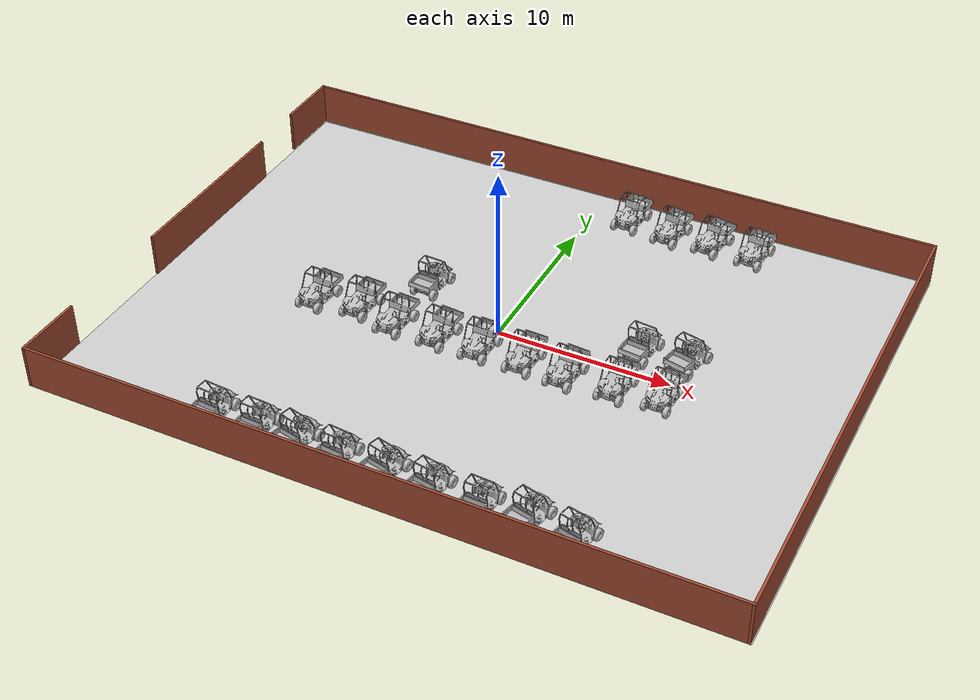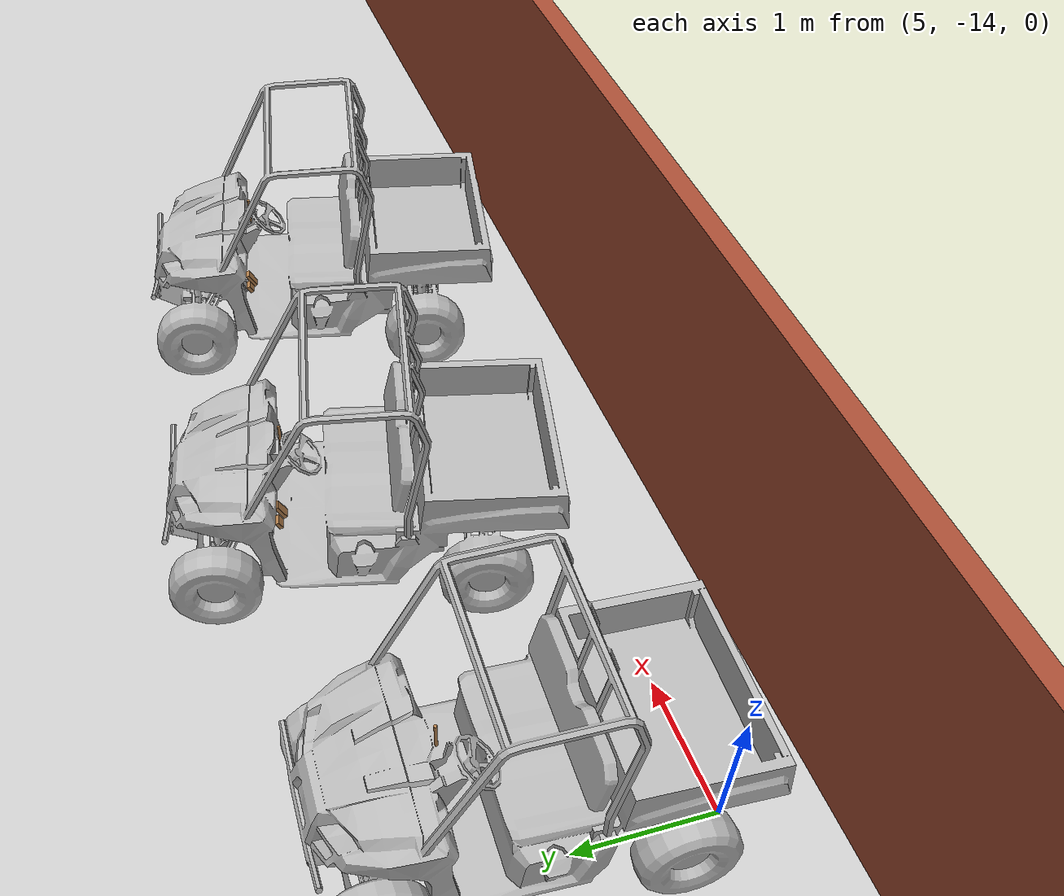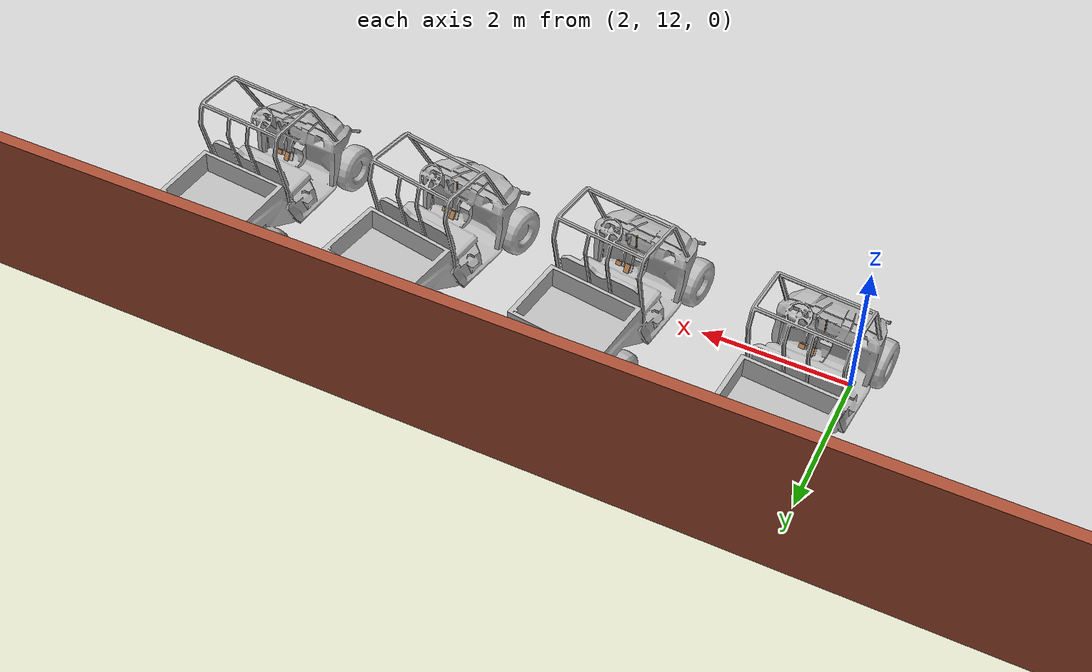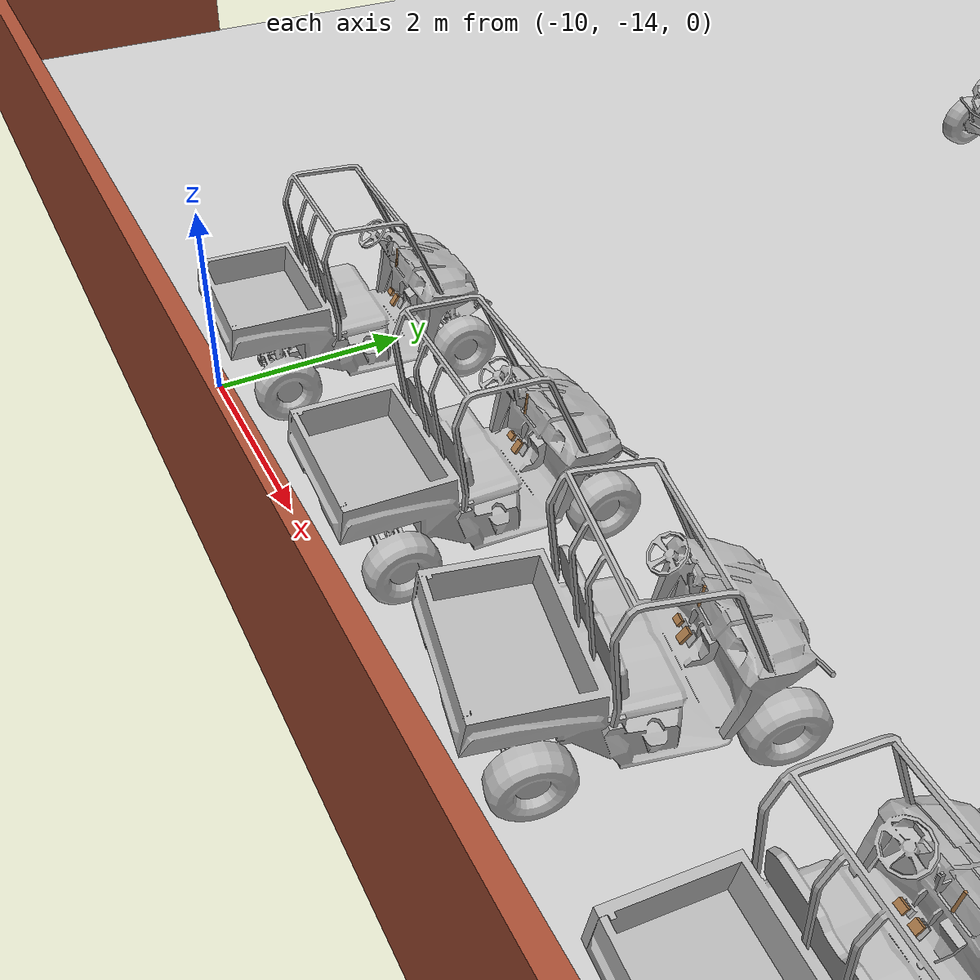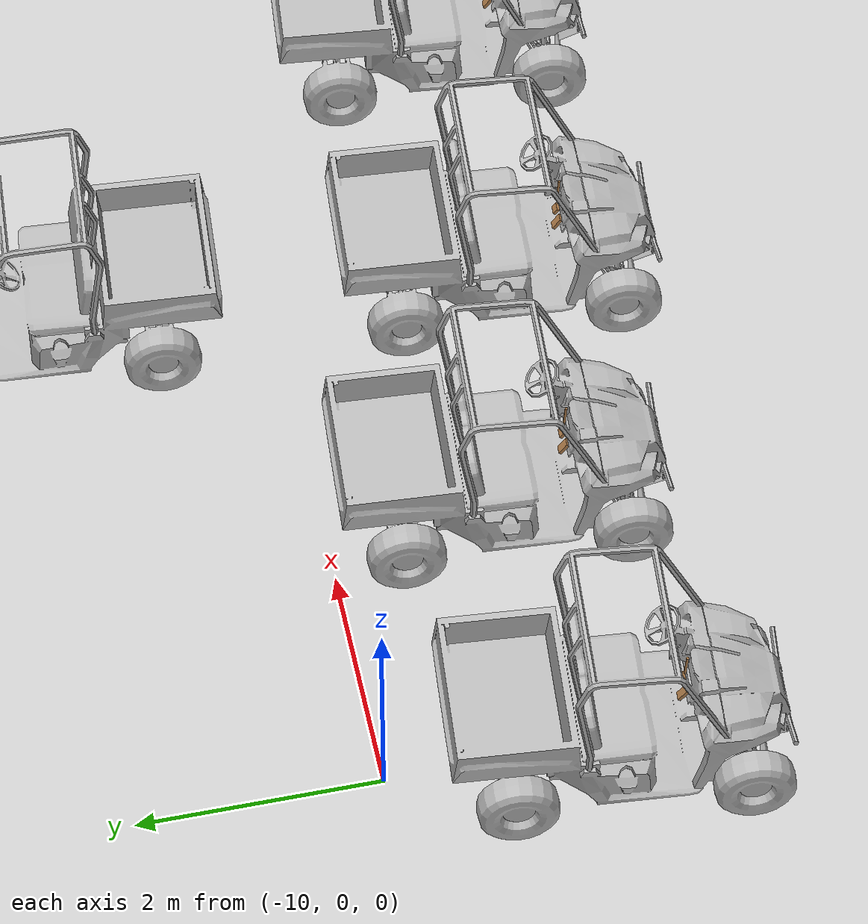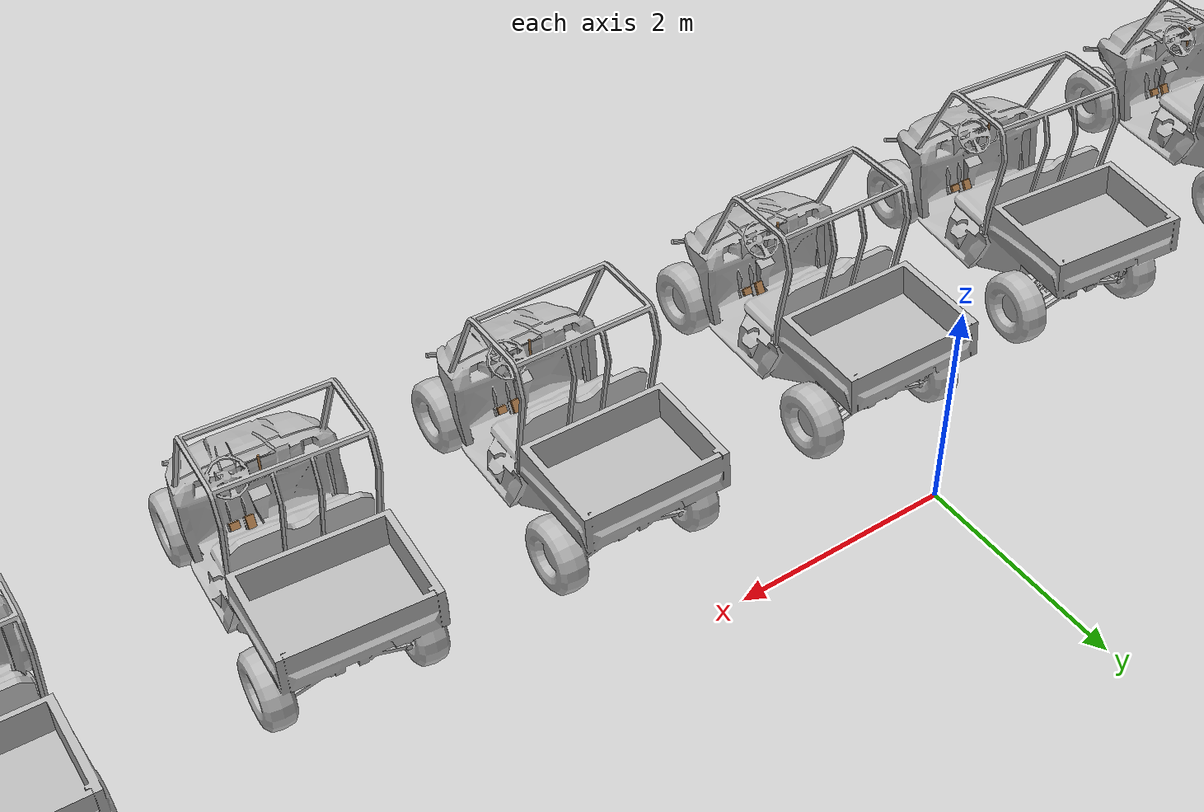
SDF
<sdf version="1.6">
 <world name="default">
  <light name="sun" type="directional">
   <pose>0 0 10 0 -0 0</pose>
   <diffuse>0.8 0.8 0.8 1</diffuse>
   <specular>0.1 0.1 0.1 1</specular>
   <attenuation>
    <range>1000</range>
    <constant>0.9</constant>
    <linear>0.01</linear>
    <quadratic>0.001</quadratic>
   </attenuation>
   <direction>-0.5 0.5 -1</direction>
  </light>
  <model name="cmu_ground_plane">
   <static>1</static>
   <link name="link">
    <collision name="collision">
     <geometry><plane><normal>0 0 1</normal><size>39.44 29.55</size></plane></geometry>
     <surface><friction><ode><mu>100</mu><mu2>50</mu2></ode></friction></surface>
    </collision>
    <visual name="visual">
     <cast_shadows>0</cast_shadows>
     <geometry><plane><normal>0 0 1</normal><size>39.44 29.55</size></plane></geometry>
     <material>
      <script>
       <uri>model://cmu_ground_plane/materials/scripts</uri>
       <uri>model://cmu_ground_plane/materials/textures</uri>
       <name>CMUGroundPlane/Image</name>
      </script>
     </material>
    </visual>
   </link>
  </model>
  <gravity>0 0 -9.8</gravity>
  <magnetic_field>6e-06 2.3e-05 -4.2e-05</magnetic_field>
  <atmosphere type="adiabatic"/>
  <physics name="default_physics" default="0" type="ode">
   <max_step_size>0.001</max_step_size>
   <real_time_factor>1</real_time_factor>
   <real_time_update_rate>1000</real_time_update_rate>
  </physics>
  <scene><ambient>0.4 0.4 0.4 1</ambient><background>0.7 0.7 0.7 1</background><shadows>1</shadows></scene>
  <spherical_coordinates>
   <surface_model>EARTH_WGS84</surface_model>
   <latitude_deg>0</latitude_deg>
   <longitude_deg>0</longitude_deg>
   <elevation>0</elevation>
   <heading_deg>0</heading_deg>
  </spherical_coordinates>
  <model name="garage">
   <pose>-0.1012 0.05082 0 0 -0 0</pose>
   <link name="Wall_10">
    <collision name="Wall_10_Collision">
     <geometry><box><size>11.25 0.15 2.5</size></box></geometry>
     <pose>0 0 1.25 0 -0 0</pose>
    </collision>
    <visual name="Wall_10_Visual">
     <pose>0 0 1.25 0 -0 0</pose>
     <geometry><box><size>11.25 0.15 2.5</size></box></geometry>
     <material>
      <script><uri>file://media/materials/scripts/gazebo.material</uri><name>Gazebo/Bricks</name></script>
      <ambient>1 1 1 1</ambient>
     </material>
    </visual>
    <pose>-19.5828 1.79493 0 0 0 -1.5708</pose>
   </link>
   <link name="Wall_2">
    <collision name="Wall_2_Collision">
     <geometry><box><size>4 0.15 2.5</size></box></geometry>
     <pose>0 0 1.25 0 -0 0</pose>
    </collision>
    <visual name="Wall_2_Visual">
     <pose>0 0 1.25 0 -0 0</pose>
     <geometry><box><size>4 0.15 2.5</size></box></geometry>
     <material>
      <script><uri>file://media/materials/scripts/gazebo.material</uri><name>Gazebo/Bricks</name></script>
      <ambient>1 1 1 1</ambient>
     </material>
    </visual>
    <pose>-19.6442 -12.8901 0 0 0 -1.5708</pose>
   </link>
   <link name="Wall_3">
    <collision name="Wall_3_Collision">
     <geometry><box><size>39.5 0.15 2.5</size></box></geometry>
     <pose>0 0 1.25 0 -0 0</pose>
    </collision>
    <visual name="Wall_3_Visual">
     <pose>0 0 1.25 0 -0 0</pose>
     <geometry><box><size>39.5 0.15 2.5</size></box></geometry>
     <material>
      <script><uri>file://media/materials/scripts/gazebo.material</uri><name>Gazebo/Bricks</name></script>
      <ambient>1 1 1 1</ambient>
     </material>
    </visual>
    <pose>0.030764 -14.8151 0 0 -0 0</pose>
   </link>
   <link name="Wall_4">
    <collision name="Wall_4_Collision">
     <geometry><box><size>29.75 0.15 2.5</size></box></geometry>
     <pose>0 0 1.25 0 -0 0</pose>
    </collision>
    <visual name="Wall_4_Visual">
     <pose>0 0 1.25 0 -0 0</pose>
     <geometry><box><size>29.75 0.15 2.5</size></box></geometry>
     <material>
      <script><uri>file://media/materials/scripts/gazebo.material</uri><name>Gazebo/Bricks</name></script>
      <ambient>1 1 1 1</ambient>
     </material>
    </visual>
    <pose>19.7058 -0.015118 0 0 -0 1.5708</pose>
   </link>
   <link name="Wall_5">
    <collision name="Wall_5_Collision">
     <geometry><box><size>39.5615 0.15 2.5</size></box></geometry>
     <pose>0 0 1.25 0 -0 0</pose>
    </collision>
    <visual name="Wall_5_Visual">
     <pose>0 0 1.25 0 -0 0</pose>
     <geometry><box><size>39.5615 0.15 2.5</size></box></geometry>
     <material>
      <script><uri>file://media/materials/scripts/gazebo.material</uri><name>Gazebo/Bricks</name></script>
      <ambient>1 1 1 1</ambient>
     </material>
    </visual>
    <pose>0 14.8 0 0 -0 3.14083</pose>
   </link>
   <link name="Wall_7">
    <collision name="Wall_7_Collision">
     <geometry><box><size>4 0.15 2.5</size></box></geometry>
     <pose>0 0 1.25 0 -0 0</pose>
    </collision>
    <visual name="Wall_7_Visual">
     <pose>0 0 1.25 0 -0 0</pose>
     <geometry><box><size>4 0.15 2.5</size></box></geometry>
     <material>
      <script><uri>file://media/materials/scripts/gazebo.material</uri><name>Gazebo/Bricks</name></script>
      <ambient>1 1 1 1</ambient>
     </material>
    </visual>
    <pose>-19.7058 12.8901 0 0 0 -1.5708</pose>
   </link>
   <static>1</static>
  </model>
  <model name="polaris_ranger_ev">
   <static>true</static>
   <link name="chassis">
    <inertial>
     <mass>720</mass>
     <inertia><ixx>140</ixx><ixy>0</ixy><iyy>550</iyy><ixz>0</ixz><iyz>0</iyz><izz>550</izz></inertia>
    </inertial>
    <visual name="visual">
     <pose>0 0 0 0 0 -1.5708</pose>
     <geometry><mesh><uri>model://polaris_ranger_ev/meshes/polaris.dae</uri><scale>1 1 1</scale></mesh></geometry>
     <material>
      <script>
       <uri>model://polaris_ranger_ev/materials/scripts</uri>
       <uri>model://polaris_ranger_ev/materials/textures</uri>
       <name>Polaris/Diffuse</name>
      </script>
     </material>
    </visual>
    <collision name="chassis_bottom">
     <pose>0 0 0.35 0 -0 0</pose>
     <geometry><box><size>2 1 0.1</size></box></geometry>
    </collision>
    <collision name="cargo_bottom">
     <pose>-0.9 0 0.9 0 -0 0</pose>
     <geometry><box><size>0.9 1.2 0.01</size></box></geometry>
    </collision>
    <collision name="cargo_front">
     <pose>-0.45 0 1.025 0 -0 0</pose>
     <geometry><box><size>0.05 1.2 0.25</size></box></geometry>
    </collision>
    <collision name="cargo_back">
     <pose>-1.35 0 1.025 0 -0 0</pose>
     <geometry><box><size>0.05 1.2 0.25</size></box></geometry>
    </collision>
    <collision name="cargo_left">
     <pose>-0.9 0.6 1.025 0 -0 0</pose>
     <geometry><box><size>0.9 0.05 0.25</size></box></geometry>
    </collision>
    <collision name="cargo_right">
     <pose>-0.9 -0.6 1.025 0 -0 0</pose>
     <geometry><box><size>0.9 0.05 0.25</size></box></geometry>
    </collision>
    <collision name="seat">
     <pose>-0.1 0 0.625 0 -0 0</pose>
     <geometry><box><size>0.6 1 0.65</size></box></geometry>
    </collision>
    <collision name="seat_back">
     <pose>-0.3 0 1.125 0 -0.2 0</pose>
     <geometry><box><size>0.1 1 0.4</size></box></geometry>
    </collision>
    <collision name="engine">
     <pose>0.95 0 0.7 0 -0 0</pose>
     <geometry><box><size>0.58 1 0.8</size></box></geometry>
    </collision>
    <collision name="steering_column">
     <pose>0.525 0.3 1.025 0 -0.8 0</pose>
     <geometry><cylinder><radius>0.05</radius><length>0.45</length></cylinder></geometry>
    </collision>
   </link>
   <link name="rear_right_wheel">
    <pose>-0.85 -0.6 0.32 1.5708 -0 0</pose>
    <inertial>
     <mass>12</mass>
     <inertia><ixx>0.5</ixx><ixy>0</ixy><iyy>0.5</iyy><ixz>0</ixz><iyz>0</iyz><izz>1</izz></inertia>
    </inertial>
    <collision name="collision">
     <geometry><cylinder><radius>0.32</radius><length>0.23</length></cylinder></geometry>
     <surface>
      <friction><ode><mu>100000</mu><mu2>100000</mu2><slip1>0</slip1><slip2>0</slip2></ode></friction>
     </surface>
    </collision>
   </link>
   <joint name="rear_right_wheel_joint" type="revolute">
    <pose>0 0 -0.1 0 -0 0</pose>
    <child>rear_right_wheel</child>
    <parent>chassis</parent>
    <axis>
     <xyz>0 1 0</xyz>
     <use_parent_model_frame>1</use_parent_model_frame>
     <limit><lower>-1e+16</lower><upper>1e+16</upper></limit>
     <dynamics><spring_reference>0</spring_reference><spring_stiffness>0</spring_stiffness></dynamics>
    </axis>
    <physics><ode><limit><cfm>0</cfm><erp>0.9</erp></limit></ode></physics>
   </joint>
   <link name="rear_left_wheel">
    <pose>-0.85 0.6 0.32 1.5708 -0 0</pose>
    <inertial>
     <mass>12</mass>
     <inertia><ixx>0.5</ixx><ixy>0</ixy><iyy>0.5</iyy><ixz>0</ixz><iyz>0</iyz><izz>1</izz></inertia>
    </inertial>
    <collision name="collision">
     <geometry><cylinder><radius>0.32</radius><length>0.23</length></cylinder></geometry>
     <surface>
      <friction><ode><mu>100000</mu><mu2>100000</mu2><slip1>0</slip1><slip2>0</slip2></ode></friction>
     </surface>
    </collision>
   </link>
   <joint name="rear_left_wheel_joint" type="revolute">
    <child>rear_left_wheel</child>
    <parent>chassis</parent>
    <axis>
     <xyz>0 1 0</xyz>
     <use_parent_model_frame>1</use_parent_model_frame>
     <limit><lower>-1e+16</lower><upper>1e+16</upper></limit>
     <dynamics><spring_reference>0</spring_reference><spring_stiffness>0</spring_stiffness></dynamics>
    </axis>
    <physics><ode><limit><cfm>0</cfm><erp>0.9</erp></limit></ode></physics>
   </joint>
   <link name="front_right_wheel">
    <pose>1.03 -0.6 0.32 1.5708 -0 0</pose>
    <inertial>
     <mass>12</mass>
     <inertia><ixx>0.5</ixx><ixy>0</ixy><iyy>0.5</iyy><ixz>0</ixz><iyz>0</iyz><izz>1</izz></inertia>
    </inertial>
    <collision name="collision">
     <geometry><cylinder><radius>0.32</radius><length>0.23</length></cylinder></geometry>
     <surface>
      <friction><ode><mu>100000</mu><mu2>100000</mu2><slip1>0</slip1><slip2>0</slip2></ode></friction>
     </surface>
    </collision>
   </link>
   <link name="front_right_wheel_steering_block">
    <pose>1.03 -0.5 0.32 1.5708 -0 0</pose>
    <inertial>
     <mass>1</mass>
     <inertia><ixx>1</ixx><ixy>0</ixy><iyy>1</iyy><ixz>0</ixz><iyz>0</iyz><izz>1</izz></inertia>
    </inertial>
    <collision name="collision">
     <geometry><cylinder><radius>0.05</radius><length>0.01</length></cylinder></geometry>
    </collision>
   </link>
   <joint name="front_right_steering_joint" type="revolute">
    <child>front_right_wheel_steering_block</child>
    <parent>chassis</parent>
    <axis>
     <xyz>0 0 1</xyz>
     <limit><lower>-1</lower><upper>1</upper></limit>
     <use_parent_model_frame>1</use_parent_model_frame>
     <dynamics><spring_reference>0</spring_reference><spring_stiffness>0</spring_stiffness></dynamics>
    </axis>
    <physics><ode><limit><cfm>0</cfm><erp>0.9</erp></limit></ode></physics>
   </joint>
   <joint name="front_right_wheel_joint" type="revolute">
    <child>front_right_wheel</child>
    <parent>front_right_wheel_steering_block</parent>
    <axis>
     <xyz>0 1 0</xyz>
     <use_parent_model_frame>1</use_parent_model_frame>
     <limit><lower>-1e+16</lower><upper>1e+16</upper></limit>
     <dynamics><spring_reference>0</spring_reference><spring_stiffness>0</spring_stiffness></dynamics>
    </axis>
    <physics><ode><limit><cfm>0</cfm><erp>0.9</erp></limit></ode></physics>
   </joint>
   <link name="front_left_wheel">
    <pose>1.03 0.6 0.32 1.5708 -0 0</pose>
    <inertial>
     <mass>12</mass>
     <inertia><ixx>0.5</ixx><ixy>0</ixy><iyy>0.5</iyy><ixz>0</ixz><iyz>0</iyz><izz>1</izz></inertia>
    </inertial>
    <collision name="collision">
     <geometry><cylinder><radius>0.32</radius><length>0.23</length></cylinder></geometry>
     <surface>
      <friction><ode><mu>100000</mu><mu2>100000</mu2><slip1>0</slip1><slip2>0</slip2></ode></friction>
     </surface>
    </collision>
   </link>
   <link name="front_left_wheel_steering_block">
    <pose>1.03 0.5 0.32 1.5708 -0 0</pose>
    <inertial>
     <mass>1</mass>
     <inertia><ixx>1</ixx><ixy>0</ixy><iyy>1</iyy><ixz>0</ixz><iyz>0</iyz><izz>1</izz></inertia>
    </inertial>
    <collision name="collision">
     <geometry><cylinder><radius>0.05</radius><length>0.01</length></cylinder></geometry>
    </collision>
   </link>
   <joint name="front_left_steering_joint" type="revolute">
    <child>front_left_wheel_steering_block</child>
    <parent>chassis</parent>
    <axis>
     <xyz>0 0 1</xyz>
     <limit><lower>-1</lower><upper>1</upper></limit>
     <use_parent_model_frame>1</use_parent_model_frame>
     <dynamics><spring_reference>0</spring_reference><spring_stiffness>0</spring_stiffness></dynamics>
    </axis>
    <physics><ode><limit><cfm>0</cfm><erp>0.9</erp></limit></ode></physics>
   </joint>
   <joint name="front_left_wheel_joint" type="revolute">
    <child>front_left_wheel</child>
    <parent>front_left_wheel_steering_block</parent>
    <axis>
     <xyz>0 1 0</xyz>
     <use_parent_model_frame>1</use_parent_model_frame>
     <limit><lower>-1e+16</lower><upper>1e+16</upper></limit>
     <dynamics><spring_reference>0</spring_reference><spring_stiffness>0</spring_stiffness></dynamics>
    </axis>
    <physics><ode><limit><cfm>0</cfm><erp>0.9</erp></limit></ode></physics>
   </joint>
   <link name="gas_pedal">
    <pose>0.53 0.14 0.56 0 -1 0</pose>
    <gravity>0</gravity>
    <inertial>
     <mass>0.1</mass>
     <inertia><ixx>0.01</ixx><ixy>0</ixy><ixz>0</ixz><iyy>0.01</iyy><iyz>0</iyz><izz>0.01</izz></inertia>
    </inertial>
    <collision name="gas_pedal_collision"><geometry><box><size>0.12 0.07 0.03</size></box></geometry></collision>
    <visual name="gas_pedal_visual">
     <geometry><box><size>0.12 0.07 0.03</size></box></geometry>
     <material>
      <script><uri>file://media/materials/scripts/gazebo.material</uri><name>Gazebo/Wood</name></script>
      <ambient>0.2 0.2 0.2 1</ambient>
      <diffuse>0.2 0.2 0.2 1</diffuse>
      <specular>0.2 0.2 0.2 1</specular>
      <emissive>0.5 0.5 0.5 1</emissive>
     </material>
    </visual>
   </link>
   <link name="brake_pedal">
    <gravity>0</gravity>
    <pose>0.54 0.27 0.58 0 -1 0</pose>
    <inertial>
     <mass>0.1</mass>
     <inertia><ixx>0.01</ixx><ixy>0</ixy><ixz>0</ixz><iyy>0.01</iyy><iyz>0</iyz><izz>0.01</izz></inertia>
    </inertial>
    <collision name="brake_pedal_collision">
     <geometry><box><size>0.06 0.08 0.03</size></box></geometry>
    </collision>
    <visual name="brake_pedal_visual">
     <geometry><box><size>0.06 0.08 0.03</size></box></geometry>
     <material>
      <script><uri>file://media/materials/scripts/gazebo.material</uri><name>Gazebo/Wood</name></script>
      <ambient>0.2 0.2 0.2 1</ambient>
      <diffuse>0.2 0.2 0.2 1</diffuse>
      <specular>0.2 0.2 0.2 1</specular>
      <emissive>0.5 0.5 0.5 1</emissive>
     </material>
    </visual>
   </link>
   <link name="steering_wheel">
    <pose>0.37 0.3 1.2 0 -0.8 0</pose>
    <inertial>
     <mass>1</mass>
     <inertia><ixx>0.1</ixx><ixy>0</ixy><ixz>0</ixz><iyy>0.1</iyy><iyz>0</iyz><izz>1</izz></inertia>
    </inertial>
    <collision name="steering_wheel_post_left">
     <pose>0 0.08 0 1.5708 -0 0</pose>
     <geometry><cylinder><radius>0.02</radius><length>0.15</length></cylinder></geometry>
    </collision>
    <collision name="steering_wheel_post_right">
     <pose>0 -0.08 0 1.5708 -0 0</pose>
     <geometry><cylinder><radius>0.02</radius><length>0.15</length></cylinder></geometry>
    </collision>
    <collision name="steering_wheel_post_middle">
     <pose>-0.08 0 0 3.14159 1.57079 3.14159</pose>
     <geometry><cylinder><radius>0.02</radius><length>0.15</length></cylinder></geometry>
    </collision>
    <collision name="collision00">
     <pose>0.15 0 0 3.14159 1.57079 -1.57079</pose>
     <geometry><cylinder><length>0.105066</length><radius>0.01</radius></cylinder></geometry>
    </collision>
    <collision name="collision01">
     <pose>0.121353 0.088168 0 3.14159 1.57079 -0.942483</pose>
     <geometry><cylinder><length>0.105066</length><radius>0.01</radius></cylinder></geometry>
    </collision>
    <collision name="collision02">
     <pose>0.046353 0.142658 0 3.14159 1.57079 -0.314163</pose>
     <geometry><cylinder><length>0.105066</length><radius>0.01</radius></cylinder></geometry>
    </collision>
    <collision name="collision03">
     <pose>-0.046353 0.142658 0 3.14159 1.57079 0.314163</pose>
     <geometry><cylinder><length>0.105066</length><radius>0.01</radius></cylinder></geometry>
    </collision>
    <collision name="collision04">
     <pose>-0.121353 0.088168 0 -3.14159 1.57079 0.942483</pose>
     <geometry><cylinder><length>0.105066</length><radius>0.01</radius></cylinder></geometry>
    </collision>
    <collision name="collision05">
     <pose>-0.15 0 0 -3.14159 1.57079 1.57079</pose>
     <geometry><cylinder><length>0.105066</length><radius>0.01</radius></cylinder></geometry>
    </collision>
    <collision name="collision06">
     <pose>-0.121353 -0.088168 0 3.14159 1.57079 2.19912</pose>
     <geometry><cylinder><length>0.105066</length><radius>0.01</radius></cylinder></geometry>
    </collision>
    <collision name="collision07">
     <pose>-0.046353 -0.142658 0 -3.14159 1.57079 2.82743</pose>
     <geometry><cylinder><length>0.105066</length><radius>0.01</radius></cylinder></geometry>
    </collision>
    <collision name="collision08">
     <pose>0.046353 -0.142658 0 3.14159 1.57079 -2.82743</pose>
     <geometry><cylinder><length>0.105066</length><radius>0.01</radius></cylinder></geometry>
    </collision>
    <collision name="collision09">
     <pose>0.121353 -0.088168 0 -3.14159 1.57079 -2.19911</pose>
     <geometry><cylinder><length>0.105066</length><radius>0.01</radius></cylinder></geometry>
    </collision>
   </link>
   <link name="hand_brake">
    <pose>0.5 0 1.05 3.14159 -0.058407 3.14159</pose>
    <inertial>
     <mass>1</mass>
     <pose>0 0 -0.15 0 -0 0</pose>
     <inertia><ixx>0.1</ixx><ixy>0</ixy><ixz>0</ixz><iyy>0.1</iyy><iyz>0</iyz><izz>1</izz></inertia>
    </inertial>
    <collision name="hand_brake_collision">
     <pose>0 0 -0.1 0 -0 0</pose>
     <geometry><cylinder><radius>0.01</radius><length>0.2</length></cylinder></geometry>
    </collision>
    <visual name="hand_brake_visual">
     <pose>0 0 -0.1 0 -0 0</pose>
     <geometry><cylinder><radius>0.01</radius><length>0.2</length></cylinder></geometry>
     <material>
      <script><uri>file://media/materials/scripts/gazebo.material</uri><name>Gazebo/Wood</name></script>
     </material>
    </visual>
   </link>
   <joint name="gas_joint" type="prismatic">
    <parent>chassis</parent>
    <child>gas_pedal</child>
    <axis>
     <xyz>1 0 -1</xyz>
     <limit><lower>0</lower><upper>0.15</upper></limit>
     <use_parent_model_frame>1</use_parent_model_frame>
     <dynamics><spring_reference>0</spring_reference><spring_stiffness>0</spring_stiffness></dynamics>
    </axis>
   </joint>
   <joint name="brake_joint" type="prismatic">
    <parent>chassis</parent>
    <child>brake_pedal</child>
    <axis>
     <xyz>1 0 -0.6</xyz>
     <limit><lower>0</lower><upper>0.15</upper></limit>
     <use_parent_model_frame>1</use_parent_model_frame>
     <dynamics><spring_reference>0</spring_reference><spring_stiffness>0</spring_stiffness></dynamics>
    </axis>
   </joint>
   <joint name="steering_joint" type="revolute">
    <pose>0 0 0 1.5708 -0.8 0</pose>
    <parent>chassis</parent>
    <child>steering_wheel</child>
    <axis>
     <xyz>-1 0 1.023</xyz>
     <limit><lower>-7.853</lower><upper>7.853</upper></limit>
     <use_parent_model_frame>1</use_parent_model_frame>
     <dynamics><spring_reference>0</spring_reference><spring_stiffness>0</spring_stiffness></dynamics>
    </axis>
   </joint>
   <joint name="hand_brake_joint" type="revolute">
    <parent>chassis</parent>
    <child>hand_brake</child>
    <axis>
     <xyz>0 -1 0</xyz>
     <limit><lower>0</lower><upper>0.6</upper></limit>
     <use_parent_model_frame>1</use_parent_model_frame>
     <dynamics><spring_reference>0</spring_reference><spring_stiffness>0</spring_stiffness></dynamics>
    </axis>
   </joint>
   <pose>-2.56735 -1.9307 -4.3e-05 0 4.9e-05 -1.66172</pose>
  </model>
  <model name="polaris_ranger_ev_clone">
   <static>true</static>
   <link name="chassis">
    <inertial>
     <mass>720</mass>
     <inertia><ixx>140</ixx><ixy>0</ixy><iyy>550</iyy><ixz>0</ixz><iyz>0</iyz><izz>550</izz></inertia>
    </inertial>
    <visual name="visual">
     <pose>0 0 0 0 0 -1.5708</pose>
     <geometry><mesh><uri>model://polaris_ranger_ev/meshes/polaris.dae</uri><scale>1 1 1</scale></mesh></geometry>
     <material>
      <script>
       <uri>model://polaris_ranger_ev/materials/scripts</uri>
       <uri>model://polaris_ranger_ev/materials/textures</uri>
       <name>Polaris/Diffuse</name>
      </script>
     </material>
    </visual>
    <collision name="chassis_bottom">
     <pose>0 0 0.35 0 -0 0</pose>
     <geometry><box><size>2 1 0.1</size></box></geometry>
    </collision>
    <collision name="cargo_bottom">
     <pose>-0.9 0 0.9 0 -0 0</pose>
     <geometry><box><size>0.9 1.2 0.01</size></box></geometry>
    </collision>
    <collision name="cargo_front">
     <pose>-0.45 0 1.025 0 -0 0</pose>
     <geometry><box><size>0.05 1.2 0.25</size></box></geometry>
    </collision>
    <collision name="cargo_back">
     <pose>-1.35 0 1.025 0 -0 0</pose>
     <geometry><box><size>0.05 1.2 0.25</size></box></geometry>
    </collision>
    <collision name="cargo_left">
     <pose>-0.9 0.6 1.025 0 -0 0</pose>
     <geometry><box><size>0.9 0.05 0.25</size></box></geometry>
    </collision>
    <collision name="cargo_right">
     <pose>-0.9 -0.6 1.025 0 -0 0</pose>
     <geometry><box><size>0.9 0.05 0.25</size></box></geometry>
    </collision>
    <collision name="seat">
     <pose>-0.1 0 0.625 0 -0 0</pose>
     <geometry><box><size>0.6 1 0.65</size></box></geometry>
    </collision>
    <collision name="seat_back">
     <pose>-0.3 0 1.125 0 -0.2 0</pose>
     <geometry><box><size>0.1 1 0.4</size></box></geometry>
    </collision>
    <collision name="engine">
     <pose>0.95 0 0.7 0 -0 0</pose>
     <geometry><box><size>0.58 1 0.8</size></box></geometry>
    </collision>
    <collision name="steering_column">
     <pose>0.525 0.3 1.025 0 -0.8 0</pose>
     <geometry><cylinder><radius>0.05</radius><length>0.45</length></cylinder></geometry>
    </collision>
   </link>
   <link name="rear_right_wheel">
    <pose>-0.85 -0.6 0.32 1.5708 -0 0</pose>
    <inertial>
     <mass>12</mass>
     <inertia><ixx>0.5</ixx><ixy>0</ixy><iyy>0.5</iyy><ixz>0</ixz><iyz>0</iyz><izz>1</izz></inertia>
    </inertial>
    <collision name="collision">
     <geometry><cylinder><radius>0.32</radius><length>0.23</length></cylinder></geometry>
     <surface>
      <friction><ode><mu>100000</mu><mu2>100000</mu2><slip1>0</slip1><slip2>0</slip2></ode></friction>
     </surface>
    </collision>
   </link>
   <joint name="rear_right_wheel_joint" type="revolute">
    <pose>0 0 -0.1 0 -0 0</pose>
    <child>rear_right_wheel</child>
    <parent>chassis</parent>
    <axis>
     <xyz>0 1 0</xyz>
     <use_parent_model_frame>1</use_parent_model_frame>
     <limit><lower>-1e+16</lower><upper>1e+16</upper></limit>
     <dynamics><spring_reference>0</spring_reference><spring_stiffness>0</spring_stiffness></dynamics>
    </axis>
    <physics><ode><limit><cfm>0</cfm><erp>0.9</erp></limit></ode></physics>
   </joint>
   <link name="rear_left_wheel">
    <pose>-0.85 0.6 0.32 1.5708 -0 0</pose>
    <inertial>
     <mass>12</mass>
     <inertia><ixx>0.5</ixx><ixy>0</ixy><iyy>0.5</iyy><ixz>0</ixz><iyz>0</iyz><izz>1</izz></inertia>
    </inertial>
    <collision name="collision">
     <geometry><cylinder><radius>0.32</radius><length>0.23</length></cylinder></geometry>
     <surface>
      <friction><ode><mu>100000</mu><mu2>100000</mu2><slip1>0</slip1><slip2>0</slip2></ode></friction>
     </surface>
    </collision>
   </link>
   <joint name="rear_left_wheel_joint" type="revolute">
    <child>rear_left_wheel</child>
    <parent>chassis</parent>
    <axis>
     <xyz>0 1 0</xyz>
     <use_parent_model_frame>1</use_parent_model_frame>
     <limit><lower>-1e+16</lower><upper>1e+16</upper></limit>
     <dynamics><spring_reference>0</spring_reference><spring_stiffness>0</spring_stiffness></dynamics>
    </axis>
    <physics><ode><limit><cfm>0</cfm><erp>0.9</erp></limit></ode></physics>
   </joint>
   <link name="front_right_wheel">
    <pose>1.03 -0.6 0.32 1.5708 -0 0</pose>
    <inertial>
     <mass>12</mass>
     <inertia><ixx>0.5</ixx><ixy>0</ixy><iyy>0.5</iyy><ixz>0</ixz><iyz>0</iyz><izz>1</izz></inertia>
    </inertial>
    <collision name="collision">
     <geometry><cylinder><radius>0.32</radius><length>0.23</length></cylinder></geometry>
     <surface>
      <friction><ode><mu>100000</mu><mu2>100000</mu2><slip1>0</slip1><slip2>0</slip2></ode></friction>
     </surface>
    </collision>
   </link>
   <link name="front_right_wheel_steering_block">
    <pose>1.03 -0.5 0.32 1.5708 -0 0</pose>
    <inertial>
     <mass>1</mass>
     <inertia><ixx>1</ixx><ixy>0</ixy><iyy>1</iyy><ixz>0</ixz><iyz>0</iyz><izz>1</izz></inertia>
    </inertial>
    <collision name="collision">
     <geometry><cylinder><radius>0.05</radius><length>0.01</length></cylinder></geometry>
    </collision>
   </link>
   <joint name="front_right_steering_joint" type="revolute">
    <child>front_right_wheel_steering_block</child>
    <parent>chassis</parent>
    <axis>
     <xyz>0 0 1</xyz>
     <limit><lower>-1</lower><upper>1</upper></limit>
     <use_parent_model_frame>1</use_parent_model_frame>
     <dynamics><spring_reference>0</spring_reference><spring_stiffness>0</spring_stiffness></dynamics>
    </axis>
    <physics><ode><limit><cfm>0</cfm><erp>0.9</erp></limit></ode></physics>
   </joint>
   <joint name="front_right_wheel_joint" type="revolute">
    <child>front_right_wheel</child>
    <parent>front_right_wheel_steering_block</parent>
    <axis>
     <xyz>0 1 0</xyz>
     <use_parent_model_frame>1</use_parent_model_frame>
     <limit><lower>-1e+16</lower><upper>1e+16</upper></limit>
     <dynamics><spring_reference>0</spring_reference><spring_stiffness>0</spring_stiffness></dynamics>
    </axis>
    <physics><ode><limit><cfm>0</cfm><erp>0.9</erp></limit></ode></physics>
   </joint>
   <link name="front_left_wheel">
    <pose>1.03 0.6 0.32 1.5708 -0 0</pose>
    <inertial>
     <mass>12</mass>
     <inertia><ixx>0.5</ixx><ixy>0</ixy><iyy>0.5</iyy><ixz>0</ixz><iyz>0</iyz><izz>1</izz></inertia>
    </inertial>
    <collision name="collision">
     <geometry><cylinder><radius>0.32</radius><length>0.23</length></cylinder></geometry>
     <surface>
      <friction><ode><mu>100000</mu><mu2>100000</mu2><slip1>0</slip1><slip2>0</slip2></ode></friction>
     </surface>
    </collision>
   </link>
   <link name="front_left_wheel_steering_block">
    <pose>1.03 0.5 0.32 1.5708 -0 0</pose>
    <inertial>
     <mass>1</mass>
     <inertia><ixx>1</ixx><ixy>0</ixy><iyy>1</iyy><ixz>0</ixz><iyz>0</iyz><izz>1</izz></inertia>
    </inertial>
    <collision name="collision">
     <geometry><cylinder><radius>0.05</radius><length>0.01</length></cylinder></geometry>
    </collision>
   </link>
   <joint name="front_left_steering_joint" type="revolute">
    <child>front_left_wheel_steering_block</child>
    <parent>chassis</parent>
    <axis>
     <xyz>0 0 1</xyz>
     <limit><lower>-1</lower><upper>1</upper></limit>
     <use_parent_model_frame>1</use_parent_model_frame>
     <dynamics><spring_reference>0</spring_reference><spring_stiffness>0</spring_stiffness></dynamics>
    </axis>
    <physics><ode><limit><cfm>0</cfm><erp>0.9</erp></limit></ode></physics>
   </joint>
   <joint name="front_left_wheel_joint" type="revolute">
    <child>front_left_wheel</child>
    <parent>front_left_wheel_steering_block</parent>
    <axis>
     <xyz>0 1 0</xyz>
     <use_parent_model_frame>1</use_parent_model_frame>
     <limit><lower>-1e+16</lower><upper>1e+16</upper></limit>
     <dynamics><spring_reference>0</spring_reference><spring_stiffness>0</spring_stiffness></dynamics>
    </axis>
    <physics><ode><limit><cfm>0</cfm><erp>0.9</erp></limit></ode></physics>
   </joint>
   <link name="gas_pedal">
    <pose>0.53 0.14 0.56 0 -1 0</pose>
    <gravity>0</gravity>
    <inertial>
     <mass>0.1</mass>
     <inertia><ixx>0.01</ixx><ixy>0</ixy><ixz>0</ixz><iyy>0.01</iyy><iyz>0</iyz><izz>0.01</izz></inertia>
    </inertial>
    <collision name="gas_pedal_collision"><geometry><box><size>0.12 0.07 0.03</size></box></geometry></collision>
    <visual name="gas_pedal_visual">
     <geometry><box><size>0.12 0.07 0.03</size></box></geometry>
     <material>
      <script><uri>file://media/materials/scripts/gazebo.material</uri><name>Gazebo/Wood</name></script>
      <ambient>0.2 0.2 0.2 1</ambient>
      <diffuse>0.2 0.2 0.2 1</diffuse>
      <specular>0.2 0.2 0.2 1</specular>
      <emissive>0.5 0.5 0.5 1</emissive>
     </material>
    </visual>
   </link>
   <link name="brake_pedal">
    <gravity>0</gravity>
    <pose>0.54 0.27 0.58 0 -1 0</pose>
    <inertial>
     <mass>0.1</mass>
     <inertia><ixx>0.01</ixx><ixy>0</ixy><ixz>0</ixz><iyy>0.01</iyy><iyz>0</iyz><izz>0.01</izz></inertia>
    </inertial>
    <collision name="brake_pedal_collision">
     <geometry><box><size>0.06 0.08 0.03</size></box></geometry>
    </collision>
    <visual name="brake_pedal_visual">
     <geometry><box><size>0.06 0.08 0.03</size></box></geometry>
     <material>
      <script><uri>file://media/materials/scripts/gazebo.material</uri><name>Gazebo/Wood</name></script>
      <ambient>0.2 0.2 0.2 1</ambient>
      <diffuse>0.2 0.2 0.2 1</diffuse>
      <specular>0.2 0.2 0.2 1</specular>
      <emissive>0.5 0.5 0.5 1</emissive>
     </material>
    </visual>
   </link>
   <link name="steering_wheel">
    <pose>0.37 0.3 1.2 0 -0.8 0</pose>
    <inertial>
     <mass>1</mass>
     <inertia><ixx>0.1</ixx><ixy>0</ixy><ixz>0</ixz><iyy>0.1</iyy><iyz>0</iyz><izz>1</izz></inertia>
    </inertial>
    <collision name="steering_wheel_post_left">
     <pose>0 0.08 0 1.5708 -0 0</pose>
     <geometry><cylinder><radius>0.02</radius><length>0.15</length></cylinder></geometry>
    </collision>
    <collision name="steering_wheel_post_right">
     <pose>0 -0.08 0 1.5708 -0 0</pose>
     <geometry><cylinder><radius>0.02</radius><length>0.15</length></cylinder></geometry>
    </collision>
    <collision name="steering_wheel_post_middle">
     <pose>-0.08 0 0 3.14159 1.57079 3.14159</pose>
     <geometry><cylinder><radius>0.02</radius><length>0.15</length></cylinder></geometry>
    </collision>
    <collision name="collision00">
     <pose>0.15 0 0 3.14159 1.57079 -1.57079</pose>
     <geometry><cylinder><length>0.105066</length><radius>0.01</radius></cylinder></geometry>
    </collision>
    <collision name="collision01">
     <pose>0.121353 0.088168 0 3.14159 1.57079 -0.942483</pose>
     <geometry><cylinder><length>0.105066</length><radius>0.01</radius></cylinder></geometry>
    </collision>
    <collision name="collision02">
     <pose>0.046353 0.142658 0 3.14159 1.57079 -0.314163</pose>
     <geometry><cylinder><length>0.105066</length><radius>0.01</radius></cylinder></geometry>
    </collision>
    <collision name="collision03">
     <pose>-0.046353 0.142658 0 3.14159 1.57079 0.314163</pose>
     <geometry><cylinder><length>0.105066</length><radius>0.01</radius></cylinder></geometry>
    </collision>
    <collision name="collision04">
     <pose>-0.121353 0.088168 0 -3.14159 1.57079 0.942483</pose>
     <geometry><cylinder><length>0.105066</length><radius>0.01</radius></cylinder></geometry>
    </collision>
    <collision name="collision05">
     <pose>-0.15 0 0 -3.14159 1.57079 1.57079</pose>
     <geometry><cylinder><length>0.105066</length><radius>0.01</radius></cylinder></geometry>
    </collision>
    <collision name="collision06">
     <pose>-0.121353 -0.088168 0 3.14159 1.57079 2.19912</pose>
     <geometry><cylinder><length>0.105066</length><radius>0.01</radius></cylinder></geometry>
    </collision>
    <collision name="collision07">
     <pose>-0.046353 -0.142658 0 -3.14159 1.57079 2.82743</pose>
     <geometry><cylinder><length>0.105066</length><radius>0.01</radius></cylinder></geometry>
    </collision>
    <collision name="collision08">
     <pose>0.046353 -0.142658 0 3.14159 1.57079 -2.82743</pose>
     <geometry><cylinder><length>0.105066</length><radius>0.01</radius></cylinder></geometry>
    </collision>
    <collision name="collision09">
     <pose>0.121353 -0.088168 0 -3.14159 1.57079 -2.19911</pose>
     <geometry><cylinder><length>0.105066</length><radius>0.01</radius></cylinder></geometry>
    </collision>
   </link>
   <link name="hand_brake">
    <pose>0.5 0 1.05 3.14159 -0.058407 3.14159</pose>
    <inertial>
     <mass>1</mass>
     <pose>0 0 -0.15 0 -0 0</pose>
     <inertia><ixx>0.1</ixx><ixy>0</ixy><ixz>0</ixz><iyy>0.1</iyy><iyz>0</iyz><izz>1</izz></inertia>
    </inertial>
    <collision name="hand_brake_collision">
     <pose>0 0 -0.1 0 -0 0</pose>
     <geometry><cylinder><radius>0.01</radius><length>0.2</length></cylinder></geometry>
    </collision>
    <visual name="hand_brake_visual">
     <pose>0 0 -0.1 0 -0 0</pose>
     <geometry><cylinder><radius>0.01</radius><length>0.2</length></cylinder></geometry>
     <material>
      <script><uri>file://media/materials/scripts/gazebo.material</uri><name>Gazebo/Wood</name></script>
     </material>
    </visual>
   </link>
   <joint name="gas_joint" type="prismatic">
    <parent>chassis</parent>
    <child>gas_pedal</child>
    <axis>
     <xyz>1 0 -1</xyz>
     <limit><lower>0</lower><upper>0.15</upper></limit>
     <use_parent_model_frame>1</use_parent_model_frame>
     <dynamics><spring_reference>0</spring_reference><spring_stiffness>0</spring_stiffness></dynamics>
    </axis>
   </joint>
   <joint name="brake_joint" type="prismatic">
    <parent>chassis</parent>
    <child>brake_pedal</child>
    <axis>
     <xyz>1 0 -0.6</xyz>
     <limit><lower>0</lower><upper>0.15</upper></limit>
     <use_parent_model_frame>1</use_parent_model_frame>
     <dynamics><spring_reference>0</spring_reference><spring_stiffness>0</spring_stiffness></dynamics>
    </axis>
   </joint>
   <joint name="steering_joint" type="revolute">
    <pose>0 0 0 1.5708 -0.8 0</pose>
    <parent>chassis</parent>
    <child>steering_wheel</child>
    <axis>
     <xyz>-1 0 1.023</xyz>
     <limit><lower>-7.853</lower><upper>7.853</upper></limit>
     <use_parent_model_frame>1</use_parent_model_frame>
     <dynamics><spring_reference>0</spring_reference><spring_stiffness>0</spring_stiffness></dynamics>
    </axis>
   </joint>
   <joint name="hand_brake_joint" type="revolute">
    <parent>chassis</parent>
    <child>hand_brake</child>
    <axis>
     <xyz>0 -1 0</xyz>
     <limit><lower>0</lower><upper>0.6</upper></limit>
     <use_parent_model_frame>1</use_parent_model_frame>
     <dynamics><spring_reference>0</spring_reference><spring_stiffness>0</spring_stiffness></dynamics>
    </axis>
   </joint>
   <pose>-5.21039 -1.96592 -4.3e-05 0 4.9e-05 -1.63939</pose>
  </model>
  <model name="polaris_ranger_ev_clone_0">
   <static>true</static>
   <link name="chassis">
    <inertial>
     <mass>720</mass>
     <inertia><ixx>140</ixx><ixy>0</ixy><iyy>550</iyy><ixz>0</ixz><iyz>0</iyz><izz>550</izz></inertia>
    </inertial>
    <visual name="visual">
     <pose>0 0 0 0 0 -1.5708</pose>
     <geometry><mesh><uri>model://polaris_ranger_ev/meshes/polaris.dae</uri><scale>1 1 1</scale></mesh></geometry>
     <material>
      <script>
       <uri>model://polaris_ranger_ev/materials/scripts</uri>
       <uri>model://polaris_ranger_ev/materials/textures</uri>
       <name>Polaris/Diffuse</name>
      </script>
     </material>
    </visual>
    <collision name="chassis_bottom">
     <pose>0 0 0.35 0 -0 0</pose>
     <geometry><box><size>2 1 0.1</size></box></geometry>
    </collision>
    <collision name="cargo_bottom">
     <pose>-0.9 0 0.9 0 -0 0</pose>
     <geometry><box><size>0.9 1.2 0.01</size></box></geometry>
    </collision>
    <collision name="cargo_front">
     <pose>-0.45 0 1.025 0 -0 0</pose>
     <geometry><box><size>0.05 1.2 0.25</size></box></geometry>
    </collision>
    <collision name="cargo_back">
     <pose>-1.35 0 1.025 0 -0 0</pose>
     <geometry><box><size>0.05 1.2 0.25</size></box></geometry>
    </collision>
    <collision name="cargo_left">
     <pose>-0.9 0.6 1.025 0 -0 0</pose>
     <geometry><box><size>0.9 0.05 0.25</size></box></geometry>
    </collision>
    <collision name="cargo_right">
     <pose>-0.9 -0.6 1.025 0 -0 0</pose>
     <geometry><box><size>0.9 0.05 0.25</size></box></geometry>
    </collision>
    <collision name="seat">
     <pose>-0.1 0 0.625 0 -0 0</pose>
     <geometry><box><size>0.6 1 0.65</size></box></geometry>
    </collision>
    <collision name="seat_back">
     <pose>-0.3 0 1.125 0 -0.2 0</pose>
     <geometry><box><size>0.1 1 0.4</size></box></geometry>
    </collision>
    <collision name="engine">
     <pose>0.95 0 0.7 0 -0 0</pose>
     <geometry><box><size>0.58 1 0.8</size></box></geometry>
    </collision>
    <collision name="steering_column">
     <pose>0.525 0.3 1.025 0 -0.8 0</pose>
     <geometry><cylinder><radius>0.05</radius><length>0.45</length></cylinder></geometry>
    </collision>
   </link>
   <link name="rear_right_wheel">
    <pose>-0.85 -0.6 0.32 1.5708 -0 0</pose>
    <inertial>
     <mass>12</mass>
     <inertia><ixx>0.5</ixx><ixy>0</ixy><iyy>0.5</iyy><ixz>0</ixz><iyz>0</iyz><izz>1</izz></inertia>
    </inertial>
    <collision name="collision">
     <geometry><cylinder><radius>0.32</radius><length>0.23</length></cylinder></geometry>
     <surface>
      <friction><ode><mu>100000</mu><mu2>100000</mu2><slip1>0</slip1><slip2>0</slip2></ode></friction>
     </surface>
    </collision>
   </link>
   <joint name="rear_right_wheel_joint" type="revolute">
    <pose>0 0 -0.1 0 -0 0</pose>
    <child>rear_right_wheel</child>
    <parent>chassis</parent>
    <axis>
     <xyz>0 1 0</xyz>
     <use_parent_model_frame>1</use_parent_model_frame>
     <limit><lower>-1e+16</lower><upper>1e+16</upper></limit>
     <dynamics><spring_reference>0</spring_reference><spring_stiffness>0</spring_stiffness></dynamics>
    </axis>
    <physics><ode><limit><cfm>0</cfm><erp>0.9</erp></limit></ode></physics>
   </joint>
   <link name="rear_left_wheel">
    <pose>-0.85 0.6 0.32 1.5708 -0 0</pose>
    <inertial>
     <mass>12</mass>
     <inertia><ixx>0.5</ixx><ixy>0</ixy><iyy>0.5</iyy><ixz>0</ixz><iyz>0</iyz><izz>1</izz></inertia>
    </inertial>
    <collision name="collision">
     <geometry><cylinder><radius>0.32</radius><length>0.23</length></cylinder></geometry>
     <surface>
      <friction><ode><mu>100000</mu><mu2>100000</mu2><slip1>0</slip1><slip2>0</slip2></ode></friction>
     </surface>
    </collision>
   </link>
   <joint name="rear_left_wheel_joint" type="revolute">
    <child>rear_left_wheel</child>
    <parent>chassis</parent>
    <axis>
     <xyz>0 1 0</xyz>
     <use_parent_model_frame>1</use_parent_model_frame>
     <limit><lower>-1e+16</lower><upper>1e+16</upper></limit>
     <dynamics><spring_reference>0</spring_reference><spring_stiffness>0</spring_stiffness></dynamics>
    </axis>
    <physics><ode><limit><cfm>0</cfm><erp>0.9</erp></limit></ode></physics>
   </joint>
   <link name="front_right_wheel">
    <pose>1.03 -0.6 0.32 1.5708 -0 0</pose>
    <inertial>
     <mass>12</mass>
     <inertia><ixx>0.5</ixx><ixy>0</ixy><iyy>0.5</iyy><ixz>0</ixz><iyz>0</iyz><izz>1</izz></inertia>
    </inertial>
    <collision name="collision">
     <geometry><cylinder><radius>0.32</radius><length>0.23</length></cylinder></geometry>
     <surface>
      <friction><ode><mu>100000</mu><mu2>100000</mu2><slip1>0</slip1><slip2>0</slip2></ode></friction>
     </surface>
    </collision>
   </link>
   <link name="front_right_wheel_steering_block">
    <pose>1.03 -0.5 0.32 1.5708 -0 0</pose>
    <inertial>
     <mass>1</mass>
     <inertia><ixx>1</ixx><ixy>0</ixy><iyy>1</iyy><ixz>0</ixz><iyz>0</iyz><izz>1</izz></inertia>
    </inertial>
    <collision name="collision">
     <geometry><cylinder><radius>0.05</radius><length>0.01</length></cylinder></geometry>
    </collision>
   </link>
   <joint name="front_right_steering_joint" type="revolute">
    <child>front_right_wheel_steering_block</child>
    <parent>chassis</parent>
    <axis>
     <xyz>0 0 1</xyz>
     <limit><lower>-1</lower><upper>1</upper></limit>
     <use_parent_model_frame>1</use_parent_model_frame>
     <dynamics><spring_reference>0</spring_reference><spring_stiffness>0</spring_stiffness></dynamics>
    </axis>
    <physics><ode><limit><cfm>0</cfm><erp>0.9</erp></limit></ode></physics>
   </joint>
   <joint name="front_right_wheel_joint" type="revolute">
    <child>front_right_wheel</child>
    <parent>front_right_wheel_steering_block</parent>
    <axis>
     <xyz>0 1 0</xyz>
     <use_parent_model_frame>1</use_parent_model_frame>
     <limit><lower>-1e+16</lower><upper>1e+16</upper></limit>
     <dynamics><spring_reference>0</spring_reference><spring_stiffness>0</spring_stiffness></dynamics>
    </axis>
    <physics><ode><limit><cfm>0</cfm><erp>0.9</erp></limit></ode></physics>
   </joint>
   <link name="front_left_wheel">
    <pose>1.03 0.6 0.32 1.5708 -0 0</pose>
    <inertial>
     <mass>12</mass>
     <inertia><ixx>0.5</ixx><ixy>0</ixy><iyy>0.5</iyy><ixz>0</ixz><iyz>0</iyz><izz>1</izz></inertia>
    </inertial>
    <collision name="collision">
     <geometry><cylinder><radius>0.32</radius><length>0.23</length></cylinder></geometry>
     <surface>
      <friction><ode><mu>100000</mu><mu2>100000</mu2><slip1>0</slip1><slip2>0</slip2></ode></friction>
     </surface>
    </collision>
   </link>
   <link name="front_left_wheel_steering_block">
    <pose>1.03 0.5 0.32 1.5708 -0 0</pose>
    <inertial>
     <mass>1</mass>
     <inertia><ixx>1</ixx><ixy>0</ixy><iyy>1</iyy><ixz>0</ixz><iyz>0</iyz><izz>1</izz></inertia>
    </inertial>
    <collision name="collision">
     <geometry><cylinder><radius>0.05</radius><length>0.01</length></cylinder></geometry>
    </collision>
   </link>
   <joint name="front_left_steering_joint" type="revolute">
    <child>front_left_wheel_steering_block</child>
    <parent>chassis</parent>
    <axis>
     <xyz>0 0 1</xyz>
     <limit><lower>-1</lower><upper>1</upper></limit>
     <use_parent_model_frame>1</use_parent_model_frame>
     <dynamics><spring_reference>0</spring_reference><spring_stiffness>0</spring_stiffness></dynamics>
    </axis>
    <physics><ode><limit><cfm>0</cfm><erp>0.9</erp></limit></ode></physics>
   </joint>
   <joint name="front_left_wheel_joint" type="revolute">
    <child>front_left_wheel</child>
    <parent>front_left_wheel_steering_block</parent>
    <axis>
     <xyz>0 1 0</xyz>
     <use_parent_model_frame>1</use_parent_model_frame>
     <limit><lower>-1e+16</lower><upper>1e+16</upper></limit>
     <dynamics><spring_reference>0</spring_reference><spring_stiffness>0</spring_stiffness></dynamics>
    </axis>
    <physics><ode><limit><cfm>0</cfm><erp>0.9</erp></limit></ode></physics>
   </joint>
   <link name="gas_pedal">
    <pose>0.53 0.14 0.56 0 -1 0</pose>
    <gravity>0</gravity>
    <inertial>
     <mass>0.1</mass>
     <inertia><ixx>0.01</ixx><ixy>0</ixy><ixz>0</ixz><iyy>0.01</iyy><iyz>0</iyz><izz>0.01</izz></inertia>
    </inertial>
    <collision name="gas_pedal_collision"><geometry><box><size>0.12 0.07 0.03</size></box></geometry></collision>
    <visual name="gas_pedal_visual">
     <geometry><box><size>0.12 0.07 0.03</size></box></geometry>
     <material>
      <script><uri>file://media/materials/scripts/gazebo.material</uri><name>Gazebo/Wood</name></script>
      <ambient>0.2 0.2 0.2 1</ambient>
      <diffuse>0.2 0.2 0.2 1</diffuse>
      <specular>0.2 0.2 0.2 1</specular>
      <emissive>0.5 0.5 0.5 1</emissive>
     </material>
    </visual>
   </link>
   <link name="brake_pedal">
    <gravity>0</gravity>
    <pose>0.54 0.27 0.58 0 -1 0</pose>
    <inertial>
     <mass>0.1</mass>
     <inertia><ixx>0.01</ixx><ixy>0</ixy><ixz>0</ixz><iyy>0.01</iyy><iyz>0</iyz><izz>0.01</izz></inertia>
    </inertial>
    <collision name="brake_pedal_collision">
     <geometry><box><size>0.06 0.08 0.03</size></box></geometry>
    </collision>
    <visual name="brake_pedal_visual">
     <geometry><box><size>0.06 0.08 0.03</size></box></geometry>
     <material>
      <script><uri>file://media/materials/scripts/gazebo.material</uri><name>Gazebo/Wood</name></script>
      <ambient>0.2 0.2 0.2 1</ambient>
      <diffuse>0.2 0.2 0.2 1</diffuse>
      <specular>0.2 0.2 0.2 1</specular>
      <emissive>0.5 0.5 0.5 1</emissive>
     </material>
    </visual>
   </link>
   <link name="steering_wheel">
    <pose>0.37 0.3 1.2 0 -0.8 0</pose>
    <inertial>
     <mass>1</mass>
     <inertia><ixx>0.1</ixx><ixy>0</ixy><ixz>0</ixz><iyy>0.1</iyy><iyz>0</iyz><izz>1</izz></inertia>
    </inertial>
    <collision name="steering_wheel_post_left">
     <pose>0 0.08 0 1.5708 -0 0</pose>
     <geometry><cylinder><radius>0.02</radius><length>0.15</length></cylinder></geometry>
    </collision>
    <collision name="steering_wheel_post_right">
     <pose>0 -0.08 0 1.5708 -0 0</pose>
     <geometry><cylinder><radius>0.02</radius><length>0.15</length></cylinder></geometry>
    </collision>
    <collision name="steering_wheel_post_middle">
     <pose>-0.08 0 0 3.14159 1.57079 3.14159</pose>
     <geometry><cylinder><radius>0.02</radius><length>0.15</length></cylinder></geometry>
    </collision>
    <collision name="collision00">
     <pose>0.15 0 0 3.14159 1.57079 -1.57079</pose>
     <geometry><cylinder><length>0.105066</length><radius>0.01</radius></cylinder></geometry>
    </collision>
    <collision name="collision01">
     <pose>0.121353 0.088168 0 3.14159 1.57079 -0.942483</pose>
     <geometry><cylinder><length>0.105066</length><radius>0.01</radius></cylinder></geometry>
    </collision>
    <collision name="collision02">
     <pose>0.046353 0.142658 0 3.14159 1.57079 -0.314163</pose>
     <geometry><cylinder><length>0.105066</length><radius>0.01</radius></cylinder></geometry>
    </collision>
    <collision name="collision03">
     <pose>-0.046353 0.142658 0 3.14159 1.57079 0.314163</pose>
     <geometry><cylinder><length>0.105066</length><radius>0.01</radius></cylinder></geometry>
    </collision>
    <collision name="collision04">
     <pose>-0.121353 0.088168 0 -3.14159 1.57079 0.942483</pose>
     <geometry><cylinder><length>0.105066</length><radius>0.01</radius></cylinder></geometry>
    </collision>
    <collision name="collision05">
     <pose>-0.15 0 0 -3.14159 1.57079 1.57079</pose>
     <geometry><cylinder><length>0.105066</length><radius>0.01</radius></cylinder></geometry>
    </collision>
    <collision name="collision06">
     <pose>-0.121353 -0.088168 0 3.14159 1.57079 2.19912</pose>
     <geometry><cylinder><length>0.105066</length><radius>0.01</radius></cylinder></geometry>
    </collision>
    <collision name="collision07">
     <pose>-0.046353 -0.142658 0 -3.14159 1.57079 2.82743</pose>
     <geometry><cylinder><length>0.105066</length><radius>0.01</radius></cylinder></geometry>
    </collision>
    <collision name="collision08">
     <pose>0.046353 -0.142658 0 3.14159 1.57079 -2.82743</pose>
     <geometry><cylinder><length>0.105066</length><radius>0.01</radius></cylinder></geometry>
    </collision>
    <collision name="collision09">
     <pose>0.121353 -0.088168 0 -3.14159 1.57079 -2.19911</pose>
     <geometry><cylinder><length>0.105066</length><radius>0.01</radius></cylinder></geometry>
    </collision>
   </link>
   <link name="hand_brake">
    <pose>0.5 0 1.05 3.14159 -0.058407 3.14159</pose>
    <inertial>
     <mass>1</mass>
     <pose>0 0 -0.15 0 -0 0</pose>
     <inertia><ixx>0.1</ixx><ixy>0</ixy><ixz>0</ixz><iyy>0.1</iyy><iyz>0</iyz><izz>1</izz></inertia>
    </inertial>
    <collision name="hand_brake_collision">
     <pose>0 0 -0.1 0 -0 0</pose>
     <geometry><cylinder><radius>0.01</radius><length>0.2</length></cylinder></geometry>
    </collision>
    <visual name="hand_brake_visual">
     <pose>0 0 -0.1 0 -0 0</pose>
     <geometry><cylinder><radius>0.01</radius><length>0.2</length></cylinder></geometry>
     <material>
      <script><uri>file://media/materials/scripts/gazebo.material</uri><name>Gazebo/Wood</name></script>
     </material>
    </visual>
   </link>
   <joint name="gas_joint" type="prismatic">
    <parent>chassis</parent>
    <child>gas_pedal</child>
    <axis>
     <xyz>1 0 -1</xyz>
     <limit><lower>0</lower><upper>0.15</upper></limit>
     <use_parent_model_frame>1</use_parent_model_frame>
     <dynamics><spring_reference>0</spring_reference><spring_stiffness>0</spring_stiffness></dynamics>
    </axis>
   </joint>
   <joint name="brake_joint" type="prismatic">
    <parent>chassis</parent>
    <child>brake_pedal</child>
    <axis>
     <xyz>1 0 -0.6</xyz>
     <limit><lower>0</lower><upper>0.15</upper></limit>
     <use_parent_model_frame>1</use_parent_model_frame>
     <dynamics><spring_reference>0</spring_reference><spring_stiffness>0</spring_stiffness></dynamics>
    </axis>
   </joint>
   <joint name="steering_joint" type="revolute">
    <pose>0 0 0 1.5708 -0.8 0</pose>
    <parent>chassis</parent>
    <child>steering_wheel</child>
    <axis>
     <xyz>-1 0 1.023</xyz>
     <limit><lower>-7.853</lower><upper>7.853</upper></limit>
     <use_parent_model_frame>1</use_parent_model_frame>
     <dynamics><spring_reference>0</spring_reference><spring_stiffness>0</spring_stiffness></dynamics>
    </axis>
   </joint>
   <joint name="hand_brake_joint" type="revolute">
    <parent>chassis</parent>
    <child>hand_brake</child>
    <axis>
     <xyz>0 -1 0</xyz>
     <limit><lower>0</lower><upper>0.6</upper></limit>
     <use_parent_model_frame>1</use_parent_model_frame>
     <dynamics><spring_reference>0</spring_reference><spring_stiffness>0</spring_stiffness></dynamics>
    </axis>
   </joint>
   <pose>-7.56961 -1.48357 -4.3e-05 -0 4.9e-05 -1.63466</pose>
  </model>
  <model name="polaris_ranger_ev_clone_1">
   <static>true</static>
   <link name="chassis">
    <inertial>
     <mass>720</mass>
     <inertia><ixx>140</ixx><ixy>0</ixy><iyy>550</iyy><ixz>0</ixz><iyz>0</iyz><izz>550</izz></inertia>
    </inertial>
    <visual name="visual">
     <pose>0 0 0 0 0 -1.5708</pose>
     <geometry><mesh><uri>model://polaris_ranger_ev/meshes/polaris.dae</uri><scale>1 1 1</scale></mesh></geometry>
     <material>
      <script>
       <uri>model://polaris_ranger_ev/materials/scripts</uri>
       <uri>model://polaris_ranger_ev/materials/textures</uri>
       <name>Polaris/Diffuse</name>
      </script>
     </material>
    </visual>
    <collision name="chassis_bottom">
     <pose>0 0 0.35 0 -0 0</pose>
     <geometry><box><size>2 1 0.1</size></box></geometry>
    </collision>
    <collision name="cargo_bottom">
     <pose>-0.9 0 0.9 0 -0 0</pose>
     <geometry><box><size>0.9 1.2 0.01</size></box></geometry>
    </collision>
    <collision name="cargo_front">
     <pose>-0.45 0 1.025 0 -0 0</pose>
     <geometry><box><size>0.05 1.2 0.25</size></box></geometry>
    </collision>
    <collision name="cargo_back">
     <pose>-1.35 0 1.025 0 -0 0</pose>
     <geometry><box><size>0.05 1.2 0.25</size></box></geometry>
    </collision>
    <collision name="cargo_left">
     <pose>-0.9 0.6 1.025 0 -0 0</pose>
     <geometry><box><size>0.9 0.05 0.25</size></box></geometry>
    </collision>
    <collision name="cargo_right">
     <pose>-0.9 -0.6 1.025 0 -0 0</pose>
     <geometry><box><size>0.9 0.05 0.25</size></box></geometry>
    </collision>
    <collision name="seat">
     <pose>-0.1 0 0.625 0 -0 0</pose>
     <geometry><box><size>0.6 1 0.65</size></box></geometry>
    </collision>
    <collision name="seat_back">
     <pose>-0.3 0 1.125 0 -0.2 0</pose>
     <geometry><box><size>0.1 1 0.4</size></box></geometry>
    </collision>
    <collision name="engine">
     <pose>0.95 0 0.7 0 -0 0</pose>
     <geometry><box><size>0.58 1 0.8</size></box></geometry>
    </collision>
    <collision name="steering_column">
     <pose>0.525 0.3 1.025 0 -0.8 0</pose>
     <geometry><cylinder><radius>0.05</radius><length>0.45</length></cylinder></geometry>
    </collision>
   </link>
   <link name="rear_right_wheel">
    <pose>-0.85 -0.6 0.32 1.5708 -0 0</pose>
    <inertial>
     <mass>12</mass>
     <inertia><ixx>0.5</ixx><ixy>0</ixy><iyy>0.5</iyy><ixz>0</ixz><iyz>0</iyz><izz>1</izz></inertia>
    </inertial>
    <collision name="collision">
     <geometry><cylinder><radius>0.32</radius><length>0.23</length></cylinder></geometry>
     <surface>
      <friction><ode><mu>100000</mu><mu2>100000</mu2><slip1>0</slip1><slip2>0</slip2></ode></friction>
     </surface>
    </collision>
   </link>
   <joint name="rear_right_wheel_joint" type="revolute">
    <pose>0 0 -0.1 0 -0 0</pose>
    <child>rear_right_wheel</child>
    <parent>chassis</parent>
    <axis>
     <xyz>0 1 0</xyz>
     <use_parent_model_frame>1</use_parent_model_frame>
     <limit><lower>-1e+16</lower><upper>1e+16</upper></limit>
     <dynamics><spring_reference>0</spring_reference><spring_stiffness>0</spring_stiffness></dynamics>
    </axis>
    <physics><ode><limit><cfm>0</cfm><erp>0.9</erp></limit></ode></physics>
   </joint>
   <link name="rear_left_wheel">
    <pose>-0.85 0.6 0.32 1.5708 -0 0</pose>
    <inertial>
     <mass>12</mass>
     <inertia><ixx>0.5</ixx><ixy>0</ixy><iyy>0.5</iyy><ixz>0</ixz><iyz>0</iyz><izz>1</izz></inertia>
    </inertial>
    <collision name="collision">
     <geometry><cylinder><radius>0.32</radius><length>0.23</length></cylinder></geometry>
     <surface>
      <friction><ode><mu>100000</mu><mu2>100000</mu2><slip1>0</slip1><slip2>0</slip2></ode></friction>
     </surface>
    </collision>
   </link>
   <joint name="rear_left_wheel_joint" type="revolute">
    <child>rear_left_wheel</child>
    <parent>chassis</parent>
    <axis>
     <xyz>0 1 0</xyz>
     <use_parent_model_frame>1</use_parent_model_frame>
     <limit><lower>-1e+16</lower><upper>1e+16</upper></limit>
     <dynamics><spring_reference>0</spring_reference><spring_stiffness>0</spring_stiffness></dynamics>
    </axis>
    <physics><ode><limit><cfm>0</cfm><erp>0.9</erp></limit></ode></physics>
   </joint>
   <link name="front_right_wheel">
    <pose>1.03 -0.6 0.32 1.5708 -0 0</pose>
    <inertial>
     <mass>12</mass>
     <inertia><ixx>0.5</ixx><ixy>0</ixy><iyy>0.5</iyy><ixz>0</ixz><iyz>0</iyz><izz>1</izz></inertia>
    </inertial>
    <collision name="collision">
     <geometry><cylinder><radius>0.32</radius><length>0.23</length></cylinder></geometry>
     <surface>
      <friction><ode><mu>100000</mu><mu2>100000</mu2><slip1>0</slip1><slip2>0</slip2></ode></friction>
     </surface>
    </collision>
   </link>
   <link name="front_right_wheel_steering_block">
    <pose>1.03 -0.5 0.32 1.5708 -0 0</pose>
    <inertial>
     <mass>1</mass>
     <inertia><ixx>1</ixx><ixy>0</ixy><iyy>1</iyy><ixz>0</ixz><iyz>0</iyz><izz>1</izz></inertia>
    </inertial>
    <collision name="collision">
     <geometry><cylinder><radius>0.05</radius><length>0.01</length></cylinder></geometry>
    </collision>
   </link>
   <joint name="front_right_steering_joint" type="revolute">
    <child>front_right_wheel_steering_block</child>
    <parent>chassis</parent>
    <axis>
     <xyz>0 0 1</xyz>
     <limit><lower>-1</lower><upper>1</upper></limit>
     <use_parent_model_frame>1</use_parent_model_frame>
     <dynamics><spring_reference>0</spring_reference><spring_stiffness>0</spring_stiffness></dynamics>
    </axis>
    <physics><ode><limit><cfm>0</cfm><erp>0.9</erp></limit></ode></physics>
   </joint>
   <joint name="front_right_wheel_joint" type="revolute">
    <child>front_right_wheel</child>
    <parent>front_right_wheel_steering_block</parent>
    <axis>
     <xyz>0 1 0</xyz>
     <use_parent_model_frame>1</use_parent_model_frame>
     <limit><lower>-1e+16</lower><upper>1e+16</upper></limit>
     <dynamics><spring_reference>0</spring_reference><spring_stiffness>0</spring_stiffness></dynamics>
    </axis>
    <physics><ode><limit><cfm>0</cfm><erp>0.9</erp></limit></ode></physics>
   </joint>
   <link name="front_left_wheel">
    <pose>1.03 0.6 0.32 1.5708 -0 0</pose>
    <inertial>
     <mass>12</mass>
     <inertia><ixx>0.5</ixx><ixy>0</ixy><iyy>0.5</iyy><ixz>0</ixz><iyz>0</iyz><izz>1</izz></inertia>
    </inertial>
    <collision name="collision">
     <geometry><cylinder><radius>0.32</radius><length>0.23</length></cylinder></geometry>
     <surface>
      <friction><ode><mu>100000</mu><mu2>100000</mu2><slip1>0</slip1><slip2>0</slip2></ode></friction>
     </surface>
    </collision>
   </link>
   <link name="front_left_wheel_steering_block">
    <pose>1.03 0.5 0.32 1.5708 -0 0</pose>
    <inertial>
     <mass>1</mass>
     <inertia><ixx>1</ixx><ixy>0</ixy><iyy>1</iyy><ixz>0</ixz><iyz>0</iyz><izz>1</izz></inertia>
    </inertial>
    <collision name="collision">
     <geometry><cylinder><radius>0.05</radius><length>0.01</length></cylinder></geometry>
    </collision>
   </link>
   <joint name="front_left_steering_joint" type="revolute">
    <child>front_left_wheel_steering_block</child>
    <parent>chassis</parent>
    <axis>
     <xyz>0 0 1</xyz>
     <limit><lower>-1</lower><upper>1</upper></limit>
     <use_parent_model_frame>1</use_parent_model_frame>
     <dynamics><spring_reference>0</spring_reference><spring_stiffness>0</spring_stiffness></dynamics>
    </axis>
    <physics><ode><limit><cfm>0</cfm><erp>0.9</erp></limit></ode></physics>
   </joint>
   <joint name="front_left_wheel_joint" type="revolute">
    <child>front_left_wheel</child>
    <parent>front_left_wheel_steering_block</parent>
    <axis>
     <xyz>0 1 0</xyz>
     <use_parent_model_frame>1</use_parent_model_frame>
     <limit><lower>-1e+16</lower><upper>1e+16</upper></limit>
     <dynamics><spring_reference>0</spring_reference><spring_stiffness>0</spring_stiffness></dynamics>
    </axis>
    <physics><ode><limit><cfm>0</cfm><erp>0.9</erp></limit></ode></physics>
   </joint>
   <link name="gas_pedal">
    <pose>0.53 0.14 0.56 0 -1 0</pose>
    <gravity>0</gravity>
    <inertial>
     <mass>0.1</mass>
     <inertia><ixx>0.01</ixx><ixy>0</ixy><ixz>0</ixz><iyy>0.01</iyy><iyz>0</iyz><izz>0.01</izz></inertia>
    </inertial>
    <collision name="gas_pedal_collision"><geometry><box><size>0.12 0.07 0.03</size></box></geometry></collision>
    <visual name="gas_pedal_visual">
     <geometry><box><size>0.12 0.07 0.03</size></box></geometry>
     <material>
      <script><uri>file://media/materials/scripts/gazebo.material</uri><name>Gazebo/Wood</name></script>
      <ambient>0.2 0.2 0.2 1</ambient>
      <diffuse>0.2 0.2 0.2 1</diffuse>
      <specular>0.2 0.2 0.2 1</specular>
      <emissive>0.5 0.5 0.5 1</emissive>
     </material>
    </visual>
   </link>
   <link name="brake_pedal">
    <gravity>0</gravity>
    <pose>0.54 0.27 0.58 0 -1 0</pose>
    <inertial>
     <mass>0.1</mass>
     <inertia><ixx>0.01</ixx><ixy>0</ixy><ixz>0</ixz><iyy>0.01</iyy><iyz>0</iyz><izz>0.01</izz></inertia>
    </inertial>
    <collision name="brake_pedal_collision">
     <geometry><box><size>0.06 0.08 0.03</size></box></geometry>
    </collision>
    <visual name="brake_pedal_visual">
     <geometry><box><size>0.06 0.08 0.03</size></box></geometry>
     <material>
      <script><uri>file://media/materials/scripts/gazebo.material</uri><name>Gazebo/Wood</name></script>
      <ambient>0.2 0.2 0.2 1</ambient>
      <diffuse>0.2 0.2 0.2 1</diffuse>
      <specular>0.2 0.2 0.2 1</specular>
      <emissive>0.5 0.5 0.5 1</emissive>
     </material>
    </visual>
   </link>
   <link name="steering_wheel">
    <pose>0.37 0.3 1.2 0 -0.8 0</pose>
    <inertial>
     <mass>1</mass>
     <inertia><ixx>0.1</ixx><ixy>0</ixy><ixz>0</ixz><iyy>0.1</iyy><iyz>0</iyz><izz>1</izz></inertia>
    </inertial>
    <collision name="steering_wheel_post_left">
     <pose>0 0.08 0 1.5708 -0 0</pose>
     <geometry><cylinder><radius>0.02</radius><length>0.15</length></cylinder></geometry>
    </collision>
    <collision name="steering_wheel_post_right">
     <pose>0 -0.08 0 1.5708 -0 0</pose>
     <geometry><cylinder><radius>0.02</radius><length>0.15</length></cylinder></geometry>
    </collision>
    <collision name="steering_wheel_post_middle">
     <pose>-0.08 0 0 3.14159 1.57079 3.14159</pose>
     <geometry><cylinder><radius>0.02</radius><length>0.15</length></cylinder></geometry>
    </collision>
    <collision name="collision00">
     <pose>0.15 0 0 3.14159 1.57079 -1.57079</pose>
     <geometry><cylinder><length>0.105066</length><radius>0.01</radius></cylinder></geometry>
    </collision>
    <collision name="collision01">
     <pose>0.121353 0.088168 0 3.14159 1.57079 -0.942483</pose>
     <geometry><cylinder><length>0.105066</length><radius>0.01</radius></cylinder></geometry>
    </collision>
    <collision name="collision02">
     <pose>0.046353 0.142658 0 3.14159 1.57079 -0.314163</pose>
     <geometry><cylinder><length>0.105066</length><radius>0.01</radius></cylinder></geometry>
    </collision>
    <collision name="collision03">
     <pose>-0.046353 0.142658 0 3.14159 1.57079 0.314163</pose>
     <geometry><cylinder><length>0.105066</length><radius>0.01</radius></cylinder></geometry>
    </collision>
    <collision name="collision04">
     <pose>-0.121353 0.088168 0 -3.14159 1.57079 0.942483</pose>
     <geometry><cylinder><length>0.105066</length><radius>0.01</radius></cylinder></geometry>
    </collision>
    <collision name="collision05">
     <pose>-0.15 0 0 -3.14159 1.57079 1.57079</pose>
     <geometry><cylinder><length>0.105066</length><radius>0.01</radius></cylinder></geometry>
    </collision>
    <collision name="collision06">
     <pose>-0.121353 -0.088168 0 3.14159 1.57079 2.19912</pose>
     <geometry><cylinder><length>0.105066</length><radius>0.01</radius></cylinder></geometry>
    </collision>
    <collision name="collision07">
     <pose>-0.046353 -0.142658 0 -3.14159 1.57079 2.82743</pose>
     <geometry><cylinder><length>0.105066</length><radius>0.01</radius></cylinder></geometry>
    </collision>
    <collision name="collision08">
     <pose>0.046353 -0.142658 0 3.14159 1.57079 -2.82743</pose>
     <geometry><cylinder><length>0.105066</length><radius>0.01</radius></cylinder></geometry>
    </collision>
    <collision name="collision09">
     <pose>0.121353 -0.088168 0 -3.14159 1.57079 -2.19911</pose>
     <geometry><cylinder><length>0.105066</length><radius>0.01</radius></cylinder></geometry>
    </collision>
   </link>
   <link name="hand_brake">
    <pose>0.5 0 1.05 3.14159 -0.058407 3.14159</pose>
    <inertial>
     <mass>1</mass>
     <pose>0 0 -0.15 0 -0 0</pose>
     <inertia><ixx>0.1</ixx><ixy>0</ixy><ixz>0</ixz><iyy>0.1</iyy><iyz>0</iyz><izz>1</izz></inertia>
    </inertial>
    <collision name="hand_brake_collision">
     <pose>0 0 -0.1 0 -0 0</pose>
     <geometry><cylinder><radius>0.01</radius><length>0.2</length></cylinder></geometry>
    </collision>
    <visual name="hand_brake_visual">
     <pose>0 0 -0.1 0 -0 0</pose>
     <geometry><cylinder><radius>0.01</radius><length>0.2</length></cylinder></geometry>
     <material>
      <script><uri>file://media/materials/scripts/gazebo.material</uri><name>Gazebo/Wood</name></script>
     </material>
    </visual>
   </link>
   <joint name="gas_joint" type="prismatic">
    <parent>chassis</parent>
    <child>gas_pedal</child>
    <axis>
     <xyz>1 0 -1</xyz>
     <limit><lower>0</lower><upper>0.15</upper></limit>
     <use_parent_model_frame>1</use_parent_model_frame>
     <dynamics><spring_reference>0</spring_reference><spring_stiffness>0</spring_stiffness></dynamics>
    </axis>
   </joint>
   <joint name="brake_joint" type="prismatic">
    <parent>chassis</parent>
    <child>brake_pedal</child>
    <axis>
     <xyz>1 0 -0.6</xyz>
     <limit><lower>0</lower><upper>0.15</upper></limit>
     <use_parent_model_frame>1</use_parent_model_frame>
     <dynamics><spring_reference>0</spring_reference><spring_stiffness>0</spring_stiffness></dynamics>
    </axis>
   </joint>
   <joint name="steering_joint" type="revolute">
    <pose>0 0 0 1.5708 -0.8 0</pose>
    <parent>chassis</parent>
    <child>steering_wheel</child>
    <axis>
     <xyz>-1 0 1.023</xyz>
     <limit><lower>-7.853</lower><upper>7.853</upper></limit>
     <use_parent_model_frame>1</use_parent_model_frame>
     <dynamics><spring_reference>0</spring_reference><spring_stiffness>0</spring_stiffness></dynamics>
    </axis>
   </joint>
   <joint name="hand_brake_joint" type="revolute">
    <parent>chassis</parent>
    <child>hand_brake</child>
    <axis>
     <xyz>0 -1 0</xyz>
     <limit><lower>0</lower><upper>0.6</upper></limit>
     <use_parent_model_frame>1</use_parent_model_frame>
     <dynamics><spring_reference>0</spring_reference><spring_stiffness>0</spring_stiffness></dynamics>
    </axis>
   </joint>
   <pose>-10.1199 -1.85785 -4.9e-05 2e-06 5.3e-05 -1.65541</pose>
  </model>
  <model name="polaris_ranger_ev_clone_2">
   <static>true</static>
   <link name="chassis">
    <inertial>
     <mass>720</mass>
     <inertia><ixx>140</ixx><ixy>0</ixy><iyy>550</iyy><ixz>0</ixz><iyz>0</iyz><izz>550</izz></inertia>
    </inertial>
    <visual name="visual">
     <pose>0 0 0 0 0 -1.5708</pose>
     <geometry><mesh><uri>model://polaris_ranger_ev/meshes/polaris.dae</uri><scale>1 1 1</scale></mesh></geometry>
     <material>
      <script>
       <uri>model://polaris_ranger_ev/materials/scripts</uri>
       <uri>model://polaris_ranger_ev/materials/textures</uri>
       <name>Polaris/Diffuse</name>
      </script>
     </material>
    </visual>
    <collision name="chassis_bottom">
     <pose>0 0 0.35 0 -0 0</pose>
     <geometry><box><size>2 1 0.1</size></box></geometry>
    </collision>
    <collision name="cargo_bottom">
     <pose>-0.9 0 0.9 0 -0 0</pose>
     <geometry><box><size>0.9 1.2 0.01</size></box></geometry>
    </collision>
    <collision name="cargo_front">
     <pose>-0.45 0 1.025 0 -0 0</pose>
     <geometry><box><size>0.05 1.2 0.25</size></box></geometry>
    </collision>
    <collision name="cargo_back">
     <pose>-1.35 0 1.025 0 -0 0</pose>
     <geometry><box><size>0.05 1.2 0.25</size></box></geometry>
    </collision>
    <collision name="cargo_left">
     <pose>-0.9 0.6 1.025 0 -0 0</pose>
     <geometry><box><size>0.9 0.05 0.25</size></box></geometry>
    </collision>
    <collision name="cargo_right">
     <pose>-0.9 -0.6 1.025 0 -0 0</pose>
     <geometry><box><size>0.9 0.05 0.25</size></box></geometry>
    </collision>
    <collision name="seat">
     <pose>-0.1 0 0.625 0 -0 0</pose>
     <geometry><box><size>0.6 1 0.65</size></box></geometry>
    </collision>
    <collision name="seat_back">
     <pose>-0.3 0 1.125 0 -0.2 0</pose>
     <geometry><box><size>0.1 1 0.4</size></box></geometry>
    </collision>
    <collision name="engine">
     <pose>0.95 0 0.7 0 -0 0</pose>
     <geometry><box><size>0.58 1 0.8</size></box></geometry>
    </collision>
    <collision name="steering_column">
     <pose>0.525 0.3 1.025 0 -0.8 0</pose>
     <geometry><cylinder><radius>0.05</radius><length>0.45</length></cylinder></geometry>
    </collision>
   </link>
   <link name="rear_right_wheel">
    <pose>-0.85 -0.6 0.32 1.5708 -0 0</pose>
    <inertial>
     <mass>12</mass>
     <inertia><ixx>0.5</ixx><ixy>0</ixy><iyy>0.5</iyy><ixz>0</ixz><iyz>0</iyz><izz>1</izz></inertia>
    </inertial>
    <collision name="collision">
     <geometry><cylinder><radius>0.32</radius><length>0.23</length></cylinder></geometry>
     <surface>
      <friction><ode><mu>100000</mu><mu2>100000</mu2><slip1>0</slip1><slip2>0</slip2></ode></friction>
     </surface>
    </collision>
   </link>
   <joint name="rear_right_wheel_joint" type="revolute">
    <pose>0 0 -0.1 0 -0 0</pose>
    <child>rear_right_wheel</child>
    <parent>chassis</parent>
    <axis>
     <xyz>0 1 0</xyz>
     <use_parent_model_frame>1</use_parent_model_frame>
     <limit><lower>-1e+16</lower><upper>1e+16</upper></limit>
     <dynamics><spring_reference>0</spring_reference><spring_stiffness>0</spring_stiffness></dynamics>
    </axis>
    <physics><ode><limit><cfm>0</cfm><erp>0.9</erp></limit></ode></physics>
   </joint>
   <link name="rear_left_wheel">
    <pose>-0.85 0.6 0.32 1.5708 -0 0</pose>
    <inertial>
     <mass>12</mass>
     <inertia><ixx>0.5</ixx><ixy>0</ixy><iyy>0.5</iyy><ixz>0</ixz><iyz>0</iyz><izz>1</izz></inertia>
    </inertial>
    <collision name="collision">
     <geometry><cylinder><radius>0.32</radius><length>0.23</length></cylinder></geometry>
     <surface>
      <friction><ode><mu>100000</mu><mu2>100000</mu2><slip1>0</slip1><slip2>0</slip2></ode></friction>
     </surface>
    </collision>
   </link>
   <joint name="rear_left_wheel_joint" type="revolute">
    <child>rear_left_wheel</child>
    <parent>chassis</parent>
    <axis>
     <xyz>0 1 0</xyz>
     <use_parent_model_frame>1</use_parent_model_frame>
     <limit><lower>-1e+16</lower><upper>1e+16</upper></limit>
     <dynamics><spring_reference>0</spring_reference><spring_stiffness>0</spring_stiffness></dynamics>
    </axis>
    <physics><ode><limit><cfm>0</cfm><erp>0.9</erp></limit></ode></physics>
   </joint>
   <link name="front_right_wheel">
    <pose>1.03 -0.6 0.32 1.5708 -0 0</pose>
    <inertial>
     <mass>12</mass>
     <inertia><ixx>0.5</ixx><ixy>0</ixy><iyy>0.5</iyy><ixz>0</ixz><iyz>0</iyz><izz>1</izz></inertia>
    </inertial>
    <collision name="collision">
     <geometry><cylinder><radius>0.32</radius><length>0.23</length></cylinder></geometry>
     <surface>
      <friction><ode><mu>100000</mu><mu2>100000</mu2><slip1>0</slip1><slip2>0</slip2></ode></friction>
     </surface>
    </collision>
   </link>
   <link name="front_right_wheel_steering_block">
    <pose>1.03 -0.5 0.32 1.5708 -0 0</pose>
    <inertial>
     <mass>1</mass>
     <inertia><ixx>1</ixx><ixy>0</ixy><iyy>1</iyy><ixz>0</ixz><iyz>0</iyz><izz>1</izz></inertia>
    </inertial>
    <collision name="collision">
     <geometry><cylinder><radius>0.05</radius><length>0.01</length></cylinder></geometry>
    </collision>
   </link>
   <joint name="front_right_steering_joint" type="revolute">
    <child>front_right_wheel_steering_block</child>
    <parent>chassis</parent>
    <axis>
     <xyz>0 0 1</xyz>
     <limit><lower>-1</lower><upper>1</upper></limit>
     <use_parent_model_frame>1</use_parent_model_frame>
     <dynamics><spring_reference>0</spring_reference><spring_stiffness>0</spring_stiffness></dynamics>
    </axis>
    <physics><ode><limit><cfm>0</cfm><erp>0.9</erp></limit></ode></physics>
   </joint>
   <joint name="front_right_wheel_joint" type="revolute">
    <child>front_right_wheel</child>
    <parent>front_right_wheel_steering_block</parent>
    <axis>
     <xyz>0 1 0</xyz>
     <use_parent_model_frame>1</use_parent_model_frame>
     <limit><lower>-1e+16</lower><upper>1e+16</upper></limit>
     <dynamics><spring_reference>0</spring_reference><spring_stiffness>0</spring_stiffness></dynamics>
    </axis>
    <physics><ode><limit><cfm>0</cfm><erp>0.9</erp></limit></ode></physics>
   </joint>
   <link name="front_left_wheel">
    <pose>1.03 0.6 0.32 1.5708 -0 0</pose>
    <inertial>
     <mass>12</mass>
     <inertia><ixx>0.5</ixx><ixy>0</ixy><iyy>0.5</iyy><ixz>0</ixz><iyz>0</iyz><izz>1</izz></inertia>
    </inertial>
    <collision name="collision">
     <geometry><cylinder><radius>0.32</radius><length>0.23</length></cylinder></geometry>
     <surface>
      <friction><ode><mu>100000</mu><mu2>100000</mu2><slip1>0</slip1><slip2>0</slip2></ode></friction>
     </surface>
    </collision>
   </link>
   <link name="front_left_wheel_steering_block">
    <pose>1.03 0.5 0.32 1.5708 -0 0</pose>
    <inertial>
     <mass>1</mass>
     <inertia><ixx>1</ixx><ixy>0</ixy><iyy>1</iyy><ixz>0</ixz><iyz>0</iyz><izz>1</izz></inertia>
    </inertial>
    <collision name="collision">
     <geometry><cylinder><radius>0.05</radius><length>0.01</length></cylinder></geometry>
    </collision>
   </link>
   <joint name="front_left_steering_joint" type="revolute">
    <child>front_left_wheel_steering_block</child>
    <parent>chassis</parent>
    <axis>
     <xyz>0 0 1</xyz>
     <limit><lower>-1</lower><upper>1</upper></limit>
     <use_parent_model_frame>1</use_parent_model_frame>
     <dynamics><spring_reference>0</spring_reference><spring_stiffness>0</spring_stiffness></dynamics>
    </axis>
    <physics><ode><limit><cfm>0</cfm><erp>0.9</erp></limit></ode></physics>
   </joint>
   <joint name="front_left_wheel_joint" type="revolute">
    <child>front_left_wheel</child>
    <parent>front_left_wheel_steering_block</parent>
    <axis>
     <xyz>0 1 0</xyz>
     <use_parent_model_frame>1</use_parent_model_frame>
     <limit><lower>-1e+16</lower><upper>1e+16</upper></limit>
     <dynamics><spring_reference>0</spring_reference><spring_stiffness>0</spring_stiffness></dynamics>
    </axis>
    <physics><ode><limit><cfm>0</cfm><erp>0.9</erp></limit></ode></physics>
   </joint>
   <link name="gas_pedal">
    <pose>0.53 0.14 0.56 0 -1 0</pose>
    <gravity>0</gravity>
    <inertial>
     <mass>0.1</mass>
     <inertia><ixx>0.01</ixx><ixy>0</ixy><ixz>0</ixz><iyy>0.01</iyy><iyz>0</iyz><izz>0.01</izz></inertia>
    </inertial>
    <collision name="gas_pedal_collision"><geometry><box><size>0.12 0.07 0.03</size></box></geometry></collision>
    <visual name="gas_pedal_visual">
     <geometry><box><size>0.12 0.07 0.03</size></box></geometry>
     <material>
      <script><uri>file://media/materials/scripts/gazebo.material</uri><name>Gazebo/Wood</name></script>
      <ambient>0.2 0.2 0.2 1</ambient>
      <diffuse>0.2 0.2 0.2 1</diffuse>
      <specular>0.2 0.2 0.2 1</specular>
      <emissive>0.5 0.5 0.5 1</emissive>
     </material>
    </visual>
   </link>
   <link name="brake_pedal">
    <gravity>0</gravity>
    <pose>0.54 0.27 0.58 0 -1 0</pose>
    <inertial>
     <mass>0.1</mass>
     <inertia><ixx>0.01</ixx><ixy>0</ixy><ixz>0</ixz><iyy>0.01</iyy><iyz>0</iyz><izz>0.01</izz></inertia>
    </inertial>
    <collision name="brake_pedal_collision">
     <geometry><box><size>0.06 0.08 0.03</size></box></geometry>
    </collision>
    <visual name="brake_pedal_visual">
     <geometry><box><size>0.06 0.08 0.03</size></box></geometry>
     <material>
      <script><uri>file://media/materials/scripts/gazebo.material</uri><name>Gazebo/Wood</name></script>
      <ambient>0.2 0.2 0.2 1</ambient>
      <diffuse>0.2 0.2 0.2 1</diffuse>
      <specular>0.2 0.2 0.2 1</specular>
      <emissive>0.5 0.5 0.5 1</emissive>
     </material>
    </visual>
   </link>
   <link name="steering_wheel">
    <pose>0.37 0.3 1.2 0 -0.8 0</pose>
    <inertial>
     <mass>1</mass>
     <inertia><ixx>0.1</ixx><ixy>0</ixy><ixz>0</ixz><iyy>0.1</iyy><iyz>0</iyz><izz>1</izz></inertia>
    </inertial>
    <collision name="steering_wheel_post_left">
     <pose>0 0.08 0 1.5708 -0 0</pose>
     <geometry><cylinder><radius>0.02</radius><length>0.15</length></cylinder></geometry>
    </collision>
    <collision name="steering_wheel_post_right">
     <pose>0 -0.08 0 1.5708 -0 0</pose>
     <geometry><cylinder><radius>0.02</radius><length>0.15</length></cylinder></geometry>
    </collision>
    <collision name="steering_wheel_post_middle">
     <pose>-0.08 0 0 3.14159 1.57079 3.14159</pose>
     <geometry><cylinder><radius>0.02</radius><length>0.15</length></cylinder></geometry>
    </collision>
    <collision name="collision00">
     <pose>0.15 0 0 3.14159 1.57079 -1.57079</pose>
     <geometry><cylinder><length>0.105066</length><radius>0.01</radius></cylinder></geometry>
    </collision>
    <collision name="collision01">
     <pose>0.121353 0.088168 0 3.14159 1.57079 -0.942483</pose>
     <geometry><cylinder><length>0.105066</length><radius>0.01</radius></cylinder></geometry>
    </collision>
    <collision name="collision02">
     <pose>0.046353 0.142658 0 3.14159 1.57079 -0.314163</pose>
     <geometry><cylinder><length>0.105066</length><radius>0.01</radius></cylinder></geometry>
    </collision>
    <collision name="collision03">
     <pose>-0.046353 0.142658 0 3.14159 1.57079 0.314163</pose>
     <geometry><cylinder><length>0.105066</length><radius>0.01</radius></cylinder></geometry>
    </collision>
    <collision name="collision04">
     <pose>-0.121353 0.088168 0 -3.14159 1.57079 0.942483</pose>
     <geometry><cylinder><length>0.105066</length><radius>0.01</radius></cylinder></geometry>
    </collision>
    <collision name="collision05">
     <pose>-0.15 0 0 -3.14159 1.57079 1.57079</pose>
     <geometry><cylinder><length>0.105066</length><radius>0.01</radius></cylinder></geometry>
    </collision>
    <collision name="collision06">
     <pose>-0.121353 -0.088168 0 3.14159 1.57079 2.19912</pose>
     <geometry><cylinder><length>0.105066</length><radius>0.01</radius></cylinder></geometry>
    </collision>
    <collision name="collision07">
     <pose>-0.046353 -0.142658 0 -3.14159 1.57079 2.82743</pose>
     <geometry><cylinder><length>0.105066</length><radius>0.01</radius></cylinder></geometry>
    </collision>
    <collision name="collision08">
     <pose>0.046353 -0.142658 0 3.14159 1.57079 -2.82743</pose>
     <geometry><cylinder><length>0.105066</length><radius>0.01</radius></cylinder></geometry>
    </collision>
    <collision name="collision09">
     <pose>0.121353 -0.088168 0 -3.14159 1.57079 -2.19911</pose>
     <geometry><cylinder><length>0.105066</length><radius>0.01</radius></cylinder></geometry>
    </collision>
   </link>
   <link name="hand_brake">
    <pose>0.5 0 1.05 3.14159 -0.058407 3.14159</pose>
    <inertial>
     <mass>1</mass>
     <pose>0 0 -0.15 0 -0 0</pose>
     <inertia><ixx>0.1</ixx><ixy>0</ixy><ixz>0</ixz><iyy>0.1</iyy><iyz>0</iyz><izz>1</izz></inertia>
    </inertial>
    <collision name="hand_brake_collision">
     <pose>0 0 -0.1 0 -0 0</pose>
     <geometry><cylinder><radius>0.01</radius><length>0.2</length></cylinder></geometry>
    </collision>
    <visual name="hand_brake_visual">
     <pose>0 0 -0.1 0 -0 0</pose>
     <geometry><cylinder><radius>0.01</radius><length>0.2</length></cylinder></geometry>
     <material>
      <script><uri>file://media/materials/scripts/gazebo.material</uri><name>Gazebo/Wood</name></script>
     </material>
    </visual>
   </link>
   <joint name="gas_joint" type="prismatic">
    <parent>chassis</parent>
    <child>gas_pedal</child>
    <axis>
     <xyz>1 0 -1</xyz>
     <limit><lower>0</lower><upper>0.15</upper></limit>
     <use_parent_model_frame>1</use_parent_model_frame>
     <dynamics><spring_reference>0</spring_reference><spring_stiffness>0</spring_stiffness></dynamics>
    </axis>
   </joint>
   <joint name="brake_joint" type="prismatic">
    <parent>chassis</parent>
    <child>brake_pedal</child>
    <axis>
     <xyz>1 0 -0.6</xyz>
     <limit><lower>0</lower><upper>0.15</upper></limit>
     <use_parent_model_frame>1</use_parent_model_frame>
     <dynamics><spring_reference>0</spring_reference><spring_stiffness>0</spring_stiffness></dynamics>
    </axis>
   </joint>
   <joint name="steering_joint" type="revolute">
    <pose>0 0 0 1.5708 -0.8 0</pose>
    <parent>chassis</parent>
    <child>steering_wheel</child>
    <axis>
     <xyz>-1 0 1.023</xyz>
     <limit><lower>-7.853</lower><upper>7.853</upper></limit>
     <use_parent_model_frame>1</use_parent_model_frame>
     <dynamics><spring_reference>0</spring_reference><spring_stiffness>0</spring_stiffness></dynamics>
    </axis>
   </joint>
   <joint name="hand_brake_joint" type="revolute">
    <parent>chassis</parent>
    <child>hand_brake</child>
    <axis>
     <xyz>0 -1 0</xyz>
     <limit><lower>0</lower><upper>0.6</upper></limit>
     <use_parent_model_frame>1</use_parent_model_frame>
     <dynamics><spring_reference>0</spring_reference><spring_stiffness>0</spring_stiffness></dynamics>
    </axis>
   </joint>
   <pose>-0.121234 -1.88359 -5.2e-05 -0 4.8e-05 -1.59441</pose>
  </model>
  <model name="polaris_ranger_ev_clone_3">
   <static>true</static>
   <link name="chassis">
    <inertial>
     <mass>720</mass>
     <inertia><ixx>140</ixx><ixy>0</ixy><iyy>550</iyy><ixz>0</ixz><iyz>0</iyz><izz>550</izz></inertia>
    </inertial>
    <visual name="visual">
     <pose>0 0 0 0 0 -1.5708</pose>
     <geometry><mesh><uri>model://polaris_ranger_ev/meshes/polaris.dae</uri><scale>1 1 1</scale></mesh></geometry>
     <material>
      <script>
       <uri>model://polaris_ranger_ev/materials/scripts</uri>
       <uri>model://polaris_ranger_ev/materials/textures</uri>
       <name>Polaris/Diffuse</name>
      </script>
     </material>
    </visual>
    <collision name="chassis_bottom">
     <pose>0 0 0.35 0 -0 0</pose>
     <geometry><box><size>2 1 0.1</size></box></geometry>
    </collision>
    <collision name="cargo_bottom">
     <pose>-0.9 0 0.9 0 -0 0</pose>
     <geometry><box><size>0.9 1.2 0.01</size></box></geometry>
    </collision>
    <collision name="cargo_front">
     <pose>-0.45 0 1.025 0 -0 0</pose>
     <geometry><box><size>0.05 1.2 0.25</size></box></geometry>
    </collision>
    <collision name="cargo_back">
     <pose>-1.35 0 1.025 0 -0 0</pose>
     <geometry><box><size>0.05 1.2 0.25</size></box></geometry>
    </collision>
    <collision name="cargo_left">
     <pose>-0.9 0.6 1.025 0 -0 0</pose>
     <geometry><box><size>0.9 0.05 0.25</size></box></geometry>
    </collision>
    <collision name="cargo_right">
     <pose>-0.9 -0.6 1.025 0 -0 0</pose>
     <geometry><box><size>0.9 0.05 0.25</size></box></geometry>
    </collision>
    <collision name="seat">
     <pose>-0.1 0 0.625 0 -0 0</pose>
     <geometry><box><size>0.6 1 0.65</size></box></geometry>
    </collision>
    <collision name="seat_back">
     <pose>-0.3 0 1.125 0 -0.2 0</pose>
     <geometry><box><size>0.1 1 0.4</size></box></geometry>
    </collision>
    <collision name="engine">
     <pose>0.95 0 0.7 0 -0 0</pose>
     <geometry><box><size>0.58 1 0.8</size></box></geometry>
    </collision>
    <collision name="steering_column">
     <pose>0.525 0.3 1.025 0 -0.8 0</pose>
     <geometry><cylinder><radius>0.05</radius><length>0.45</length></cylinder></geometry>
    </collision>
   </link>
   <link name="rear_right_wheel">
    <pose>-0.85 -0.6 0.32 1.5708 -0 0</pose>
    <inertial>
     <mass>12</mass>
     <inertia><ixx>0.5</ixx><ixy>0</ixy><iyy>0.5</iyy><ixz>0</ixz><iyz>0</iyz><izz>1</izz></inertia>
    </inertial>
    <collision name="collision">
     <geometry><cylinder><radius>0.32</radius><length>0.23</length></cylinder></geometry>
     <surface>
      <friction><ode><mu>100000</mu><mu2>100000</mu2><slip1>0</slip1><slip2>0</slip2></ode></friction>
     </surface>
    </collision>
   </link>
   <joint name="rear_right_wheel_joint" type="revolute">
    <pose>0 0 -0.1 0 -0 0</pose>
    <child>rear_right_wheel</child>
    <parent>chassis</parent>
    <axis>
     <xyz>0 1 0</xyz>
     <use_parent_model_frame>1</use_parent_model_frame>
     <limit><lower>-1e+16</lower><upper>1e+16</upper></limit>
     <dynamics><spring_reference>0</spring_reference><spring_stiffness>0</spring_stiffness></dynamics>
    </axis>
    <physics><ode><limit><cfm>0</cfm><erp>0.9</erp></limit></ode></physics>
   </joint>
   <link name="rear_left_wheel">
    <pose>-0.85 0.6 0.32 1.5708 -0 0</pose>
    <inertial>
     <mass>12</mass>
     <inertia><ixx>0.5</ixx><ixy>0</ixy><iyy>0.5</iyy><ixz>0</ixz><iyz>0</iyz><izz>1</izz></inertia>
    </inertial>
    <collision name="collision">
     <geometry><cylinder><radius>0.32</radius><length>0.23</length></cylinder></geometry>
     <surface>
      <friction><ode><mu>100000</mu><mu2>100000</mu2><slip1>0</slip1><slip2>0</slip2></ode></friction>
     </surface>
    </collision>
   </link>
   <joint name="rear_left_wheel_joint" type="revolute">
    <child>rear_left_wheel</child>
    <parent>chassis</parent>
    <axis>
     <xyz>0 1 0</xyz>
     <use_parent_model_frame>1</use_parent_model_frame>
     <limit><lower>-1e+16</lower><upper>1e+16</upper></limit>
     <dynamics><spring_reference>0</spring_reference><spring_stiffness>0</spring_stiffness></dynamics>
    </axis>
    <physics><ode><limit><cfm>0</cfm><erp>0.9</erp></limit></ode></physics>
   </joint>
   <link name="front_right_wheel">
    <pose>1.03 -0.6 0.32 1.5708 -0 0</pose>
    <inertial>
     <mass>12</mass>
     <inertia><ixx>0.5</ixx><ixy>0</ixy><iyy>0.5</iyy><ixz>0</ixz><iyz>0</iyz><izz>1</izz></inertia>
    </inertial>
    <collision name="collision">
     <geometry><cylinder><radius>0.32</radius><length>0.23</length></cylinder></geometry>
     <surface>
      <friction><ode><mu>100000</mu><mu2>100000</mu2><slip1>0</slip1><slip2>0</slip2></ode></friction>
     </surface>
    </collision>
   </link>
   <link name="front_right_wheel_steering_block">
    <pose>1.03 -0.5 0.32 1.5708 -0 0</pose>
    <inertial>
     <mass>1</mass>
     <inertia><ixx>1</ixx><ixy>0</ixy><iyy>1</iyy><ixz>0</ixz><iyz>0</iyz><izz>1</izz></inertia>
    </inertial>
    <collision name="collision">
     <geometry><cylinder><radius>0.05</radius><length>0.01</length></cylinder></geometry>
    </collision>
   </link>
   <joint name="front_right_steering_joint" type="revolute">
    <child>front_right_wheel_steering_block</child>
    <parent>chassis</parent>
    <axis>
     <xyz>0 0 1</xyz>
     <limit><lower>-1</lower><upper>1</upper></limit>
     <use_parent_model_frame>1</use_parent_model_frame>
     <dynamics><spring_reference>0</spring_reference><spring_stiffness>0</spring_stiffness></dynamics>
    </axis>
    <physics><ode><limit><cfm>0</cfm><erp>0.9</erp></limit></ode></physics>
   </joint>
   <joint name="front_right_wheel_joint" type="revolute">
    <child>front_right_wheel</child>
    <parent>front_right_wheel_steering_block</parent>
    <axis>
     <xyz>0 1 0</xyz>
     <use_parent_model_frame>1</use_parent_model_frame>
     <limit><lower>-1e+16</lower><upper>1e+16</upper></limit>
     <dynamics><spring_reference>0</spring_reference><spring_stiffness>0</spring_stiffness></dynamics>
    </axis>
    <physics><ode><limit><cfm>0</cfm><erp>0.9</erp></limit></ode></physics>
   </joint>
   <link name="front_left_wheel">
    <pose>1.03 0.6 0.32 1.5708 -0 0</pose>
    <inertial>
     <mass>12</mass>
     <inertia><ixx>0.5</ixx><ixy>0</ixy><iyy>0.5</iyy><ixz>0</ixz><iyz>0</iyz><izz>1</izz></inertia>
    </inertial>
    <collision name="collision">
     <geometry><cylinder><radius>0.32</radius><length>0.23</length></cylinder></geometry>
     <surface>
      <friction><ode><mu>100000</mu><mu2>100000</mu2><slip1>0</slip1><slip2>0</slip2></ode></friction>
     </surface>
    </collision>
   </link>
   <link name="front_left_wheel_steering_block">
    <pose>1.03 0.5 0.32 1.5708 -0 0</pose>
    <inertial>
     <mass>1</mass>
     <inertia><ixx>1</ixx><ixy>0</ixy><iyy>1</iyy><ixz>0</ixz><iyz>0</iyz><izz>1</izz></inertia>
    </inertial>
    <collision name="collision">
     <geometry><cylinder><radius>0.05</radius><length>0.01</length></cylinder></geometry>
    </collision>
   </link>
   <joint name="front_left_steering_joint" type="revolute">
    <child>front_left_wheel_steering_block</child>
    <parent>chassis</parent>
    <axis>
     <xyz>0 0 1</xyz>
     <limit><lower>-1</lower><upper>1</upper></limit>
     <use_parent_model_frame>1</use_parent_model_frame>
     <dynamics><spring_reference>0</spring_reference><spring_stiffness>0</spring_stiffness></dynamics>
    </axis>
    <physics><ode><limit><cfm>0</cfm><erp>0.9</erp></limit></ode></physics>
   </joint>
   <joint name="front_left_wheel_joint" type="revolute">
    <child>front_left_wheel</child>
    <parent>front_left_wheel_steering_block</parent>
    <axis>
     <xyz>0 1 0</xyz>
     <use_parent_model_frame>1</use_parent_model_frame>
     <limit><lower>-1e+16</lower><upper>1e+16</upper></limit>
     <dynamics><spring_reference>0</spring_reference><spring_stiffness>0</spring_stiffness></dynamics>
    </axis>
    <physics><ode><limit><cfm>0</cfm><erp>0.9</erp></limit></ode></physics>
   </joint>
   <link name="gas_pedal">
    <pose>0.53 0.14 0.56 0 -1 0</pose>
    <gravity>0</gravity>
    <inertial>
     <mass>0.1</mass>
     <inertia><ixx>0.01</ixx><ixy>0</ixy><ixz>0</ixz><iyy>0.01</iyy><iyz>0</iyz><izz>0.01</izz></inertia>
    </inertial>
    <collision name="gas_pedal_collision"><geometry><box><size>0.12 0.07 0.03</size></box></geometry></collision>
    <visual name="gas_pedal_visual">
     <geometry><box><size>0.12 0.07 0.03</size></box></geometry>
     <material>
      <script><uri>file://media/materials/scripts/gazebo.material</uri><name>Gazebo/Wood</name></script>
      <ambient>0.2 0.2 0.2 1</ambient>
      <diffuse>0.2 0.2 0.2 1</diffuse>
      <specular>0.2 0.2 0.2 1</specular>
      <emissive>0.5 0.5 0.5 1</emissive>
     </material>
    </visual>
   </link>
   <link name="brake_pedal">
    <gravity>0</gravity>
    <pose>0.54 0.27 0.58 0 -1 0</pose>
    <inertial>
     <mass>0.1</mass>
     <inertia><ixx>0.01</ixx><ixy>0</ixy><ixz>0</ixz><iyy>0.01</iyy><iyz>0</iyz><izz>0.01</izz></inertia>
    </inertial>
    <collision name="brake_pedal_collision">
     <geometry><box><size>0.06 0.08 0.03</size></box></geometry>
    </collision>
    <visual name="brake_pedal_visual">
     <geometry><box><size>0.06 0.08 0.03</size></box></geometry>
     <material>
      <script><uri>file://media/materials/scripts/gazebo.material</uri><name>Gazebo/Wood</name></script>
      <ambient>0.2 0.2 0.2 1</ambient>
      <diffuse>0.2 0.2 0.2 1</diffuse>
      <specular>0.2 0.2 0.2 1</specular>
      <emissive>0.5 0.5 0.5 1</emissive>
     </material>
    </visual>
   </link>
   <link name="steering_wheel">
    <pose>0.37 0.3 1.2 0 -0.8 0</pose>
    <inertial>
     <mass>1</mass>
     <inertia><ixx>0.1</ixx><ixy>0</ixy><ixz>0</ixz><iyy>0.1</iyy><iyz>0</iyz><izz>1</izz></inertia>
    </inertial>
    <collision name="steering_wheel_post_left">
     <pose>0 0.08 0 1.5708 -0 0</pose>
     <geometry><cylinder><radius>0.02</radius><length>0.15</length></cylinder></geometry>
    </collision>
    <collision name="steering_wheel_post_right">
     <pose>0 -0.08 0 1.5708 -0 0</pose>
     <geometry><cylinder><radius>0.02</radius><length>0.15</length></cylinder></geometry>
    </collision>
    <collision name="steering_wheel_post_middle">
     <pose>-0.08 0 0 3.14159 1.57079 3.14159</pose>
     <geometry><cylinder><radius>0.02</radius><length>0.15</length></cylinder></geometry>
    </collision>
    <collision name="collision00">
     <pose>0.15 0 0 3.14159 1.57079 -1.57079</pose>
     <geometry><cylinder><length>0.105066</length><radius>0.01</radius></cylinder></geometry>
    </collision>
    <collision name="collision01">
     <pose>0.121353 0.088168 0 3.14159 1.57079 -0.942483</pose>
     <geometry><cylinder><length>0.105066</length><radius>0.01</radius></cylinder></geometry>
    </collision>
    <collision name="collision02">
     <pose>0.046353 0.142658 0 3.14159 1.57079 -0.314163</pose>
     <geometry><cylinder><length>0.105066</length><radius>0.01</radius></cylinder></geometry>
    </collision>
    <collision name="collision03">
     <pose>-0.046353 0.142658 0 3.14159 1.57079 0.314163</pose>
     <geometry><cylinder><length>0.105066</length><radius>0.01</radius></cylinder></geometry>
    </collision>
    <collision name="collision04">
     <pose>-0.121353 0.088168 0 -3.14159 1.57079 0.942483</pose>
     <geometry><cylinder><length>0.105066</length><radius>0.01</radius></cylinder></geometry>
    </collision>
    <collision name="collision05">
     <pose>-0.15 0 0 -3.14159 1.57079 1.57079</pose>
     <geometry><cylinder><length>0.105066</length><radius>0.01</radius></cylinder></geometry>
    </collision>
    <collision name="collision06">
     <pose>-0.121353 -0.088168 0 3.14159 1.57079 2.19912</pose>
     <geometry><cylinder><length>0.105066</length><radius>0.01</radius></cylinder></geometry>
    </collision>
    <collision name="collision07">
     <pose>-0.046353 -0.142658 0 -3.14159 1.57079 2.82743</pose>
     <geometry><cylinder><length>0.105066</length><radius>0.01</radius></cylinder></geometry>
    </collision>
    <collision name="collision08">
     <pose>0.046353 -0.142658 0 3.14159 1.57079 -2.82743</pose>
     <geometry><cylinder><length>0.105066</length><radius>0.01</radius></cylinder></geometry>
    </collision>
    <collision name="collision09">
     <pose>0.121353 -0.088168 0 -3.14159 1.57079 -2.19911</pose>
     <geometry><cylinder><length>0.105066</length><radius>0.01</radius></cylinder></geometry>
    </collision>
   </link>
   <link name="hand_brake">
    <pose>0.5 0 1.05 3.14159 -0.058407 3.14159</pose>
    <inertial>
     <mass>1</mass>
     <pose>0 0 -0.15 0 -0 0</pose>
     <inertia><ixx>0.1</ixx><ixy>0</ixy><ixz>0</ixz><iyy>0.1</iyy><iyz>0</iyz><izz>1</izz></inertia>
    </inertial>
    <collision name="hand_brake_collision">
     <pose>0 0 -0.1 0 -0 0</pose>
     <geometry><cylinder><radius>0.01</radius><length>0.2</length></cylinder></geometry>
    </collision>
    <visual name="hand_brake_visual">
     <pose>0 0 -0.1 0 -0 0</pose>
     <geometry><cylinder><radius>0.01</radius><length>0.2</length></cylinder></geometry>
     <material>
      <script><uri>file://media/materials/scripts/gazebo.material</uri><name>Gazebo/Wood</name></script>
     </material>
    </visual>
   </link>
   <joint name="gas_joint" type="prismatic">
    <parent>chassis</parent>
    <child>gas_pedal</child>
    <axis>
     <xyz>1 0 -1</xyz>
     <limit><lower>0</lower><upper>0.15</upper></limit>
     <use_parent_model_frame>1</use_parent_model_frame>
     <dynamics><spring_reference>0</spring_reference><spring_stiffness>0</spring_stiffness></dynamics>
    </axis>
   </joint>
   <joint name="brake_joint" type="prismatic">
    <parent>chassis</parent>
    <child>brake_pedal</child>
    <axis>
     <xyz>1 0 -0.6</xyz>
     <limit><lower>0</lower><upper>0.15</upper></limit>
     <use_parent_model_frame>1</use_parent_model_frame>
     <dynamics><spring_reference>0</spring_reference><spring_stiffness>0</spring_stiffness></dynamics>
    </axis>
   </joint>
   <joint name="steering_joint" type="revolute">
    <pose>0 0 0 1.5708 -0.8 0</pose>
    <parent>chassis</parent>
    <child>steering_wheel</child>
    <axis>
     <xyz>-1 0 1.023</xyz>
     <limit><lower>-7.853</lower><upper>7.853</upper></limit>
     <use_parent_model_frame>1</use_parent_model_frame>
     <dynamics><spring_reference>0</spring_reference><spring_stiffness>0</spring_stiffness></dynamics>
    </axis>
   </joint>
   <joint name="hand_brake_joint" type="revolute">
    <parent>chassis</parent>
    <child>hand_brake</child>
    <axis>
     <xyz>0 -1 0</xyz>
     <limit><lower>0</lower><upper>0.6</upper></limit>
     <use_parent_model_frame>1</use_parent_model_frame>
     <dynamics><spring_reference>0</spring_reference><spring_stiffness>0</spring_stiffness></dynamics>
    </axis>
   </joint>
   <pose>2.45344 -1.8477 -5.2e-05 1e-06 4.7e-05 -1.60187</pose>
  </model>
  <model name="polaris_ranger_ev_clone_4">
   <static>true</static>
   <link name="chassis">
    <inertial>
     <mass>720</mass>
     <inertia><ixx>140</ixx><ixy>0</ixy><iyy>550</iyy><ixz>0</ixz><iyz>0</iyz><izz>550</izz></inertia>
    </inertial>
    <visual name="visual">
     <pose>0 0 0 0 0 -1.5708</pose>
     <geometry><mesh><uri>model://polaris_ranger_ev/meshes/polaris.dae</uri><scale>1 1 1</scale></mesh></geometry>
     <material>
      <script>
       <uri>model://polaris_ranger_ev/materials/scripts</uri>
       <uri>model://polaris_ranger_ev/materials/textures</uri>
       <name>Polaris/Diffuse</name>
      </script>
     </material>
    </visual>
    <collision name="chassis_bottom">
     <pose>0 0 0.35 0 -0 0</pose>
     <geometry><box><size>2 1 0.1</size></box></geometry>
    </collision>
    <collision name="cargo_bottom">
     <pose>-0.9 0 0.9 0 -0 0</pose>
     <geometry><box><size>0.9 1.2 0.01</size></box></geometry>
    </collision>
    <collision name="cargo_front">
     <pose>-0.45 0 1.025 0 -0 0</pose>
     <geometry><box><size>0.05 1.2 0.25</size></box></geometry>
    </collision>
    <collision name="cargo_back">
     <pose>-1.35 0 1.025 0 -0 0</pose>
     <geometry><box><size>0.05 1.2 0.25</size></box></geometry>
    </collision>
    <collision name="cargo_left">
     <pose>-0.9 0.6 1.025 0 -0 0</pose>
     <geometry><box><size>0.9 0.05 0.25</size></box></geometry>
    </collision>
    <collision name="cargo_right">
     <pose>-0.9 -0.6 1.025 0 -0 0</pose>
     <geometry><box><size>0.9 0.05 0.25</size></box></geometry>
    </collision>
    <collision name="seat">
     <pose>-0.1 0 0.625 0 -0 0</pose>
     <geometry><box><size>0.6 1 0.65</size></box></geometry>
    </collision>
    <collision name="seat_back">
     <pose>-0.3 0 1.125 0 -0.2 0</pose>
     <geometry><box><size>0.1 1 0.4</size></box></geometry>
    </collision>
    <collision name="engine">
     <pose>0.95 0 0.7 0 -0 0</pose>
     <geometry><box><size>0.58 1 0.8</size></box></geometry>
    </collision>
    <collision name="steering_column">
     <pose>0.525 0.3 1.025 0 -0.8 0</pose>
     <geometry><cylinder><radius>0.05</radius><length>0.45</length></cylinder></geometry>
    </collision>
   </link>
   <link name="rear_right_wheel">
    <pose>-0.85 -0.6 0.32 1.5708 -0 0</pose>
    <inertial>
     <mass>12</mass>
     <inertia><ixx>0.5</ixx><ixy>0</ixy><iyy>0.5</iyy><ixz>0</ixz><iyz>0</iyz><izz>1</izz></inertia>
    </inertial>
    <collision name="collision">
     <geometry><cylinder><radius>0.32</radius><length>0.23</length></cylinder></geometry>
     <surface>
      <friction><ode><mu>100000</mu><mu2>100000</mu2><slip1>0</slip1><slip2>0</slip2></ode></friction>
     </surface>
    </collision>
   </link>
   <joint name="rear_right_wheel_joint" type="revolute">
    <pose>0 0 -0.1 0 -0 0</pose>
    <child>rear_right_wheel</child>
    <parent>chassis</parent>
    <axis>
     <xyz>0 1 0</xyz>
     <use_parent_model_frame>1</use_parent_model_frame>
     <limit><lower>-1e+16</lower><upper>1e+16</upper></limit>
     <dynamics><spring_reference>0</spring_reference><spring_stiffness>0</spring_stiffness></dynamics>
    </axis>
    <physics><ode><limit><cfm>0</cfm><erp>0.9</erp></limit></ode></physics>
   </joint>
   <link name="rear_left_wheel">
    <pose>-0.85 0.6 0.32 1.5708 -0 0</pose>
    <inertial>
     <mass>12</mass>
     <inertia><ixx>0.5</ixx><ixy>0</ixy><iyy>0.5</iyy><ixz>0</ixz><iyz>0</iyz><izz>1</izz></inertia>
    </inertial>
    <collision name="collision">
     <geometry><cylinder><radius>0.32</radius><length>0.23</length></cylinder></geometry>
     <surface>
      <friction><ode><mu>100000</mu><mu2>100000</mu2><slip1>0</slip1><slip2>0</slip2></ode></friction>
     </surface>
    </collision>
   </link>
   <joint name="rear_left_wheel_joint" type="revolute">
    <child>rear_left_wheel</child>
    <parent>chassis</parent>
    <axis>
     <xyz>0 1 0</xyz>
     <use_parent_model_frame>1</use_parent_model_frame>
     <limit><lower>-1e+16</lower><upper>1e+16</upper></limit>
     <dynamics><spring_reference>0</spring_reference><spring_stiffness>0</spring_stiffness></dynamics>
    </axis>
    <physics><ode><limit><cfm>0</cfm><erp>0.9</erp></limit></ode></physics>
   </joint>
   <link name="front_right_wheel">
    <pose>1.03 -0.6 0.32 1.5708 -0 0</pose>
    <inertial>
     <mass>12</mass>
     <inertia><ixx>0.5</ixx><ixy>0</ixy><iyy>0.5</iyy><ixz>0</ixz><iyz>0</iyz><izz>1</izz></inertia>
    </inertial>
    <collision name="collision">
     <geometry><cylinder><radius>0.32</radius><length>0.23</length></cylinder></geometry>
     <surface>
      <friction><ode><mu>100000</mu><mu2>100000</mu2><slip1>0</slip1><slip2>0</slip2></ode></friction>
     </surface>
    </collision>
   </link>
   <link name="front_right_wheel_steering_block">
    <pose>1.03 -0.5 0.32 1.5708 -0 0</pose>
    <inertial>
     <mass>1</mass>
     <inertia><ixx>1</ixx><ixy>0</ixy><iyy>1</iyy><ixz>0</ixz><iyz>0</iyz><izz>1</izz></inertia>
    </inertial>
    <collision name="collision">
     <geometry><cylinder><radius>0.05</radius><length>0.01</length></cylinder></geometry>
    </collision>
   </link>
   <joint name="front_right_steering_joint" type="revolute">
    <child>front_right_wheel_steering_block</child>
    <parent>chassis</parent>
    <axis>
     <xyz>0 0 1</xyz>
     <limit><lower>-1</lower><upper>1</upper></limit>
     <use_parent_model_frame>1</use_parent_model_frame>
     <dynamics><spring_reference>0</spring_reference><spring_stiffness>0</spring_stiffness></dynamics>
    </axis>
    <physics><ode><limit><cfm>0</cfm><erp>0.9</erp></limit></ode></physics>
   </joint>
   <joint name="front_right_wheel_joint" type="revolute">
    <child>front_right_wheel</child>
    <parent>front_right_wheel_steering_block</parent>
    <axis>
     <xyz>0 1 0</xyz>
     <use_parent_model_frame>1</use_parent_model_frame>
     <limit><lower>-1e+16</lower><upper>1e+16</upper></limit>
     <dynamics><spring_reference>0</spring_reference><spring_stiffness>0</spring_stiffness></dynamics>
    </axis>
    <physics><ode><limit><cfm>0</cfm><erp>0.9</erp></limit></ode></physics>
   </joint>
   <link name="front_left_wheel">
    <pose>1.03 0.6 0.32 1.5708 -0 0</pose>
    <inertial>
     <mass>12</mass>
     <inertia><ixx>0.5</ixx><ixy>0</ixy><iyy>0.5</iyy><ixz>0</ixz><iyz>0</iyz><izz>1</izz></inertia>
    </inertial>
    <collision name="collision">
     <geometry><cylinder><radius>0.32</radius><length>0.23</length></cylinder></geometry>
     <surface>
      <friction><ode><mu>100000</mu><mu2>100000</mu2><slip1>0</slip1><slip2>0</slip2></ode></friction>
     </surface>
    </collision>
   </link>
   <link name="front_left_wheel_steering_block">
    <pose>1.03 0.5 0.32 1.5708 -0 0</pose>
    <inertial>
     <mass>1</mass>
     <inertia><ixx>1</ixx><ixy>0</ixy><iyy>1</iyy><ixz>0</ixz><iyz>0</iyz><izz>1</izz></inertia>
    </inertial>
    <collision name="collision">
     <geometry><cylinder><radius>0.05</radius><length>0.01</length></cylinder></geometry>
    </collision>
   </link>
   <joint name="front_left_steering_joint" type="revolute">
    <child>front_left_wheel_steering_block</child>
    <parent>chassis</parent>
    <axis>
     <xyz>0 0 1</xyz>
     <limit><lower>-1</lower><upper>1</upper></limit>
     <use_parent_model_frame>1</use_parent_model_frame>
     <dynamics><spring_reference>0</spring_reference><spring_stiffness>0</spring_stiffness></dynamics>
    </axis>
    <physics><ode><limit><cfm>0</cfm><erp>0.9</erp></limit></ode></physics>
   </joint>
   <joint name="front_left_wheel_joint" type="revolute">
    <child>front_left_wheel</child>
    <parent>front_left_wheel_steering_block</parent>
    <axis>
     <xyz>0 1 0</xyz>
     <use_parent_model_frame>1</use_parent_model_frame>
     <limit><lower>-1e+16</lower><upper>1e+16</upper></limit>
     <dynamics><spring_reference>0</spring_reference><spring_stiffness>0</spring_stiffness></dynamics>
    </axis>
    <physics><ode><limit><cfm>0</cfm><erp>0.9</erp></limit></ode></physics>
   </joint>
   <link name="gas_pedal">
    <pose>0.53 0.14 0.56 0 -1 0</pose>
    <gravity>0</gravity>
    <inertial>
     <mass>0.1</mass>
     <inertia><ixx>0.01</ixx><ixy>0</ixy><ixz>0</ixz><iyy>0.01</iyy><iyz>0</iyz><izz>0.01</izz></inertia>
    </inertial>
    <collision name="gas_pedal_collision"><geometry><box><size>0.12 0.07 0.03</size></box></geometry></collision>
    <visual name="gas_pedal_visual">
     <geometry><box><size>0.12 0.07 0.03</size></box></geometry>
     <material>
      <script><uri>file://media/materials/scripts/gazebo.material</uri><name>Gazebo/Wood</name></script>
      <ambient>0.2 0.2 0.2 1</ambient>
      <diffuse>0.2 0.2 0.2 1</diffuse>
      <specular>0.2 0.2 0.2 1</specular>
      <emissive>0.5 0.5 0.5 1</emissive>
     </material>
    </visual>
   </link>
   <link name="brake_pedal">
    <gravity>0</gravity>
    <pose>0.54 0.27 0.58 0 -1 0</pose>
    <inertial>
     <mass>0.1</mass>
     <inertia><ixx>0.01</ixx><ixy>0</ixy><ixz>0</ixz><iyy>0.01</iyy><iyz>0</iyz><izz>0.01</izz></inertia>
    </inertial>
    <collision name="brake_pedal_collision">
     <geometry><box><size>0.06 0.08 0.03</size></box></geometry>
    </collision>
    <visual name="brake_pedal_visual">
     <geometry><box><size>0.06 0.08 0.03</size></box></geometry>
     <material>
      <script><uri>file://media/materials/scripts/gazebo.material</uri><name>Gazebo/Wood</name></script>
      <ambient>0.2 0.2 0.2 1</ambient>
      <diffuse>0.2 0.2 0.2 1</diffuse>
      <specular>0.2 0.2 0.2 1</specular>
      <emissive>0.5 0.5 0.5 1</emissive>
     </material>
    </visual>
   </link>
   <link name="steering_wheel">
    <pose>0.37 0.3 1.2 0 -0.8 0</pose>
    <inertial>
     <mass>1</mass>
     <inertia><ixx>0.1</ixx><ixy>0</ixy><ixz>0</ixz><iyy>0.1</iyy><iyz>0</iyz><izz>1</izz></inertia>
    </inertial>
    <collision name="steering_wheel_post_left">
     <pose>0 0.08 0 1.5708 -0 0</pose>
     <geometry><cylinder><radius>0.02</radius><length>0.15</length></cylinder></geometry>
    </collision>
    <collision name="steering_wheel_post_right">
     <pose>0 -0.08 0 1.5708 -0 0</pose>
     <geometry><cylinder><radius>0.02</radius><length>0.15</length></cylinder></geometry>
    </collision>
    <collision name="steering_wheel_post_middle">
     <pose>-0.08 0 0 3.14159 1.57079 3.14159</pose>
     <geometry><cylinder><radius>0.02</radius><length>0.15</length></cylinder></geometry>
    </collision>
    <collision name="collision00">
     <pose>0.15 0 0 3.14159 1.57079 -1.57079</pose>
     <geometry><cylinder><length>0.105066</length><radius>0.01</radius></cylinder></geometry>
    </collision>
    <collision name="collision01">
     <pose>0.121353 0.088168 0 3.14159 1.57079 -0.942483</pose>
     <geometry><cylinder><length>0.105066</length><radius>0.01</radius></cylinder></geometry>
    </collision>
    <collision name="collision02">
     <pose>0.046353 0.142658 0 3.14159 1.57079 -0.314163</pose>
     <geometry><cylinder><length>0.105066</length><radius>0.01</radius></cylinder></geometry>
    </collision>
    <collision name="collision03">
     <pose>-0.046353 0.142658 0 3.14159 1.57079 0.314163</pose>
     <geometry><cylinder><length>0.105066</length><radius>0.01</radius></cylinder></geometry>
    </collision>
    <collision name="collision04">
     <pose>-0.121353 0.088168 0 -3.14159 1.57079 0.942483</pose>
     <geometry><cylinder><length>0.105066</length><radius>0.01</radius></cylinder></geometry>
    </collision>
    <collision name="collision05">
     <pose>-0.15 0 0 -3.14159 1.57079 1.57079</pose>
     <geometry><cylinder><length>0.105066</length><radius>0.01</radius></cylinder></geometry>
    </collision>
    <collision name="collision06">
     <pose>-0.121353 -0.088168 0 3.14159 1.57079 2.19912</pose>
     <geometry><cylinder><length>0.105066</length><radius>0.01</radius></cylinder></geometry>
    </collision>
    <collision name="collision07">
     <pose>-0.046353 -0.142658 0 -3.14159 1.57079 2.82743</pose>
     <geometry><cylinder><length>0.105066</length><radius>0.01</radius></cylinder></geometry>
    </collision>
    <collision name="collision08">
     <pose>0.046353 -0.142658 0 3.14159 1.57079 -2.82743</pose>
     <geometry><cylinder><length>0.105066</length><radius>0.01</radius></cylinder></geometry>
    </collision>
    <collision name="collision09">
     <pose>0.121353 -0.088168 0 -3.14159 1.57079 -2.19911</pose>
     <geometry><cylinder><length>0.105066</length><radius>0.01</radius></cylinder></geometry>
    </collision>
   </link>
   <link name="hand_brake">
    <pose>0.5 0 1.05 3.14159 -0.058407 3.14159</pose>
    <inertial>
     <mass>1</mass>
     <pose>0 0 -0.15 0 -0 0</pose>
     <inertia><ixx>0.1</ixx><ixy>0</ixy><ixz>0</ixz><iyy>0.1</iyy><iyz>0</iyz><izz>1</izz></inertia>
    </inertial>
    <collision name="hand_brake_collision">
     <pose>0 0 -0.1 0 -0 0</pose>
     <geometry><cylinder><radius>0.01</radius><length>0.2</length></cylinder></geometry>
    </collision>
    <visual name="hand_brake_visual">
     <pose>0 0 -0.1 0 -0 0</pose>
     <geometry><cylinder><radius>0.01</radius><length>0.2</length></cylinder></geometry>
     <material>
      <script><uri>file://media/materials/scripts/gazebo.material</uri><name>Gazebo/Wood</name></script>
     </material>
    </visual>
   </link>
   <joint name="gas_joint" type="prismatic">
    <parent>chassis</parent>
    <child>gas_pedal</child>
    <axis>
     <xyz>1 0 -1</xyz>
     <limit><lower>0</lower><upper>0.15</upper></limit>
     <use_parent_model_frame>1</use_parent_model_frame>
     <dynamics><spring_reference>0</spring_reference><spring_stiffness>0</spring_stiffness></dynamics>
    </axis>
   </joint>
   <joint name="brake_joint" type="prismatic">
    <parent>chassis</parent>
    <child>brake_pedal</child>
    <axis>
     <xyz>1 0 -0.6</xyz>
     <limit><lower>0</lower><upper>0.15</upper></limit>
     <use_parent_model_frame>1</use_parent_model_frame>
     <dynamics><spring_reference>0</spring_reference><spring_stiffness>0</spring_stiffness></dynamics>
    </axis>
   </joint>
   <joint name="steering_joint" type="revolute">
    <pose>0 0 0 1.5708 -0.8 0</pose>
    <parent>chassis</parent>
    <child>steering_wheel</child>
    <axis>
     <xyz>-1 0 1.023</xyz>
     <limit><lower>-7.853</lower><upper>7.853</upper></limit>
     <use_parent_model_frame>1</use_parent_model_frame>
     <dynamics><spring_reference>0</spring_reference><spring_stiffness>0</spring_stiffness></dynamics>
    </axis>
   </joint>
   <joint name="hand_brake_joint" type="revolute">
    <parent>chassis</parent>
    <child>hand_brake</child>
    <axis>
     <xyz>0 -1 0</xyz>
     <limit><lower>0</lower><upper>0.6</upper></limit>
     <use_parent_model_frame>1</use_parent_model_frame>
     <dynamics><spring_reference>0</spring_reference><spring_stiffness>0</spring_stiffness></dynamics>
    </axis>
   </joint>
   <pose>4.89096 -1.92769 -4.6e-05 0 5.3e-05 -1.65637</pose>
  </model>
  <model name="polaris_ranger_ev_clone_5">
   <static>true</static>
   <link name="chassis">
    <inertial>
     <mass>720</mass>
     <inertia><ixx>140</ixx><ixy>0</ixy><iyy>550</iyy><ixz>0</ixz><iyz>0</iyz><izz>550</izz></inertia>
    </inertial>
    <visual name="visual">
     <pose>0 0 0 0 0 -1.5708</pose>
     <geometry><mesh><uri>model://polaris_ranger_ev/meshes/polaris.dae</uri><scale>1 1 1</scale></mesh></geometry>
     <material>
      <script>
       <uri>model://polaris_ranger_ev/materials/scripts</uri>
       <uri>model://polaris_ranger_ev/materials/textures</uri>
       <name>Polaris/Diffuse</name>
      </script>
     </material>
    </visual>
    <collision name="chassis_bottom">
     <pose>0 0 0.35 0 -0 0</pose>
     <geometry><box><size>2 1 0.1</size></box></geometry>
    </collision>
    <collision name="cargo_bottom">
     <pose>-0.9 0 0.9 0 -0 0</pose>
     <geometry><box><size>0.9 1.2 0.01</size></box></geometry>
    </collision>
    <collision name="cargo_front">
     <pose>-0.45 0 1.025 0 -0 0</pose>
     <geometry><box><size>0.05 1.2 0.25</size></box></geometry>
    </collision>
    <collision name="cargo_back">
     <pose>-1.35 0 1.025 0 -0 0</pose>
     <geometry><box><size>0.05 1.2 0.25</size></box></geometry>
    </collision>
    <collision name="cargo_left">
     <pose>-0.9 0.6 1.025 0 -0 0</pose>
     <geometry><box><size>0.9 0.05 0.25</size></box></geometry>
    </collision>
    <collision name="cargo_right">
     <pose>-0.9 -0.6 1.025 0 -0 0</pose>
     <geometry><box><size>0.9 0.05 0.25</size></box></geometry>
    </collision>
    <collision name="seat">
     <pose>-0.1 0 0.625 0 -0 0</pose>
     <geometry><box><size>0.6 1 0.65</size></box></geometry>
    </collision>
    <collision name="seat_back">
     <pose>-0.3 0 1.125 0 -0.2 0</pose>
     <geometry><box><size>0.1 1 0.4</size></box></geometry>
    </collision>
    <collision name="engine">
     <pose>0.95 0 0.7 0 -0 0</pose>
     <geometry><box><size>0.58 1 0.8</size></box></geometry>
    </collision>
    <collision name="steering_column">
     <pose>0.525 0.3 1.025 0 -0.8 0</pose>
     <geometry><cylinder><radius>0.05</radius><length>0.45</length></cylinder></geometry>
    </collision>
   </link>
   <link name="rear_right_wheel">
    <pose>-0.85 -0.6 0.32 1.5708 -0 0</pose>
    <inertial>
     <mass>12</mass>
     <inertia><ixx>0.5</ixx><ixy>0</ixy><iyy>0.5</iyy><ixz>0</ixz><iyz>0</iyz><izz>1</izz></inertia>
    </inertial>
    <collision name="collision">
     <geometry><cylinder><radius>0.32</radius><length>0.23</length></cylinder></geometry>
     <surface>
      <friction><ode><mu>100000</mu><mu2>100000</mu2><slip1>0</slip1><slip2>0</slip2></ode></friction>
     </surface>
    </collision>
   </link>
   <joint name="rear_right_wheel_joint" type="revolute">
    <pose>0 0 -0.1 0 -0 0</pose>
    <child>rear_right_wheel</child>
    <parent>chassis</parent>
    <axis>
     <xyz>0 1 0</xyz>
     <use_parent_model_frame>1</use_parent_model_frame>
     <limit><lower>-1e+16</lower><upper>1e+16</upper></limit>
     <dynamics><spring_reference>0</spring_reference><spring_stiffness>0</spring_stiffness></dynamics>
    </axis>
    <physics><ode><limit><cfm>0</cfm><erp>0.9</erp></limit></ode></physics>
   </joint>
   <link name="rear_left_wheel">
    <pose>-0.85 0.6 0.32 1.5708 -0 0</pose>
    <inertial>
     <mass>12</mass>
     <inertia><ixx>0.5</ixx><ixy>0</ixy><iyy>0.5</iyy><ixz>0</ixz><iyz>0</iyz><izz>1</izz></inertia>
    </inertial>
    <collision name="collision">
     <geometry><cylinder><radius>0.32</radius><length>0.23</length></cylinder></geometry>
     <surface>
      <friction><ode><mu>100000</mu><mu2>100000</mu2><slip1>0</slip1><slip2>0</slip2></ode></friction>
     </surface>
    </collision>
   </link>
   <joint name="rear_left_wheel_joint" type="revolute">
    <child>rear_left_wheel</child>
    <parent>chassis</parent>
    <axis>
     <xyz>0 1 0</xyz>
     <use_parent_model_frame>1</use_parent_model_frame>
     <limit><lower>-1e+16</lower><upper>1e+16</upper></limit>
     <dynamics><spring_reference>0</spring_reference><spring_stiffness>0</spring_stiffness></dynamics>
    </axis>
    <physics><ode><limit><cfm>0</cfm><erp>0.9</erp></limit></ode></physics>
   </joint>
   <link name="front_right_wheel">
    <pose>1.03 -0.6 0.32 1.5708 -0 0</pose>
    <inertial>
     <mass>12</mass>
     <inertia><ixx>0.5</ixx><ixy>0</ixy><iyy>0.5</iyy><ixz>0</ixz><iyz>0</iyz><izz>1</izz></inertia>
    </inertial>
    <collision name="collision">
     <geometry><cylinder><radius>0.32</radius><length>0.23</length></cylinder></geometry>
     <surface>
      <friction><ode><mu>100000</mu><mu2>100000</mu2><slip1>0</slip1><slip2>0</slip2></ode></friction>
     </surface>
    </collision>
   </link>
   <link name="front_right_wheel_steering_block">
    <pose>1.03 -0.5 0.32 1.5708 -0 0</pose>
    <inertial>
     <mass>1</mass>
     <inertia><ixx>1</ixx><ixy>0</ixy><iyy>1</iyy><ixz>0</ixz><iyz>0</iyz><izz>1</izz></inertia>
    </inertial>
    <collision name="collision">
     <geometry><cylinder><radius>0.05</radius><length>0.01</length></cylinder></geometry>
    </collision>
   </link>
   <joint name="front_right_steering_joint" type="revolute">
    <child>front_right_wheel_steering_block</child>
    <parent>chassis</parent>
    <axis>
     <xyz>0 0 1</xyz>
     <limit><lower>-1</lower><upper>1</upper></limit>
     <use_parent_model_frame>1</use_parent_model_frame>
     <dynamics><spring_reference>0</spring_reference><spring_stiffness>0</spring_stiffness></dynamics>
    </axis>
    <physics><ode><limit><cfm>0</cfm><erp>0.9</erp></limit></ode></physics>
   </joint>
   <joint name="front_right_wheel_joint" type="revolute">
    <child>front_right_wheel</child>
    <parent>front_right_wheel_steering_block</parent>
    <axis>
     <xyz>0 1 0</xyz>
     <use_parent_model_frame>1</use_parent_model_frame>
     <limit><lower>-1e+16</lower><upper>1e+16</upper></limit>
     <dynamics><spring_reference>0</spring_reference><spring_stiffness>0</spring_stiffness></dynamics>
    </axis>
    <physics><ode><limit><cfm>0</cfm><erp>0.9</erp></limit></ode></physics>
   </joint>
   <link name="front_left_wheel">
    <pose>1.03 0.6 0.32 1.5708 -0 0</pose>
    <inertial>
     <mass>12</mass>
     <inertia><ixx>0.5</ixx><ixy>0</ixy><iyy>0.5</iyy><ixz>0</ixz><iyz>0</iyz><izz>1</izz></inertia>
    </inertial>
    <collision name="collision">
     <geometry><cylinder><radius>0.32</radius><length>0.23</length></cylinder></geometry>
     <surface>
      <friction><ode><mu>100000</mu><mu2>100000</mu2><slip1>0</slip1><slip2>0</slip2></ode></friction>
     </surface>
    </collision>
   </link>
   <link name="front_left_wheel_steering_block">
    <pose>1.03 0.5 0.32 1.5708 -0 0</pose>
    <inertial>
     <mass>1</mass>
     <inertia><ixx>1</ixx><ixy>0</ixy><iyy>1</iyy><ixz>0</ixz><iyz>0</iyz><izz>1</izz></inertia>
    </inertial>
    <collision name="collision">
     <geometry><cylinder><radius>0.05</radius><length>0.01</length></cylinder></geometry>
    </collision>
   </link>
   <joint name="front_left_steering_joint" type="revolute">
    <child>front_left_wheel_steering_block</child>
    <parent>chassis</parent>
    <axis>
     <xyz>0 0 1</xyz>
     <limit><lower>-1</lower><upper>1</upper></limit>
     <use_parent_model_frame>1</use_parent_model_frame>
     <dynamics><spring_reference>0</spring_reference><spring_stiffness>0</spring_stiffness></dynamics>
    </axis>
    <physics><ode><limit><cfm>0</cfm><erp>0.9</erp></limit></ode></physics>
   </joint>
   <joint name="front_left_wheel_joint" type="revolute">
    <child>front_left_wheel</child>
    <parent>front_left_wheel_steering_block</parent>
    <axis>
     <xyz>0 1 0</xyz>
     <use_parent_model_frame>1</use_parent_model_frame>
     <limit><lower>-1e+16</lower><upper>1e+16</upper></limit>
     <dynamics><spring_reference>0</spring_reference><spring_stiffness>0</spring_stiffness></dynamics>
    </axis>
    <physics><ode><limit><cfm>0</cfm><erp>0.9</erp></limit></ode></physics>
   </joint>
   <link name="gas_pedal">
    <pose>0.53 0.14 0.56 0 -1 0</pose>
    <gravity>0</gravity>
    <inertial>
     <mass>0.1</mass>
     <inertia><ixx>0.01</ixx><ixy>0</ixy><ixz>0</ixz><iyy>0.01</iyy><iyz>0</iyz><izz>0.01</izz></inertia>
    </inertial>
    <collision name="gas_pedal_collision"><geometry><box><size>0.12 0.07 0.03</size></box></geometry></collision>
    <visual name="gas_pedal_visual">
     <geometry><box><size>0.12 0.07 0.03</size></box></geometry>
     <material>
      <script><uri>file://media/materials/scripts/gazebo.material</uri><name>Gazebo/Wood</name></script>
      <ambient>0.2 0.2 0.2 1</ambient>
      <diffuse>0.2 0.2 0.2 1</diffuse>
      <specular>0.2 0.2 0.2 1</specular>
      <emissive>0.5 0.5 0.5 1</emissive>
     </material>
    </visual>
   </link>
   <link name="brake_pedal">
    <gravity>0</gravity>
    <pose>0.54 0.27 0.58 0 -1 0</pose>
    <inertial>
     <mass>0.1</mass>
     <inertia><ixx>0.01</ixx><ixy>0</ixy><ixz>0</ixz><iyy>0.01</iyy><iyz>0</iyz><izz>0.01</izz></inertia>
    </inertial>
    <collision name="brake_pedal_collision">
     <geometry><box><size>0.06 0.08 0.03</size></box></geometry>
    </collision>
    <visual name="brake_pedal_visual">
     <geometry><box><size>0.06 0.08 0.03</size></box></geometry>
     <material>
      <script><uri>file://media/materials/scripts/gazebo.material</uri><name>Gazebo/Wood</name></script>
      <ambient>0.2 0.2 0.2 1</ambient>
      <diffuse>0.2 0.2 0.2 1</diffuse>
      <specular>0.2 0.2 0.2 1</specular>
      <emissive>0.5 0.5 0.5 1</emissive>
     </material>
    </visual>
   </link>
   <link name="steering_wheel">
    <pose>0.37 0.3 1.2 0 -0.8 0</pose>
    <inertial>
     <mass>1</mass>
     <inertia><ixx>0.1</ixx><ixy>0</ixy><ixz>0</ixz><iyy>0.1</iyy><iyz>0</iyz><izz>1</izz></inertia>
    </inertial>
    <collision name="steering_wheel_post_left">
     <pose>0 0.08 0 1.5708 -0 0</pose>
     <geometry><cylinder><radius>0.02</radius><length>0.15</length></cylinder></geometry>
    </collision>
    <collision name="steering_wheel_post_right">
     <pose>0 -0.08 0 1.5708 -0 0</pose>
     <geometry><cylinder><radius>0.02</radius><length>0.15</length></cylinder></geometry>
    </collision>
    <collision name="steering_wheel_post_middle">
     <pose>-0.08 0 0 3.14159 1.57079 3.14159</pose>
     <geometry><cylinder><radius>0.02</radius><length>0.15</length></cylinder></geometry>
    </collision>
    <collision name="collision00">
     <pose>0.15 0 0 3.14159 1.57079 -1.57079</pose>
     <geometry><cylinder><length>0.105066</length><radius>0.01</radius></cylinder></geometry>
    </collision>
    <collision name="collision01">
     <pose>0.121353 0.088168 0 3.14159 1.57079 -0.942483</pose>
     <geometry><cylinder><length>0.105066</length><radius>0.01</radius></cylinder></geometry>
    </collision>
    <collision name="collision02">
     <pose>0.046353 0.142658 0 3.14159 1.57079 -0.314163</pose>
     <geometry><cylinder><length>0.105066</length><radius>0.01</radius></cylinder></geometry>
    </collision>
    <collision name="collision03">
     <pose>-0.046353 0.142658 0 3.14159 1.57079 0.314163</pose>
     <geometry><cylinder><length>0.105066</length><radius>0.01</radius></cylinder></geometry>
    </collision>
    <collision name="collision04">
     <pose>-0.121353 0.088168 0 -3.14159 1.57079 0.942483</pose>
     <geometry><cylinder><length>0.105066</length><radius>0.01</radius></cylinder></geometry>
    </collision>
    <collision name="collision05">
     <pose>-0.15 0 0 -3.14159 1.57079 1.57079</pose>
     <geometry><cylinder><length>0.105066</length><radius>0.01</radius></cylinder></geometry>
    </collision>
    <collision name="collision06">
     <pose>-0.121353 -0.088168 0 3.14159 1.57079 2.19912</pose>
     <geometry><cylinder><length>0.105066</length><radius>0.01</radius></cylinder></geometry>
    </collision>
    <collision name="collision07">
     <pose>-0.046353 -0.142658 0 -3.14159 1.57079 2.82743</pose>
     <geometry><cylinder><length>0.105066</length><radius>0.01</radius></cylinder></geometry>
    </collision>
    <collision name="collision08">
     <pose>0.046353 -0.142658 0 3.14159 1.57079 -2.82743</pose>
     <geometry><cylinder><length>0.105066</length><radius>0.01</radius></cylinder></geometry>
    </collision>
    <collision name="collision09">
     <pose>0.121353 -0.088168 0 -3.14159 1.57079 -2.19911</pose>
     <geometry><cylinder><length>0.105066</length><radius>0.01</radius></cylinder></geometry>
    </collision>
   </link>
   <link name="hand_brake">
    <pose>0.5 0 1.05 3.14159 -0.058407 3.14159</pose>
    <inertial>
     <mass>1</mass>
     <pose>0 0 -0.15 0 -0 0</pose>
     <inertia><ixx>0.1</ixx><ixy>0</ixy><ixz>0</ixz><iyy>0.1</iyy><iyz>0</iyz><izz>1</izz></inertia>
    </inertial>
    <collision name="hand_brake_collision">
     <pose>0 0 -0.1 0 -0 0</pose>
     <geometry><cylinder><radius>0.01</radius><length>0.2</length></cylinder></geometry>
    </collision>
    <visual name="hand_brake_visual">
     <pose>0 0 -0.1 0 -0 0</pose>
     <geometry><cylinder><radius>0.01</radius><length>0.2</length></cylinder></geometry>
     <material>
      <script><uri>file://media/materials/scripts/gazebo.material</uri><name>Gazebo/Wood</name></script>
     </material>
    </visual>
   </link>
   <joint name="gas_joint" type="prismatic">
    <parent>chassis</parent>
    <child>gas_pedal</child>
    <axis>
     <xyz>1 0 -1</xyz>
     <limit><lower>0</lower><upper>0.15</upper></limit>
     <use_parent_model_frame>1</use_parent_model_frame>
     <dynamics><spring_reference>0</spring_reference><spring_stiffness>0</spring_stiffness></dynamics>
    </axis>
   </joint>
   <joint name="brake_joint" type="prismatic">
    <parent>chassis</parent>
    <child>brake_pedal</child>
    <axis>
     <xyz>1 0 -0.6</xyz>
     <limit><lower>0</lower><upper>0.15</upper></limit>
     <use_parent_model_frame>1</use_parent_model_frame>
     <dynamics><spring_reference>0</spring_reference><spring_stiffness>0</spring_stiffness></dynamics>
    </axis>
   </joint>
   <joint name="steering_joint" type="revolute">
    <pose>0 0 0 1.5708 -0.8 0</pose>
    <parent>chassis</parent>
    <child>steering_wheel</child>
    <axis>
     <xyz>-1 0 1.023</xyz>
     <limit><lower>-7.853</lower><upper>7.853</upper></limit>
     <use_parent_model_frame>1</use_parent_model_frame>
     <dynamics><spring_reference>0</spring_reference><spring_stiffness>0</spring_stiffness></dynamics>
    </axis>
   </joint>
   <joint name="hand_brake_joint" type="revolute">
    <parent>chassis</parent>
    <child>hand_brake</child>
    <axis>
     <xyz>0 -1 0</xyz>
     <limit><lower>0</lower><upper>0.6</upper></limit>
     <use_parent_model_frame>1</use_parent_model_frame>
     <dynamics><spring_reference>0</spring_reference><spring_stiffness>0</spring_stiffness></dynamics>
    </axis>
   </joint>
   <pose>7.6692 -1.72792 -4.9e-05 -7e-06 5e-05 -1.62323</pose>
  </model>
  <model name="polaris_ranger_ev_clone_6">
   <static>true</static>
   <link name="chassis">
    <inertial>
     <mass>720</mass>
     <inertia><ixx>140</ixx><ixy>0</ixy><iyy>550</iyy><ixz>0</ixz><iyz>0</iyz><izz>550</izz></inertia>
    </inertial>
    <visual name="visual">
     <pose>0 0 0 0 0 -1.5708</pose>
     <geometry><mesh><uri>model://polaris_ranger_ev/meshes/polaris.dae</uri><scale>1 1 1</scale></mesh></geometry>
     <material>
      <script>
       <uri>model://polaris_ranger_ev/materials/scripts</uri>
       <uri>model://polaris_ranger_ev/materials/textures</uri>
       <name>Polaris/Diffuse</name>
      </script>
     </material>
    </visual>
    <collision name="chassis_bottom">
     <pose>0 0 0.35 0 -0 0</pose>
     <geometry><box><size>2 1 0.1</size></box></geometry>
    </collision>
    <collision name="cargo_bottom">
     <pose>-0.9 0 0.9 0 -0 0</pose>
     <geometry><box><size>0.9 1.2 0.01</size></box></geometry>
    </collision>
    <collision name="cargo_front">
     <pose>-0.45 0 1.025 0 -0 0</pose>
     <geometry><box><size>0.05 1.2 0.25</size></box></geometry>
    </collision>
    <collision name="cargo_back">
     <pose>-1.35 0 1.025 0 -0 0</pose>
     <geometry><box><size>0.05 1.2 0.25</size></box></geometry>
    </collision>
    <collision name="cargo_left">
     <pose>-0.9 0.6 1.025 0 -0 0</pose>
     <geometry><box><size>0.9 0.05 0.25</size></box></geometry>
    </collision>
    <collision name="cargo_right">
     <pose>-0.9 -0.6 1.025 0 -0 0</pose>
     <geometry><box><size>0.9 0.05 0.25</size></box></geometry>
    </collision>
    <collision name="seat">
     <pose>-0.1 0 0.625 0 -0 0</pose>
     <geometry><box><size>0.6 1 0.65</size></box></geometry>
    </collision>
    <collision name="seat_back">
     <pose>-0.3 0 1.125 0 -0.2 0</pose>
     <geometry><box><size>0.1 1 0.4</size></box></geometry>
    </collision>
    <collision name="engine">
     <pose>0.95 0 0.7 0 -0 0</pose>
     <geometry><box><size>0.58 1 0.8</size></box></geometry>
    </collision>
    <collision name="steering_column">
     <pose>0.525 0.3 1.025 0 -0.8 0</pose>
     <geometry><cylinder><radius>0.05</radius><length>0.45</length></cylinder></geometry>
    </collision>
   </link>
   <link name="rear_right_wheel">
    <pose>-0.85 -0.6 0.32 1.5708 -0 0</pose>
    <inertial>
     <mass>12</mass>
     <inertia><ixx>0.5</ixx><ixy>0</ixy><iyy>0.5</iyy><ixz>0</ixz><iyz>0</iyz><izz>1</izz></inertia>
    </inertial>
    <collision name="collision">
     <geometry><cylinder><radius>0.32</radius><length>0.23</length></cylinder></geometry>
     <surface>
      <friction><ode><mu>100000</mu><mu2>100000</mu2><slip1>0</slip1><slip2>0</slip2></ode></friction>
     </surface>
    </collision>
   </link>
   <joint name="rear_right_wheel_joint" type="revolute">
    <pose>0 0 -0.1 0 -0 0</pose>
    <child>rear_right_wheel</child>
    <parent>chassis</parent>
    <axis>
     <xyz>0 1 0</xyz>
     <use_parent_model_frame>1</use_parent_model_frame>
     <limit><lower>-1e+16</lower><upper>1e+16</upper></limit>
     <dynamics><spring_reference>0</spring_reference><spring_stiffness>0</spring_stiffness></dynamics>
    </axis>
    <physics><ode><limit><cfm>0</cfm><erp>0.9</erp></limit></ode></physics>
   </joint>
   <link name="rear_left_wheel">
    <pose>-0.85 0.6 0.32 1.5708 -0 0</pose>
    <inertial>
     <mass>12</mass>
     <inertia><ixx>0.5</ixx><ixy>0</ixy><iyy>0.5</iyy><ixz>0</ixz><iyz>0</iyz><izz>1</izz></inertia>
    </inertial>
    <collision name="collision">
     <geometry><cylinder><radius>0.32</radius><length>0.23</length></cylinder></geometry>
     <surface>
      <friction><ode><mu>100000</mu><mu2>100000</mu2><slip1>0</slip1><slip2>0</slip2></ode></friction>
     </surface>
    </collision>
   </link>
   <joint name="rear_left_wheel_joint" type="revolute">
    <child>rear_left_wheel</child>
    <parent>chassis</parent>
    <axis>
     <xyz>0 1 0</xyz>
     <use_parent_model_frame>1</use_parent_model_frame>
     <limit><lower>-1e+16</lower><upper>1e+16</upper></limit>
     <dynamics><spring_reference>0</spring_reference><spring_stiffness>0</spring_stiffness></dynamics>
    </axis>
    <physics><ode><limit><cfm>0</cfm><erp>0.9</erp></limit></ode></physics>
   </joint>
   <link name="front_right_wheel">
    <pose>1.03 -0.6 0.32 1.5708 -0 0</pose>
    <inertial>
     <mass>12</mass>
     <inertia><ixx>0.5</ixx><ixy>0</ixy><iyy>0.5</iyy><ixz>0</ixz><iyz>0</iyz><izz>1</izz></inertia>
    </inertial>
    <collision name="collision">
     <geometry><cylinder><radius>0.32</radius><length>0.23</length></cylinder></geometry>
     <surface>
      <friction><ode><mu>100000</mu><mu2>100000</mu2><slip1>0</slip1><slip2>0</slip2></ode></friction>
     </surface>
    </collision>
   </link>
   <link name="front_right_wheel_steering_block">
    <pose>1.03 -0.5 0.32 1.5708 -0 0</pose>
    <inertial>
     <mass>1</mass>
     <inertia><ixx>1</ixx><ixy>0</ixy><iyy>1</iyy><ixz>0</ixz><iyz>0</iyz><izz>1</izz></inertia>
    </inertial>
    <collision name="collision">
     <geometry><cylinder><radius>0.05</radius><length>0.01</length></cylinder></geometry>
    </collision>
   </link>
   <joint name="front_right_steering_joint" type="revolute">
    <child>front_right_wheel_steering_block</child>
    <parent>chassis</parent>
    <axis>
     <xyz>0 0 1</xyz>
     <limit><lower>-1</lower><upper>1</upper></limit>
     <use_parent_model_frame>1</use_parent_model_frame>
     <dynamics><spring_reference>0</spring_reference><spring_stiffness>0</spring_stiffness></dynamics>
    </axis>
    <physics><ode><limit><cfm>0</cfm><erp>0.9</erp></limit></ode></physics>
   </joint>
   <joint name="front_right_wheel_joint" type="revolute">
    <child>front_right_wheel</child>
    <parent>front_right_wheel_steering_block</parent>
    <axis>
     <xyz>0 1 0</xyz>
     <use_parent_model_frame>1</use_parent_model_frame>
     <limit><lower>-1e+16</lower><upper>1e+16</upper></limit>
     <dynamics><spring_reference>0</spring_reference><spring_stiffness>0</spring_stiffness></dynamics>
    </axis>
    <physics><ode><limit><cfm>0</cfm><erp>0.9</erp></limit></ode></physics>
   </joint>
   <link name="front_left_wheel">
    <pose>1.03 0.6 0.32 1.5708 -0 0</pose>
    <inertial>
     <mass>12</mass>
     <inertia><ixx>0.5</ixx><ixy>0</ixy><iyy>0.5</iyy><ixz>0</ixz><iyz>0</iyz><izz>1</izz></inertia>
    </inertial>
    <collision name="collision">
     <geometry><cylinder><radius>0.32</radius><length>0.23</length></cylinder></geometry>
     <surface>
      <friction><ode><mu>100000</mu><mu2>100000</mu2><slip1>0</slip1><slip2>0</slip2></ode></friction>
     </surface>
    </collision>
   </link>
   <link name="front_left_wheel_steering_block">
    <pose>1.03 0.5 0.32 1.5708 -0 0</pose>
    <inertial>
     <mass>1</mass>
     <inertia><ixx>1</ixx><ixy>0</ixy><iyy>1</iyy><ixz>0</ixz><iyz>0</iyz><izz>1</izz></inertia>
    </inertial>
    <collision name="collision">
     <geometry><cylinder><radius>0.05</radius><length>0.01</length></cylinder></geometry>
    </collision>
   </link>
   <joint name="front_left_steering_joint" type="revolute">
    <child>front_left_wheel_steering_block</child>
    <parent>chassis</parent>
    <axis>
     <xyz>0 0 1</xyz>
     <limit><lower>-1</lower><upper>1</upper></limit>
     <use_parent_model_frame>1</use_parent_model_frame>
     <dynamics><spring_reference>0</spring_reference><spring_stiffness>0</spring_stiffness></dynamics>
    </axis>
    <physics><ode><limit><cfm>0</cfm><erp>0.9</erp></limit></ode></physics>
   </joint>
   <joint name="front_left_wheel_joint" type="revolute">
    <child>front_left_wheel</child>
    <parent>front_left_wheel_steering_block</parent>
    <axis>
     <xyz>0 1 0</xyz>
     <use_parent_model_frame>1</use_parent_model_frame>
     <limit><lower>-1e+16</lower><upper>1e+16</upper></limit>
     <dynamics><spring_reference>0</spring_reference><spring_stiffness>0</spring_stiffness></dynamics>
    </axis>
    <physics><ode><limit><cfm>0</cfm><erp>0.9</erp></limit></ode></physics>
   </joint>
   <link name="gas_pedal">
    <pose>0.53 0.14 0.56 0 -1 0</pose>
    <gravity>0</gravity>
    <inertial>
     <mass>0.1</mass>
     <inertia><ixx>0.01</ixx><ixy>0</ixy><ixz>0</ixz><iyy>0.01</iyy><iyz>0</iyz><izz>0.01</izz></inertia>
    </inertial>
    <collision name="gas_pedal_collision"><geometry><box><size>0.12 0.07 0.03</size></box></geometry></collision>
    <visual name="gas_pedal_visual">
     <geometry><box><size>0.12 0.07 0.03</size></box></geometry>
     <material>
      <script><uri>file://media/materials/scripts/gazebo.material</uri><name>Gazebo/Wood</name></script>
      <ambient>0.2 0.2 0.2 1</ambient>
      <diffuse>0.2 0.2 0.2 1</diffuse>
      <specular>0.2 0.2 0.2 1</specular>
      <emissive>0.5 0.5 0.5 1</emissive>
     </material>
    </visual>
   </link>
   <link name="brake_pedal">
    <gravity>0</gravity>
    <pose>0.54 0.27 0.58 0 -1 0</pose>
    <inertial>
     <mass>0.1</mass>
     <inertia><ixx>0.01</ixx><ixy>0</ixy><ixz>0</ixz><iyy>0.01</iyy><iyz>0</iyz><izz>0.01</izz></inertia>
    </inertial>
    <collision name="brake_pedal_collision">
     <geometry><box><size>0.06 0.08 0.03</size></box></geometry>
    </collision>
    <visual name="brake_pedal_visual">
     <geometry><box><size>0.06 0.08 0.03</size></box></geometry>
     <material>
      <script><uri>file://media/materials/scripts/gazebo.material</uri><name>Gazebo/Wood</name></script>
      <ambient>0.2 0.2 0.2 1</ambient>
      <diffuse>0.2 0.2 0.2 1</diffuse>
      <specular>0.2 0.2 0.2 1</specular>
      <emissive>0.5 0.5 0.5 1</emissive>
     </material>
    </visual>
   </link>
   <link name="steering_wheel">
    <pose>0.37 0.3 1.2 0 -0.8 0</pose>
    <inertial>
     <mass>1</mass>
     <inertia><ixx>0.1</ixx><ixy>0</ixy><ixz>0</ixz><iyy>0.1</iyy><iyz>0</iyz><izz>1</izz></inertia>
    </inertial>
    <collision name="steering_wheel_post_left">
     <pose>0 0.08 0 1.5708 -0 0</pose>
     <geometry><cylinder><radius>0.02</radius><length>0.15</length></cylinder></geometry>
    </collision>
    <collision name="steering_wheel_post_right">
     <pose>0 -0.08 0 1.5708 -0 0</pose>
     <geometry><cylinder><radius>0.02</radius><length>0.15</length></cylinder></geometry>
    </collision>
    <collision name="steering_wheel_post_middle">
     <pose>-0.08 0 0 3.14159 1.57079 3.14159</pose>
     <geometry><cylinder><radius>0.02</radius><length>0.15</length></cylinder></geometry>
    </collision>
    <collision name="collision00">
     <pose>0.15 0 0 3.14159 1.57079 -1.57079</pose>
     <geometry><cylinder><length>0.105066</length><radius>0.01</radius></cylinder></geometry>
    </collision>
    <collision name="collision01">
     <pose>0.121353 0.088168 0 3.14159 1.57079 -0.942483</pose>
     <geometry><cylinder><length>0.105066</length><radius>0.01</radius></cylinder></geometry>
    </collision>
    <collision name="collision02">
     <pose>0.046353 0.142658 0 3.14159 1.57079 -0.314163</pose>
     <geometry><cylinder><length>0.105066</length><radius>0.01</radius></cylinder></geometry>
    </collision>
    <collision name="collision03">
     <pose>-0.046353 0.142658 0 3.14159 1.57079 0.314163</pose>
     <geometry><cylinder><length>0.105066</length><radius>0.01</radius></cylinder></geometry>
    </collision>
    <collision name="collision04">
     <pose>-0.121353 0.088168 0 -3.14159 1.57079 0.942483</pose>
     <geometry><cylinder><length>0.105066</length><radius>0.01</radius></cylinder></geometry>
    </collision>
    <collision name="collision05">
     <pose>-0.15 0 0 -3.14159 1.57079 1.57079</pose>
     <geometry><cylinder><length>0.105066</length><radius>0.01</radius></cylinder></geometry>
    </collision>
    <collision name="collision06">
     <pose>-0.121353 -0.088168 0 3.14159 1.57079 2.19912</pose>
     <geometry><cylinder><length>0.105066</length><radius>0.01</radius></cylinder></geometry>
    </collision>
    <collision name="collision07">
     <pose>-0.046353 -0.142658 0 -3.14159 1.57079 2.82743</pose>
     <geometry><cylinder><length>0.105066</length><radius>0.01</radius></cylinder></geometry>
    </collision>
    <collision name="collision08">
     <pose>0.046353 -0.142658 0 3.14159 1.57079 -2.82743</pose>
     <geometry><cylinder><length>0.105066</length><radius>0.01</radius></cylinder></geometry>
    </collision>
    <collision name="collision09">
     <pose>0.121353 -0.088168 0 -3.14159 1.57079 -2.19911</pose>
     <geometry><cylinder><length>0.105066</length><radius>0.01</radius></cylinder></geometry>
    </collision>
   </link>
   <link name="hand_brake">
    <pose>0.5 0 1.05 3.14159 -0.058407 3.14159</pose>
    <inertial>
     <mass>1</mass>
     <pose>0 0 -0.15 0 -0 0</pose>
     <inertia><ixx>0.1</ixx><ixy>0</ixy><ixz>0</ixz><iyy>0.1</iyy><iyz>0</iyz><izz>1</izz></inertia>
    </inertial>
    <collision name="hand_brake_collision">
     <pose>0 0 -0.1 0 -0 0</pose>
     <geometry><cylinder><radius>0.01</radius><length>0.2</length></cylinder></geometry>
    </collision>
    <visual name="hand_brake_visual">
     <pose>0 0 -0.1 0 -0 0</pose>
     <geometry><cylinder><radius>0.01</radius><length>0.2</length></cylinder></geometry>
     <material>
      <script><uri>file://media/materials/scripts/gazebo.material</uri><name>Gazebo/Wood</name></script>
     </material>
    </visual>
   </link>
   <joint name="gas_joint" type="prismatic">
    <parent>chassis</parent>
    <child>gas_pedal</child>
    <axis>
     <xyz>1 0 -1</xyz>
     <limit><lower>0</lower><upper>0.15</upper></limit>
     <use_parent_model_frame>1</use_parent_model_frame>
     <dynamics><spring_reference>0</spring_reference><spring_stiffness>0</spring_stiffness></dynamics>
    </axis>
   </joint>
   <joint name="brake_joint" type="prismatic">
    <parent>chassis</parent>
    <child>brake_pedal</child>
    <axis>
     <xyz>1 0 -0.6</xyz>
     <limit><lower>0</lower><upper>0.15</upper></limit>
     <use_parent_model_frame>1</use_parent_model_frame>
     <dynamics><spring_reference>0</spring_reference><spring_stiffness>0</spring_stiffness></dynamics>
    </axis>
   </joint>
   <joint name="steering_joint" type="revolute">
    <pose>0 0 0 1.5708 -0.8 0</pose>
    <parent>chassis</parent>
    <child>steering_wheel</child>
    <axis>
     <xyz>-1 0 1.023</xyz>
     <limit><lower>-7.853</lower><upper>7.853</upper></limit>
     <use_parent_model_frame>1</use_parent_model_frame>
     <dynamics><spring_reference>0</spring_reference><spring_stiffness>0</spring_stiffness></dynamics>
    </axis>
   </joint>
   <joint name="hand_brake_joint" type="revolute">
    <parent>chassis</parent>
    <child>hand_brake</child>
    <axis>
     <xyz>0 -1 0</xyz>
     <limit><lower>0</lower><upper>0.6</upper></limit>
     <use_parent_model_frame>1</use_parent_model_frame>
     <dynamics><spring_reference>0</spring_reference><spring_stiffness>0</spring_stiffness></dynamics>
    </axis>
   </joint>
   <pose>10.1729 -1.44307 -4.3e-05 0 5e-05 -1.63003</pose>
  </model>
  <model name="polaris_ranger_ev_clone_1_clone">
   <static>true</static>
   <link name="chassis">
    <inertial>
     <mass>720</mass>
     <inertia><ixx>140</ixx><ixy>0</ixy><iyy>550</iyy><ixz>0</ixz><iyz>0</iyz><izz>550</izz></inertia>
    </inertial>
    <visual name="visual">
     <pose>0 0 0 0 0 -1.5708</pose>
     <geometry><mesh><uri>model://polaris_ranger_ev/meshes/polaris.dae</uri><scale>1 1 1</scale></mesh></geometry>
     <material>
      <script>
       <uri>model://polaris_ranger_ev/materials/scripts</uri>
       <uri>model://polaris_ranger_ev/materials/textures</uri>
       <name>Polaris/Diffuse</name>
      </script>
     </material>
    </visual>
    <collision name="chassis_bottom">
     <pose>0 0 0.35 0 -0 0</pose>
     <geometry><box><size>2 1 0.1</size></box></geometry>
    </collision>
    <collision name="cargo_bottom">
     <pose>-0.9 0 0.9 0 -0 0</pose>
     <geometry><box><size>0.9 1.2 0.01</size></box></geometry>
    </collision>
    <collision name="cargo_front">
     <pose>-0.45 0 1.025 0 -0 0</pose>
     <geometry><box><size>0.05 1.2 0.25</size></box></geometry>
    </collision>
    <collision name="cargo_back">
     <pose>-1.35 0 1.025 0 -0 0</pose>
     <geometry><box><size>0.05 1.2 0.25</size></box></geometry>
    </collision>
    <collision name="cargo_left">
     <pose>-0.9 0.6 1.025 0 -0 0</pose>
     <geometry><box><size>0.9 0.05 0.25</size></box></geometry>
    </collision>
    <collision name="cargo_right">
     <pose>-0.9 -0.6 1.025 0 -0 0</pose>
     <geometry><box><size>0.9 0.05 0.25</size></box></geometry>
    </collision>
    <collision name="seat">
     <pose>-0.1 0 0.625 0 -0 0</pose>
     <geometry><box><size>0.6 1 0.65</size></box></geometry>
    </collision>
    <collision name="seat_back">
     <pose>-0.3 0 1.125 0 -0.2 0</pose>
     <geometry><box><size>0.1 1 0.4</size></box></geometry>
    </collision>
    <collision name="engine">
     <pose>0.95 0 0.7 0 -0 0</pose>
     <geometry><box><size>0.58 1 0.8</size></box></geometry>
    </collision>
    <collision name="steering_column">
     <pose>0.525 0.3 1.025 0 -0.8 0</pose>
     <geometry><cylinder><radius>0.05</radius><length>0.45</length></cylinder></geometry>
    </collision>
   </link>
   <link name="rear_right_wheel">
    <pose>-0.85 -0.6 0.32 1.5708 -0 0</pose>
    <inertial>
     <mass>12</mass>
     <inertia><ixx>0.5</ixx><ixy>0</ixy><iyy>0.5</iyy><ixz>0</ixz><iyz>0</iyz><izz>1</izz></inertia>
    </inertial>
    <collision name="collision">
     <geometry><cylinder><radius>0.32</radius><length>0.23</length></cylinder></geometry>
     <surface>
      <friction><ode><mu>100000</mu><mu2>100000</mu2><slip1>0</slip1><slip2>0</slip2></ode></friction>
     </surface>
    </collision>
   </link>
   <joint name="rear_right_wheel_joint" type="revolute">
    <pose>0 0 -0.1 0 -0 0</pose>
    <child>rear_right_wheel</child>
    <parent>chassis</parent>
    <axis>
     <xyz>0 1 0</xyz>
     <use_parent_model_frame>1</use_parent_model_frame>
     <limit><lower>-1e+16</lower><upper>1e+16</upper></limit>
     <dynamics><spring_reference>0</spring_reference><spring_stiffness>0</spring_stiffness></dynamics>
    </axis>
    <physics><ode><limit><cfm>0</cfm><erp>0.9</erp></limit></ode></physics>
   </joint>
   <link name="rear_left_wheel">
    <pose>-0.85 0.6 0.32 1.5708 -0 0</pose>
    <inertial>
     <mass>12</mass>
     <inertia><ixx>0.5</ixx><ixy>0</ixy><iyy>0.5</iyy><ixz>0</ixz><iyz>0</iyz><izz>1</izz></inertia>
    </inertial>
    <collision name="collision">
     <geometry><cylinder><radius>0.32</radius><length>0.23</length></cylinder></geometry>
     <surface>
      <friction><ode><mu>100000</mu><mu2>100000</mu2><slip1>0</slip1><slip2>0</slip2></ode></friction>
     </surface>
    </collision>
   </link>
   <joint name="rear_left_wheel_joint" type="revolute">
    <child>rear_left_wheel</child>
    <parent>chassis</parent>
    <axis>
     <xyz>0 1 0</xyz>
     <use_parent_model_frame>1</use_parent_model_frame>
     <limit><lower>-1e+16</lower><upper>1e+16</upper></limit>
     <dynamics><spring_reference>0</spring_reference><spring_stiffness>0</spring_stiffness></dynamics>
    </axis>
    <physics><ode><limit><cfm>0</cfm><erp>0.9</erp></limit></ode></physics>
   </joint>
   <link name="front_right_wheel">
    <pose>1.03 -0.6 0.32 1.5708 -0 0</pose>
    <inertial>
     <mass>12</mass>
     <inertia><ixx>0.5</ixx><ixy>0</ixy><iyy>0.5</iyy><ixz>0</ixz><iyz>0</iyz><izz>1</izz></inertia>
    </inertial>
    <collision name="collision">
     <geometry><cylinder><radius>0.32</radius><length>0.23</length></cylinder></geometry>
     <surface>
      <friction><ode><mu>100000</mu><mu2>100000</mu2><slip1>0</slip1><slip2>0</slip2></ode></friction>
     </surface>
    </collision>
   </link>
   <link name="front_right_wheel_steering_block">
    <pose>1.03 -0.5 0.32 1.5708 -0 0</pose>
    <inertial>
     <mass>1</mass>
     <inertia><ixx>1</ixx><ixy>0</ixy><iyy>1</iyy><ixz>0</ixz><iyz>0</iyz><izz>1</izz></inertia>
    </inertial>
    <collision name="collision">
     <geometry><cylinder><radius>0.05</radius><length>0.01</length></cylinder></geometry>
    </collision>
   </link>
   <joint name="front_right_steering_joint" type="revolute">
    <child>front_right_wheel_steering_block</child>
    <parent>chassis</parent>
    <axis>
     <xyz>0 0 1</xyz>
     <limit><lower>-1</lower><upper>1</upper></limit>
     <use_parent_model_frame>1</use_parent_model_frame>
     <dynamics><spring_reference>0</spring_reference><spring_stiffness>0</spring_stiffness></dynamics>
    </axis>
    <physics><ode><limit><cfm>0</cfm><erp>0.9</erp></limit></ode></physics>
   </joint>
   <joint name="front_right_wheel_joint" type="revolute">
    <child>front_right_wheel</child>
    <parent>front_right_wheel_steering_block</parent>
    <axis>
     <xyz>0 1 0</xyz>
     <use_parent_model_frame>1</use_parent_model_frame>
     <limit><lower>-1e+16</lower><upper>1e+16</upper></limit>
     <dynamics><spring_reference>0</spring_reference><spring_stiffness>0</spring_stiffness></dynamics>
    </axis>
    <physics><ode><limit><cfm>0</cfm><erp>0.9</erp></limit></ode></physics>
   </joint>
   <link name="front_left_wheel">
    <pose>1.03 0.6 0.32 1.5708 -0 0</pose>
    <inertial>
     <mass>12</mass>
     <inertia><ixx>0.5</ixx><ixy>0</ixy><iyy>0.5</iyy><ixz>0</ixz><iyz>0</iyz><izz>1</izz></inertia>
    </inertial>
    <collision name="collision">
     <geometry><cylinder><radius>0.32</radius><length>0.23</length></cylinder></geometry>
     <surface>
      <friction><ode><mu>100000</mu><mu2>100000</mu2><slip1>0</slip1><slip2>0</slip2></ode></friction>
     </surface>
    </collision>
   </link>
   <link name="front_left_wheel_steering_block">
    <pose>1.03 0.5 0.32 1.5708 -0 0</pose>
    <inertial>
     <mass>1</mass>
     <inertia><ixx>1</ixx><ixy>0</ixy><iyy>1</iyy><ixz>0</ixz><iyz>0</iyz><izz>1</izz></inertia>
    </inertial>
    <collision name="collision">
     <geometry><cylinder><radius>0.05</radius><length>0.01</length></cylinder></geometry>
    </collision>
   </link>
   <joint name="front_left_steering_joint" type="revolute">
    <child>front_left_wheel_steering_block</child>
    <parent>chassis</parent>
    <axis>
     <xyz>0 0 1</xyz>
     <limit><lower>-1</lower><upper>1</upper></limit>
     <use_parent_model_frame>1</use_parent_model_frame>
     <dynamics><spring_reference>0</spring_reference><spring_stiffness>0</spring_stiffness></dynamics>
    </axis>
    <physics><ode><limit><cfm>0</cfm><erp>0.9</erp></limit></ode></physics>
   </joint>
   <joint name="front_left_wheel_joint" type="revolute">
    <child>front_left_wheel</child>
    <parent>front_left_wheel_steering_block</parent>
    <axis>
     <xyz>0 1 0</xyz>
     <use_parent_model_frame>1</use_parent_model_frame>
     <limit><lower>-1e+16</lower><upper>1e+16</upper></limit>
     <dynamics><spring_reference>0</spring_reference><spring_stiffness>0</spring_stiffness></dynamics>
    </axis>
    <physics><ode><limit><cfm>0</cfm><erp>0.9</erp></limit></ode></physics>
   </joint>
   <link name="gas_pedal">
    <pose>0.53 0.14 0.56 0 -1 0</pose>
    <gravity>0</gravity>
    <inertial>
     <mass>0.1</mass>
     <inertia><ixx>0.01</ixx><ixy>0</ixy><ixz>0</ixz><iyy>0.01</iyy><iyz>0</iyz><izz>0.01</izz></inertia>
    </inertial>
    <collision name="gas_pedal_collision"><geometry><box><size>0.12 0.07 0.03</size></box></geometry></collision>
    <visual name="gas_pedal_visual">
     <geometry><box><size>0.12 0.07 0.03</size></box></geometry>
     <material>
      <script><uri>file://media/materials/scripts/gazebo.material</uri><name>Gazebo/Wood</name></script>
      <ambient>0.2 0.2 0.2 1</ambient>
      <diffuse>0.2 0.2 0.2 1</diffuse>
      <specular>0.2 0.2 0.2 1</specular>
      <emissive>0.5 0.5 0.5 1</emissive>
     </material>
    </visual>
   </link>
   <link name="brake_pedal">
    <gravity>0</gravity>
    <pose>0.54 0.27 0.58 0 -1 0</pose>
    <inertial>
     <mass>0.1</mass>
     <inertia><ixx>0.01</ixx><ixy>0</ixy><ixz>0</ixz><iyy>0.01</iyy><iyz>0</iyz><izz>0.01</izz></inertia>
    </inertial>
    <collision name="brake_pedal_collision">
     <geometry><box><size>0.06 0.08 0.03</size></box></geometry>
    </collision>
    <visual name="brake_pedal_visual">
     <geometry><box><size>0.06 0.08 0.03</size></box></geometry>
     <material>
      <script><uri>file://media/materials/scripts/gazebo.material</uri><name>Gazebo/Wood</name></script>
      <ambient>0.2 0.2 0.2 1</ambient>
      <diffuse>0.2 0.2 0.2 1</diffuse>
      <specular>0.2 0.2 0.2 1</specular>
      <emissive>0.5 0.5 0.5 1</emissive>
     </material>
    </visual>
   </link>
   <link name="steering_wheel">
    <pose>0.37 0.3 1.2 0 -0.8 0</pose>
    <inertial>
     <mass>1</mass>
     <inertia><ixx>0.1</ixx><ixy>0</ixy><ixz>0</ixz><iyy>0.1</iyy><iyz>0</iyz><izz>1</izz></inertia>
    </inertial>
    <collision name="steering_wheel_post_left">
     <pose>0 0.08 0 1.5708 -0 0</pose>
     <geometry><cylinder><radius>0.02</radius><length>0.15</length></cylinder></geometry>
    </collision>
    <collision name="steering_wheel_post_right">
     <pose>0 -0.08 0 1.5708 -0 0</pose>
     <geometry><cylinder><radius>0.02</radius><length>0.15</length></cylinder></geometry>
    </collision>
    <collision name="steering_wheel_post_middle">
     <pose>-0.08 0 0 3.14159 1.57079 3.14159</pose>
     <geometry><cylinder><radius>0.02</radius><length>0.15</length></cylinder></geometry>
    </collision>
    <collision name="collision00">
     <pose>0.15 0 0 3.14159 1.57079 -1.57079</pose>
     <geometry><cylinder><length>0.105066</length><radius>0.01</radius></cylinder></geometry>
    </collision>
    <collision name="collision01">
     <pose>0.121353 0.088168 0 3.14159 1.57079 -0.942483</pose>
     <geometry><cylinder><length>0.105066</length><radius>0.01</radius></cylinder></geometry>
    </collision>
    <collision name="collision02">
     <pose>0.046353 0.142658 0 3.14159 1.57079 -0.314163</pose>
     <geometry><cylinder><length>0.105066</length><radius>0.01</radius></cylinder></geometry>
    </collision>
    <collision name="collision03">
     <pose>-0.046353 0.142658 0 3.14159 1.57079 0.314163</pose>
     <geometry><cylinder><length>0.105066</length><radius>0.01</radius></cylinder></geometry>
    </collision>
    <collision name="collision04">
     <pose>-0.121353 0.088168 0 -3.14159 1.57079 0.942483</pose>
     <geometry><cylinder><length>0.105066</length><radius>0.01</radius></cylinder></geometry>
    </collision>
    <collision name="collision05">
     <pose>-0.15 0 0 -3.14159 1.57079 1.57079</pose>
     <geometry><cylinder><length>0.105066</length><radius>0.01</radius></cylinder></geometry>
    </collision>
    <collision name="collision06">
     <pose>-0.121353 -0.088168 0 3.14159 1.57079 2.19912</pose>
     <geometry><cylinder><length>0.105066</length><radius>0.01</radius></cylinder></geometry>
    </collision>
    <collision name="collision07">
     <pose>-0.046353 -0.142658 0 -3.14159 1.57079 2.82743</pose>
     <geometry><cylinder><length>0.105066</length><radius>0.01</radius></cylinder></geometry>
    </collision>
    <collision name="collision08">
     <pose>0.046353 -0.142658 0 3.14159 1.57079 -2.82743</pose>
     <geometry><cylinder><length>0.105066</length><radius>0.01</radius></cylinder></geometry>
    </collision>
    <collision name="collision09">
     <pose>0.121353 -0.088168 0 -3.14159 1.57079 -2.19911</pose>
     <geometry><cylinder><length>0.105066</length><radius>0.01</radius></cylinder></geometry>
    </collision>
   </link>
   <link name="hand_brake">
    <pose>0.5 0 1.05 3.14159 -0.058407 3.14159</pose>
    <inertial>
     <mass>1</mass>
     <pose>0 0 -0.15 0 -0 0</pose>
     <inertia><ixx>0.1</ixx><ixy>0</ixy><ixz>0</ixz><iyy>0.1</iyy><iyz>0</iyz><izz>1</izz></inertia>
    </inertial>
    <collision name="hand_brake_collision">
     <pose>0 0 -0.1 0 -0 0</pose>
     <geometry><cylinder><radius>0.01</radius><length>0.2</length></cylinder></geometry>
    </collision>
    <visual name="hand_brake_visual">
     <pose>0 0 -0.1 0 -0 0</pose>
     <geometry><cylinder><radius>0.01</radius><length>0.2</length></cylinder></geometry>
     <material>
      <script><uri>file://media/materials/scripts/gazebo.material</uri><name>Gazebo/Wood</name></script>
     </material>
    </visual>
   </link>
   <joint name="gas_joint" type="prismatic">
    <parent>chassis</parent>
    <child>gas_pedal</child>
    <axis>
     <xyz>1 0 -1</xyz>
     <limit><lower>0</lower><upper>0.15</upper></limit>
     <use_parent_model_frame>1</use_parent_model_frame>
     <dynamics><spring_reference>0</spring_reference><spring_stiffness>0</spring_stiffness></dynamics>
    </axis>
   </joint>
   <joint name="brake_joint" type="prismatic">
    <parent>chassis</parent>
    <child>brake_pedal</child>
    <axis>
     <xyz>1 0 -0.6</xyz>
     <limit><lower>0</lower><upper>0.15</upper></limit>
     <use_parent_model_frame>1</use_parent_model_frame>
     <dynamics><spring_reference>0</spring_reference><spring_stiffness>0</spring_stiffness></dynamics>
    </axis>
   </joint>
   <joint name="steering_joint" type="revolute">
    <pose>0 0 0 1.5708 -0.8 0</pose>
    <parent>chassis</parent>
    <child>steering_wheel</child>
    <axis>
     <xyz>-1 0 1.023</xyz>
     <limit><lower>-7.853</lower><upper>7.853</upper></limit>
     <use_parent_model_frame>1</use_parent_model_frame>
     <dynamics><spring_reference>0</spring_reference><spring_stiffness>0</spring_stiffness></dynamics>
    </axis>
   </joint>
   <joint name="hand_brake_joint" type="revolute">
    <parent>chassis</parent>
    <child>hand_brake</child>
    <axis>
     <xyz>0 -1 0</xyz>
     <limit><lower>0</lower><upper>0.6</upper></limit>
     <use_parent_model_frame>1</use_parent_model_frame>
     <dynamics><spring_reference>0</spring_reference><spring_stiffness>0</spring_stiffness></dynamics>
    </axis>
   </joint>
   <pose>2.42826 12.7097 -4.3e-05 -0 5e-05 -1.65848</pose>
  </model>
  <model name="polaris_ranger_ev_clone_1_clone_clone">
   <static>true</static>
   <link name="chassis">
    <inertial>
     <mass>720</mass>
     <inertia><ixx>140</ixx><ixy>0</ixy><iyy>550</iyy><ixz>0</ixz><iyz>0</iyz><izz>550</izz></inertia>
    </inertial>
    <visual name="visual">
     <pose>0 0 0 0 0 -1.5708</pose>
     <geometry><mesh><uri>model://polaris_ranger_ev/meshes/polaris.dae</uri><scale>1 1 1</scale></mesh></geometry>
     <material>
      <script>
       <uri>model://polaris_ranger_ev/materials/scripts</uri>
       <uri>model://polaris_ranger_ev/materials/textures</uri>
       <name>Polaris/Diffuse</name>
      </script>
     </material>
    </visual>
    <collision name="chassis_bottom">
     <pose>0 0 0.35 0 -0 0</pose>
     <geometry><box><size>2 1 0.1</size></box></geometry>
    </collision>
    <collision name="cargo_bottom">
     <pose>-0.9 0 0.9 0 -0 0</pose>
     <geometry><box><size>0.9 1.2 0.01</size></box></geometry>
    </collision>
    <collision name="cargo_front">
     <pose>-0.45 0 1.025 0 -0 0</pose>
     <geometry><box><size>0.05 1.2 0.25</size></box></geometry>
    </collision>
    <collision name="cargo_back">
     <pose>-1.35 0 1.025 0 -0 0</pose>
     <geometry><box><size>0.05 1.2 0.25</size></box></geometry>
    </collision>
    <collision name="cargo_left">
     <pose>-0.9 0.6 1.025 0 -0 0</pose>
     <geometry><box><size>0.9 0.05 0.25</size></box></geometry>
    </collision>
    <collision name="cargo_right">
     <pose>-0.9 -0.6 1.025 0 -0 0</pose>
     <geometry><box><size>0.9 0.05 0.25</size></box></geometry>
    </collision>
    <collision name="seat">
     <pose>-0.1 0 0.625 0 -0 0</pose>
     <geometry><box><size>0.6 1 0.65</size></box></geometry>
    </collision>
    <collision name="seat_back">
     <pose>-0.3 0 1.125 0 -0.2 0</pose>
     <geometry><box><size>0.1 1 0.4</size></box></geometry>
    </collision>
    <collision name="engine">
     <pose>0.95 0 0.7 0 -0 0</pose>
     <geometry><box><size>0.58 1 0.8</size></box></geometry>
    </collision>
    <collision name="steering_column">
     <pose>0.525 0.3 1.025 0 -0.8 0</pose>
     <geometry><cylinder><radius>0.05</radius><length>0.45</length></cylinder></geometry>
    </collision>
   </link>
   <link name="rear_right_wheel">
    <pose>-0.85 -0.6 0.32 1.5708 -0 0</pose>
    <inertial>
     <mass>12</mass>
     <inertia><ixx>0.5</ixx><ixy>0</ixy><iyy>0.5</iyy><ixz>0</ixz><iyz>0</iyz><izz>1</izz></inertia>
    </inertial>
    <collision name="collision">
     <geometry><cylinder><radius>0.32</radius><length>0.23</length></cylinder></geometry>
     <surface>
      <friction><ode><mu>100000</mu><mu2>100000</mu2><slip1>0</slip1><slip2>0</slip2></ode></friction>
     </surface>
    </collision>
   </link>
   <joint name="rear_right_wheel_joint" type="revolute">
    <pose>0 0 -0.1 0 -0 0</pose>
    <child>rear_right_wheel</child>
    <parent>chassis</parent>
    <axis>
     <xyz>0 1 0</xyz>
     <use_parent_model_frame>1</use_parent_model_frame>
     <limit><lower>-1e+16</lower><upper>1e+16</upper></limit>
     <dynamics><spring_reference>0</spring_reference><spring_stiffness>0</spring_stiffness></dynamics>
    </axis>
    <physics><ode><limit><cfm>0</cfm><erp>0.9</erp></limit></ode></physics>
   </joint>
   <link name="rear_left_wheel">
    <pose>-0.85 0.6 0.32 1.5708 -0 0</pose>
    <inertial>
     <mass>12</mass>
     <inertia><ixx>0.5</ixx><ixy>0</ixy><iyy>0.5</iyy><ixz>0</ixz><iyz>0</iyz><izz>1</izz></inertia>
    </inertial>
    <collision name="collision">
     <geometry><cylinder><radius>0.32</radius><length>0.23</length></cylinder></geometry>
     <surface>
      <friction><ode><mu>100000</mu><mu2>100000</mu2><slip1>0</slip1><slip2>0</slip2></ode></friction>
     </surface>
    </collision>
   </link>
   <joint name="rear_left_wheel_joint" type="revolute">
    <child>rear_left_wheel</child>
    <parent>chassis</parent>
    <axis>
     <xyz>0 1 0</xyz>
     <use_parent_model_frame>1</use_parent_model_frame>
     <limit><lower>-1e+16</lower><upper>1e+16</upper></limit>
     <dynamics><spring_reference>0</spring_reference><spring_stiffness>0</spring_stiffness></dynamics>
    </axis>
    <physics><ode><limit><cfm>0</cfm><erp>0.9</erp></limit></ode></physics>
   </joint>
   <link name="front_right_wheel">
    <pose>1.03 -0.6 0.32 1.5708 -0 0</pose>
    <inertial>
     <mass>12</mass>
     <inertia><ixx>0.5</ixx><ixy>0</ixy><iyy>0.5</iyy><ixz>0</ixz><iyz>0</iyz><izz>1</izz></inertia>
    </inertial>
    <collision name="collision">
     <geometry><cylinder><radius>0.32</radius><length>0.23</length></cylinder></geometry>
     <surface>
      <friction><ode><mu>100000</mu><mu2>100000</mu2><slip1>0</slip1><slip2>0</slip2></ode></friction>
     </surface>
    </collision>
   </link>
   <link name="front_right_wheel_steering_block">
    <pose>1.03 -0.5 0.32 1.5708 -0 0</pose>
    <inertial>
     <mass>1</mass>
     <inertia><ixx>1</ixx><ixy>0</ixy><iyy>1</iyy><ixz>0</ixz><iyz>0</iyz><izz>1</izz></inertia>
    </inertial>
    <collision name="collision">
     <geometry><cylinder><radius>0.05</radius><length>0.01</length></cylinder></geometry>
    </collision>
   </link>
   <joint name="front_right_steering_joint" type="revolute">
    <child>front_right_wheel_steering_block</child>
    <parent>chassis</parent>
    <axis>
     <xyz>0 0 1</xyz>
     <limit><lower>-1</lower><upper>1</upper></limit>
     <use_parent_model_frame>1</use_parent_model_frame>
     <dynamics><spring_reference>0</spring_reference><spring_stiffness>0</spring_stiffness></dynamics>
    </axis>
    <physics><ode><limit><cfm>0</cfm><erp>0.9</erp></limit></ode></physics>
   </joint>
   <joint name="front_right_wheel_joint" type="revolute">
    <child>front_right_wheel</child>
    <parent>front_right_wheel_steering_block</parent>
    <axis>
     <xyz>0 1 0</xyz>
     <use_parent_model_frame>1</use_parent_model_frame>
     <limit><lower>-1e+16</lower><upper>1e+16</upper></limit>
     <dynamics><spring_reference>0</spring_reference><spring_stiffness>0</spring_stiffness></dynamics>
    </axis>
    <physics><ode><limit><cfm>0</cfm><erp>0.9</erp></limit></ode></physics>
   </joint>
   <link name="front_left_wheel">
    <pose>1.03 0.6 0.32 1.5708 -0 0</pose>
    <inertial>
     <mass>12</mass>
     <inertia><ixx>0.5</ixx><ixy>0</ixy><iyy>0.5</iyy><ixz>0</ixz><iyz>0</iyz><izz>1</izz></inertia>
    </inertial>
    <collision name="collision">
     <geometry><cylinder><radius>0.32</radius><length>0.23</length></cylinder></geometry>
     <surface>
      <friction><ode><mu>100000</mu><mu2>100000</mu2><slip1>0</slip1><slip2>0</slip2></ode></friction>
     </surface>
    </collision>
   </link>
   <link name="front_left_wheel_steering_block">
    <pose>1.03 0.5 0.32 1.5708 -0 0</pose>
    <inertial>
     <mass>1</mass>
     <inertia><ixx>1</ixx><ixy>0</ixy><iyy>1</iyy><ixz>0</ixz><iyz>0</iyz><izz>1</izz></inertia>
    </inertial>
    <collision name="collision">
     <geometry><cylinder><radius>0.05</radius><length>0.01</length></cylinder></geometry>
    </collision>
   </link>
   <joint name="front_left_steering_joint" type="revolute">
    <child>front_left_wheel_steering_block</child>
    <parent>chassis</parent>
    <axis>
     <xyz>0 0 1</xyz>
     <limit><lower>-1</lower><upper>1</upper></limit>
     <use_parent_model_frame>1</use_parent_model_frame>
     <dynamics><spring_reference>0</spring_reference><spring_stiffness>0</spring_stiffness></dynamics>
    </axis>
    <physics><ode><limit><cfm>0</cfm><erp>0.9</erp></limit></ode></physics>
   </joint>
   <joint name="front_left_wheel_joint" type="revolute">
    <child>front_left_wheel</child>
    <parent>front_left_wheel_steering_block</parent>
    <axis>
     <xyz>0 1 0</xyz>
     <use_parent_model_frame>1</use_parent_model_frame>
     <limit><lower>-1e+16</lower><upper>1e+16</upper></limit>
     <dynamics><spring_reference>0</spring_reference><spring_stiffness>0</spring_stiffness></dynamics>
    </axis>
    <physics><ode><limit><cfm>0</cfm><erp>0.9</erp></limit></ode></physics>
   </joint>
   <link name="gas_pedal">
    <pose>0.53 0.14 0.56 0 -1 0</pose>
    <gravity>0</gravity>
    <inertial>
     <mass>0.1</mass>
     <inertia><ixx>0.01</ixx><ixy>0</ixy><ixz>0</ixz><iyy>0.01</iyy><iyz>0</iyz><izz>0.01</izz></inertia>
    </inertial>
    <collision name="gas_pedal_collision"><geometry><box><size>0.12 0.07 0.03</size></box></geometry></collision>
    <visual name="gas_pedal_visual">
     <geometry><box><size>0.12 0.07 0.03</size></box></geometry>
     <material>
      <script><uri>file://media/materials/scripts/gazebo.material</uri><name>Gazebo/Wood</name></script>
      <ambient>0.2 0.2 0.2 1</ambient>
      <diffuse>0.2 0.2 0.2 1</diffuse>
      <specular>0.2 0.2 0.2 1</specular>
      <emissive>0.5 0.5 0.5 1</emissive>
     </material>
    </visual>
   </link>
   <link name="brake_pedal">
    <gravity>0</gravity>
    <pose>0.54 0.27 0.58 0 -1 0</pose>
    <inertial>
     <mass>0.1</mass>
     <inertia><ixx>0.01</ixx><ixy>0</ixy><ixz>0</ixz><iyy>0.01</iyy><iyz>0</iyz><izz>0.01</izz></inertia>
    </inertial>
    <collision name="brake_pedal_collision">
     <geometry><box><size>0.06 0.08 0.03</size></box></geometry>
    </collision>
    <visual name="brake_pedal_visual">
     <geometry><box><size>0.06 0.08 0.03</size></box></geometry>
     <material>
      <script><uri>file://media/materials/scripts/gazebo.material</uri><name>Gazebo/Wood</name></script>
      <ambient>0.2 0.2 0.2 1</ambient>
      <diffuse>0.2 0.2 0.2 1</diffuse>
      <specular>0.2 0.2 0.2 1</specular>
      <emissive>0.5 0.5 0.5 1</emissive>
     </material>
    </visual>
   </link>
   <link name="steering_wheel">
    <pose>0.37 0.3 1.2 0 -0.8 0</pose>
    <inertial>
     <mass>1</mass>
     <inertia><ixx>0.1</ixx><ixy>0</ixy><ixz>0</ixz><iyy>0.1</iyy><iyz>0</iyz><izz>1</izz></inertia>
    </inertial>
    <collision name="steering_wheel_post_left">
     <pose>0 0.08 0 1.5708 -0 0</pose>
     <geometry><cylinder><radius>0.02</radius><length>0.15</length></cylinder></geometry>
    </collision>
    <collision name="steering_wheel_post_right">
     <pose>0 -0.08 0 1.5708 -0 0</pose>
     <geometry><cylinder><radius>0.02</radius><length>0.15</length></cylinder></geometry>
    </collision>
    <collision name="steering_wheel_post_middle">
     <pose>-0.08 0 0 3.14159 1.57079 3.14159</pose>
     <geometry><cylinder><radius>0.02</radius><length>0.15</length></cylinder></geometry>
    </collision>
    <collision name="collision00">
     <pose>0.15 0 0 3.14159 1.57079 -1.57079</pose>
     <geometry><cylinder><length>0.105066</length><radius>0.01</radius></cylinder></geometry>
    </collision>
    <collision name="collision01">
     <pose>0.121353 0.088168 0 3.14159 1.57079 -0.942483</pose>
     <geometry><cylinder><length>0.105066</length><radius>0.01</radius></cylinder></geometry>
    </collision>
    <collision name="collision02">
     <pose>0.046353 0.142658 0 3.14159 1.57079 -0.314163</pose>
     <geometry><cylinder><length>0.105066</length><radius>0.01</radius></cylinder></geometry>
    </collision>
    <collision name="collision03">
     <pose>-0.046353 0.142658 0 3.14159 1.57079 0.314163</pose>
     <geometry><cylinder><length>0.105066</length><radius>0.01</radius></cylinder></geometry>
    </collision>
    <collision name="collision04">
     <pose>-0.121353 0.088168 0 -3.14159 1.57079 0.942483</pose>
     <geometry><cylinder><length>0.105066</length><radius>0.01</radius></cylinder></geometry>
    </collision>
    <collision name="collision05">
     <pose>-0.15 0 0 -3.14159 1.57079 1.57079</pose>
     <geometry><cylinder><length>0.105066</length><radius>0.01</radius></cylinder></geometry>
    </collision>
    <collision name="collision06">
     <pose>-0.121353 -0.088168 0 3.14159 1.57079 2.19912</pose>
     <geometry><cylinder><length>0.105066</length><radius>0.01</radius></cylinder></geometry>
    </collision>
    <collision name="collision07">
     <pose>-0.046353 -0.142658 0 -3.14159 1.57079 2.82743</pose>
     <geometry><cylinder><length>0.105066</length><radius>0.01</radius></cylinder></geometry>
    </collision>
    <collision name="collision08">
     <pose>0.046353 -0.142658 0 3.14159 1.57079 -2.82743</pose>
     <geometry><cylinder><length>0.105066</length><radius>0.01</radius></cylinder></geometry>
    </collision>
    <collision name="collision09">
     <pose>0.121353 -0.088168 0 -3.14159 1.57079 -2.19911</pose>
     <geometry><cylinder><length>0.105066</length><radius>0.01</radius></cylinder></geometry>
    </collision>
   </link>
   <link name="hand_brake">
    <pose>0.5 0 1.05 3.14159 -0.058407 3.14159</pose>
    <inertial>
     <mass>1</mass>
     <pose>0 0 -0.15 0 -0 0</pose>
     <inertia><ixx>0.1</ixx><ixy>0</ixy><ixz>0</ixz><iyy>0.1</iyy><iyz>0</iyz><izz>1</izz></inertia>
    </inertial>
    <collision name="hand_brake_collision">
     <pose>0 0 -0.1 0 -0 0</pose>
     <geometry><cylinder><radius>0.01</radius><length>0.2</length></cylinder></geometry>
    </collision>
    <visual name="hand_brake_visual">
     <pose>0 0 -0.1 0 -0 0</pose>
     <geometry><cylinder><radius>0.01</radius><length>0.2</length></cylinder></geometry>
     <material>
      <script><uri>file://media/materials/scripts/gazebo.material</uri><name>Gazebo/Wood</name></script>
     </material>
    </visual>
   </link>
   <joint name="gas_joint" type="prismatic">
    <parent>chassis</parent>
    <child>gas_pedal</child>
    <axis>
     <xyz>1 0 -1</xyz>
     <limit><lower>0</lower><upper>0.15</upper></limit>
     <use_parent_model_frame>1</use_parent_model_frame>
     <dynamics><spring_reference>0</spring_reference><spring_stiffness>0</spring_stiffness></dynamics>
    </axis>
   </joint>
   <joint name="brake_joint" type="prismatic">
    <parent>chassis</parent>
    <child>brake_pedal</child>
    <axis>
     <xyz>1 0 -0.6</xyz>
     <limit><lower>0</lower><upper>0.15</upper></limit>
     <use_parent_model_frame>1</use_parent_model_frame>
     <dynamics><spring_reference>0</spring_reference><spring_stiffness>0</spring_stiffness></dynamics>
    </axis>
   </joint>
   <joint name="steering_joint" type="revolute">
    <pose>0 0 0 1.5708 -0.8 0</pose>
    <parent>chassis</parent>
    <child>steering_wheel</child>
    <axis>
     <xyz>-1 0 1.023</xyz>
     <limit><lower>-7.853</lower><upper>7.853</upper></limit>
     <use_parent_model_frame>1</use_parent_model_frame>
     <dynamics><spring_reference>0</spring_reference><spring_stiffness>0</spring_stiffness></dynamics>
    </axis>
   </joint>
   <joint name="hand_brake_joint" type="revolute">
    <parent>chassis</parent>
    <child>hand_brake</child>
    <axis>
     <xyz>0 -1 0</xyz>
     <limit><lower>0</lower><upper>0.6</upper></limit>
     <use_parent_model_frame>1</use_parent_model_frame>
     <dynamics><spring_reference>0</spring_reference><spring_stiffness>0</spring_stiffness></dynamics>
    </axis>
   </joint>
   <pose>5.06187 12.4161 -5.2e-05 0 4.8e-05 -1.70668</pose>
  </model>
  <model name="polaris_ranger_ev_clone_1_clone_clone_0">
   <static>true</static>
   <link name="chassis">
    <inertial>
     <mass>720</mass>
     <inertia><ixx>140</ixx><ixy>0</ixy><iyy>550</iyy><ixz>0</ixz><iyz>0</iyz><izz>550</izz></inertia>
    </inertial>
    <visual name="visual">
     <pose>0 0 0 0 0 -1.5708</pose>
     <geometry><mesh><uri>model://polaris_ranger_ev/meshes/polaris.dae</uri><scale>1 1 1</scale></mesh></geometry>
     <material>
      <script>
       <uri>model://polaris_ranger_ev/materials/scripts</uri>
       <uri>model://polaris_ranger_ev/materials/textures</uri>
       <name>Polaris/Diffuse</name>
      </script>
     </material>
    </visual>
    <collision name="chassis_bottom">
     <pose>0 0 0.35 0 -0 0</pose>
     <geometry><box><size>2 1 0.1</size></box></geometry>
    </collision>
    <collision name="cargo_bottom">
     <pose>-0.9 0 0.9 0 -0 0</pose>
     <geometry><box><size>0.9 1.2 0.01</size></box></geometry>
    </collision>
    <collision name="cargo_front">
     <pose>-0.45 0 1.025 0 -0 0</pose>
     <geometry><box><size>0.05 1.2 0.25</size></box></geometry>
    </collision>
    <collision name="cargo_back">
     <pose>-1.35 0 1.025 0 -0 0</pose>
     <geometry><box><size>0.05 1.2 0.25</size></box></geometry>
    </collision>
    <collision name="cargo_left">
     <pose>-0.9 0.6 1.025 0 -0 0</pose>
     <geometry><box><size>0.9 0.05 0.25</size></box></geometry>
    </collision>
    <collision name="cargo_right">
     <pose>-0.9 -0.6 1.025 0 -0 0</pose>
     <geometry><box><size>0.9 0.05 0.25</size></box></geometry>
    </collision>
    <collision name="seat">
     <pose>-0.1 0 0.625 0 -0 0</pose>
     <geometry><box><size>0.6 1 0.65</size></box></geometry>
    </collision>
    <collision name="seat_back">
     <pose>-0.3 0 1.125 0 -0.2 0</pose>
     <geometry><box><size>0.1 1 0.4</size></box></geometry>
    </collision>
    <collision name="engine">
     <pose>0.95 0 0.7 0 -0 0</pose>
     <geometry><box><size>0.58 1 0.8</size></box></geometry>
    </collision>
    <collision name="steering_column">
     <pose>0.525 0.3 1.025 0 -0.8 0</pose>
     <geometry><cylinder><radius>0.05</radius><length>0.45</length></cylinder></geometry>
    </collision>
   </link>
   <link name="rear_right_wheel">
    <pose>-0.85 -0.6 0.32 1.5708 -0 0</pose>
    <inertial>
     <mass>12</mass>
     <inertia><ixx>0.5</ixx><ixy>0</ixy><iyy>0.5</iyy><ixz>0</ixz><iyz>0</iyz><izz>1</izz></inertia>
    </inertial>
    <collision name="collision">
     <geometry><cylinder><radius>0.32</radius><length>0.23</length></cylinder></geometry>
     <surface>
      <friction><ode><mu>100000</mu><mu2>100000</mu2><slip1>0</slip1><slip2>0</slip2></ode></friction>
     </surface>
    </collision>
   </link>
   <joint name="rear_right_wheel_joint" type="revolute">
    <pose>0 0 -0.1 0 -0 0</pose>
    <child>rear_right_wheel</child>
    <parent>chassis</parent>
    <axis>
     <xyz>0 1 0</xyz>
     <use_parent_model_frame>1</use_parent_model_frame>
     <limit><lower>-1e+16</lower><upper>1e+16</upper></limit>
     <dynamics><spring_reference>0</spring_reference><spring_stiffness>0</spring_stiffness></dynamics>
    </axis>
    <physics><ode><limit><cfm>0</cfm><erp>0.9</erp></limit></ode></physics>
   </joint>
   <link name="rear_left_wheel">
    <pose>-0.85 0.6 0.32 1.5708 -0 0</pose>
    <inertial>
     <mass>12</mass>
     <inertia><ixx>0.5</ixx><ixy>0</ixy><iyy>0.5</iyy><ixz>0</ixz><iyz>0</iyz><izz>1</izz></inertia>
    </inertial>
    <collision name="collision">
     <geometry><cylinder><radius>0.32</radius><length>0.23</length></cylinder></geometry>
     <surface>
      <friction><ode><mu>100000</mu><mu2>100000</mu2><slip1>0</slip1><slip2>0</slip2></ode></friction>
     </surface>
    </collision>
   </link>
   <joint name="rear_left_wheel_joint" type="revolute">
    <child>rear_left_wheel</child>
    <parent>chassis</parent>
    <axis>
     <xyz>0 1 0</xyz>
     <use_parent_model_frame>1</use_parent_model_frame>
     <limit><lower>-1e+16</lower><upper>1e+16</upper></limit>
     <dynamics><spring_reference>0</spring_reference><spring_stiffness>0</spring_stiffness></dynamics>
    </axis>
    <physics><ode><limit><cfm>0</cfm><erp>0.9</erp></limit></ode></physics>
   </joint>
   <link name="front_right_wheel">
    <pose>1.03 -0.6 0.32 1.5708 -0 0</pose>
    <inertial>
     <mass>12</mass>
     <inertia><ixx>0.5</ixx><ixy>0</ixy><iyy>0.5</iyy><ixz>0</ixz><iyz>0</iyz><izz>1</izz></inertia>
    </inertial>
    <collision name="collision">
     <geometry><cylinder><radius>0.32</radius><length>0.23</length></cylinder></geometry>
     <surface>
      <friction><ode><mu>100000</mu><mu2>100000</mu2><slip1>0</slip1><slip2>0</slip2></ode></friction>
     </surface>
    </collision>
   </link>
   <link name="front_right_wheel_steering_block">
    <pose>1.03 -0.5 0.32 1.5708 -0 0</pose>
    <inertial>
     <mass>1</mass>
     <inertia><ixx>1</ixx><ixy>0</ixy><iyy>1</iyy><ixz>0</ixz><iyz>0</iyz><izz>1</izz></inertia>
    </inertial>
    <collision name="collision">
     <geometry><cylinder><radius>0.05</radius><length>0.01</length></cylinder></geometry>
    </collision>
   </link>
   <joint name="front_right_steering_joint" type="revolute">
    <child>front_right_wheel_steering_block</child>
    <parent>chassis</parent>
    <axis>
     <xyz>0 0 1</xyz>
     <limit><lower>-1</lower><upper>1</upper></limit>
     <use_parent_model_frame>1</use_parent_model_frame>
     <dynamics><spring_reference>0</spring_reference><spring_stiffness>0</spring_stiffness></dynamics>
    </axis>
    <physics><ode><limit><cfm>0</cfm><erp>0.9</erp></limit></ode></physics>
   </joint>
   <joint name="front_right_wheel_joint" type="revolute">
    <child>front_right_wheel</child>
    <parent>front_right_wheel_steering_block</parent>
    <axis>
     <xyz>0 1 0</xyz>
     <use_parent_model_frame>1</use_parent_model_frame>
     <limit><lower>-1e+16</lower><upper>1e+16</upper></limit>
     <dynamics><spring_reference>0</spring_reference><spring_stiffness>0</spring_stiffness></dynamics>
    </axis>
    <physics><ode><limit><cfm>0</cfm><erp>0.9</erp></limit></ode></physics>
   </joint>
   <link name="front_left_wheel">
    <pose>1.03 0.6 0.32 1.5708 -0 0</pose>
    <inertial>
     <mass>12</mass>
     <inertia><ixx>0.5</ixx><ixy>0</ixy><iyy>0.5</iyy><ixz>0</ixz><iyz>0</iyz><izz>1</izz></inertia>
    </inertial>
    <collision name="collision">
     <geometry><cylinder><radius>0.32</radius><length>0.23</length></cylinder></geometry>
     <surface>
      <friction><ode><mu>100000</mu><mu2>100000</mu2><slip1>0</slip1><slip2>0</slip2></ode></friction>
     </surface>
    </collision>
   </link>
   <link name="front_left_wheel_steering_block">
    <pose>1.03 0.5 0.32 1.5708 -0 0</pose>
    <inertial>
     <mass>1</mass>
     <inertia><ixx>1</ixx><ixy>0</ixy><iyy>1</iyy><ixz>0</ixz><iyz>0</iyz><izz>1</izz></inertia>
    </inertial>
    <collision name="collision">
     <geometry><cylinder><radius>0.05</radius><length>0.01</length></cylinder></geometry>
    </collision>
   </link>
   <joint name="front_left_steering_joint" type="revolute">
    <child>front_left_wheel_steering_block</child>
    <parent>chassis</parent>
    <axis>
     <xyz>0 0 1</xyz>
     <limit><lower>-1</lower><upper>1</upper></limit>
     <use_parent_model_frame>1</use_parent_model_frame>
     <dynamics><spring_reference>0</spring_reference><spring_stiffness>0</spring_stiffness></dynamics>
    </axis>
    <physics><ode><limit><cfm>0</cfm><erp>0.9</erp></limit></ode></physics>
   </joint>
   <joint name="front_left_wheel_joint" type="revolute">
    <child>front_left_wheel</child>
    <parent>front_left_wheel_steering_block</parent>
    <axis>
     <xyz>0 1 0</xyz>
     <use_parent_model_frame>1</use_parent_model_frame>
     <limit><lower>-1e+16</lower><upper>1e+16</upper></limit>
     <dynamics><spring_reference>0</spring_reference><spring_stiffness>0</spring_stiffness></dynamics>
    </axis>
    <physics><ode><limit><cfm>0</cfm><erp>0.9</erp></limit></ode></physics>
   </joint>
   <link name="gas_pedal">
    <pose>0.53 0.14 0.56 0 -1 0</pose>
    <gravity>0</gravity>
    <inertial>
     <mass>0.1</mass>
     <inertia><ixx>0.01</ixx><ixy>0</ixy><ixz>0</ixz><iyy>0.01</iyy><iyz>0</iyz><izz>0.01</izz></inertia>
    </inertial>
    <collision name="gas_pedal_collision"><geometry><box><size>0.12 0.07 0.03</size></box></geometry></collision>
    <visual name="gas_pedal_visual">
     <geometry><box><size>0.12 0.07 0.03</size></box></geometry>
     <material>
      <script><uri>file://media/materials/scripts/gazebo.material</uri><name>Gazebo/Wood</name></script>
      <ambient>0.2 0.2 0.2 1</ambient>
      <diffuse>0.2 0.2 0.2 1</diffuse>
      <specular>0.2 0.2 0.2 1</specular>
      <emissive>0.5 0.5 0.5 1</emissive>
     </material>
    </visual>
   </link>
   <link name="brake_pedal">
    <gravity>0</gravity>
    <pose>0.54 0.27 0.58 0 -1 0</pose>
    <inertial>
     <mass>0.1</mass>
     <inertia><ixx>0.01</ixx><ixy>0</ixy><ixz>0</ixz><iyy>0.01</iyy><iyz>0</iyz><izz>0.01</izz></inertia>
    </inertial>
    <collision name="brake_pedal_collision">
     <geometry><box><size>0.06 0.08 0.03</size></box></geometry>
    </collision>
    <visual name="brake_pedal_visual">
     <geometry><box><size>0.06 0.08 0.03</size></box></geometry>
     <material>
      <script><uri>file://media/materials/scripts/gazebo.material</uri><name>Gazebo/Wood</name></script>
      <ambient>0.2 0.2 0.2 1</ambient>
      <diffuse>0.2 0.2 0.2 1</diffuse>
      <specular>0.2 0.2 0.2 1</specular>
      <emissive>0.5 0.5 0.5 1</emissive>
     </material>
    </visual>
   </link>
   <link name="steering_wheel">
    <pose>0.37 0.3 1.2 0 -0.8 0</pose>
    <inertial>
     <mass>1</mass>
     <inertia><ixx>0.1</ixx><ixy>0</ixy><ixz>0</ixz><iyy>0.1</iyy><iyz>0</iyz><izz>1</izz></inertia>
    </inertial>
    <collision name="steering_wheel_post_left">
     <pose>0 0.08 0 1.5708 -0 0</pose>
     <geometry><cylinder><radius>0.02</radius><length>0.15</length></cylinder></geometry>
    </collision>
    <collision name="steering_wheel_post_right">
     <pose>0 -0.08 0 1.5708 -0 0</pose>
     <geometry><cylinder><radius>0.02</radius><length>0.15</length></cylinder></geometry>
    </collision>
    <collision name="steering_wheel_post_middle">
     <pose>-0.08 0 0 3.14159 1.57079 3.14159</pose>
     <geometry><cylinder><radius>0.02</radius><length>0.15</length></cylinder></geometry>
    </collision>
    <collision name="collision00">
     <pose>0.15 0 0 3.14159 1.57079 -1.57079</pose>
     <geometry><cylinder><length>0.105066</length><radius>0.01</radius></cylinder></geometry>
    </collision>
    <collision name="collision01">
     <pose>0.121353 0.088168 0 3.14159 1.57079 -0.942483</pose>
     <geometry><cylinder><length>0.105066</length><radius>0.01</radius></cylinder></geometry>
    </collision>
    <collision name="collision02">
     <pose>0.046353 0.142658 0 3.14159 1.57079 -0.314163</pose>
     <geometry><cylinder><length>0.105066</length><radius>0.01</radius></cylinder></geometry>
    </collision>
    <collision name="collision03">
     <pose>-0.046353 0.142658 0 3.14159 1.57079 0.314163</pose>
     <geometry><cylinder><length>0.105066</length><radius>0.01</radius></cylinder></geometry>
    </collision>
    <collision name="collision04">
     <pose>-0.121353 0.088168 0 -3.14159 1.57079 0.942483</pose>
     <geometry><cylinder><length>0.105066</length><radius>0.01</radius></cylinder></geometry>
    </collision>
    <collision name="collision05">
     <pose>-0.15 0 0 -3.14159 1.57079 1.57079</pose>
     <geometry><cylinder><length>0.105066</length><radius>0.01</radius></cylinder></geometry>
    </collision>
    <collision name="collision06">
     <pose>-0.121353 -0.088168 0 3.14159 1.57079 2.19912</pose>
     <geometry><cylinder><length>0.105066</length><radius>0.01</radius></cylinder></geometry>
    </collision>
    <collision name="collision07">
     <pose>-0.046353 -0.142658 0 -3.14159 1.57079 2.82743</pose>
     <geometry><cylinder><length>0.105066</length><radius>0.01</radius></cylinder></geometry>
    </collision>
    <collision name="collision08">
     <pose>0.046353 -0.142658 0 3.14159 1.57079 -2.82743</pose>
     <geometry><cylinder><length>0.105066</length><radius>0.01</radius></cylinder></geometry>
    </collision>
    <collision name="collision09">
     <pose>0.121353 -0.088168 0 -3.14159 1.57079 -2.19911</pose>
     <geometry><cylinder><length>0.105066</length><radius>0.01</radius></cylinder></geometry>
    </collision>
   </link>
   <link name="hand_brake">
    <pose>0.5 0 1.05 3.14159 -0.058407 3.14159</pose>
    <inertial>
     <mass>1</mass>
     <pose>0 0 -0.15 0 -0 0</pose>
     <inertia><ixx>0.1</ixx><ixy>0</ixy><ixz>0</ixz><iyy>0.1</iyy><iyz>0</iyz><izz>1</izz></inertia>
    </inertial>
    <collision name="hand_brake_collision">
     <pose>0 0 -0.1 0 -0 0</pose>
     <geometry><cylinder><radius>0.01</radius><length>0.2</length></cylinder></geometry>
    </collision>
    <visual name="hand_brake_visual">
     <pose>0 0 -0.1 0 -0 0</pose>
     <geometry><cylinder><radius>0.01</radius><length>0.2</length></cylinder></geometry>
     <material>
      <script><uri>file://media/materials/scripts/gazebo.material</uri><name>Gazebo/Wood</name></script>
     </material>
    </visual>
   </link>
   <joint name="gas_joint" type="prismatic">
    <parent>chassis</parent>
    <child>gas_pedal</child>
    <axis>
     <xyz>1 0 -1</xyz>
     <limit><lower>0</lower><upper>0.15</upper></limit>
     <use_parent_model_frame>1</use_parent_model_frame>
     <dynamics><spring_reference>0</spring_reference><spring_stiffness>0</spring_stiffness></dynamics>
    </axis>
   </joint>
   <joint name="brake_joint" type="prismatic">
    <parent>chassis</parent>
    <child>brake_pedal</child>
    <axis>
     <xyz>1 0 -0.6</xyz>
     <limit><lower>0</lower><upper>0.15</upper></limit>
     <use_parent_model_frame>1</use_parent_model_frame>
     <dynamics><spring_reference>0</spring_reference><spring_stiffness>0</spring_stiffness></dynamics>
    </axis>
   </joint>
   <joint name="steering_joint" type="revolute">
    <pose>0 0 0 1.5708 -0.8 0</pose>
    <parent>chassis</parent>
    <child>steering_wheel</child>
    <axis>
     <xyz>-1 0 1.023</xyz>
     <limit><lower>-7.853</lower><upper>7.853</upper></limit>
     <use_parent_model_frame>1</use_parent_model_frame>
     <dynamics><spring_reference>0</spring_reference><spring_stiffness>0</spring_stiffness></dynamics>
    </axis>
   </joint>
   <joint name="hand_brake_joint" type="revolute">
    <parent>chassis</parent>
    <child>hand_brake</child>
    <axis>
     <xyz>0 -1 0</xyz>
     <limit><lower>0</lower><upper>0.6</upper></limit>
     <use_parent_model_frame>1</use_parent_model_frame>
     <dynamics><spring_reference>0</spring_reference><spring_stiffness>0</spring_stiffness></dynamics>
    </axis>
   </joint>
   <pose>7.57044 12.5371 -4.3e-05 -0 4.9e-05 -1.7534</pose>
  </model>
  <model name="polaris_ranger_ev_clone_1_clone_clone_1">
   <static>true</static>
   <link name="chassis">
    <inertial>
     <mass>720</mass>
     <inertia><ixx>140</ixx><ixy>0</ixy><iyy>550</iyy><ixz>0</ixz><iyz>0</iyz><izz>550</izz></inertia>
    </inertial>
    <visual name="visual">
     <pose>0 0 0 0 0 -1.5708</pose>
     <geometry><mesh><uri>model://polaris_ranger_ev/meshes/polaris.dae</uri><scale>1 1 1</scale></mesh></geometry>
     <material>
      <script>
       <uri>model://polaris_ranger_ev/materials/scripts</uri>
       <uri>model://polaris_ranger_ev/materials/textures</uri>
       <name>Polaris/Diffuse</name>
      </script>
     </material>
    </visual>
    <collision name="chassis_bottom">
     <pose>0 0 0.35 0 -0 0</pose>
     <geometry><box><size>2 1 0.1</size></box></geometry>
    </collision>
    <collision name="cargo_bottom">
     <pose>-0.9 0 0.9 0 -0 0</pose>
     <geometry><box><size>0.9 1.2 0.01</size></box></geometry>
    </collision>
    <collision name="cargo_front">
     <pose>-0.45 0 1.025 0 -0 0</pose>
     <geometry><box><size>0.05 1.2 0.25</size></box></geometry>
    </collision>
    <collision name="cargo_back">
     <pose>-1.35 0 1.025 0 -0 0</pose>
     <geometry><box><size>0.05 1.2 0.25</size></box></geometry>
    </collision>
    <collision name="cargo_left">
     <pose>-0.9 0.6 1.025 0 -0 0</pose>
     <geometry><box><size>0.9 0.05 0.25</size></box></geometry>
    </collision>
    <collision name="cargo_right">
     <pose>-0.9 -0.6 1.025 0 -0 0</pose>
     <geometry><box><size>0.9 0.05 0.25</size></box></geometry>
    </collision>
    <collision name="seat">
     <pose>-0.1 0 0.625 0 -0 0</pose>
     <geometry><box><size>0.6 1 0.65</size></box></geometry>
    </collision>
    <collision name="seat_back">
     <pose>-0.3 0 1.125 0 -0.2 0</pose>
     <geometry><box><size>0.1 1 0.4</size></box></geometry>
    </collision>
    <collision name="engine">
     <pose>0.95 0 0.7 0 -0 0</pose>
     <geometry><box><size>0.58 1 0.8</size></box></geometry>
    </collision>
    <collision name="steering_column">
     <pose>0.525 0.3 1.025 0 -0.8 0</pose>
     <geometry><cylinder><radius>0.05</radius><length>0.45</length></cylinder></geometry>
    </collision>
   </link>
   <link name="rear_right_wheel">
    <pose>-0.85 -0.6 0.32 1.5708 -0 0</pose>
    <inertial>
     <mass>12</mass>
     <inertia><ixx>0.5</ixx><ixy>0</ixy><iyy>0.5</iyy><ixz>0</ixz><iyz>0</iyz><izz>1</izz></inertia>
    </inertial>
    <collision name="collision">
     <geometry><cylinder><radius>0.32</radius><length>0.23</length></cylinder></geometry>
     <surface>
      <friction><ode><mu>100000</mu><mu2>100000</mu2><slip1>0</slip1><slip2>0</slip2></ode></friction>
     </surface>
    </collision>
   </link>
   <joint name="rear_right_wheel_joint" type="revolute">
    <pose>0 0 -0.1 0 -0 0</pose>
    <child>rear_right_wheel</child>
    <parent>chassis</parent>
    <axis>
     <xyz>0 1 0</xyz>
     <use_parent_model_frame>1</use_parent_model_frame>
     <limit><lower>-1e+16</lower><upper>1e+16</upper></limit>
     <dynamics><spring_reference>0</spring_reference><spring_stiffness>0</spring_stiffness></dynamics>
    </axis>
    <physics><ode><limit><cfm>0</cfm><erp>0.9</erp></limit></ode></physics>
   </joint>
   <link name="rear_left_wheel">
    <pose>-0.85 0.6 0.32 1.5708 -0 0</pose>
    <inertial>
     <mass>12</mass>
     <inertia><ixx>0.5</ixx><ixy>0</ixy><iyy>0.5</iyy><ixz>0</ixz><iyz>0</iyz><izz>1</izz></inertia>
    </inertial>
    <collision name="collision">
     <geometry><cylinder><radius>0.32</radius><length>0.23</length></cylinder></geometry>
     <surface>
      <friction><ode><mu>100000</mu><mu2>100000</mu2><slip1>0</slip1><slip2>0</slip2></ode></friction>
     </surface>
    </collision>
   </link>
   <joint name="rear_left_wheel_joint" type="revolute">
    <child>rear_left_wheel</child>
    <parent>chassis</parent>
    <axis>
     <xyz>0 1 0</xyz>
     <use_parent_model_frame>1</use_parent_model_frame>
     <limit><lower>-1e+16</lower><upper>1e+16</upper></limit>
     <dynamics><spring_reference>0</spring_reference><spring_stiffness>0</spring_stiffness></dynamics>
    </axis>
    <physics><ode><limit><cfm>0</cfm><erp>0.9</erp></limit></ode></physics>
   </joint>
   <link name="front_right_wheel">
    <pose>1.03 -0.6 0.32 1.5708 -0 0</pose>
    <inertial>
     <mass>12</mass>
     <inertia><ixx>0.5</ixx><ixy>0</ixy><iyy>0.5</iyy><ixz>0</ixz><iyz>0</iyz><izz>1</izz></inertia>
    </inertial>
    <collision name="collision">
     <geometry><cylinder><radius>0.32</radius><length>0.23</length></cylinder></geometry>
     <surface>
      <friction><ode><mu>100000</mu><mu2>100000</mu2><slip1>0</slip1><slip2>0</slip2></ode></friction>
     </surface>
    </collision>
   </link>
   <link name="front_right_wheel_steering_block">
    <pose>1.03 -0.5 0.32 1.5708 -0 0</pose>
    <inertial>
     <mass>1</mass>
     <inertia><ixx>1</ixx><ixy>0</ixy><iyy>1</iyy><ixz>0</ixz><iyz>0</iyz><izz>1</izz></inertia>
    </inertial>
    <collision name="collision">
     <geometry><cylinder><radius>0.05</radius><length>0.01</length></cylinder></geometry>
    </collision>
   </link>
   <joint name="front_right_steering_joint" type="revolute">
    <child>front_right_wheel_steering_block</child>
    <parent>chassis</parent>
    <axis>
     <xyz>0 0 1</xyz>
     <limit><lower>-1</lower><upper>1</upper></limit>
     <use_parent_model_frame>1</use_parent_model_frame>
     <dynamics><spring_reference>0</spring_reference><spring_stiffness>0</spring_stiffness></dynamics>
    </axis>
    <physics><ode><limit><cfm>0</cfm><erp>0.9</erp></limit></ode></physics>
   </joint>
   <joint name="front_right_wheel_joint" type="revolute">
    <child>front_right_wheel</child>
    <parent>front_right_wheel_steering_block</parent>
    <axis>
     <xyz>0 1 0</xyz>
     <use_parent_model_frame>1</use_parent_model_frame>
     <limit><lower>-1e+16</lower><upper>1e+16</upper></limit>
     <dynamics><spring_reference>0</spring_reference><spring_stiffness>0</spring_stiffness></dynamics>
    </axis>
    <physics><ode><limit><cfm>0</cfm><erp>0.9</erp></limit></ode></physics>
   </joint>
   <link name="front_left_wheel">
    <pose>1.03 0.6 0.32 1.5708 -0 0</pose>
    <inertial>
     <mass>12</mass>
     <inertia><ixx>0.5</ixx><ixy>0</ixy><iyy>0.5</iyy><ixz>0</ixz><iyz>0</iyz><izz>1</izz></inertia>
    </inertial>
    <collision name="collision">
     <geometry><cylinder><radius>0.32</radius><length>0.23</length></cylinder></geometry>
     <surface>
      <friction><ode><mu>100000</mu><mu2>100000</mu2><slip1>0</slip1><slip2>0</slip2></ode></friction>
     </surface>
    </collision>
   </link>
   <link name="front_left_wheel_steering_block">
    <pose>1.03 0.5 0.32 1.5708 -0 0</pose>
    <inertial>
     <mass>1</mass>
     <inertia><ixx>1</ixx><ixy>0</ixy><iyy>1</iyy><ixz>0</ixz><iyz>0</iyz><izz>1</izz></inertia>
    </inertial>
    <collision name="collision">
     <geometry><cylinder><radius>0.05</radius><length>0.01</length></cylinder></geometry>
    </collision>
   </link>
   <joint name="front_left_steering_joint" type="revolute">
    <child>front_left_wheel_steering_block</child>
    <parent>chassis</parent>
    <axis>
     <xyz>0 0 1</xyz>
     <limit><lower>-1</lower><upper>1</upper></limit>
     <use_parent_model_frame>1</use_parent_model_frame>
     <dynamics><spring_reference>0</spring_reference><spring_stiffness>0</spring_stiffness></dynamics>
    </axis>
    <physics><ode><limit><cfm>0</cfm><erp>0.9</erp></limit></ode></physics>
   </joint>
   <joint name="front_left_wheel_joint" type="revolute">
    <child>front_left_wheel</child>
    <parent>front_left_wheel_steering_block</parent>
    <axis>
     <xyz>0 1 0</xyz>
     <use_parent_model_frame>1</use_parent_model_frame>
     <limit><lower>-1e+16</lower><upper>1e+16</upper></limit>
     <dynamics><spring_reference>0</spring_reference><spring_stiffness>0</spring_stiffness></dynamics>
    </axis>
    <physics><ode><limit><cfm>0</cfm><erp>0.9</erp></limit></ode></physics>
   </joint>
   <link name="gas_pedal">
    <pose>0.53 0.14 0.56 0 -1 0</pose>
    <gravity>0</gravity>
    <inertial>
     <mass>0.1</mass>
     <inertia><ixx>0.01</ixx><ixy>0</ixy><ixz>0</ixz><iyy>0.01</iyy><iyz>0</iyz><izz>0.01</izz></inertia>
    </inertial>
    <collision name="gas_pedal_collision"><geometry><box><size>0.12 0.07 0.03</size></box></geometry></collision>
    <visual name="gas_pedal_visual">
     <geometry><box><size>0.12 0.07 0.03</size></box></geometry>
     <material>
      <script><uri>file://media/materials/scripts/gazebo.material</uri><name>Gazebo/Wood</name></script>
      <ambient>0.2 0.2 0.2 1</ambient>
      <diffuse>0.2 0.2 0.2 1</diffuse>
      <specular>0.2 0.2 0.2 1</specular>
      <emissive>0.5 0.5 0.5 1</emissive>
     </material>
    </visual>
   </link>
   <link name="brake_pedal">
    <gravity>0</gravity>
    <pose>0.54 0.27 0.58 0 -1 0</pose>
    <inertial>
     <mass>0.1</mass>
     <inertia><ixx>0.01</ixx><ixy>0</ixy><ixz>0</ixz><iyy>0.01</iyy><iyz>0</iyz><izz>0.01</izz></inertia>
    </inertial>
    <collision name="brake_pedal_collision">
     <geometry><box><size>0.06 0.08 0.03</size></box></geometry>
    </collision>
    <visual name="brake_pedal_visual">
     <geometry><box><size>0.06 0.08 0.03</size></box></geometry>
     <material>
      <script><uri>file://media/materials/scripts/gazebo.material</uri><name>Gazebo/Wood</name></script>
      <ambient>0.2 0.2 0.2 1</ambient>
      <diffuse>0.2 0.2 0.2 1</diffuse>
      <specular>0.2 0.2 0.2 1</specular>
      <emissive>0.5 0.5 0.5 1</emissive>
     </material>
    </visual>
   </link>
   <link name="steering_wheel">
    <pose>0.37 0.3 1.2 0 -0.8 0</pose>
    <inertial>
     <mass>1</mass>
     <inertia><ixx>0.1</ixx><ixy>0</ixy><ixz>0</ixz><iyy>0.1</iyy><iyz>0</iyz><izz>1</izz></inertia>
    </inertial>
    <collision name="steering_wheel_post_left">
     <pose>0 0.08 0 1.5708 -0 0</pose>
     <geometry><cylinder><radius>0.02</radius><length>0.15</length></cylinder></geometry>
    </collision>
    <collision name="steering_wheel_post_right">
     <pose>0 -0.08 0 1.5708 -0 0</pose>
     <geometry><cylinder><radius>0.02</radius><length>0.15</length></cylinder></geometry>
    </collision>
    <collision name="steering_wheel_post_middle">
     <pose>-0.08 0 0 3.14159 1.57079 3.14159</pose>
     <geometry><cylinder><radius>0.02</radius><length>0.15</length></cylinder></geometry>
    </collision>
    <collision name="collision00">
     <pose>0.15 0 0 3.14159 1.57079 -1.57079</pose>
     <geometry><cylinder><length>0.105066</length><radius>0.01</radius></cylinder></geometry>
    </collision>
    <collision name="collision01">
     <pose>0.121353 0.088168 0 3.14159 1.57079 -0.942483</pose>
     <geometry><cylinder><length>0.105066</length><radius>0.01</radius></cylinder></geometry>
    </collision>
    <collision name="collision02">
     <pose>0.046353 0.142658 0 3.14159 1.57079 -0.314163</pose>
     <geometry><cylinder><length>0.105066</length><radius>0.01</radius></cylinder></geometry>
    </collision>
    <collision name="collision03">
     <pose>-0.046353 0.142658 0 3.14159 1.57079 0.314163</pose>
     <geometry><cylinder><length>0.105066</length><radius>0.01</radius></cylinder></geometry>
    </collision>
    <collision name="collision04">
     <pose>-0.121353 0.088168 0 -3.14159 1.57079 0.942483</pose>
     <geometry><cylinder><length>0.105066</length><radius>0.01</radius></cylinder></geometry>
    </collision>
    <collision name="collision05">
     <pose>-0.15 0 0 -3.14159 1.57079 1.57079</pose>
     <geometry><cylinder><length>0.105066</length><radius>0.01</radius></cylinder></geometry>
    </collision>
    <collision name="collision06">
     <pose>-0.121353 -0.088168 0 3.14159 1.57079 2.19912</pose>
     <geometry><cylinder><length>0.105066</length><radius>0.01</radius></cylinder></geometry>
    </collision>
    <collision name="collision07">
     <pose>-0.046353 -0.142658 0 -3.14159 1.57079 2.82743</pose>
     <geometry><cylinder><length>0.105066</length><radius>0.01</radius></cylinder></geometry>
    </collision>
    <collision name="collision08">
     <pose>0.046353 -0.142658 0 3.14159 1.57079 -2.82743</pose>
     <geometry><cylinder><length>0.105066</length><radius>0.01</radius></cylinder></geometry>
    </collision>
    <collision name="collision09">
     <pose>0.121353 -0.088168 0 -3.14159 1.57079 -2.19911</pose>
     <geometry><cylinder><length>0.105066</length><radius>0.01</radius></cylinder></geometry>
    </collision>
   </link>
   <link name="hand_brake">
    <pose>0.5 0 1.05 3.14159 -0.058407 3.14159</pose>
    <inertial>
     <mass>1</mass>
     <pose>0 0 -0.15 0 -0 0</pose>
     <inertia><ixx>0.1</ixx><ixy>0</ixy><ixz>0</ixz><iyy>0.1</iyy><iyz>0</iyz><izz>1</izz></inertia>
    </inertial>
    <collision name="hand_brake_collision">
     <pose>0 0 -0.1 0 -0 0</pose>
     <geometry><cylinder><radius>0.01</radius><length>0.2</length></cylinder></geometry>
    </collision>
    <visual name="hand_brake_visual">
     <pose>0 0 -0.1 0 -0 0</pose>
     <geometry><cylinder><radius>0.01</radius><length>0.2</length></cylinder></geometry>
     <material>
      <script><uri>file://media/materials/scripts/gazebo.material</uri><name>Gazebo/Wood</name></script>
     </material>
    </visual>
   </link>
   <joint name="gas_joint" type="prismatic">
    <parent>chassis</parent>
    <child>gas_pedal</child>
    <axis>
     <xyz>1 0 -1</xyz>
     <limit><lower>0</lower><upper>0.15</upper></limit>
     <use_parent_model_frame>1</use_parent_model_frame>
     <dynamics><spring_reference>0</spring_reference><spring_stiffness>0</spring_stiffness></dynamics>
    </axis>
   </joint>
   <joint name="brake_joint" type="prismatic">
    <parent>chassis</parent>
    <child>brake_pedal</child>
    <axis>
     <xyz>1 0 -0.6</xyz>
     <limit><lower>0</lower><upper>0.15</upper></limit>
     <use_parent_model_frame>1</use_parent_model_frame>
     <dynamics><spring_reference>0</spring_reference><spring_stiffness>0</spring_stiffness></dynamics>
    </axis>
   </joint>
   <joint name="steering_joint" type="revolute">
    <pose>0 0 0 1.5708 -0.8 0</pose>
    <parent>chassis</parent>
    <child>steering_wheel</child>
    <axis>
     <xyz>-1 0 1.023</xyz>
     <limit><lower>-7.853</lower><upper>7.853</upper></limit>
     <use_parent_model_frame>1</use_parent_model_frame>
     <dynamics><spring_reference>0</spring_reference><spring_stiffness>0</spring_stiffness></dynamics>
    </axis>
   </joint>
   <joint name="hand_brake_joint" type="revolute">
    <parent>chassis</parent>
    <child>hand_brake</child>
    <axis>
     <xyz>0 -1 0</xyz>
     <limit><lower>0</lower><upper>0.6</upper></limit>
     <use_parent_model_frame>1</use_parent_model_frame>
     <dynamics><spring_reference>0</spring_reference><spring_stiffness>0</spring_stiffness></dynamics>
    </axis>
   </joint>
   <pose>10.1159 12.5136 -4.3e-05 0 5e-05 -1.66734</pose>
  </model>
  <model name="polaris_ranger_ev_clone_1_clone_clone_clone">
   <static>true</static>
   <link name="chassis">
    <inertial>
     <mass>720</mass>
     <inertia><ixx>140</ixx><ixy>0</ixy><iyy>550</iyy><ixz>0</ixz><iyz>0</iyz><izz>550</izz></inertia>
    </inertial>
    <visual name="visual">
     <pose>0 0 0 0 0 -1.5708</pose>
     <geometry><mesh><uri>model://polaris_ranger_ev/meshes/polaris.dae</uri><scale>1 1 1</scale></mesh></geometry>
     <material>
      <script>
       <uri>model://polaris_ranger_ev/materials/scripts</uri>
       <uri>model://polaris_ranger_ev/materials/textures</uri>
       <name>Polaris/Diffuse</name>
      </script>
     </material>
    </visual>
    <collision name="chassis_bottom">
     <pose>0 0 0.35 0 -0 0</pose>
     <geometry><box><size>2 1 0.1</size></box></geometry>
    </collision>
    <collision name="cargo_bottom">
     <pose>-0.9 0 0.9 0 -0 0</pose>
     <geometry><box><size>0.9 1.2 0.01</size></box></geometry>
    </collision>
    <collision name="cargo_front">
     <pose>-0.45 0 1.025 0 -0 0</pose>
     <geometry><box><size>0.05 1.2 0.25</size></box></geometry>
    </collision>
    <collision name="cargo_back">
     <pose>-1.35 0 1.025 0 -0 0</pose>
     <geometry><box><size>0.05 1.2 0.25</size></box></geometry>
    </collision>
    <collision name="cargo_left">
     <pose>-0.9 0.6 1.025 0 -0 0</pose>
     <geometry><box><size>0.9 0.05 0.25</size></box></geometry>
    </collision>
    <collision name="cargo_right">
     <pose>-0.9 -0.6 1.025 0 -0 0</pose>
     <geometry><box><size>0.9 0.05 0.25</size></box></geometry>
    </collision>
    <collision name="seat">
     <pose>-0.1 0 0.625 0 -0 0</pose>
     <geometry><box><size>0.6 1 0.65</size></box></geometry>
    </collision>
    <collision name="seat_back">
     <pose>-0.3 0 1.125 0 -0.2 0</pose>
     <geometry><box><size>0.1 1 0.4</size></box></geometry>
    </collision>
    <collision name="engine">
     <pose>0.95 0 0.7 0 -0 0</pose>
     <geometry><box><size>0.58 1 0.8</size></box></geometry>
    </collision>
    <collision name="steering_column">
     <pose>0.525 0.3 1.025 0 -0.8 0</pose>
     <geometry><cylinder><radius>0.05</radius><length>0.45</length></cylinder></geometry>
    </collision>
   </link>
   <link name="rear_right_wheel">
    <pose>-0.85 -0.6 0.32 1.5708 -0 0</pose>
    <inertial>
     <mass>12</mass>
     <inertia><ixx>0.5</ixx><ixy>0</ixy><iyy>0.5</iyy><ixz>0</ixz><iyz>0</iyz><izz>1</izz></inertia>
    </inertial>
    <collision name="collision">
     <geometry><cylinder><radius>0.32</radius><length>0.23</length></cylinder></geometry>
     <surface>
      <friction><ode><mu>100000</mu><mu2>100000</mu2><slip1>0</slip1><slip2>0</slip2></ode></friction>
     </surface>
    </collision>
   </link>
   <joint name="rear_right_wheel_joint" type="revolute">
    <pose>0 0 -0.1 0 -0 0</pose>
    <child>rear_right_wheel</child>
    <parent>chassis</parent>
    <axis>
     <xyz>0 1 0</xyz>
     <use_parent_model_frame>1</use_parent_model_frame>
     <limit><lower>-1e+16</lower><upper>1e+16</upper></limit>
     <dynamics><spring_reference>0</spring_reference><spring_stiffness>0</spring_stiffness></dynamics>
    </axis>
    <physics><ode><limit><cfm>0</cfm><erp>0.9</erp></limit></ode></physics>
   </joint>
   <link name="rear_left_wheel">
    <pose>-0.85 0.6 0.32 1.5708 -0 0</pose>
    <inertial>
     <mass>12</mass>
     <inertia><ixx>0.5</ixx><ixy>0</ixy><iyy>0.5</iyy><ixz>0</ixz><iyz>0</iyz><izz>1</izz></inertia>
    </inertial>
    <collision name="collision">
     <geometry><cylinder><radius>0.32</radius><length>0.23</length></cylinder></geometry>
     <surface>
      <friction><ode><mu>100000</mu><mu2>100000</mu2><slip1>0</slip1><slip2>0</slip2></ode></friction>
     </surface>
    </collision>
   </link>
   <joint name="rear_left_wheel_joint" type="revolute">
    <child>rear_left_wheel</child>
    <parent>chassis</parent>
    <axis>
     <xyz>0 1 0</xyz>
     <use_parent_model_frame>1</use_parent_model_frame>
     <limit><lower>-1e+16</lower><upper>1e+16</upper></limit>
     <dynamics><spring_reference>0</spring_reference><spring_stiffness>0</spring_stiffness></dynamics>
    </axis>
    <physics><ode><limit><cfm>0</cfm><erp>0.9</erp></limit></ode></physics>
   </joint>
   <link name="front_right_wheel">
    <pose>1.03 -0.6 0.32 1.5708 -0 0</pose>
    <inertial>
     <mass>12</mass>
     <inertia><ixx>0.5</ixx><ixy>0</ixy><iyy>0.5</iyy><ixz>0</ixz><iyz>0</iyz><izz>1</izz></inertia>
    </inertial>
    <collision name="collision">
     <geometry><cylinder><radius>0.32</radius><length>0.23</length></cylinder></geometry>
     <surface>
      <friction><ode><mu>100000</mu><mu2>100000</mu2><slip1>0</slip1><slip2>0</slip2></ode></friction>
     </surface>
    </collision>
   </link>
   <link name="front_right_wheel_steering_block">
    <pose>1.03 -0.5 0.32 1.5708 -0 0</pose>
    <inertial>
     <mass>1</mass>
     <inertia><ixx>1</ixx><ixy>0</ixy><iyy>1</iyy><ixz>0</ixz><iyz>0</iyz><izz>1</izz></inertia>
    </inertial>
    <collision name="collision">
     <geometry><cylinder><radius>0.05</radius><length>0.01</length></cylinder></geometry>
    </collision>
   </link>
   <joint name="front_right_steering_joint" type="revolute">
    <child>front_right_wheel_steering_block</child>
    <parent>chassis</parent>
    <axis>
     <xyz>0 0 1</xyz>
     <limit><lower>-1</lower><upper>1</upper></limit>
     <use_parent_model_frame>1</use_parent_model_frame>
     <dynamics><spring_reference>0</spring_reference><spring_stiffness>0</spring_stiffness></dynamics>
    </axis>
    <physics><ode><limit><cfm>0</cfm><erp>0.9</erp></limit></ode></physics>
   </joint>
   <joint name="front_right_wheel_joint" type="revolute">
    <child>front_right_wheel</child>
    <parent>front_right_wheel_steering_block</parent>
    <axis>
     <xyz>0 1 0</xyz>
     <use_parent_model_frame>1</use_parent_model_frame>
     <limit><lower>-1e+16</lower><upper>1e+16</upper></limit>
     <dynamics><spring_reference>0</spring_reference><spring_stiffness>0</spring_stiffness></dynamics>
    </axis>
    <physics><ode><limit><cfm>0</cfm><erp>0.9</erp></limit></ode></physics>
   </joint>
   <link name="front_left_wheel">
    <pose>1.03 0.6 0.32 1.5708 -0 0</pose>
    <inertial>
     <mass>12</mass>
     <inertia><ixx>0.5</ixx><ixy>0</ixy><iyy>0.5</iyy><ixz>0</ixz><iyz>0</iyz><izz>1</izz></inertia>
    </inertial>
    <collision name="collision">
     <geometry><cylinder><radius>0.32</radius><length>0.23</length></cylinder></geometry>
     <surface>
      <friction><ode><mu>100000</mu><mu2>100000</mu2><slip1>0</slip1><slip2>0</slip2></ode></friction>
     </surface>
    </collision>
   </link>
   <link name="front_left_wheel_steering_block">
    <pose>1.03 0.5 0.32 1.5708 -0 0</pose>
    <inertial>
     <mass>1</mass>
     <inertia><ixx>1</ixx><ixy>0</ixy><iyy>1</iyy><ixz>0</ixz><iyz>0</iyz><izz>1</izz></inertia>
    </inertial>
    <collision name="collision">
     <geometry><cylinder><radius>0.05</radius><length>0.01</length></cylinder></geometry>
    </collision>
   </link>
   <joint name="front_left_steering_joint" type="revolute">
    <child>front_left_wheel_steering_block</child>
    <parent>chassis</parent>
    <axis>
     <xyz>0 0 1</xyz>
     <limit><lower>-1</lower><upper>1</upper></limit>
     <use_parent_model_frame>1</use_parent_model_frame>
     <dynamics><spring_reference>0</spring_reference><spring_stiffness>0</spring_stiffness></dynamics>
    </axis>
    <physics><ode><limit><cfm>0</cfm><erp>0.9</erp></limit></ode></physics>
   </joint>
   <joint name="front_left_wheel_joint" type="revolute">
    <child>front_left_wheel</child>
    <parent>front_left_wheel_steering_block</parent>
    <axis>
     <xyz>0 1 0</xyz>
     <use_parent_model_frame>1</use_parent_model_frame>
     <limit><lower>-1e+16</lower><upper>1e+16</upper></limit>
     <dynamics><spring_reference>0</spring_reference><spring_stiffness>0</spring_stiffness></dynamics>
    </axis>
    <physics><ode><limit><cfm>0</cfm><erp>0.9</erp></limit></ode></physics>
   </joint>
   <link name="gas_pedal">
    <pose>0.53 0.14 0.56 0 -1 0</pose>
    <gravity>0</gravity>
    <inertial>
     <mass>0.1</mass>
     <inertia><ixx>0.01</ixx><ixy>0</ixy><ixz>0</ixz><iyy>0.01</iyy><iyz>0</iyz><izz>0.01</izz></inertia>
    </inertial>
    <collision name="gas_pedal_collision"><geometry><box><size>0.12 0.07 0.03</size></box></geometry></collision>
    <visual name="gas_pedal_visual">
     <geometry><box><size>0.12 0.07 0.03</size></box></geometry>
     <material>
      <script><uri>file://media/materials/scripts/gazebo.material</uri><name>Gazebo/Wood</name></script>
      <ambient>0.2 0.2 0.2 1</ambient>
      <diffuse>0.2 0.2 0.2 1</diffuse>
      <specular>0.2 0.2 0.2 1</specular>
      <emissive>0.5 0.5 0.5 1</emissive>
     </material>
    </visual>
   </link>
   <link name="brake_pedal">
    <gravity>0</gravity>
    <pose>0.54 0.27 0.58 0 -1 0</pose>
    <inertial>
     <mass>0.1</mass>
     <inertia><ixx>0.01</ixx><ixy>0</ixy><ixz>0</ixz><iyy>0.01</iyy><iyz>0</iyz><izz>0.01</izz></inertia>
    </inertial>
    <collision name="brake_pedal_collision">
     <geometry><box><size>0.06 0.08 0.03</size></box></geometry>
    </collision>
    <visual name="brake_pedal_visual">
     <geometry><box><size>0.06 0.08 0.03</size></box></geometry>
     <material>
      <script><uri>file://media/materials/scripts/gazebo.material</uri><name>Gazebo/Wood</name></script>
      <ambient>0.2 0.2 0.2 1</ambient>
      <diffuse>0.2 0.2 0.2 1</diffuse>
      <specular>0.2 0.2 0.2 1</specular>
      <emissive>0.5 0.5 0.5 1</emissive>
     </material>
    </visual>
   </link>
   <link name="steering_wheel">
    <pose>0.37 0.3 1.2 0 -0.8 0</pose>
    <inertial>
     <mass>1</mass>
     <inertia><ixx>0.1</ixx><ixy>0</ixy><ixz>0</ixz><iyy>0.1</iyy><iyz>0</iyz><izz>1</izz></inertia>
    </inertial>
    <collision name="steering_wheel_post_left">
     <pose>0 0.08 0 1.5708 -0 0</pose>
     <geometry><cylinder><radius>0.02</radius><length>0.15</length></cylinder></geometry>
    </collision>
    <collision name="steering_wheel_post_right">
     <pose>0 -0.08 0 1.5708 -0 0</pose>
     <geometry><cylinder><radius>0.02</radius><length>0.15</length></cylinder></geometry>
    </collision>
    <collision name="steering_wheel_post_middle">
     <pose>-0.08 0 0 3.14159 1.57079 3.14159</pose>
     <geometry><cylinder><radius>0.02</radius><length>0.15</length></cylinder></geometry>
    </collision>
    <collision name="collision00">
     <pose>0.15 0 0 3.14159 1.57079 -1.57079</pose>
     <geometry><cylinder><length>0.105066</length><radius>0.01</radius></cylinder></geometry>
    </collision>
    <collision name="collision01">
     <pose>0.121353 0.088168 0 3.14159 1.57079 -0.942483</pose>
     <geometry><cylinder><length>0.105066</length><radius>0.01</radius></cylinder></geometry>
    </collision>
    <collision name="collision02">
     <pose>0.046353 0.142658 0 3.14159 1.57079 -0.314163</pose>
     <geometry><cylinder><length>0.105066</length><radius>0.01</radius></cylinder></geometry>
    </collision>
    <collision name="collision03">
     <pose>-0.046353 0.142658 0 3.14159 1.57079 0.314163</pose>
     <geometry><cylinder><length>0.105066</length><radius>0.01</radius></cylinder></geometry>
    </collision>
    <collision name="collision04">
     <pose>-0.121353 0.088168 0 -3.14159 1.57079 0.942483</pose>
     <geometry><cylinder><length>0.105066</length><radius>0.01</radius></cylinder></geometry>
    </collision>
    <collision name="collision05">
     <pose>-0.15 0 0 -3.14159 1.57079 1.57079</pose>
     <geometry><cylinder><length>0.105066</length><radius>0.01</radius></cylinder></geometry>
    </collision>
    <collision name="collision06">
     <pose>-0.121353 -0.088168 0 3.14159 1.57079 2.19912</pose>
     <geometry><cylinder><length>0.105066</length><radius>0.01</radius></cylinder></geometry>
    </collision>
    <collision name="collision07">
     <pose>-0.046353 -0.142658 0 -3.14159 1.57079 2.82743</pose>
     <geometry><cylinder><length>0.105066</length><radius>0.01</radius></cylinder></geometry>
    </collision>
    <collision name="collision08">
     <pose>0.046353 -0.142658 0 3.14159 1.57079 -2.82743</pose>
     <geometry><cylinder><length>0.105066</length><radius>0.01</radius></cylinder></geometry>
    </collision>
    <collision name="collision09">
     <pose>0.121353 -0.088168 0 -3.14159 1.57079 -2.19911</pose>
     <geometry><cylinder><length>0.105066</length><radius>0.01</radius></cylinder></geometry>
    </collision>
   </link>
   <link name="hand_brake">
    <pose>0.5 0 1.05 3.14159 -0.058407 3.14159</pose>
    <inertial>
     <mass>1</mass>
     <pose>0 0 -0.15 0 -0 0</pose>
     <inertia><ixx>0.1</ixx><ixy>0</ixy><ixz>0</ixz><iyy>0.1</iyy><iyz>0</iyz><izz>1</izz></inertia>
    </inertial>
    <collision name="hand_brake_collision">
     <pose>0 0 -0.1 0 -0 0</pose>
     <geometry><cylinder><radius>0.01</radius><length>0.2</length></cylinder></geometry>
    </collision>
    <visual name="hand_brake_visual">
     <pose>0 0 -0.1 0 -0 0</pose>
     <geometry><cylinder><radius>0.01</radius><length>0.2</length></cylinder></geometry>
     <material>
      <script><uri>file://media/materials/scripts/gazebo.material</uri><name>Gazebo/Wood</name></script>
     </material>
    </visual>
   </link>
   <joint name="gas_joint" type="prismatic">
    <parent>chassis</parent>
    <child>gas_pedal</child>
    <axis>
     <xyz>1 0 -1</xyz>
     <limit><lower>0</lower><upper>0.15</upper></limit>
     <use_parent_model_frame>1</use_parent_model_frame>
     <dynamics><spring_reference>0</spring_reference><spring_stiffness>0</spring_stiffness></dynamics>
    </axis>
   </joint>
   <joint name="brake_joint" type="prismatic">
    <parent>chassis</parent>
    <child>brake_pedal</child>
    <axis>
     <xyz>1 0 -0.6</xyz>
     <limit><lower>0</lower><upper>0.15</upper></limit>
     <use_parent_model_frame>1</use_parent_model_frame>
     <dynamics><spring_reference>0</spring_reference><spring_stiffness>0</spring_stiffness></dynamics>
    </axis>
   </joint>
   <joint name="steering_joint" type="revolute">
    <pose>0 0 0 1.5708 -0.8 0</pose>
    <parent>chassis</parent>
    <child>steering_wheel</child>
    <axis>
     <xyz>-1 0 1.023</xyz>
     <limit><lower>-7.853</lower><upper>7.853</upper></limit>
     <use_parent_model_frame>1</use_parent_model_frame>
     <dynamics><spring_reference>0</spring_reference><spring_stiffness>0</spring_stiffness></dynamics>
    </axis>
   </joint>
   <joint name="hand_brake_joint" type="revolute">
    <parent>chassis</parent>
    <child>hand_brake</child>
    <axis>
     <xyz>0 -1 0</xyz>
     <limit><lower>0</lower><upper>0.6</upper></limit>
     <use_parent_model_frame>1</use_parent_model_frame>
     <dynamics><spring_reference>0</spring_reference><spring_stiffness>0</spring_stiffness></dynamics>
    </axis>
   </joint>
   <pose>10.2371 1.74398 -5e-05 3e-06 5.3e-05 1.34838</pose>
  </model>
  <model name="polaris_ranger_ev_clone_1_clone_clone_clone_clone">
   <static>true</static>
   <link name="chassis">
    <inertial>
     <mass>720</mass>
     <inertia><ixx>140</ixx><ixy>0</ixy><iyy>550</iyy><ixz>0</ixz><iyz>0</iyz><izz>550</izz></inertia>
    </inertial>
    <visual name="visual">
     <pose>0 0 0 0 0 -1.5708</pose>
     <geometry><mesh><uri>model://polaris_ranger_ev/meshes/polaris.dae</uri><scale>1 1 1</scale></mesh></geometry>
     <material>
      <script>
       <uri>model://polaris_ranger_ev/materials/scripts</uri>
       <uri>model://polaris_ranger_ev/materials/textures</uri>
       <name>Polaris/Diffuse</name>
      </script>
     </material>
    </visual>
    <collision name="chassis_bottom">
     <pose>0 0 0.35 0 -0 0</pose>
     <geometry><box><size>2 1 0.1</size></box></geometry>
    </collision>
    <collision name="cargo_bottom">
     <pose>-0.9 0 0.9 0 -0 0</pose>
     <geometry><box><size>0.9 1.2 0.01</size></box></geometry>
    </collision>
    <collision name="cargo_front">
     <pose>-0.45 0 1.025 0 -0 0</pose>
     <geometry><box><size>0.05 1.2 0.25</size></box></geometry>
    </collision>
    <collision name="cargo_back">
     <pose>-1.35 0 1.025 0 -0 0</pose>
     <geometry><box><size>0.05 1.2 0.25</size></box></geometry>
    </collision>
    <collision name="cargo_left">
     <pose>-0.9 0.6 1.025 0 -0 0</pose>
     <geometry><box><size>0.9 0.05 0.25</size></box></geometry>
    </collision>
    <collision name="cargo_right">
     <pose>-0.9 -0.6 1.025 0 -0 0</pose>
     <geometry><box><size>0.9 0.05 0.25</size></box></geometry>
    </collision>
    <collision name="seat">
     <pose>-0.1 0 0.625 0 -0 0</pose>
     <geometry><box><size>0.6 1 0.65</size></box></geometry>
    </collision>
    <collision name="seat_back">
     <pose>-0.3 0 1.125 0 -0.2 0</pose>
     <geometry><box><size>0.1 1 0.4</size></box></geometry>
    </collision>
    <collision name="engine">
     <pose>0.95 0 0.7 0 -0 0</pose>
     <geometry><box><size>0.58 1 0.8</size></box></geometry>
    </collision>
    <collision name="steering_column">
     <pose>0.525 0.3 1.025 0 -0.8 0</pose>
     <geometry><cylinder><radius>0.05</radius><length>0.45</length></cylinder></geometry>
    </collision>
   </link>
   <link name="rear_right_wheel">
    <pose>-0.85 -0.6 0.32 1.5708 -0 0</pose>
    <inertial>
     <mass>12</mass>
     <inertia><ixx>0.5</ixx><ixy>0</ixy><iyy>0.5</iyy><ixz>0</ixz><iyz>0</iyz><izz>1</izz></inertia>
    </inertial>
    <collision name="collision">
     <geometry><cylinder><radius>0.32</radius><length>0.23</length></cylinder></geometry>
     <surface>
      <friction><ode><mu>100000</mu><mu2>100000</mu2><slip1>0</slip1><slip2>0</slip2></ode></friction>
     </surface>
    </collision>
   </link>
   <joint name="rear_right_wheel_joint" type="revolute">
    <pose>0 0 -0.1 0 -0 0</pose>
    <child>rear_right_wheel</child>
    <parent>chassis</parent>
    <axis>
     <xyz>0 1 0</xyz>
     <use_parent_model_frame>1</use_parent_model_frame>
     <limit><lower>-1e+16</lower><upper>1e+16</upper></limit>
     <dynamics><spring_reference>0</spring_reference><spring_stiffness>0</spring_stiffness></dynamics>
    </axis>
    <physics><ode><limit><cfm>0</cfm><erp>0.9</erp></limit></ode></physics>
   </joint>
   <link name="rear_left_wheel">
    <pose>-0.85 0.6 0.32 1.5708 -0 0</pose>
    <inertial>
     <mass>12</mass>
     <inertia><ixx>0.5</ixx><ixy>0</ixy><iyy>0.5</iyy><ixz>0</ixz><iyz>0</iyz><izz>1</izz></inertia>
    </inertial>
    <collision name="collision">
     <geometry><cylinder><radius>0.32</radius><length>0.23</length></cylinder></geometry>
     <surface>
      <friction><ode><mu>100000</mu><mu2>100000</mu2><slip1>0</slip1><slip2>0</slip2></ode></friction>
     </surface>
    </collision>
   </link>
   <joint name="rear_left_wheel_joint" type="revolute">
    <child>rear_left_wheel</child>
    <parent>chassis</parent>
    <axis>
     <xyz>0 1 0</xyz>
     <use_parent_model_frame>1</use_parent_model_frame>
     <limit><lower>-1e+16</lower><upper>1e+16</upper></limit>
     <dynamics><spring_reference>0</spring_reference><spring_stiffness>0</spring_stiffness></dynamics>
    </axis>
    <physics><ode><limit><cfm>0</cfm><erp>0.9</erp></limit></ode></physics>
   </joint>
   <link name="front_right_wheel">
    <pose>1.03 -0.6 0.32 1.5708 -0 0</pose>
    <inertial>
     <mass>12</mass>
     <inertia><ixx>0.5</ixx><ixy>0</ixy><iyy>0.5</iyy><ixz>0</ixz><iyz>0</iyz><izz>1</izz></inertia>
    </inertial>
    <collision name="collision">
     <geometry><cylinder><radius>0.32</radius><length>0.23</length></cylinder></geometry>
     <surface>
      <friction><ode><mu>100000</mu><mu2>100000</mu2><slip1>0</slip1><slip2>0</slip2></ode></friction>
     </surface>
    </collision>
   </link>
   <link name="front_right_wheel_steering_block">
    <pose>1.03 -0.5 0.32 1.5708 -0 0</pose>
    <inertial>
     <mass>1</mass>
     <inertia><ixx>1</ixx><ixy>0</ixy><iyy>1</iyy><ixz>0</ixz><iyz>0</iyz><izz>1</izz></inertia>
    </inertial>
    <collision name="collision">
     <geometry><cylinder><radius>0.05</radius><length>0.01</length></cylinder></geometry>
    </collision>
   </link>
   <joint name="front_right_steering_joint" type="revolute">
    <child>front_right_wheel_steering_block</child>
    <parent>chassis</parent>
    <axis>
     <xyz>0 0 1</xyz>
     <limit><lower>-1</lower><upper>1</upper></limit>
     <use_parent_model_frame>1</use_parent_model_frame>
     <dynamics><spring_reference>0</spring_reference><spring_stiffness>0</spring_stiffness></dynamics>
    </axis>
    <physics><ode><limit><cfm>0</cfm><erp>0.9</erp></limit></ode></physics>
   </joint>
   <joint name="front_right_wheel_joint" type="revolute">
    <child>front_right_wheel</child>
    <parent>front_right_wheel_steering_block</parent>
    <axis>
     <xyz>0 1 0</xyz>
     <use_parent_model_frame>1</use_parent_model_frame>
     <limit><lower>-1e+16</lower><upper>1e+16</upper></limit>
     <dynamics><spring_reference>0</spring_reference><spring_stiffness>0</spring_stiffness></dynamics>
    </axis>
    <physics><ode><limit><cfm>0</cfm><erp>0.9</erp></limit></ode></physics>
   </joint>
   <link name="front_left_wheel">
    <pose>1.03 0.6 0.32 1.5708 -0 0</pose>
    <inertial>
     <mass>12</mass>
     <inertia><ixx>0.5</ixx><ixy>0</ixy><iyy>0.5</iyy><ixz>0</ixz><iyz>0</iyz><izz>1</izz></inertia>
    </inertial>
    <collision name="collision">
     <geometry><cylinder><radius>0.32</radius><length>0.23</length></cylinder></geometry>
     <surface>
      <friction><ode><mu>100000</mu><mu2>100000</mu2><slip1>0</slip1><slip2>0</slip2></ode></friction>
     </surface>
    </collision>
   </link>
   <link name="front_left_wheel_steering_block">
    <pose>1.03 0.5 0.32 1.5708 -0 0</pose>
    <inertial>
     <mass>1</mass>
     <inertia><ixx>1</ixx><ixy>0</ixy><iyy>1</iyy><ixz>0</ixz><iyz>0</iyz><izz>1</izz></inertia>
    </inertial>
    <collision name="collision">
     <geometry><cylinder><radius>0.05</radius><length>0.01</length></cylinder></geometry>
    </collision>
   </link>
   <joint name="front_left_steering_joint" type="revolute">
    <child>front_left_wheel_steering_block</child>
    <parent>chassis</parent>
    <axis>
     <xyz>0 0 1</xyz>
     <limit><lower>-1</lower><upper>1</upper></limit>
     <use_parent_model_frame>1</use_parent_model_frame>
     <dynamics><spring_reference>0</spring_reference><spring_stiffness>0</spring_stiffness></dynamics>
    </axis>
    <physics><ode><limit><cfm>0</cfm><erp>0.9</erp></limit></ode></physics>
   </joint>
   <joint name="front_left_wheel_joint" type="revolute">
    <child>front_left_wheel</child>
    <parent>front_left_wheel_steering_block</parent>
    <axis>
     <xyz>0 1 0</xyz>
     <use_parent_model_frame>1</use_parent_model_frame>
     <limit><lower>-1e+16</lower><upper>1e+16</upper></limit>
     <dynamics><spring_reference>0</spring_reference><spring_stiffness>0</spring_stiffness></dynamics>
    </axis>
    <physics><ode><limit><cfm>0</cfm><erp>0.9</erp></limit></ode></physics>
   </joint>
   <link name="gas_pedal">
    <pose>0.53 0.14 0.56 0 -1 0</pose>
    <gravity>0</gravity>
    <inertial>
     <mass>0.1</mass>
     <inertia><ixx>0.01</ixx><ixy>0</ixy><ixz>0</ixz><iyy>0.01</iyy><iyz>0</iyz><izz>0.01</izz></inertia>
    </inertial>
    <collision name="gas_pedal_collision"><geometry><box><size>0.12 0.07 0.03</size></box></geometry></collision>
    <visual name="gas_pedal_visual">
     <geometry><box><size>0.12 0.07 0.03</size></box></geometry>
     <material>
      <script><uri>file://media/materials/scripts/gazebo.material</uri><name>Gazebo/Wood</name></script>
      <ambient>0.2 0.2 0.2 1</ambient>
      <diffuse>0.2 0.2 0.2 1</diffuse>
      <specular>0.2 0.2 0.2 1</specular>
      <emissive>0.5 0.5 0.5 1</emissive>
     </material>
    </visual>
   </link>
   <link name="brake_pedal">
    <gravity>0</gravity>
    <pose>0.54 0.27 0.58 0 -1 0</pose>
    <inertial>
     <mass>0.1</mass>
     <inertia><ixx>0.01</ixx><ixy>0</ixy><ixz>0</ixz><iyy>0.01</iyy><iyz>0</iyz><izz>0.01</izz></inertia>
    </inertial>
    <collision name="brake_pedal_collision">
     <geometry><box><size>0.06 0.08 0.03</size></box></geometry>
    </collision>
    <visual name="brake_pedal_visual">
     <geometry><box><size>0.06 0.08 0.03</size></box></geometry>
     <material>
      <script><uri>file://media/materials/scripts/gazebo.material</uri><name>Gazebo/Wood</name></script>
      <ambient>0.2 0.2 0.2 1</ambient>
      <diffuse>0.2 0.2 0.2 1</diffuse>
      <specular>0.2 0.2 0.2 1</specular>
      <emissive>0.5 0.5 0.5 1</emissive>
     </material>
    </visual>
   </link>
   <link name="steering_wheel">
    <pose>0.37 0.3 1.2 0 -0.8 0</pose>
    <inertial>
     <mass>1</mass>
     <inertia><ixx>0.1</ixx><ixy>0</ixy><ixz>0</ixz><iyy>0.1</iyy><iyz>0</iyz><izz>1</izz></inertia>
    </inertial>
    <collision name="steering_wheel_post_left">
     <pose>0 0.08 0 1.5708 -0 0</pose>
     <geometry><cylinder><radius>0.02</radius><length>0.15</length></cylinder></geometry>
    </collision>
    <collision name="steering_wheel_post_right">
     <pose>0 -0.08 0 1.5708 -0 0</pose>
     <geometry><cylinder><radius>0.02</radius><length>0.15</length></cylinder></geometry>
    </collision>
    <collision name="steering_wheel_post_middle">
     <pose>-0.08 0 0 3.14159 1.57079 3.14159</pose>
     <geometry><cylinder><radius>0.02</radius><length>0.15</length></cylinder></geometry>
    </collision>
    <collision name="collision00">
     <pose>0.15 0 0 3.14159 1.57079 -1.57079</pose>
     <geometry><cylinder><length>0.105066</length><radius>0.01</radius></cylinder></geometry>
    </collision>
    <collision name="collision01">
     <pose>0.121353 0.088168 0 3.14159 1.57079 -0.942483</pose>
     <geometry><cylinder><length>0.105066</length><radius>0.01</radius></cylinder></geometry>
    </collision>
    <collision name="collision02">
     <pose>0.046353 0.142658 0 3.14159 1.57079 -0.314163</pose>
     <geometry><cylinder><length>0.105066</length><radius>0.01</radius></cylinder></geometry>
    </collision>
    <collision name="collision03">
     <pose>-0.046353 0.142658 0 3.14159 1.57079 0.314163</pose>
     <geometry><cylinder><length>0.105066</length><radius>0.01</radius></cylinder></geometry>
    </collision>
    <collision name="collision04">
     <pose>-0.121353 0.088168 0 -3.14159 1.57079 0.942483</pose>
     <geometry><cylinder><length>0.105066</length><radius>0.01</radius></cylinder></geometry>
    </collision>
    <collision name="collision05">
     <pose>-0.15 0 0 -3.14159 1.57079 1.57079</pose>
     <geometry><cylinder><length>0.105066</length><radius>0.01</radius></cylinder></geometry>
    </collision>
    <collision name="collision06">
     <pose>-0.121353 -0.088168 0 3.14159 1.57079 2.19912</pose>
     <geometry><cylinder><length>0.105066</length><radius>0.01</radius></cylinder></geometry>
    </collision>
    <collision name="collision07">
     <pose>-0.046353 -0.142658 0 -3.14159 1.57079 2.82743</pose>
     <geometry><cylinder><length>0.105066</length><radius>0.01</radius></cylinder></geometry>
    </collision>
    <collision name="collision08">
     <pose>0.046353 -0.142658 0 3.14159 1.57079 -2.82743</pose>
     <geometry><cylinder><length>0.105066</length><radius>0.01</radius></cylinder></geometry>
    </collision>
    <collision name="collision09">
     <pose>0.121353 -0.088168 0 -3.14159 1.57079 -2.19911</pose>
     <geometry><cylinder><length>0.105066</length><radius>0.01</radius></cylinder></geometry>
    </collision>
   </link>
   <link name="hand_brake">
    <pose>0.5 0 1.05 3.14159 -0.058407 3.14159</pose>
    <inertial>
     <mass>1</mass>
     <pose>0 0 -0.15 0 -0 0</pose>
     <inertia><ixx>0.1</ixx><ixy>0</ixy><ixz>0</ixz><iyy>0.1</iyy><iyz>0</iyz><izz>1</izz></inertia>
    </inertial>
    <collision name="hand_brake_collision">
     <pose>0 0 -0.1 0 -0 0</pose>
     <geometry><cylinder><radius>0.01</radius><length>0.2</length></cylinder></geometry>
    </collision>
    <visual name="hand_brake_visual">
     <pose>0 0 -0.1 0 -0 0</pose>
     <geometry><cylinder><radius>0.01</radius><length>0.2</length></cylinder></geometry>
     <material>
      <script><uri>file://media/materials/scripts/gazebo.material</uri><name>Gazebo/Wood</name></script>
     </material>
    </visual>
   </link>
   <joint name="gas_joint" type="prismatic">
    <parent>chassis</parent>
    <child>gas_pedal</child>
    <axis>
     <xyz>1 0 -1</xyz>
     <limit><lower>0</lower><upper>0.15</upper></limit>
     <use_parent_model_frame>1</use_parent_model_frame>
     <dynamics><spring_reference>0</spring_reference><spring_stiffness>0</spring_stiffness></dynamics>
    </axis>
   </joint>
   <joint name="brake_joint" type="prismatic">
    <parent>chassis</parent>
    <child>brake_pedal</child>
    <axis>
     <xyz>1 0 -0.6</xyz>
     <limit><lower>0</lower><upper>0.15</upper></limit>
     <use_parent_model_frame>1</use_parent_model_frame>
     <dynamics><spring_reference>0</spring_reference><spring_stiffness>0</spring_stiffness></dynamics>
    </axis>
   </joint>
   <joint name="steering_joint" type="revolute">
    <pose>0 0 0 1.5708 -0.8 0</pose>
    <parent>chassis</parent>
    <child>steering_wheel</child>
    <axis>
     <xyz>-1 0 1.023</xyz>
     <limit><lower>-7.853</lower><upper>7.853</upper></limit>
     <use_parent_model_frame>1</use_parent_model_frame>
     <dynamics><spring_reference>0</spring_reference><spring_stiffness>0</spring_stiffness></dynamics>
    </axis>
   </joint>
   <joint name="hand_brake_joint" type="revolute">
    <parent>chassis</parent>
    <child>hand_brake</child>
    <axis>
     <xyz>0 -1 0</xyz>
     <limit><lower>0</lower><upper>0.6</upper></limit>
     <use_parent_model_frame>1</use_parent_model_frame>
     <dynamics><spring_reference>0</spring_reference><spring_stiffness>0</spring_stiffness></dynamics>
    </axis>
   </joint>
   <pose>7.66136 1.57092 -5.4e-05 -9e-06 4.9e-05 1.45521</pose>
  </model>
  <model name="polaris_ranger_ev_clone_1_clone_clone_clone_clone_0">
   <static>true</static>
   <link name="chassis">
    <inertial>
     <mass>720</mass>
     <inertia><ixx>140</ixx><ixy>0</ixy><iyy>550</iyy><ixz>0</ixz><iyz>0</iyz><izz>550</izz></inertia>
    </inertial>
    <visual name="visual">
     <pose>0 0 0 0 0 -1.5708</pose>
     <geometry><mesh><uri>model://polaris_ranger_ev/meshes/polaris.dae</uri><scale>1 1 1</scale></mesh></geometry>
     <material>
      <script>
       <uri>model://polaris_ranger_ev/materials/scripts</uri>
       <uri>model://polaris_ranger_ev/materials/textures</uri>
       <name>Polaris/Diffuse</name>
      </script>
     </material>
    </visual>
    <collision name="chassis_bottom">
     <pose>0 0 0.35 0 -0 0</pose>
     <geometry><box><size>2 1 0.1</size></box></geometry>
    </collision>
    <collision name="cargo_bottom">
     <pose>-0.9 0 0.9 0 -0 0</pose>
     <geometry><box><size>0.9 1.2 0.01</size></box></geometry>
    </collision>
    <collision name="cargo_front">
     <pose>-0.45 0 1.025 0 -0 0</pose>
     <geometry><box><size>0.05 1.2 0.25</size></box></geometry>
    </collision>
    <collision name="cargo_back">
     <pose>-1.35 0 1.025 0 -0 0</pose>
     <geometry><box><size>0.05 1.2 0.25</size></box></geometry>
    </collision>
    <collision name="cargo_left">
     <pose>-0.9 0.6 1.025 0 -0 0</pose>
     <geometry><box><size>0.9 0.05 0.25</size></box></geometry>
    </collision>
    <collision name="cargo_right">
     <pose>-0.9 -0.6 1.025 0 -0 0</pose>
     <geometry><box><size>0.9 0.05 0.25</size></box></geometry>
    </collision>
    <collision name="seat">
     <pose>-0.1 0 0.625 0 -0 0</pose>
     <geometry><box><size>0.6 1 0.65</size></box></geometry>
    </collision>
    <collision name="seat_back">
     <pose>-0.3 0 1.125 0 -0.2 0</pose>
     <geometry><box><size>0.1 1 0.4</size></box></geometry>
    </collision>
    <collision name="engine">
     <pose>0.95 0 0.7 0 -0 0</pose>
     <geometry><box><size>0.58 1 0.8</size></box></geometry>
    </collision>
    <collision name="steering_column">
     <pose>0.525 0.3 1.025 0 -0.8 0</pose>
     <geometry><cylinder><radius>0.05</radius><length>0.45</length></cylinder></geometry>
    </collision>
   </link>
   <link name="rear_right_wheel">
    <pose>-0.85 -0.6 0.32 1.5708 -0 0</pose>
    <inertial>
     <mass>12</mass>
     <inertia><ixx>0.5</ixx><ixy>0</ixy><iyy>0.5</iyy><ixz>0</ixz><iyz>0</iyz><izz>1</izz></inertia>
    </inertial>
    <collision name="collision">
     <geometry><cylinder><radius>0.32</radius><length>0.23</length></cylinder></geometry>
     <surface>
      <friction><ode><mu>100000</mu><mu2>100000</mu2><slip1>0</slip1><slip2>0</slip2></ode></friction>
     </surface>
    </collision>
   </link>
   <joint name="rear_right_wheel_joint" type="revolute">
    <pose>0 0 -0.1 0 -0 0</pose>
    <child>rear_right_wheel</child>
    <parent>chassis</parent>
    <axis>
     <xyz>0 1 0</xyz>
     <use_parent_model_frame>1</use_parent_model_frame>
     <limit><lower>-1e+16</lower><upper>1e+16</upper></limit>
     <dynamics><spring_reference>0</spring_reference><spring_stiffness>0</spring_stiffness></dynamics>
    </axis>
    <physics><ode><limit><cfm>0</cfm><erp>0.9</erp></limit></ode></physics>
   </joint>
   <link name="rear_left_wheel">
    <pose>-0.85 0.6 0.32 1.5708 -0 0</pose>
    <inertial>
     <mass>12</mass>
     <inertia><ixx>0.5</ixx><ixy>0</ixy><iyy>0.5</iyy><ixz>0</ixz><iyz>0</iyz><izz>1</izz></inertia>
    </inertial>
    <collision name="collision">
     <geometry><cylinder><radius>0.32</radius><length>0.23</length></cylinder></geometry>
     <surface>
      <friction><ode><mu>100000</mu><mu2>100000</mu2><slip1>0</slip1><slip2>0</slip2></ode></friction>
     </surface>
    </collision>
   </link>
   <joint name="rear_left_wheel_joint" type="revolute">
    <child>rear_left_wheel</child>
    <parent>chassis</parent>
    <axis>
     <xyz>0 1 0</xyz>
     <use_parent_model_frame>1</use_parent_model_frame>
     <limit><lower>-1e+16</lower><upper>1e+16</upper></limit>
     <dynamics><spring_reference>0</spring_reference><spring_stiffness>0</spring_stiffness></dynamics>
    </axis>
    <physics><ode><limit><cfm>0</cfm><erp>0.9</erp></limit></ode></physics>
   </joint>
   <link name="front_right_wheel">
    <pose>1.03 -0.6 0.32 1.5708 -0 0</pose>
    <inertial>
     <mass>12</mass>
     <inertia><ixx>0.5</ixx><ixy>0</ixy><iyy>0.5</iyy><ixz>0</ixz><iyz>0</iyz><izz>1</izz></inertia>
    </inertial>
    <collision name="collision">
     <geometry><cylinder><radius>0.32</radius><length>0.23</length></cylinder></geometry>
     <surface>
      <friction><ode><mu>100000</mu><mu2>100000</mu2><slip1>0</slip1><slip2>0</slip2></ode></friction>
     </surface>
    </collision>
   </link>
   <link name="front_right_wheel_steering_block">
    <pose>1.03 -0.5 0.32 1.5708 -0 0</pose>
    <inertial>
     <mass>1</mass>
     <inertia><ixx>1</ixx><ixy>0</ixy><iyy>1</iyy><ixz>0</ixz><iyz>0</iyz><izz>1</izz></inertia>
    </inertial>
    <collision name="collision">
     <geometry><cylinder><radius>0.05</radius><length>0.01</length></cylinder></geometry>
    </collision>
   </link>
   <joint name="front_right_steering_joint" type="revolute">
    <child>front_right_wheel_steering_block</child>
    <parent>chassis</parent>
    <axis>
     <xyz>0 0 1</xyz>
     <limit><lower>-1</lower><upper>1</upper></limit>
     <use_parent_model_frame>1</use_parent_model_frame>
     <dynamics><spring_reference>0</spring_reference><spring_stiffness>0</spring_stiffness></dynamics>
    </axis>
    <physics><ode><limit><cfm>0</cfm><erp>0.9</erp></limit></ode></physics>
   </joint>
   <joint name="front_right_wheel_joint" type="revolute">
    <child>front_right_wheel</child>
    <parent>front_right_wheel_steering_block</parent>
    <axis>
     <xyz>0 1 0</xyz>
     <use_parent_model_frame>1</use_parent_model_frame>
     <limit><lower>-1e+16</lower><upper>1e+16</upper></limit>
     <dynamics><spring_reference>0</spring_reference><spring_stiffness>0</spring_stiffness></dynamics>
    </axis>
    <physics><ode><limit><cfm>0</cfm><erp>0.9</erp></limit></ode></physics>
   </joint>
   <link name="front_left_wheel">
    <pose>1.03 0.6 0.32 1.5708 -0 0</pose>
    <inertial>
     <mass>12</mass>
     <inertia><ixx>0.5</ixx><ixy>0</ixy><iyy>0.5</iyy><ixz>0</ixz><iyz>0</iyz><izz>1</izz></inertia>
    </inertial>
    <collision name="collision">
     <geometry><cylinder><radius>0.32</radius><length>0.23</length></cylinder></geometry>
     <surface>
      <friction><ode><mu>100000</mu><mu2>100000</mu2><slip1>0</slip1><slip2>0</slip2></ode></friction>
     </surface>
    </collision>
   </link>
   <link name="front_left_wheel_steering_block">
    <pose>1.03 0.5 0.32 1.5708 -0 0</pose>
    <inertial>
     <mass>1</mass>
     <inertia><ixx>1</ixx><ixy>0</ixy><iyy>1</iyy><ixz>0</ixz><iyz>0</iyz><izz>1</izz></inertia>
    </inertial>
    <collision name="collision">
     <geometry><cylinder><radius>0.05</radius><length>0.01</length></cylinder></geometry>
    </collision>
   </link>
   <joint name="front_left_steering_joint" type="revolute">
    <child>front_left_wheel_steering_block</child>
    <parent>chassis</parent>
    <axis>
     <xyz>0 0 1</xyz>
     <limit><lower>-1</lower><upper>1</upper></limit>
     <use_parent_model_frame>1</use_parent_model_frame>
     <dynamics><spring_reference>0</spring_reference><spring_stiffness>0</spring_stiffness></dynamics>
    </axis>
    <physics><ode><limit><cfm>0</cfm><erp>0.9</erp></limit></ode></physics>
   </joint>
   <joint name="front_left_wheel_joint" type="revolute">
    <child>front_left_wheel</child>
    <parent>front_left_wheel_steering_block</parent>
    <axis>
     <xyz>0 1 0</xyz>
     <use_parent_model_frame>1</use_parent_model_frame>
     <limit><lower>-1e+16</lower><upper>1e+16</upper></limit>
     <dynamics><spring_reference>0</spring_reference><spring_stiffness>0</spring_stiffness></dynamics>
    </axis>
    <physics><ode><limit><cfm>0</cfm><erp>0.9</erp></limit></ode></physics>
   </joint>
   <link name="gas_pedal">
    <pose>0.53 0.14 0.56 0 -1 0</pose>
    <gravity>0</gravity>
    <inertial>
     <mass>0.1</mass>
     <inertia><ixx>0.01</ixx><ixy>0</ixy><ixz>0</ixz><iyy>0.01</iyy><iyz>0</iyz><izz>0.01</izz></inertia>
    </inertial>
    <collision name="gas_pedal_collision"><geometry><box><size>0.12 0.07 0.03</size></box></geometry></collision>
    <visual name="gas_pedal_visual">
     <geometry><box><size>0.12 0.07 0.03</size></box></geometry>
     <material>
      <script><uri>file://media/materials/scripts/gazebo.material</uri><name>Gazebo/Wood</name></script>
      <ambient>0.2 0.2 0.2 1</ambient>
      <diffuse>0.2 0.2 0.2 1</diffuse>
      <specular>0.2 0.2 0.2 1</specular>
      <emissive>0.5 0.5 0.5 1</emissive>
     </material>
    </visual>
   </link>
   <link name="brake_pedal">
    <gravity>0</gravity>
    <pose>0.54 0.27 0.58 0 -1 0</pose>
    <inertial>
     <mass>0.1</mass>
     <inertia><ixx>0.01</ixx><ixy>0</ixy><ixz>0</ixz><iyy>0.01</iyy><iyz>0</iyz><izz>0.01</izz></inertia>
    </inertial>
    <collision name="brake_pedal_collision">
     <geometry><box><size>0.06 0.08 0.03</size></box></geometry>
    </collision>
    <visual name="brake_pedal_visual">
     <geometry><box><size>0.06 0.08 0.03</size></box></geometry>
     <material>
      <script><uri>file://media/materials/scripts/gazebo.material</uri><name>Gazebo/Wood</name></script>
      <ambient>0.2 0.2 0.2 1</ambient>
      <diffuse>0.2 0.2 0.2 1</diffuse>
      <specular>0.2 0.2 0.2 1</specular>
      <emissive>0.5 0.5 0.5 1</emissive>
     </material>
    </visual>
   </link>
   <link name="steering_wheel">
    <pose>0.37 0.3 1.2 0 -0.8 0</pose>
    <inertial>
     <mass>1</mass>
     <inertia><ixx>0.1</ixx><ixy>0</ixy><ixz>0</ixz><iyy>0.1</iyy><iyz>0</iyz><izz>1</izz></inertia>
    </inertial>
    <collision name="steering_wheel_post_left">
     <pose>0 0.08 0 1.5708 -0 0</pose>
     <geometry><cylinder><radius>0.02</radius><length>0.15</length></cylinder></geometry>
    </collision>
    <collision name="steering_wheel_post_right">
     <pose>0 -0.08 0 1.5708 -0 0</pose>
     <geometry><cylinder><radius>0.02</radius><length>0.15</length></cylinder></geometry>
    </collision>
    <collision name="steering_wheel_post_middle">
     <pose>-0.08 0 0 3.14159 1.57079 3.14159</pose>
     <geometry><cylinder><radius>0.02</radius><length>0.15</length></cylinder></geometry>
    </collision>
    <collision name="collision00">
     <pose>0.15 0 0 3.14159 1.57079 -1.57079</pose>
     <geometry><cylinder><length>0.105066</length><radius>0.01</radius></cylinder></geometry>
    </collision>
    <collision name="collision01">
     <pose>0.121353 0.088168 0 3.14159 1.57079 -0.942483</pose>
     <geometry><cylinder><length>0.105066</length><radius>0.01</radius></cylinder></geometry>
    </collision>
    <collision name="collision02">
     <pose>0.046353 0.142658 0 3.14159 1.57079 -0.314163</pose>
     <geometry><cylinder><length>0.105066</length><radius>0.01</radius></cylinder></geometry>
    </collision>
    <collision name="collision03">
     <pose>-0.046353 0.142658 0 3.14159 1.57079 0.314163</pose>
     <geometry><cylinder><length>0.105066</length><radius>0.01</radius></cylinder></geometry>
    </collision>
    <collision name="collision04">
     <pose>-0.121353 0.088168 0 -3.14159 1.57079 0.942483</pose>
     <geometry><cylinder><length>0.105066</length><radius>0.01</radius></cylinder></geometry>
    </collision>
    <collision name="collision05">
     <pose>-0.15 0 0 -3.14159 1.57079 1.57079</pose>
     <geometry><cylinder><length>0.105066</length><radius>0.01</radius></cylinder></geometry>
    </collision>
    <collision name="collision06">
     <pose>-0.121353 -0.088168 0 3.14159 1.57079 2.19912</pose>
     <geometry><cylinder><length>0.105066</length><radius>0.01</radius></cylinder></geometry>
    </collision>
    <collision name="collision07">
     <pose>-0.046353 -0.142658 0 -3.14159 1.57079 2.82743</pose>
     <geometry><cylinder><length>0.105066</length><radius>0.01</radius></cylinder></geometry>
    </collision>
    <collision name="collision08">
     <pose>0.046353 -0.142658 0 3.14159 1.57079 -2.82743</pose>
     <geometry><cylinder><length>0.105066</length><radius>0.01</radius></cylinder></geometry>
    </collision>
    <collision name="collision09">
     <pose>0.121353 -0.088168 0 -3.14159 1.57079 -2.19911</pose>
     <geometry><cylinder><length>0.105066</length><radius>0.01</radius></cylinder></geometry>
    </collision>
   </link>
   <link name="hand_brake">
    <pose>0.5 0 1.05 3.14159 -0.058407 3.14159</pose>
    <inertial>
     <mass>1</mass>
     <pose>0 0 -0.15 0 -0 0</pose>
     <inertia><ixx>0.1</ixx><ixy>0</ixy><ixz>0</ixz><iyy>0.1</iyy><iyz>0</iyz><izz>1</izz></inertia>
    </inertial>
    <collision name="hand_brake_collision">
     <pose>0 0 -0.1 0 -0 0</pose>
     <geometry><cylinder><radius>0.01</radius><length>0.2</length></cylinder></geometry>
    </collision>
    <visual name="hand_brake_visual">
     <pose>0 0 -0.1 0 -0 0</pose>
     <geometry><cylinder><radius>0.01</radius><length>0.2</length></cylinder></geometry>
     <material>
      <script><uri>file://media/materials/scripts/gazebo.material</uri><name>Gazebo/Wood</name></script>
     </material>
    </visual>
   </link>
   <joint name="gas_joint" type="prismatic">
    <parent>chassis</parent>
    <child>gas_pedal</child>
    <axis>
     <xyz>1 0 -1</xyz>
     <limit><lower>0</lower><upper>0.15</upper></limit>
     <use_parent_model_frame>1</use_parent_model_frame>
     <dynamics><spring_reference>0</spring_reference><spring_stiffness>0</spring_stiffness></dynamics>
    </axis>
   </joint>
   <joint name="brake_joint" type="prismatic">
    <parent>chassis</parent>
    <child>brake_pedal</child>
    <axis>
     <xyz>1 0 -0.6</xyz>
     <limit><lower>0</lower><upper>0.15</upper></limit>
     <use_parent_model_frame>1</use_parent_model_frame>
     <dynamics><spring_reference>0</spring_reference><spring_stiffness>0</spring_stiffness></dynamics>
    </axis>
   </joint>
   <joint name="steering_joint" type="revolute">
    <pose>0 0 0 1.5708 -0.8 0</pose>
    <parent>chassis</parent>
    <child>steering_wheel</child>
    <axis>
     <xyz>-1 0 1.023</xyz>
     <limit><lower>-7.853</lower><upper>7.853</upper></limit>
     <use_parent_model_frame>1</use_parent_model_frame>
     <dynamics><spring_reference>0</spring_reference><spring_stiffness>0</spring_stiffness></dynamics>
    </axis>
   </joint>
   <joint name="hand_brake_joint" type="revolute">
    <parent>chassis</parent>
    <child>hand_brake</child>
    <axis>
     <xyz>0 -1 0</xyz>
     <limit><lower>0</lower><upper>0.6</upper></limit>
     <use_parent_model_frame>1</use_parent_model_frame>
     <dynamics><spring_reference>0</spring_reference><spring_stiffness>0</spring_stiffness></dynamics>
    </axis>
   </joint>
   <pose>-5.04112 1.86283 -4.4e-05 -0 5e-05 1.5057</pose>
  </model>
  <model name="polaris_ranger_ev_clone_1_clone_clone_clone_clone_1">
   <static>true</static>
   <link name="chassis">
    <inertial>
     <mass>720</mass>
     <inertia><ixx>140</ixx><ixy>0</ixy><iyy>550</iyy><ixz>0</ixz><iyz>0</iyz><izz>550</izz></inertia>
    </inertial>
    <visual name="visual">
     <pose>0 0 0 0 0 -1.5708</pose>
     <geometry><mesh><uri>model://polaris_ranger_ev/meshes/polaris.dae</uri><scale>1 1 1</scale></mesh></geometry>
     <material>
      <script>
       <uri>model://polaris_ranger_ev/materials/scripts</uri>
       <uri>model://polaris_ranger_ev/materials/textures</uri>
       <name>Polaris/Diffuse</name>
      </script>
     </material>
    </visual>
    <collision name="chassis_bottom">
     <pose>0 0 0.35 0 -0 0</pose>
     <geometry><box><size>2 1 0.1</size></box></geometry>
    </collision>
    <collision name="cargo_bottom">
     <pose>-0.9 0 0.9 0 -0 0</pose>
     <geometry><box><size>0.9 1.2 0.01</size></box></geometry>
    </collision>
    <collision name="cargo_front">
     <pose>-0.45 0 1.025 0 -0 0</pose>
     <geometry><box><size>0.05 1.2 0.25</size></box></geometry>
    </collision>
    <collision name="cargo_back">
     <pose>-1.35 0 1.025 0 -0 0</pose>
     <geometry><box><size>0.05 1.2 0.25</size></box></geometry>
    </collision>
    <collision name="cargo_left">
     <pose>-0.9 0.6 1.025 0 -0 0</pose>
     <geometry><box><size>0.9 0.05 0.25</size></box></geometry>
    </collision>
    <collision name="cargo_right">
     <pose>-0.9 -0.6 1.025 0 -0 0</pose>
     <geometry><box><size>0.9 0.05 0.25</size></box></geometry>
    </collision>
    <collision name="seat">
     <pose>-0.1 0 0.625 0 -0 0</pose>
     <geometry><box><size>0.6 1 0.65</size></box></geometry>
    </collision>
    <collision name="seat_back">
     <pose>-0.3 0 1.125 0 -0.2 0</pose>
     <geometry><box><size>0.1 1 0.4</size></box></geometry>
    </collision>
    <collision name="engine">
     <pose>0.95 0 0.7 0 -0 0</pose>
     <geometry><box><size>0.58 1 0.8</size></box></geometry>
    </collision>
    <collision name="steering_column">
     <pose>0.525 0.3 1.025 0 -0.8 0</pose>
     <geometry><cylinder><radius>0.05</radius><length>0.45</length></cylinder></geometry>
    </collision>
   </link>
   <link name="rear_right_wheel">
    <pose>-0.85 -0.6 0.32 1.5708 -0 0</pose>
    <inertial>
     <mass>12</mass>
     <inertia><ixx>0.5</ixx><ixy>0</ixy><iyy>0.5</iyy><ixz>0</ixz><iyz>0</iyz><izz>1</izz></inertia>
    </inertial>
    <collision name="collision">
     <geometry><cylinder><radius>0.32</radius><length>0.23</length></cylinder></geometry>
     <surface>
      <friction><ode><mu>100000</mu><mu2>100000</mu2><slip1>0</slip1><slip2>0</slip2></ode></friction>
     </surface>
    </collision>
   </link>
   <joint name="rear_right_wheel_joint" type="revolute">
    <pose>0 0 -0.1 0 -0 0</pose>
    <child>rear_right_wheel</child>
    <parent>chassis</parent>
    <axis>
     <xyz>0 1 0</xyz>
     <use_parent_model_frame>1</use_parent_model_frame>
     <limit><lower>-1e+16</lower><upper>1e+16</upper></limit>
     <dynamics><spring_reference>0</spring_reference><spring_stiffness>0</spring_stiffness></dynamics>
    </axis>
    <physics><ode><limit><cfm>0</cfm><erp>0.9</erp></limit></ode></physics>
   </joint>
   <link name="rear_left_wheel">
    <pose>-0.85 0.6 0.32 1.5708 -0 0</pose>
    <inertial>
     <mass>12</mass>
     <inertia><ixx>0.5</ixx><ixy>0</ixy><iyy>0.5</iyy><ixz>0</ixz><iyz>0</iyz><izz>1</izz></inertia>
    </inertial>
    <collision name="collision">
     <geometry><cylinder><radius>0.32</radius><length>0.23</length></cylinder></geometry>
     <surface>
      <friction><ode><mu>100000</mu><mu2>100000</mu2><slip1>0</slip1><slip2>0</slip2></ode></friction>
     </surface>
    </collision>
   </link>
   <joint name="rear_left_wheel_joint" type="revolute">
    <child>rear_left_wheel</child>
    <parent>chassis</parent>
    <axis>
     <xyz>0 1 0</xyz>
     <use_parent_model_frame>1</use_parent_model_frame>
     <limit><lower>-1e+16</lower><upper>1e+16</upper></limit>
     <dynamics><spring_reference>0</spring_reference><spring_stiffness>0</spring_stiffness></dynamics>
    </axis>
    <physics><ode><limit><cfm>0</cfm><erp>0.9</erp></limit></ode></physics>
   </joint>
   <link name="front_right_wheel">
    <pose>1.03 -0.6 0.32 1.5708 -0 0</pose>
    <inertial>
     <mass>12</mass>
     <inertia><ixx>0.5</ixx><ixy>0</ixy><iyy>0.5</iyy><ixz>0</ixz><iyz>0</iyz><izz>1</izz></inertia>
    </inertial>
    <collision name="collision">
     <geometry><cylinder><radius>0.32</radius><length>0.23</length></cylinder></geometry>
     <surface>
      <friction><ode><mu>100000</mu><mu2>100000</mu2><slip1>0</slip1><slip2>0</slip2></ode></friction>
     </surface>
    </collision>
   </link>
   <link name="front_right_wheel_steering_block">
    <pose>1.03 -0.5 0.32 1.5708 -0 0</pose>
    <inertial>
     <mass>1</mass>
     <inertia><ixx>1</ixx><ixy>0</ixy><iyy>1</iyy><ixz>0</ixz><iyz>0</iyz><izz>1</izz></inertia>
    </inertial>
    <collision name="collision">
     <geometry><cylinder><radius>0.05</radius><length>0.01</length></cylinder></geometry>
    </collision>
   </link>
   <joint name="front_right_steering_joint" type="revolute">
    <child>front_right_wheel_steering_block</child>
    <parent>chassis</parent>
    <axis>
     <xyz>0 0 1</xyz>
     <limit><lower>-1</lower><upper>1</upper></limit>
     <use_parent_model_frame>1</use_parent_model_frame>
     <dynamics><spring_reference>0</spring_reference><spring_stiffness>0</spring_stiffness></dynamics>
    </axis>
    <physics><ode><limit><cfm>0</cfm><erp>0.9</erp></limit></ode></physics>
   </joint>
   <joint name="front_right_wheel_joint" type="revolute">
    <child>front_right_wheel</child>
    <parent>front_right_wheel_steering_block</parent>
    <axis>
     <xyz>0 1 0</xyz>
     <use_parent_model_frame>1</use_parent_model_frame>
     <limit><lower>-1e+16</lower><upper>1e+16</upper></limit>
     <dynamics><spring_reference>0</spring_reference><spring_stiffness>0</spring_stiffness></dynamics>
    </axis>
    <physics><ode><limit><cfm>0</cfm><erp>0.9</erp></limit></ode></physics>
   </joint>
   <link name="front_left_wheel">
    <pose>1.03 0.6 0.32 1.5708 -0 0</pose>
    <inertial>
     <mass>12</mass>
     <inertia><ixx>0.5</ixx><ixy>0</ixy><iyy>0.5</iyy><ixz>0</ixz><iyz>0</iyz><izz>1</izz></inertia>
    </inertial>
    <collision name="collision">
     <geometry><cylinder><radius>0.32</radius><length>0.23</length></cylinder></geometry>
     <surface>
      <friction><ode><mu>100000</mu><mu2>100000</mu2><slip1>0</slip1><slip2>0</slip2></ode></friction>
     </surface>
    </collision>
   </link>
   <link name="front_left_wheel_steering_block">
    <pose>1.03 0.5 0.32 1.5708 -0 0</pose>
    <inertial>
     <mass>1</mass>
     <inertia><ixx>1</ixx><ixy>0</ixy><iyy>1</iyy><ixz>0</ixz><iyz>0</iyz><izz>1</izz></inertia>
    </inertial>
    <collision name="collision">
     <geometry><cylinder><radius>0.05</radius><length>0.01</length></cylinder></geometry>
    </collision>
   </link>
   <joint name="front_left_steering_joint" type="revolute">
    <child>front_left_wheel_steering_block</child>
    <parent>chassis</parent>
    <axis>
     <xyz>0 0 1</xyz>
     <limit><lower>-1</lower><upper>1</upper></limit>
     <use_parent_model_frame>1</use_parent_model_frame>
     <dynamics><spring_reference>0</spring_reference><spring_stiffness>0</spring_stiffness></dynamics>
    </axis>
    <physics><ode><limit><cfm>0</cfm><erp>0.9</erp></limit></ode></physics>
   </joint>
   <joint name="front_left_wheel_joint" type="revolute">
    <child>front_left_wheel</child>
    <parent>front_left_wheel_steering_block</parent>
    <axis>
     <xyz>0 1 0</xyz>
     <use_parent_model_frame>1</use_parent_model_frame>
     <limit><lower>-1e+16</lower><upper>1e+16</upper></limit>
     <dynamics><spring_reference>0</spring_reference><spring_stiffness>0</spring_stiffness></dynamics>
    </axis>
    <physics><ode><limit><cfm>0</cfm><erp>0.9</erp></limit></ode></physics>
   </joint>
   <link name="gas_pedal">
    <pose>0.53 0.14 0.56 0 -1 0</pose>
    <gravity>0</gravity>
    <inertial>
     <mass>0.1</mass>
     <inertia><ixx>0.01</ixx><ixy>0</ixy><ixz>0</ixz><iyy>0.01</iyy><iyz>0</iyz><izz>0.01</izz></inertia>
    </inertial>
    <collision name="gas_pedal_collision"><geometry><box><size>0.12 0.07 0.03</size></box></geometry></collision>
    <visual name="gas_pedal_visual">
     <geometry><box><size>0.12 0.07 0.03</size></box></geometry>
     <material>
      <script><uri>file://media/materials/scripts/gazebo.material</uri><name>Gazebo/Wood</name></script>
      <ambient>0.2 0.2 0.2 1</ambient>
      <diffuse>0.2 0.2 0.2 1</diffuse>
      <specular>0.2 0.2 0.2 1</specular>
      <emissive>0.5 0.5 0.5 1</emissive>
     </material>
    </visual>
   </link>
   <link name="brake_pedal">
    <gravity>0</gravity>
    <pose>0.54 0.27 0.58 0 -1 0</pose>
    <inertial>
     <mass>0.1</mass>
     <inertia><ixx>0.01</ixx><ixy>0</ixy><ixz>0</ixz><iyy>0.01</iyy><iyz>0</iyz><izz>0.01</izz></inertia>
    </inertial>
    <collision name="brake_pedal_collision">
     <geometry><box><size>0.06 0.08 0.03</size></box></geometry>
    </collision>
    <visual name="brake_pedal_visual">
     <geometry><box><size>0.06 0.08 0.03</size></box></geometry>
     <material>
      <script><uri>file://media/materials/scripts/gazebo.material</uri><name>Gazebo/Wood</name></script>
      <ambient>0.2 0.2 0.2 1</ambient>
      <diffuse>0.2 0.2 0.2 1</diffuse>
      <specular>0.2 0.2 0.2 1</specular>
      <emissive>0.5 0.5 0.5 1</emissive>
     </material>
    </visual>
   </link>
   <link name="steering_wheel">
    <pose>0.37 0.3 1.2 0 -0.8 0</pose>
    <inertial>
     <mass>1</mass>
     <inertia><ixx>0.1</ixx><ixy>0</ixy><ixz>0</ixz><iyy>0.1</iyy><iyz>0</iyz><izz>1</izz></inertia>
    </inertial>
    <collision name="steering_wheel_post_left">
     <pose>0 0.08 0 1.5708 -0 0</pose>
     <geometry><cylinder><radius>0.02</radius><length>0.15</length></cylinder></geometry>
    </collision>
    <collision name="steering_wheel_post_right">
     <pose>0 -0.08 0 1.5708 -0 0</pose>
     <geometry><cylinder><radius>0.02</radius><length>0.15</length></cylinder></geometry>
    </collision>
    <collision name="steering_wheel_post_middle">
     <pose>-0.08 0 0 3.14159 1.57079 3.14159</pose>
     <geometry><cylinder><radius>0.02</radius><length>0.15</length></cylinder></geometry>
    </collision>
    <collision name="collision00">
     <pose>0.15 0 0 3.14159 1.57079 -1.57079</pose>
     <geometry><cylinder><length>0.105066</length><radius>0.01</radius></cylinder></geometry>
    </collision>
    <collision name="collision01">
     <pose>0.121353 0.088168 0 3.14159 1.57079 -0.942483</pose>
     <geometry><cylinder><length>0.105066</length><radius>0.01</radius></cylinder></geometry>
    </collision>
    <collision name="collision02">
     <pose>0.046353 0.142658 0 3.14159 1.57079 -0.314163</pose>
     <geometry><cylinder><length>0.105066</length><radius>0.01</radius></cylinder></geometry>
    </collision>
    <collision name="collision03">
     <pose>-0.046353 0.142658 0 3.14159 1.57079 0.314163</pose>
     <geometry><cylinder><length>0.105066</length><radius>0.01</radius></cylinder></geometry>
    </collision>
    <collision name="collision04">
     <pose>-0.121353 0.088168 0 -3.14159 1.57079 0.942483</pose>
     <geometry><cylinder><length>0.105066</length><radius>0.01</radius></cylinder></geometry>
    </collision>
    <collision name="collision05">
     <pose>-0.15 0 0 -3.14159 1.57079 1.57079</pose>
     <geometry><cylinder><length>0.105066</length><radius>0.01</radius></cylinder></geometry>
    </collision>
    <collision name="collision06">
     <pose>-0.121353 -0.088168 0 3.14159 1.57079 2.19912</pose>
     <geometry><cylinder><length>0.105066</length><radius>0.01</radius></cylinder></geometry>
    </collision>
    <collision name="collision07">
     <pose>-0.046353 -0.142658 0 -3.14159 1.57079 2.82743</pose>
     <geometry><cylinder><length>0.105066</length><radius>0.01</radius></cylinder></geometry>
    </collision>
    <collision name="collision08">
     <pose>0.046353 -0.142658 0 3.14159 1.57079 -2.82743</pose>
     <geometry><cylinder><length>0.105066</length><radius>0.01</radius></cylinder></geometry>
    </collision>
    <collision name="collision09">
     <pose>0.121353 -0.088168 0 -3.14159 1.57079 -2.19911</pose>
     <geometry><cylinder><length>0.105066</length><radius>0.01</radius></cylinder></geometry>
    </collision>
   </link>
   <link name="hand_brake">
    <pose>0.5 0 1.05 3.14159 -0.058407 3.14159</pose>
    <inertial>
     <mass>1</mass>
     <pose>0 0 -0.15 0 -0 0</pose>
     <inertia><ixx>0.1</ixx><ixy>0</ixy><ixz>0</ixz><iyy>0.1</iyy><iyz>0</iyz><izz>1</izz></inertia>
    </inertial>
    <collision name="hand_brake_collision">
     <pose>0 0 -0.1 0 -0 0</pose>
     <geometry><cylinder><radius>0.01</radius><length>0.2</length></cylinder></geometry>
    </collision>
    <visual name="hand_brake_visual">
     <pose>0 0 -0.1 0 -0 0</pose>
     <geometry><cylinder><radius>0.01</radius><length>0.2</length></cylinder></geometry>
     <material>
      <script><uri>file://media/materials/scripts/gazebo.material</uri><name>Gazebo/Wood</name></script>
     </material>
    </visual>
   </link>
   <joint name="gas_joint" type="prismatic">
    <parent>chassis</parent>
    <child>gas_pedal</child>
    <axis>
     <xyz>1 0 -1</xyz>
     <limit><lower>0</lower><upper>0.15</upper></limit>
     <use_parent_model_frame>1</use_parent_model_frame>
     <dynamics><spring_reference>0</spring_reference><spring_stiffness>0</spring_stiffness></dynamics>
    </axis>
   </joint>
   <joint name="brake_joint" type="prismatic">
    <parent>chassis</parent>
    <child>brake_pedal</child>
    <axis>
     <xyz>1 0 -0.6</xyz>
     <limit><lower>0</lower><upper>0.15</upper></limit>
     <use_parent_model_frame>1</use_parent_model_frame>
     <dynamics><spring_reference>0</spring_reference><spring_stiffness>0</spring_stiffness></dynamics>
    </axis>
   </joint>
   <joint name="steering_joint" type="revolute">
    <pose>0 0 0 1.5708 -0.8 0</pose>
    <parent>chassis</parent>
    <child>steering_wheel</child>
    <axis>
     <xyz>-1 0 1.023</xyz>
     <limit><lower>-7.853</lower><upper>7.853</upper></limit>
     <use_parent_model_frame>1</use_parent_model_frame>
     <dynamics><spring_reference>0</spring_reference><spring_stiffness>0</spring_stiffness></dynamics>
    </axis>
   </joint>
   <joint name="hand_brake_joint" type="revolute">
    <parent>chassis</parent>
    <child>hand_brake</child>
    <axis>
     <xyz>0 -1 0</xyz>
     <limit><lower>0</lower><upper>0.6</upper></limit>
     <use_parent_model_frame>1</use_parent_model_frame>
     <dynamics><spring_reference>0</spring_reference><spring_stiffness>0</spring_stiffness></dynamics>
    </axis>
   </joint>
   <pose>-9.80895 -12.6013 -4.4e-05 0 5e-05 1.50251</pose>
  </model>
  <model name="polaris_ranger_ev_clone_1_clone_clone_clone_clone_2">
   <static>true</static>
   <link name="chassis">
    <inertial>
     <mass>720</mass>
     <inertia><ixx>140</ixx><ixy>0</ixy><iyy>550</iyy><ixz>0</ixz><iyz>0</iyz><izz>550</izz></inertia>
    </inertial>
    <visual name="visual">
     <pose>0 0 0 0 0 -1.5708</pose>
     <geometry><mesh><uri>model://polaris_ranger_ev/meshes/polaris.dae</uri><scale>1 1 1</scale></mesh></geometry>
     <material>
      <script>
       <uri>model://polaris_ranger_ev/materials/scripts</uri>
       <uri>model://polaris_ranger_ev/materials/textures</uri>
       <name>Polaris/Diffuse</name>
      </script>
     </material>
    </visual>
    <collision name="chassis_bottom">
     <pose>0 0 0.35 0 -0 0</pose>
     <geometry><box><size>2 1 0.1</size></box></geometry>
    </collision>
    <collision name="cargo_bottom">
     <pose>-0.9 0 0.9 0 -0 0</pose>
     <geometry><box><size>0.9 1.2 0.01</size></box></geometry>
    </collision>
    <collision name="cargo_front">
     <pose>-0.45 0 1.025 0 -0 0</pose>
     <geometry><box><size>0.05 1.2 0.25</size></box></geometry>
    </collision>
    <collision name="cargo_back">
     <pose>-1.35 0 1.025 0 -0 0</pose>
     <geometry><box><size>0.05 1.2 0.25</size></box></geometry>
    </collision>
    <collision name="cargo_left">
     <pose>-0.9 0.6 1.025 0 -0 0</pose>
     <geometry><box><size>0.9 0.05 0.25</size></box></geometry>
    </collision>
    <collision name="cargo_right">
     <pose>-0.9 -0.6 1.025 0 -0 0</pose>
     <geometry><box><size>0.9 0.05 0.25</size></box></geometry>
    </collision>
    <collision name="seat">
     <pose>-0.1 0 0.625 0 -0 0</pose>
     <geometry><box><size>0.6 1 0.65</size></box></geometry>
    </collision>
    <collision name="seat_back">
     <pose>-0.3 0 1.125 0 -0.2 0</pose>
     <geometry><box><size>0.1 1 0.4</size></box></geometry>
    </collision>
    <collision name="engine">
     <pose>0.95 0 0.7 0 -0 0</pose>
     <geometry><box><size>0.58 1 0.8</size></box></geometry>
    </collision>
    <collision name="steering_column">
     <pose>0.525 0.3 1.025 0 -0.8 0</pose>
     <geometry><cylinder><radius>0.05</radius><length>0.45</length></cylinder></geometry>
    </collision>
   </link>
   <link name="rear_right_wheel">
    <pose>-0.85 -0.6 0.32 1.5708 -0 0</pose>
    <inertial>
     <mass>12</mass>
     <inertia><ixx>0.5</ixx><ixy>0</ixy><iyy>0.5</iyy><ixz>0</ixz><iyz>0</iyz><izz>1</izz></inertia>
    </inertial>
    <collision name="collision">
     <geometry><cylinder><radius>0.32</radius><length>0.23</length></cylinder></geometry>
     <surface>
      <friction><ode><mu>100000</mu><mu2>100000</mu2><slip1>0</slip1><slip2>0</slip2></ode></friction>
     </surface>
    </collision>
   </link>
   <joint name="rear_right_wheel_joint" type="revolute">
    <pose>0 0 -0.1 0 -0 0</pose>
    <child>rear_right_wheel</child>
    <parent>chassis</parent>
    <axis>
     <xyz>0 1 0</xyz>
     <use_parent_model_frame>1</use_parent_model_frame>
     <limit><lower>-1e+16</lower><upper>1e+16</upper></limit>
     <dynamics><spring_reference>0</spring_reference><spring_stiffness>0</spring_stiffness></dynamics>
    </axis>
    <physics><ode><limit><cfm>0</cfm><erp>0.9</erp></limit></ode></physics>
   </joint>
   <link name="rear_left_wheel">
    <pose>-0.85 0.6 0.32 1.5708 -0 0</pose>
    <inertial>
     <mass>12</mass>
     <inertia><ixx>0.5</ixx><ixy>0</ixy><iyy>0.5</iyy><ixz>0</ixz><iyz>0</iyz><izz>1</izz></inertia>
    </inertial>
    <collision name="collision">
     <geometry><cylinder><radius>0.32</radius><length>0.23</length></cylinder></geometry>
     <surface>
      <friction><ode><mu>100000</mu><mu2>100000</mu2><slip1>0</slip1><slip2>0</slip2></ode></friction>
     </surface>
    </collision>
   </link>
   <joint name="rear_left_wheel_joint" type="revolute">
    <child>rear_left_wheel</child>
    <parent>chassis</parent>
    <axis>
     <xyz>0 1 0</xyz>
     <use_parent_model_frame>1</use_parent_model_frame>
     <limit><lower>-1e+16</lower><upper>1e+16</upper></limit>
     <dynamics><spring_reference>0</spring_reference><spring_stiffness>0</spring_stiffness></dynamics>
    </axis>
    <physics><ode><limit><cfm>0</cfm><erp>0.9</erp></limit></ode></physics>
   </joint>
   <link name="front_right_wheel">
    <pose>1.03 -0.6 0.32 1.5708 -0 0</pose>
    <inertial>
     <mass>12</mass>
     <inertia><ixx>0.5</ixx><ixy>0</ixy><iyy>0.5</iyy><ixz>0</ixz><iyz>0</iyz><izz>1</izz></inertia>
    </inertial>
    <collision name="collision">
     <geometry><cylinder><radius>0.32</radius><length>0.23</length></cylinder></geometry>
     <surface>
      <friction><ode><mu>100000</mu><mu2>100000</mu2><slip1>0</slip1><slip2>0</slip2></ode></friction>
     </surface>
    </collision>
   </link>
   <link name="front_right_wheel_steering_block">
    <pose>1.03 -0.5 0.32 1.5708 -0 0</pose>
    <inertial>
     <mass>1</mass>
     <inertia><ixx>1</ixx><ixy>0</ixy><iyy>1</iyy><ixz>0</ixz><iyz>0</iyz><izz>1</izz></inertia>
    </inertial>
    <collision name="collision">
     <geometry><cylinder><radius>0.05</radius><length>0.01</length></cylinder></geometry>
    </collision>
   </link>
   <joint name="front_right_steering_joint" type="revolute">
    <child>front_right_wheel_steering_block</child>
    <parent>chassis</parent>
    <axis>
     <xyz>0 0 1</xyz>
     <limit><lower>-1</lower><upper>1</upper></limit>
     <use_parent_model_frame>1</use_parent_model_frame>
     <dynamics><spring_reference>0</spring_reference><spring_stiffness>0</spring_stiffness></dynamics>
    </axis>
    <physics><ode><limit><cfm>0</cfm><erp>0.9</erp></limit></ode></physics>
   </joint>
   <joint name="front_right_wheel_joint" type="revolute">
    <child>front_right_wheel</child>
    <parent>front_right_wheel_steering_block</parent>
    <axis>
     <xyz>0 1 0</xyz>
     <use_parent_model_frame>1</use_parent_model_frame>
     <limit><lower>-1e+16</lower><upper>1e+16</upper></limit>
     <dynamics><spring_reference>0</spring_reference><spring_stiffness>0</spring_stiffness></dynamics>
    </axis>
    <physics><ode><limit><cfm>0</cfm><erp>0.9</erp></limit></ode></physics>
   </joint>
   <link name="front_left_wheel">
    <pose>1.03 0.6 0.32 1.5708 -0 0</pose>
    <inertial>
     <mass>12</mass>
     <inertia><ixx>0.5</ixx><ixy>0</ixy><iyy>0.5</iyy><ixz>0</ixz><iyz>0</iyz><izz>1</izz></inertia>
    </inertial>
    <collision name="collision">
     <geometry><cylinder><radius>0.32</radius><length>0.23</length></cylinder></geometry>
     <surface>
      <friction><ode><mu>100000</mu><mu2>100000</mu2><slip1>0</slip1><slip2>0</slip2></ode></friction>
     </surface>
    </collision>
   </link>
   <link name="front_left_wheel_steering_block">
    <pose>1.03 0.5 0.32 1.5708 -0 0</pose>
    <inertial>
     <mass>1</mass>
     <inertia><ixx>1</ixx><ixy>0</ixy><iyy>1</iyy><ixz>0</ixz><iyz>0</iyz><izz>1</izz></inertia>
    </inertial>
    <collision name="collision">
     <geometry><cylinder><radius>0.05</radius><length>0.01</length></cylinder></geometry>
    </collision>
   </link>
   <joint name="front_left_steering_joint" type="revolute">
    <child>front_left_wheel_steering_block</child>
    <parent>chassis</parent>
    <axis>
     <xyz>0 0 1</xyz>
     <limit><lower>-1</lower><upper>1</upper></limit>
     <use_parent_model_frame>1</use_parent_model_frame>
     <dynamics><spring_reference>0</spring_reference><spring_stiffness>0</spring_stiffness></dynamics>
    </axis>
    <physics><ode><limit><cfm>0</cfm><erp>0.9</erp></limit></ode></physics>
   </joint>
   <joint name="front_left_wheel_joint" type="revolute">
    <child>front_left_wheel</child>
    <parent>front_left_wheel_steering_block</parent>
    <axis>
     <xyz>0 1 0</xyz>
     <use_parent_model_frame>1</use_parent_model_frame>
     <limit><lower>-1e+16</lower><upper>1e+16</upper></limit>
     <dynamics><spring_reference>0</spring_reference><spring_stiffness>0</spring_stiffness></dynamics>
    </axis>
    <physics><ode><limit><cfm>0</cfm><erp>0.9</erp></limit></ode></physics>
   </joint>
   <link name="gas_pedal">
    <pose>0.53 0.14 0.56 0 -1 0</pose>
    <gravity>0</gravity>
    <inertial>
     <mass>0.1</mass>
     <inertia><ixx>0.01</ixx><ixy>0</ixy><ixz>0</ixz><iyy>0.01</iyy><iyz>0</iyz><izz>0.01</izz></inertia>
    </inertial>
    <collision name="gas_pedal_collision"><geometry><box><size>0.12 0.07 0.03</size></box></geometry></collision>
    <visual name="gas_pedal_visual">
     <geometry><box><size>0.12 0.07 0.03</size></box></geometry>
     <material>
      <script><uri>file://media/materials/scripts/gazebo.material</uri><name>Gazebo/Wood</name></script>
      <ambient>0.2 0.2 0.2 1</ambient>
      <diffuse>0.2 0.2 0.2 1</diffuse>
      <specular>0.2 0.2 0.2 1</specular>
      <emissive>0.5 0.5 0.5 1</emissive>
     </material>
    </visual>
   </link>
   <link name="brake_pedal">
    <gravity>0</gravity>
    <pose>0.54 0.27 0.58 0 -1 0</pose>
    <inertial>
     <mass>0.1</mass>
     <inertia><ixx>0.01</ixx><ixy>0</ixy><ixz>0</ixz><iyy>0.01</iyy><iyz>0</iyz><izz>0.01</izz></inertia>
    </inertial>
    <collision name="brake_pedal_collision">
     <geometry><box><size>0.06 0.08 0.03</size></box></geometry>
    </collision>
    <visual name="brake_pedal_visual">
     <geometry><box><size>0.06 0.08 0.03</size></box></geometry>
     <material>
      <script><uri>file://media/materials/scripts/gazebo.material</uri><name>Gazebo/Wood</name></script>
      <ambient>0.2 0.2 0.2 1</ambient>
      <diffuse>0.2 0.2 0.2 1</diffuse>
      <specular>0.2 0.2 0.2 1</specular>
      <emissive>0.5 0.5 0.5 1</emissive>
     </material>
    </visual>
   </link>
   <link name="steering_wheel">
    <pose>0.37 0.3 1.2 0 -0.8 0</pose>
    <inertial>
     <mass>1</mass>
     <inertia><ixx>0.1</ixx><ixy>0</ixy><ixz>0</ixz><iyy>0.1</iyy><iyz>0</iyz><izz>1</izz></inertia>
    </inertial>
    <collision name="steering_wheel_post_left">
     <pose>0 0.08 0 1.5708 -0 0</pose>
     <geometry><cylinder><radius>0.02</radius><length>0.15</length></cylinder></geometry>
    </collision>
    <collision name="steering_wheel_post_right">
     <pose>0 -0.08 0 1.5708 -0 0</pose>
     <geometry><cylinder><radius>0.02</radius><length>0.15</length></cylinder></geometry>
    </collision>
    <collision name="steering_wheel_post_middle">
     <pose>-0.08 0 0 3.14159 1.57079 3.14159</pose>
     <geometry><cylinder><radius>0.02</radius><length>0.15</length></cylinder></geometry>
    </collision>
    <collision name="collision00">
     <pose>0.15 0 0 3.14159 1.57079 -1.57079</pose>
     <geometry><cylinder><length>0.105066</length><radius>0.01</radius></cylinder></geometry>
    </collision>
    <collision name="collision01">
     <pose>0.121353 0.088168 0 3.14159 1.57079 -0.942483</pose>
     <geometry><cylinder><length>0.105066</length><radius>0.01</radius></cylinder></geometry>
    </collision>
    <collision name="collision02">
     <pose>0.046353 0.142658 0 3.14159 1.57079 -0.314163</pose>
     <geometry><cylinder><length>0.105066</length><radius>0.01</radius></cylinder></geometry>
    </collision>
    <collision name="collision03">
     <pose>-0.046353 0.142658 0 3.14159 1.57079 0.314163</pose>
     <geometry><cylinder><length>0.105066</length><radius>0.01</radius></cylinder></geometry>
    </collision>
    <collision name="collision04">
     <pose>-0.121353 0.088168 0 -3.14159 1.57079 0.942483</pose>
     <geometry><cylinder><length>0.105066</length><radius>0.01</radius></cylinder></geometry>
    </collision>
    <collision name="collision05">
     <pose>-0.15 0 0 -3.14159 1.57079 1.57079</pose>
     <geometry><cylinder><length>0.105066</length><radius>0.01</radius></cylinder></geometry>
    </collision>
    <collision name="collision06">
     <pose>-0.121353 -0.088168 0 3.14159 1.57079 2.19912</pose>
     <geometry><cylinder><length>0.105066</length><radius>0.01</radius></cylinder></geometry>
    </collision>
    <collision name="collision07">
     <pose>-0.046353 -0.142658 0 -3.14159 1.57079 2.82743</pose>
     <geometry><cylinder><length>0.105066</length><radius>0.01</radius></cylinder></geometry>
    </collision>
    <collision name="collision08">
     <pose>0.046353 -0.142658 0 3.14159 1.57079 -2.82743</pose>
     <geometry><cylinder><length>0.105066</length><radius>0.01</radius></cylinder></geometry>
    </collision>
    <collision name="collision09">
     <pose>0.121353 -0.088168 0 -3.14159 1.57079 -2.19911</pose>
     <geometry><cylinder><length>0.105066</length><radius>0.01</radius></cylinder></geometry>
    </collision>
   </link>
   <link name="hand_brake">
    <pose>0.5 0 1.05 3.14159 -0.058407 3.14159</pose>
    <inertial>
     <mass>1</mass>
     <pose>0 0 -0.15 0 -0 0</pose>
     <inertia><ixx>0.1</ixx><ixy>0</ixy><ixz>0</ixz><iyy>0.1</iyy><iyz>0</iyz><izz>1</izz></inertia>
    </inertial>
    <collision name="hand_brake_collision">
     <pose>0 0 -0.1 0 -0 0</pose>
     <geometry><cylinder><radius>0.01</radius><length>0.2</length></cylinder></geometry>
    </collision>
    <visual name="hand_brake_visual">
     <pose>0 0 -0.1 0 -0 0</pose>
     <geometry><cylinder><radius>0.01</radius><length>0.2</length></cylinder></geometry>
     <material>
      <script><uri>file://media/materials/scripts/gazebo.material</uri><name>Gazebo/Wood</name></script>
     </material>
    </visual>
   </link>
   <joint name="gas_joint" type="prismatic">
    <parent>chassis</parent>
    <child>gas_pedal</child>
    <axis>
     <xyz>1 0 -1</xyz>
     <limit><lower>0</lower><upper>0.15</upper></limit>
     <use_parent_model_frame>1</use_parent_model_frame>
     <dynamics><spring_reference>0</spring_reference><spring_stiffness>0</spring_stiffness></dynamics>
    </axis>
   </joint>
   <joint name="brake_joint" type="prismatic">
    <parent>chassis</parent>
    <child>brake_pedal</child>
    <axis>
     <xyz>1 0 -0.6</xyz>
     <limit><lower>0</lower><upper>0.15</upper></limit>
     <use_parent_model_frame>1</use_parent_model_frame>
     <dynamics><spring_reference>0</spring_reference><spring_stiffness>0</spring_stiffness></dynamics>
    </axis>
   </joint>
   <joint name="steering_joint" type="revolute">
    <pose>0 0 0 1.5708 -0.8 0</pose>
    <parent>chassis</parent>
    <child>steering_wheel</child>
    <axis>
     <xyz>-1 0 1.023</xyz>
     <limit><lower>-7.853</lower><upper>7.853</upper></limit>
     <use_parent_model_frame>1</use_parent_model_frame>
     <dynamics><spring_reference>0</spring_reference><spring_stiffness>0</spring_stiffness></dynamics>
    </axis>
   </joint>
   <joint name="hand_brake_joint" type="revolute">
    <parent>chassis</parent>
    <child>hand_brake</child>
    <axis>
     <xyz>0 -1 0</xyz>
     <limit><lower>0</lower><upper>0.6</upper></limit>
     <use_parent_model_frame>1</use_parent_model_frame>
     <dynamics><spring_reference>0</spring_reference><spring_stiffness>0</spring_stiffness></dynamics>
    </axis>
   </joint>
   <pose>-7.20804 -12.6263 -4.7e-05 0 5.4e-05 1.51298</pose>
  </model>
  <model name="polaris_ranger_ev_clone_1_clone_clone_clone_clone_3">
   <static>true</static>
   <link name="chassis">
    <inertial>
     <mass>720</mass>
     <inertia><ixx>140</ixx><ixy>0</ixy><iyy>550</iyy><ixz>0</ixz><iyz>0</iyz><izz>550</izz></inertia>
    </inertial>
    <visual name="visual">
     <pose>0 0 0 0 0 -1.5708</pose>
     <geometry><mesh><uri>model://polaris_ranger_ev/meshes/polaris.dae</uri><scale>1 1 1</scale></mesh></geometry>
     <material>
      <script>
       <uri>model://polaris_ranger_ev/materials/scripts</uri>
       <uri>model://polaris_ranger_ev/materials/textures</uri>
       <name>Polaris/Diffuse</name>
      </script>
     </material>
    </visual>
    <collision name="chassis_bottom">
     <pose>0 0 0.35 0 -0 0</pose>
     <geometry><box><size>2 1 0.1</size></box></geometry>
    </collision>
    <collision name="cargo_bottom">
     <pose>-0.9 0 0.9 0 -0 0</pose>
     <geometry><box><size>0.9 1.2 0.01</size></box></geometry>
    </collision>
    <collision name="cargo_front">
     <pose>-0.45 0 1.025 0 -0 0</pose>
     <geometry><box><size>0.05 1.2 0.25</size></box></geometry>
    </collision>
    <collision name="cargo_back">
     <pose>-1.35 0 1.025 0 -0 0</pose>
     <geometry><box><size>0.05 1.2 0.25</size></box></geometry>
    </collision>
    <collision name="cargo_left">
     <pose>-0.9 0.6 1.025 0 -0 0</pose>
     <geometry><box><size>0.9 0.05 0.25</size></box></geometry>
    </collision>
    <collision name="cargo_right">
     <pose>-0.9 -0.6 1.025 0 -0 0</pose>
     <geometry><box><size>0.9 0.05 0.25</size></box></geometry>
    </collision>
    <collision name="seat">
     <pose>-0.1 0 0.625 0 -0 0</pose>
     <geometry><box><size>0.6 1 0.65</size></box></geometry>
    </collision>
    <collision name="seat_back">
     <pose>-0.3 0 1.125 0 -0.2 0</pose>
     <geometry><box><size>0.1 1 0.4</size></box></geometry>
    </collision>
    <collision name="engine">
     <pose>0.95 0 0.7 0 -0 0</pose>
     <geometry><box><size>0.58 1 0.8</size></box></geometry>
    </collision>
    <collision name="steering_column">
     <pose>0.525 0.3 1.025 0 -0.8 0</pose>
     <geometry><cylinder><radius>0.05</radius><length>0.45</length></cylinder></geometry>
    </collision>
   </link>
   <link name="rear_right_wheel">
    <pose>-0.85 -0.6 0.32 1.5708 -0 0</pose>
    <inertial>
     <mass>12</mass>
     <inertia><ixx>0.5</ixx><ixy>0</ixy><iyy>0.5</iyy><ixz>0</ixz><iyz>0</iyz><izz>1</izz></inertia>
    </inertial>
    <collision name="collision">
     <geometry><cylinder><radius>0.32</radius><length>0.23</length></cylinder></geometry>
     <surface>
      <friction><ode><mu>100000</mu><mu2>100000</mu2><slip1>0</slip1><slip2>0</slip2></ode></friction>
     </surface>
    </collision>
   </link>
   <joint name="rear_right_wheel_joint" type="revolute">
    <pose>0 0 -0.1 0 -0 0</pose>
    <child>rear_right_wheel</child>
    <parent>chassis</parent>
    <axis>
     <xyz>0 1 0</xyz>
     <use_parent_model_frame>1</use_parent_model_frame>
     <limit><lower>-1e+16</lower><upper>1e+16</upper></limit>
     <dynamics><spring_reference>0</spring_reference><spring_stiffness>0</spring_stiffness></dynamics>
    </axis>
    <physics><ode><limit><cfm>0</cfm><erp>0.9</erp></limit></ode></physics>
   </joint>
   <link name="rear_left_wheel">
    <pose>-0.85 0.6 0.32 1.5708 -0 0</pose>
    <inertial>
     <mass>12</mass>
     <inertia><ixx>0.5</ixx><ixy>0</ixy><iyy>0.5</iyy><ixz>0</ixz><iyz>0</iyz><izz>1</izz></inertia>
    </inertial>
    <collision name="collision">
     <geometry><cylinder><radius>0.32</radius><length>0.23</length></cylinder></geometry>
     <surface>
      <friction><ode><mu>100000</mu><mu2>100000</mu2><slip1>0</slip1><slip2>0</slip2></ode></friction>
     </surface>
    </collision>
   </link>
   <joint name="rear_left_wheel_joint" type="revolute">
    <child>rear_left_wheel</child>
    <parent>chassis</parent>
    <axis>
     <xyz>0 1 0</xyz>
     <use_parent_model_frame>1</use_parent_model_frame>
     <limit><lower>-1e+16</lower><upper>1e+16</upper></limit>
     <dynamics><spring_reference>0</spring_reference><spring_stiffness>0</spring_stiffness></dynamics>
    </axis>
    <physics><ode><limit><cfm>0</cfm><erp>0.9</erp></limit></ode></physics>
   </joint>
   <link name="front_right_wheel">
    <pose>1.03 -0.6 0.32 1.5708 -0 0</pose>
    <inertial>
     <mass>12</mass>
     <inertia><ixx>0.5</ixx><ixy>0</ixy><iyy>0.5</iyy><ixz>0</ixz><iyz>0</iyz><izz>1</izz></inertia>
    </inertial>
    <collision name="collision">
     <geometry><cylinder><radius>0.32</radius><length>0.23</length></cylinder></geometry>
     <surface>
      <friction><ode><mu>100000</mu><mu2>100000</mu2><slip1>0</slip1><slip2>0</slip2></ode></friction>
     </surface>
    </collision>
   </link>
   <link name="front_right_wheel_steering_block">
    <pose>1.03 -0.5 0.32 1.5708 -0 0</pose>
    <inertial>
     <mass>1</mass>
     <inertia><ixx>1</ixx><ixy>0</ixy><iyy>1</iyy><ixz>0</ixz><iyz>0</iyz><izz>1</izz></inertia>
    </inertial>
    <collision name="collision">
     <geometry><cylinder><radius>0.05</radius><length>0.01</length></cylinder></geometry>
    </collision>
   </link>
   <joint name="front_right_steering_joint" type="revolute">
    <child>front_right_wheel_steering_block</child>
    <parent>chassis</parent>
    <axis>
     <xyz>0 0 1</xyz>
     <limit><lower>-1</lower><upper>1</upper></limit>
     <use_parent_model_frame>1</use_parent_model_frame>
     <dynamics><spring_reference>0</spring_reference><spring_stiffness>0</spring_stiffness></dynamics>
    </axis>
    <physics><ode><limit><cfm>0</cfm><erp>0.9</erp></limit></ode></physics>
   </joint>
   <joint name="front_right_wheel_joint" type="revolute">
    <child>front_right_wheel</child>
    <parent>front_right_wheel_steering_block</parent>
    <axis>
     <xyz>0 1 0</xyz>
     <use_parent_model_frame>1</use_parent_model_frame>
     <limit><lower>-1e+16</lower><upper>1e+16</upper></limit>
     <dynamics><spring_reference>0</spring_reference><spring_stiffness>0</spring_stiffness></dynamics>
    </axis>
    <physics><ode><limit><cfm>0</cfm><erp>0.9</erp></limit></ode></physics>
   </joint>
   <link name="front_left_wheel">
    <pose>1.03 0.6 0.32 1.5708 -0 0</pose>
    <inertial>
     <mass>12</mass>
     <inertia><ixx>0.5</ixx><ixy>0</ixy><iyy>0.5</iyy><ixz>0</ixz><iyz>0</iyz><izz>1</izz></inertia>
    </inertial>
    <collision name="collision">
     <geometry><cylinder><radius>0.32</radius><length>0.23</length></cylinder></geometry>
     <surface>
      <friction><ode><mu>100000</mu><mu2>100000</mu2><slip1>0</slip1><slip2>0</slip2></ode></friction>
     </surface>
    </collision>
   </link>
   <link name="front_left_wheel_steering_block">
    <pose>1.03 0.5 0.32 1.5708 -0 0</pose>
    <inertial>
     <mass>1</mass>
     <inertia><ixx>1</ixx><ixy>0</ixy><iyy>1</iyy><ixz>0</ixz><iyz>0</iyz><izz>1</izz></inertia>
    </inertial>
    <collision name="collision">
     <geometry><cylinder><radius>0.05</radius><length>0.01</length></cylinder></geometry>
    </collision>
   </link>
   <joint name="front_left_steering_joint" type="revolute">
    <child>front_left_wheel_steering_block</child>
    <parent>chassis</parent>
    <axis>
     <xyz>0 0 1</xyz>
     <limit><lower>-1</lower><upper>1</upper></limit>
     <use_parent_model_frame>1</use_parent_model_frame>
     <dynamics><spring_reference>0</spring_reference><spring_stiffness>0</spring_stiffness></dynamics>
    </axis>
    <physics><ode><limit><cfm>0</cfm><erp>0.9</erp></limit></ode></physics>
   </joint>
   <joint name="front_left_wheel_joint" type="revolute">
    <child>front_left_wheel</child>
    <parent>front_left_wheel_steering_block</parent>
    <axis>
     <xyz>0 1 0</xyz>
     <use_parent_model_frame>1</use_parent_model_frame>
     <limit><lower>-1e+16</lower><upper>1e+16</upper></limit>
     <dynamics><spring_reference>0</spring_reference><spring_stiffness>0</spring_stiffness></dynamics>
    </axis>
    <physics><ode><limit><cfm>0</cfm><erp>0.9</erp></limit></ode></physics>
   </joint>
   <link name="gas_pedal">
    <pose>0.53 0.14 0.56 0 -1 0</pose>
    <gravity>0</gravity>
    <inertial>
     <mass>0.1</mass>
     <inertia><ixx>0.01</ixx><ixy>0</ixy><ixz>0</ixz><iyy>0.01</iyy><iyz>0</iyz><izz>0.01</izz></inertia>
    </inertial>
    <collision name="gas_pedal_collision"><geometry><box><size>0.12 0.07 0.03</size></box></geometry></collision>
    <visual name="gas_pedal_visual">
     <geometry><box><size>0.12 0.07 0.03</size></box></geometry>
     <material>
      <script><uri>file://media/materials/scripts/gazebo.material</uri><name>Gazebo/Wood</name></script>
      <ambient>0.2 0.2 0.2 1</ambient>
      <diffuse>0.2 0.2 0.2 1</diffuse>
      <specular>0.2 0.2 0.2 1</specular>
      <emissive>0.5 0.5 0.5 1</emissive>
     </material>
    </visual>
   </link>
   <link name="brake_pedal">
    <gravity>0</gravity>
    <pose>0.54 0.27 0.58 0 -1 0</pose>
    <inertial>
     <mass>0.1</mass>
     <inertia><ixx>0.01</ixx><ixy>0</ixy><ixz>0</ixz><iyy>0.01</iyy><iyz>0</iyz><izz>0.01</izz></inertia>
    </inertial>
    <collision name="brake_pedal_collision">
     <geometry><box><size>0.06 0.08 0.03</size></box></geometry>
    </collision>
    <visual name="brake_pedal_visual">
     <geometry><box><size>0.06 0.08 0.03</size></box></geometry>
     <material>
      <script><uri>file://media/materials/scripts/gazebo.material</uri><name>Gazebo/Wood</name></script>
      <ambient>0.2 0.2 0.2 1</ambient>
      <diffuse>0.2 0.2 0.2 1</diffuse>
      <specular>0.2 0.2 0.2 1</specular>
      <emissive>0.5 0.5 0.5 1</emissive>
     </material>
    </visual>
   </link>
   <link name="steering_wheel">
    <pose>0.37 0.3 1.2 0 -0.8 0</pose>
    <inertial>
     <mass>1</mass>
     <inertia><ixx>0.1</ixx><ixy>0</ixy><ixz>0</ixz><iyy>0.1</iyy><iyz>0</iyz><izz>1</izz></inertia>
    </inertial>
    <collision name="steering_wheel_post_left">
     <pose>0 0.08 0 1.5708 -0 0</pose>
     <geometry><cylinder><radius>0.02</radius><length>0.15</length></cylinder></geometry>
    </collision>
    <collision name="steering_wheel_post_right">
     <pose>0 -0.08 0 1.5708 -0 0</pose>
     <geometry><cylinder><radius>0.02</radius><length>0.15</length></cylinder></geometry>
    </collision>
    <collision name="steering_wheel_post_middle">
     <pose>-0.08 0 0 3.14159 1.57079 3.14159</pose>
     <geometry><cylinder><radius>0.02</radius><length>0.15</length></cylinder></geometry>
    </collision>
    <collision name="collision00">
     <pose>0.15 0 0 3.14159 1.57079 -1.57079</pose>
     <geometry><cylinder><length>0.105066</length><radius>0.01</radius></cylinder></geometry>
    </collision>
    <collision name="collision01">
     <pose>0.121353 0.088168 0 3.14159 1.57079 -0.942483</pose>
     <geometry><cylinder><length>0.105066</length><radius>0.01</radius></cylinder></geometry>
    </collision>
    <collision name="collision02">
     <pose>0.046353 0.142658 0 3.14159 1.57079 -0.314163</pose>
     <geometry><cylinder><length>0.105066</length><radius>0.01</radius></cylinder></geometry>
    </collision>
    <collision name="collision03">
     <pose>-0.046353 0.142658 0 3.14159 1.57079 0.314163</pose>
     <geometry><cylinder><length>0.105066</length><radius>0.01</radius></cylinder></geometry>
    </collision>
    <collision name="collision04">
     <pose>-0.121353 0.088168 0 -3.14159 1.57079 0.942483</pose>
     <geometry><cylinder><length>0.105066</length><radius>0.01</radius></cylinder></geometry>
    </collision>
    <collision name="collision05">
     <pose>-0.15 0 0 -3.14159 1.57079 1.57079</pose>
     <geometry><cylinder><length>0.105066</length><radius>0.01</radius></cylinder></geometry>
    </collision>
    <collision name="collision06">
     <pose>-0.121353 -0.088168 0 3.14159 1.57079 2.19912</pose>
     <geometry><cylinder><length>0.105066</length><radius>0.01</radius></cylinder></geometry>
    </collision>
    <collision name="collision07">
     <pose>-0.046353 -0.142658 0 -3.14159 1.57079 2.82743</pose>
     <geometry><cylinder><length>0.105066</length><radius>0.01</radius></cylinder></geometry>
    </collision>
    <collision name="collision08">
     <pose>0.046353 -0.142658 0 3.14159 1.57079 -2.82743</pose>
     <geometry><cylinder><length>0.105066</length><radius>0.01</radius></cylinder></geometry>
    </collision>
    <collision name="collision09">
     <pose>0.121353 -0.088168 0 -3.14159 1.57079 -2.19911</pose>
     <geometry><cylinder><length>0.105066</length><radius>0.01</radius></cylinder></geometry>
    </collision>
   </link>
   <link name="hand_brake">
    <pose>0.5 0 1.05 3.14159 -0.058407 3.14159</pose>
    <inertial>
     <mass>1</mass>
     <pose>0 0 -0.15 0 -0 0</pose>
     <inertia><ixx>0.1</ixx><ixy>0</ixy><ixz>0</ixz><iyy>0.1</iyy><iyz>0</iyz><izz>1</izz></inertia>
    </inertial>
    <collision name="hand_brake_collision">
     <pose>0 0 -0.1 0 -0 0</pose>
     <geometry><cylinder><radius>0.01</radius><length>0.2</length></cylinder></geometry>
    </collision>
    <visual name="hand_brake_visual">
     <pose>0 0 -0.1 0 -0 0</pose>
     <geometry><cylinder><radius>0.01</radius><length>0.2</length></cylinder></geometry>
     <material>
      <script><uri>file://media/materials/scripts/gazebo.material</uri><name>Gazebo/Wood</name></script>
     </material>
    </visual>
   </link>
   <joint name="gas_joint" type="prismatic">
    <parent>chassis</parent>
    <child>gas_pedal</child>
    <axis>
     <xyz>1 0 -1</xyz>
     <limit><lower>0</lower><upper>0.15</upper></limit>
     <use_parent_model_frame>1</use_parent_model_frame>
     <dynamics><spring_reference>0</spring_reference><spring_stiffness>0</spring_stiffness></dynamics>
    </axis>
   </joint>
   <joint name="brake_joint" type="prismatic">
    <parent>chassis</parent>
    <child>brake_pedal</child>
    <axis>
     <xyz>1 0 -0.6</xyz>
     <limit><lower>0</lower><upper>0.15</upper></limit>
     <use_parent_model_frame>1</use_parent_model_frame>
     <dynamics><spring_reference>0</spring_reference><spring_stiffness>0</spring_stiffness></dynamics>
    </axis>
   </joint>
   <joint name="steering_joint" type="revolute">
    <pose>0 0 0 1.5708 -0.8 0</pose>
    <parent>chassis</parent>
    <child>steering_wheel</child>
    <axis>
     <xyz>-1 0 1.023</xyz>
     <limit><lower>-7.853</lower><upper>7.853</upper></limit>
     <use_parent_model_frame>1</use_parent_model_frame>
     <dynamics><spring_reference>0</spring_reference><spring_stiffness>0</spring_stiffness></dynamics>
    </axis>
   </joint>
   <joint name="hand_brake_joint" type="revolute">
    <parent>chassis</parent>
    <child>hand_brake</child>
    <axis>
     <xyz>0 -1 0</xyz>
     <limit><lower>0</lower><upper>0.6</upper></limit>
     <use_parent_model_frame>1</use_parent_model_frame>
     <dynamics><spring_reference>0</spring_reference><spring_stiffness>0</spring_stiffness></dynamics>
    </axis>
   </joint>
   <pose>-4.92802 -12.6011 -5.2e-05 0 4.8e-05 1.34758</pose>
  </model>
  <model name="polaris_ranger_ev_clone_1_clone_clone_clone_clone_4">
   <static>true</static>
   <link name="chassis">
    <inertial>
     <mass>720</mass>
     <inertia><ixx>140</ixx><ixy>0</ixy><iyy>550</iyy><ixz>0</ixz><iyz>0</iyz><izz>550</izz></inertia>
    </inertial>
    <visual name="visual">
     <pose>0 0 0 0 0 -1.5708</pose>
     <geometry><mesh><uri>model://polaris_ranger_ev/meshes/polaris.dae</uri><scale>1 1 1</scale></mesh></geometry>
     <material>
      <script>
       <uri>model://polaris_ranger_ev/materials/scripts</uri>
       <uri>model://polaris_ranger_ev/materials/textures</uri>
       <name>Polaris/Diffuse</name>
      </script>
     </material>
    </visual>
    <collision name="chassis_bottom">
     <pose>0 0 0.35 0 -0 0</pose>
     <geometry><box><size>2 1 0.1</size></box></geometry>
    </collision>
    <collision name="cargo_bottom">
     <pose>-0.9 0 0.9 0 -0 0</pose>
     <geometry><box><size>0.9 1.2 0.01</size></box></geometry>
    </collision>
    <collision name="cargo_front">
     <pose>-0.45 0 1.025 0 -0 0</pose>
     <geometry><box><size>0.05 1.2 0.25</size></box></geometry>
    </collision>
    <collision name="cargo_back">
     <pose>-1.35 0 1.025 0 -0 0</pose>
     <geometry><box><size>0.05 1.2 0.25</size></box></geometry>
    </collision>
    <collision name="cargo_left">
     <pose>-0.9 0.6 1.025 0 -0 0</pose>
     <geometry><box><size>0.9 0.05 0.25</size></box></geometry>
    </collision>
    <collision name="cargo_right">
     <pose>-0.9 -0.6 1.025 0 -0 0</pose>
     <geometry><box><size>0.9 0.05 0.25</size></box></geometry>
    </collision>
    <collision name="seat">
     <pose>-0.1 0 0.625 0 -0 0</pose>
     <geometry><box><size>0.6 1 0.65</size></box></geometry>
    </collision>
    <collision name="seat_back">
     <pose>-0.3 0 1.125 0 -0.2 0</pose>
     <geometry><box><size>0.1 1 0.4</size></box></geometry>
    </collision>
    <collision name="engine">
     <pose>0.95 0 0.7 0 -0 0</pose>
     <geometry><box><size>0.58 1 0.8</size></box></geometry>
    </collision>
    <collision name="steering_column">
     <pose>0.525 0.3 1.025 0 -0.8 0</pose>
     <geometry><cylinder><radius>0.05</radius><length>0.45</length></cylinder></geometry>
    </collision>
   </link>
   <link name="rear_right_wheel">
    <pose>-0.85 -0.6 0.32 1.5708 -0 0</pose>
    <inertial>
     <mass>12</mass>
     <inertia><ixx>0.5</ixx><ixy>0</ixy><iyy>0.5</iyy><ixz>0</ixz><iyz>0</iyz><izz>1</izz></inertia>
    </inertial>
    <collision name="collision">
     <geometry><cylinder><radius>0.32</radius><length>0.23</length></cylinder></geometry>
     <surface>
      <friction><ode><mu>100000</mu><mu2>100000</mu2><slip1>0</slip1><slip2>0</slip2></ode></friction>
     </surface>
    </collision>
   </link>
   <joint name="rear_right_wheel_joint" type="revolute">
    <pose>0 0 -0.1 0 -0 0</pose>
    <child>rear_right_wheel</child>
    <parent>chassis</parent>
    <axis>
     <xyz>0 1 0</xyz>
     <use_parent_model_frame>1</use_parent_model_frame>
     <limit><lower>-1e+16</lower><upper>1e+16</upper></limit>
     <dynamics><spring_reference>0</spring_reference><spring_stiffness>0</spring_stiffness></dynamics>
    </axis>
    <physics><ode><limit><cfm>0</cfm><erp>0.9</erp></limit></ode></physics>
   </joint>
   <link name="rear_left_wheel">
    <pose>-0.85 0.6 0.32 1.5708 -0 0</pose>
    <inertial>
     <mass>12</mass>
     <inertia><ixx>0.5</ixx><ixy>0</ixy><iyy>0.5</iyy><ixz>0</ixz><iyz>0</iyz><izz>1</izz></inertia>
    </inertial>
    <collision name="collision">
     <geometry><cylinder><radius>0.32</radius><length>0.23</length></cylinder></geometry>
     <surface>
      <friction><ode><mu>100000</mu><mu2>100000</mu2><slip1>0</slip1><slip2>0</slip2></ode></friction>
     </surface>
    </collision>
   </link>
   <joint name="rear_left_wheel_joint" type="revolute">
    <child>rear_left_wheel</child>
    <parent>chassis</parent>
    <axis>
     <xyz>0 1 0</xyz>
     <use_parent_model_frame>1</use_parent_model_frame>
     <limit><lower>-1e+16</lower><upper>1e+16</upper></limit>
     <dynamics><spring_reference>0</spring_reference><spring_stiffness>0</spring_stiffness></dynamics>
    </axis>
    <physics><ode><limit><cfm>0</cfm><erp>0.9</erp></limit></ode></physics>
   </joint>
   <link name="front_right_wheel">
    <pose>1.03 -0.6 0.32 1.5708 -0 0</pose>
    <inertial>
     <mass>12</mass>
     <inertia><ixx>0.5</ixx><ixy>0</ixy><iyy>0.5</iyy><ixz>0</ixz><iyz>0</iyz><izz>1</izz></inertia>
    </inertial>
    <collision name="collision">
     <geometry><cylinder><radius>0.32</radius><length>0.23</length></cylinder></geometry>
     <surface>
      <friction><ode><mu>100000</mu><mu2>100000</mu2><slip1>0</slip1><slip2>0</slip2></ode></friction>
     </surface>
    </collision>
   </link>
   <link name="front_right_wheel_steering_block">
    <pose>1.03 -0.5 0.32 1.5708 -0 0</pose>
    <inertial>
     <mass>1</mass>
     <inertia><ixx>1</ixx><ixy>0</ixy><iyy>1</iyy><ixz>0</ixz><iyz>0</iyz><izz>1</izz></inertia>
    </inertial>
    <collision name="collision">
     <geometry><cylinder><radius>0.05</radius><length>0.01</length></cylinder></geometry>
    </collision>
   </link>
   <joint name="front_right_steering_joint" type="revolute">
    <child>front_right_wheel_steering_block</child>
    <parent>chassis</parent>
    <axis>
     <xyz>0 0 1</xyz>
     <limit><lower>-1</lower><upper>1</upper></limit>
     <use_parent_model_frame>1</use_parent_model_frame>
     <dynamics><spring_reference>0</spring_reference><spring_stiffness>0</spring_stiffness></dynamics>
    </axis>
    <physics><ode><limit><cfm>0</cfm><erp>0.9</erp></limit></ode></physics>
   </joint>
   <joint name="front_right_wheel_joint" type="revolute">
    <child>front_right_wheel</child>
    <parent>front_right_wheel_steering_block</parent>
    <axis>
     <xyz>0 1 0</xyz>
     <use_parent_model_frame>1</use_parent_model_frame>
     <limit><lower>-1e+16</lower><upper>1e+16</upper></limit>
     <dynamics><spring_reference>0</spring_reference><spring_stiffness>0</spring_stiffness></dynamics>
    </axis>
    <physics><ode><limit><cfm>0</cfm><erp>0.9</erp></limit></ode></physics>
   </joint>
   <link name="front_left_wheel">
    <pose>1.03 0.6 0.32 1.5708 -0 0</pose>
    <inertial>
     <mass>12</mass>
     <inertia><ixx>0.5</ixx><ixy>0</ixy><iyy>0.5</iyy><ixz>0</ixz><iyz>0</iyz><izz>1</izz></inertia>
    </inertial>
    <collision name="collision">
     <geometry><cylinder><radius>0.32</radius><length>0.23</length></cylinder></geometry>
     <surface>
      <friction><ode><mu>100000</mu><mu2>100000</mu2><slip1>0</slip1><slip2>0</slip2></ode></friction>
     </surface>
    </collision>
   </link>
   <link name="front_left_wheel_steering_block">
    <pose>1.03 0.5 0.32 1.5708 -0 0</pose>
    <inertial>
     <mass>1</mass>
     <inertia><ixx>1</ixx><ixy>0</ixy><iyy>1</iyy><ixz>0</ixz><iyz>0</iyz><izz>1</izz></inertia>
    </inertial>
    <collision name="collision">
     <geometry><cylinder><radius>0.05</radius><length>0.01</length></cylinder></geometry>
    </collision>
   </link>
   <joint name="front_left_steering_joint" type="revolute">
    <child>front_left_wheel_steering_block</child>
    <parent>chassis</parent>
    <axis>
     <xyz>0 0 1</xyz>
     <limit><lower>-1</lower><upper>1</upper></limit>
     <use_parent_model_frame>1</use_parent_model_frame>
     <dynamics><spring_reference>0</spring_reference><spring_stiffness>0</spring_stiffness></dynamics>
    </axis>
    <physics><ode><limit><cfm>0</cfm><erp>0.9</erp></limit></ode></physics>
   </joint>
   <joint name="front_left_wheel_joint" type="revolute">
    <child>front_left_wheel</child>
    <parent>front_left_wheel_steering_block</parent>
    <axis>
     <xyz>0 1 0</xyz>
     <use_parent_model_frame>1</use_parent_model_frame>
     <limit><lower>-1e+16</lower><upper>1e+16</upper></limit>
     <dynamics><spring_reference>0</spring_reference><spring_stiffness>0</spring_stiffness></dynamics>
    </axis>
    <physics><ode><limit><cfm>0</cfm><erp>0.9</erp></limit></ode></physics>
   </joint>
   <link name="gas_pedal">
    <pose>0.53 0.14 0.56 0 -1 0</pose>
    <gravity>0</gravity>
    <inertial>
     <mass>0.1</mass>
     <inertia><ixx>0.01</ixx><ixy>0</ixy><ixz>0</ixz><iyy>0.01</iyy><iyz>0</iyz><izz>0.01</izz></inertia>
    </inertial>
    <collision name="gas_pedal_collision"><geometry><box><size>0.12 0.07 0.03</size></box></geometry></collision>
    <visual name="gas_pedal_visual">
     <geometry><box><size>0.12 0.07 0.03</size></box></geometry>
     <material>
      <script><uri>file://media/materials/scripts/gazebo.material</uri><name>Gazebo/Wood</name></script>
      <ambient>0.2 0.2 0.2 1</ambient>
      <diffuse>0.2 0.2 0.2 1</diffuse>
      <specular>0.2 0.2 0.2 1</specular>
      <emissive>0.5 0.5 0.5 1</emissive>
     </material>
    </visual>
   </link>
   <link name="brake_pedal">
    <gravity>0</gravity>
    <pose>0.54 0.27 0.58 0 -1 0</pose>
    <inertial>
     <mass>0.1</mass>
     <inertia><ixx>0.01</ixx><ixy>0</ixy><ixz>0</ixz><iyy>0.01</iyy><iyz>0</iyz><izz>0.01</izz></inertia>
    </inertial>
    <collision name="brake_pedal_collision">
     <geometry><box><size>0.06 0.08 0.03</size></box></geometry>
    </collision>
    <visual name="brake_pedal_visual">
     <geometry><box><size>0.06 0.08 0.03</size></box></geometry>
     <material>
      <script><uri>file://media/materials/scripts/gazebo.material</uri><name>Gazebo/Wood</name></script>
      <ambient>0.2 0.2 0.2 1</ambient>
      <diffuse>0.2 0.2 0.2 1</diffuse>
      <specular>0.2 0.2 0.2 1</specular>
      <emissive>0.5 0.5 0.5 1</emissive>
     </material>
    </visual>
   </link>
   <link name="steering_wheel">
    <pose>0.37 0.3 1.2 0 -0.8 0</pose>
    <inertial>
     <mass>1</mass>
     <inertia><ixx>0.1</ixx><ixy>0</ixy><ixz>0</ixz><iyy>0.1</iyy><iyz>0</iyz><izz>1</izz></inertia>
    </inertial>
    <collision name="steering_wheel_post_left">
     <pose>0 0.08 0 1.5708 -0 0</pose>
     <geometry><cylinder><radius>0.02</radius><length>0.15</length></cylinder></geometry>
    </collision>
    <collision name="steering_wheel_post_right">
     <pose>0 -0.08 0 1.5708 -0 0</pose>
     <geometry><cylinder><radius>0.02</radius><length>0.15</length></cylinder></geometry>
    </collision>
    <collision name="steering_wheel_post_middle">
     <pose>-0.08 0 0 3.14159 1.57079 3.14159</pose>
     <geometry><cylinder><radius>0.02</radius><length>0.15</length></cylinder></geometry>
    </collision>
    <collision name="collision00">
     <pose>0.15 0 0 3.14159 1.57079 -1.57079</pose>
     <geometry><cylinder><length>0.105066</length><radius>0.01</radius></cylinder></geometry>
    </collision>
    <collision name="collision01">
     <pose>0.121353 0.088168 0 3.14159 1.57079 -0.942483</pose>
     <geometry><cylinder><length>0.105066</length><radius>0.01</radius></cylinder></geometry>
    </collision>
    <collision name="collision02">
     <pose>0.046353 0.142658 0 3.14159 1.57079 -0.314163</pose>
     <geometry><cylinder><length>0.105066</length><radius>0.01</radius></cylinder></geometry>
    </collision>
    <collision name="collision03">
     <pose>-0.046353 0.142658 0 3.14159 1.57079 0.314163</pose>
     <geometry><cylinder><length>0.105066</length><radius>0.01</radius></cylinder></geometry>
    </collision>
    <collision name="collision04">
     <pose>-0.121353 0.088168 0 -3.14159 1.57079 0.942483</pose>
     <geometry><cylinder><length>0.105066</length><radius>0.01</radius></cylinder></geometry>
    </collision>
    <collision name="collision05">
     <pose>-0.15 0 0 -3.14159 1.57079 1.57079</pose>
     <geometry><cylinder><length>0.105066</length><radius>0.01</radius></cylinder></geometry>
    </collision>
    <collision name="collision06">
     <pose>-0.121353 -0.088168 0 3.14159 1.57079 2.19912</pose>
     <geometry><cylinder><length>0.105066</length><radius>0.01</radius></cylinder></geometry>
    </collision>
    <collision name="collision07">
     <pose>-0.046353 -0.142658 0 -3.14159 1.57079 2.82743</pose>
     <geometry><cylinder><length>0.105066</length><radius>0.01</radius></cylinder></geometry>
    </collision>
    <collision name="collision08">
     <pose>0.046353 -0.142658 0 3.14159 1.57079 -2.82743</pose>
     <geometry><cylinder><length>0.105066</length><radius>0.01</radius></cylinder></geometry>
    </collision>
    <collision name="collision09">
     <pose>0.121353 -0.088168 0 -3.14159 1.57079 -2.19911</pose>
     <geometry><cylinder><length>0.105066</length><radius>0.01</radius></cylinder></geometry>
    </collision>
   </link>
   <link name="hand_brake">
    <pose>0.5 0 1.05 3.14159 -0.058407 3.14159</pose>
    <inertial>
     <mass>1</mass>
     <pose>0 0 -0.15 0 -0 0</pose>
     <inertia><ixx>0.1</ixx><ixy>0</ixy><ixz>0</ixz><iyy>0.1</iyy><iyz>0</iyz><izz>1</izz></inertia>
    </inertial>
    <collision name="hand_brake_collision">
     <pose>0 0 -0.1 0 -0 0</pose>
     <geometry><cylinder><radius>0.01</radius><length>0.2</length></cylinder></geometry>
    </collision>
    <visual name="hand_brake_visual">
     <pose>0 0 -0.1 0 -0 0</pose>
     <geometry><cylinder><radius>0.01</radius><length>0.2</length></cylinder></geometry>
     <material>
      <script><uri>file://media/materials/scripts/gazebo.material</uri><name>Gazebo/Wood</name></script>
     </material>
    </visual>
   </link>
   <joint name="gas_joint" type="prismatic">
    <parent>chassis</parent>
    <child>gas_pedal</child>
    <axis>
     <xyz>1 0 -1</xyz>
     <limit><lower>0</lower><upper>0.15</upper></limit>
     <use_parent_model_frame>1</use_parent_model_frame>
     <dynamics><spring_reference>0</spring_reference><spring_stiffness>0</spring_stiffness></dynamics>
    </axis>
   </joint>
   <joint name="brake_joint" type="prismatic">
    <parent>chassis</parent>
    <child>brake_pedal</child>
    <axis>
     <xyz>1 0 -0.6</xyz>
     <limit><lower>0</lower><upper>0.15</upper></limit>
     <use_parent_model_frame>1</use_parent_model_frame>
     <dynamics><spring_reference>0</spring_reference><spring_stiffness>0</spring_stiffness></dynamics>
    </axis>
   </joint>
   <joint name="steering_joint" type="revolute">
    <pose>0 0 0 1.5708 -0.8 0</pose>
    <parent>chassis</parent>
    <child>steering_wheel</child>
    <axis>
     <xyz>-1 0 1.023</xyz>
     <limit><lower>-7.853</lower><upper>7.853</upper></limit>
     <use_parent_model_frame>1</use_parent_model_frame>
     <dynamics><spring_reference>0</spring_reference><spring_stiffness>0</spring_stiffness></dynamics>
    </axis>
   </joint>
   <joint name="hand_brake_joint" type="revolute">
    <parent>chassis</parent>
    <child>hand_brake</child>
    <axis>
     <xyz>0 -1 0</xyz>
     <limit><lower>0</lower><upper>0.6</upper></limit>
     <use_parent_model_frame>1</use_parent_model_frame>
     <dynamics><spring_reference>0</spring_reference><spring_stiffness>0</spring_stiffness></dynamics>
    </axis>
   </joint>
   <pose>-2.50383 -12.7052 -4.7e-05 0 5.4e-05 1.47747</pose>
  </model>
  <model name="polaris_ranger_ev_clone_1_clone_clone_clone_clone_5">
   <static>true</static>
   <link name="chassis">
    <inertial>
     <mass>720</mass>
     <inertia><ixx>140</ixx><ixy>0</ixy><iyy>550</iyy><ixz>0</ixz><iyz>0</iyz><izz>550</izz></inertia>
    </inertial>
    <visual name="visual">
     <pose>0 0 0 0 0 -1.5708</pose>
     <geometry><mesh><uri>model://polaris_ranger_ev/meshes/polaris.dae</uri><scale>1 1 1</scale></mesh></geometry>
     <material>
      <script>
       <uri>model://polaris_ranger_ev/materials/scripts</uri>
       <uri>model://polaris_ranger_ev/materials/textures</uri>
       <name>Polaris/Diffuse</name>
      </script>
     </material>
    </visual>
    <collision name="chassis_bottom">
     <pose>0 0 0.35 0 -0 0</pose>
     <geometry><box><size>2 1 0.1</size></box></geometry>
    </collision>
    <collision name="cargo_bottom">
     <pose>-0.9 0 0.9 0 -0 0</pose>
     <geometry><box><size>0.9 1.2 0.01</size></box></geometry>
    </collision>
    <collision name="cargo_front">
     <pose>-0.45 0 1.025 0 -0 0</pose>
     <geometry><box><size>0.05 1.2 0.25</size></box></geometry>
    </collision>
    <collision name="cargo_back">
     <pose>-1.35 0 1.025 0 -0 0</pose>
     <geometry><box><size>0.05 1.2 0.25</size></box></geometry>
    </collision>
    <collision name="cargo_left">
     <pose>-0.9 0.6 1.025 0 -0 0</pose>
     <geometry><box><size>0.9 0.05 0.25</size></box></geometry>
    </collision>
    <collision name="cargo_right">
     <pose>-0.9 -0.6 1.025 0 -0 0</pose>
     <geometry><box><size>0.9 0.05 0.25</size></box></geometry>
    </collision>
    <collision name="seat">
     <pose>-0.1 0 0.625 0 -0 0</pose>
     <geometry><box><size>0.6 1 0.65</size></box></geometry>
    </collision>
    <collision name="seat_back">
     <pose>-0.3 0 1.125 0 -0.2 0</pose>
     <geometry><box><size>0.1 1 0.4</size></box></geometry>
    </collision>
    <collision name="engine">
     <pose>0.95 0 0.7 0 -0 0</pose>
     <geometry><box><size>0.58 1 0.8</size></box></geometry>
    </collision>
    <collision name="steering_column">
     <pose>0.525 0.3 1.025 0 -0.8 0</pose>
     <geometry><cylinder><radius>0.05</radius><length>0.45</length></cylinder></geometry>
    </collision>
   </link>
   <link name="rear_right_wheel">
    <pose>-0.85 -0.6 0.32 1.5708 -0 0</pose>
    <inertial>
     <mass>12</mass>
     <inertia><ixx>0.5</ixx><ixy>0</ixy><iyy>0.5</iyy><ixz>0</ixz><iyz>0</iyz><izz>1</izz></inertia>
    </inertial>
    <collision name="collision">
     <geometry><cylinder><radius>0.32</radius><length>0.23</length></cylinder></geometry>
     <surface>
      <friction><ode><mu>100000</mu><mu2>100000</mu2><slip1>0</slip1><slip2>0</slip2></ode></friction>
     </surface>
    </collision>
   </link>
   <joint name="rear_right_wheel_joint" type="revolute">
    <pose>0 0 -0.1 0 -0 0</pose>
    <child>rear_right_wheel</child>
    <parent>chassis</parent>
    <axis>
     <xyz>0 1 0</xyz>
     <use_parent_model_frame>1</use_parent_model_frame>
     <limit><lower>-1e+16</lower><upper>1e+16</upper></limit>
     <dynamics><spring_reference>0</spring_reference><spring_stiffness>0</spring_stiffness></dynamics>
    </axis>
    <physics><ode><limit><cfm>0</cfm><erp>0.9</erp></limit></ode></physics>
   </joint>
   <link name="rear_left_wheel">
    <pose>-0.85 0.6 0.32 1.5708 -0 0</pose>
    <inertial>
     <mass>12</mass>
     <inertia><ixx>0.5</ixx><ixy>0</ixy><iyy>0.5</iyy><ixz>0</ixz><iyz>0</iyz><izz>1</izz></inertia>
    </inertial>
    <collision name="collision">
     <geometry><cylinder><radius>0.32</radius><length>0.23</length></cylinder></geometry>
     <surface>
      <friction><ode><mu>100000</mu><mu2>100000</mu2><slip1>0</slip1><slip2>0</slip2></ode></friction>
     </surface>
    </collision>
   </link>
   <joint name="rear_left_wheel_joint" type="revolute">
    <child>rear_left_wheel</child>
    <parent>chassis</parent>
    <axis>
     <xyz>0 1 0</xyz>
     <use_parent_model_frame>1</use_parent_model_frame>
     <limit><lower>-1e+16</lower><upper>1e+16</upper></limit>
     <dynamics><spring_reference>0</spring_reference><spring_stiffness>0</spring_stiffness></dynamics>
    </axis>
    <physics><ode><limit><cfm>0</cfm><erp>0.9</erp></limit></ode></physics>
   </joint>
   <link name="front_right_wheel">
    <pose>1.03 -0.6 0.32 1.5708 -0 0</pose>
    <inertial>
     <mass>12</mass>
     <inertia><ixx>0.5</ixx><ixy>0</ixy><iyy>0.5</iyy><ixz>0</ixz><iyz>0</iyz><izz>1</izz></inertia>
    </inertial>
    <collision name="collision">
     <geometry><cylinder><radius>0.32</radius><length>0.23</length></cylinder></geometry>
     <surface>
      <friction><ode><mu>100000</mu><mu2>100000</mu2><slip1>0</slip1><slip2>0</slip2></ode></friction>
     </surface>
    </collision>
   </link>
   <link name="front_right_wheel_steering_block">
    <pose>1.03 -0.5 0.32 1.5708 -0 0</pose>
    <inertial>
     <mass>1</mass>
     <inertia><ixx>1</ixx><ixy>0</ixy><iyy>1</iyy><ixz>0</ixz><iyz>0</iyz><izz>1</izz></inertia>
    </inertial>
    <collision name="collision">
     <geometry><cylinder><radius>0.05</radius><length>0.01</length></cylinder></geometry>
    </collision>
   </link>
   <joint name="front_right_steering_joint" type="revolute">
    <child>front_right_wheel_steering_block</child>
    <parent>chassis</parent>
    <axis>
     <xyz>0 0 1</xyz>
     <limit><lower>-1</lower><upper>1</upper></limit>
     <use_parent_model_frame>1</use_parent_model_frame>
     <dynamics><spring_reference>0</spring_reference><spring_stiffness>0</spring_stiffness></dynamics>
    </axis>
    <physics><ode><limit><cfm>0</cfm><erp>0.9</erp></limit></ode></physics>
   </joint>
   <joint name="front_right_wheel_joint" type="revolute">
    <child>front_right_wheel</child>
    <parent>front_right_wheel_steering_block</parent>
    <axis>
     <xyz>0 1 0</xyz>
     <use_parent_model_frame>1</use_parent_model_frame>
     <limit><lower>-1e+16</lower><upper>1e+16</upper></limit>
     <dynamics><spring_reference>0</spring_reference><spring_stiffness>0</spring_stiffness></dynamics>
    </axis>
    <physics><ode><limit><cfm>0</cfm><erp>0.9</erp></limit></ode></physics>
   </joint>
   <link name="front_left_wheel">
    <pose>1.03 0.6 0.32 1.5708 -0 0</pose>
    <inertial>
     <mass>12</mass>
     <inertia><ixx>0.5</ixx><ixy>0</ixy><iyy>0.5</iyy><ixz>0</ixz><iyz>0</iyz><izz>1</izz></inertia>
    </inertial>
    <collision name="collision">
     <geometry><cylinder><radius>0.32</radius><length>0.23</length></cylinder></geometry>
     <surface>
      <friction><ode><mu>100000</mu><mu2>100000</mu2><slip1>0</slip1><slip2>0</slip2></ode></friction>
     </surface>
    </collision>
   </link>
   <link name="front_left_wheel_steering_block">
    <pose>1.03 0.5 0.32 1.5708 -0 0</pose>
    <inertial>
     <mass>1</mass>
     <inertia><ixx>1</ixx><ixy>0</ixy><iyy>1</iyy><ixz>0</ixz><iyz>0</iyz><izz>1</izz></inertia>
    </inertial>
    <collision name="collision">
     <geometry><cylinder><radius>0.05</radius><length>0.01</length></cylinder></geometry>
    </collision>
   </link>
   <joint name="front_left_steering_joint" type="revolute">
    <child>front_left_wheel_steering_block</child>
    <parent>chassis</parent>
    <axis>
     <xyz>0 0 1</xyz>
     <limit><lower>-1</lower><upper>1</upper></limit>
     <use_parent_model_frame>1</use_parent_model_frame>
     <dynamics><spring_reference>0</spring_reference><spring_stiffness>0</spring_stiffness></dynamics>
    </axis>
    <physics><ode><limit><cfm>0</cfm><erp>0.9</erp></limit></ode></physics>
   </joint>
   <joint name="front_left_wheel_joint" type="revolute">
    <child>front_left_wheel</child>
    <parent>front_left_wheel_steering_block</parent>
    <axis>
     <xyz>0 1 0</xyz>
     <use_parent_model_frame>1</use_parent_model_frame>
     <limit><lower>-1e+16</lower><upper>1e+16</upper></limit>
     <dynamics><spring_reference>0</spring_reference><spring_stiffness>0</spring_stiffness></dynamics>
    </axis>
    <physics><ode><limit><cfm>0</cfm><erp>0.9</erp></limit></ode></physics>
   </joint>
   <link name="gas_pedal">
    <pose>0.53 0.14 0.56 0 -1 0</pose>
    <gravity>0</gravity>
    <inertial>
     <mass>0.1</mass>
     <inertia><ixx>0.01</ixx><ixy>0</ixy><ixz>0</ixz><iyy>0.01</iyy><iyz>0</iyz><izz>0.01</izz></inertia>
    </inertial>
    <collision name="gas_pedal_collision"><geometry><box><size>0.12 0.07 0.03</size></box></geometry></collision>
    <visual name="gas_pedal_visual">
     <geometry><box><size>0.12 0.07 0.03</size></box></geometry>
     <material>
      <script><uri>file://media/materials/scripts/gazebo.material</uri><name>Gazebo/Wood</name></script>
      <ambient>0.2 0.2 0.2 1</ambient>
      <diffuse>0.2 0.2 0.2 1</diffuse>
      <specular>0.2 0.2 0.2 1</specular>
      <emissive>0.5 0.5 0.5 1</emissive>
     </material>
    </visual>
   </link>
   <link name="brake_pedal">
    <gravity>0</gravity>
    <pose>0.54 0.27 0.58 0 -1 0</pose>
    <inertial>
     <mass>0.1</mass>
     <inertia><ixx>0.01</ixx><ixy>0</ixy><ixz>0</ixz><iyy>0.01</iyy><iyz>0</iyz><izz>0.01</izz></inertia>
    </inertial>
    <collision name="brake_pedal_collision">
     <geometry><box><size>0.06 0.08 0.03</size></box></geometry>
    </collision>
    <visual name="brake_pedal_visual">
     <geometry><box><size>0.06 0.08 0.03</size></box></geometry>
     <material>
      <script><uri>file://media/materials/scripts/gazebo.material</uri><name>Gazebo/Wood</name></script>
      <ambient>0.2 0.2 0.2 1</ambient>
      <diffuse>0.2 0.2 0.2 1</diffuse>
      <specular>0.2 0.2 0.2 1</specular>
      <emissive>0.5 0.5 0.5 1</emissive>
     </material>
    </visual>
   </link>
   <link name="steering_wheel">
    <pose>0.37 0.3 1.2 0 -0.8 0</pose>
    <inertial>
     <mass>1</mass>
     <inertia><ixx>0.1</ixx><ixy>0</ixy><ixz>0</ixz><iyy>0.1</iyy><iyz>0</iyz><izz>1</izz></inertia>
    </inertial>
    <collision name="steering_wheel_post_left">
     <pose>0 0.08 0 1.5708 -0 0</pose>
     <geometry><cylinder><radius>0.02</radius><length>0.15</length></cylinder></geometry>
    </collision>
    <collision name="steering_wheel_post_right">
     <pose>0 -0.08 0 1.5708 -0 0</pose>
     <geometry><cylinder><radius>0.02</radius><length>0.15</length></cylinder></geometry>
    </collision>
    <collision name="steering_wheel_post_middle">
     <pose>-0.08 0 0 3.14159 1.57079 3.14159</pose>
     <geometry><cylinder><radius>0.02</radius><length>0.15</length></cylinder></geometry>
    </collision>
    <collision name="collision00">
     <pose>0.15 0 0 3.14159 1.57079 -1.57079</pose>
     <geometry><cylinder><length>0.105066</length><radius>0.01</radius></cylinder></geometry>
    </collision>
    <collision name="collision01">
     <pose>0.121353 0.088168 0 3.14159 1.57079 -0.942483</pose>
     <geometry><cylinder><length>0.105066</length><radius>0.01</radius></cylinder></geometry>
    </collision>
    <collision name="collision02">
     <pose>0.046353 0.142658 0 3.14159 1.57079 -0.314163</pose>
     <geometry><cylinder><length>0.105066</length><radius>0.01</radius></cylinder></geometry>
    </collision>
    <collision name="collision03">
     <pose>-0.046353 0.142658 0 3.14159 1.57079 0.314163</pose>
     <geometry><cylinder><length>0.105066</length><radius>0.01</radius></cylinder></geometry>
    </collision>
    <collision name="collision04">
     <pose>-0.121353 0.088168 0 -3.14159 1.57079 0.942483</pose>
     <geometry><cylinder><length>0.105066</length><radius>0.01</radius></cylinder></geometry>
    </collision>
    <collision name="collision05">
     <pose>-0.15 0 0 -3.14159 1.57079 1.57079</pose>
     <geometry><cylinder><length>0.105066</length><radius>0.01</radius></cylinder></geometry>
    </collision>
    <collision name="collision06">
     <pose>-0.121353 -0.088168 0 3.14159 1.57079 2.19912</pose>
     <geometry><cylinder><length>0.105066</length><radius>0.01</radius></cylinder></geometry>
    </collision>
    <collision name="collision07">
     <pose>-0.046353 -0.142658 0 -3.14159 1.57079 2.82743</pose>
     <geometry><cylinder><length>0.105066</length><radius>0.01</radius></cylinder></geometry>
    </collision>
    <collision name="collision08">
     <pose>0.046353 -0.142658 0 3.14159 1.57079 -2.82743</pose>
     <geometry><cylinder><length>0.105066</length><radius>0.01</radius></cylinder></geometry>
    </collision>
    <collision name="collision09">
     <pose>0.121353 -0.088168 0 -3.14159 1.57079 -2.19911</pose>
     <geometry><cylinder><length>0.105066</length><radius>0.01</radius></cylinder></geometry>
    </collision>
   </link>
   <link name="hand_brake">
    <pose>0.5 0 1.05 3.14159 -0.058407 3.14159</pose>
    <inertial>
     <mass>1</mass>
     <pose>0 0 -0.15 0 -0 0</pose>
     <inertia><ixx>0.1</ixx><ixy>0</ixy><ixz>0</ixz><iyy>0.1</iyy><iyz>0</iyz><izz>1</izz></inertia>
    </inertial>
    <collision name="hand_brake_collision">
     <pose>0 0 -0.1 0 -0 0</pose>
     <geometry><cylinder><radius>0.01</radius><length>0.2</length></cylinder></geometry>
    </collision>
    <visual name="hand_brake_visual">
     <pose>0 0 -0.1 0 -0 0</pose>
     <geometry><cylinder><radius>0.01</radius><length>0.2</length></cylinder></geometry>
     <material>
      <script><uri>file://media/materials/scripts/gazebo.material</uri><name>Gazebo/Wood</name></script>
     </material>
    </visual>
   </link>
   <joint name="gas_joint" type="prismatic">
    <parent>chassis</parent>
    <child>gas_pedal</child>
    <axis>
     <xyz>1 0 -1</xyz>
     <limit><lower>0</lower><upper>0.15</upper></limit>
     <use_parent_model_frame>1</use_parent_model_frame>
     <dynamics><spring_reference>0</spring_reference><spring_stiffness>0</spring_stiffness></dynamics>
    </axis>
   </joint>
   <joint name="brake_joint" type="prismatic">
    <parent>chassis</parent>
    <child>brake_pedal</child>
    <axis>
     <xyz>1 0 -0.6</xyz>
     <limit><lower>0</lower><upper>0.15</upper></limit>
     <use_parent_model_frame>1</use_parent_model_frame>
     <dynamics><spring_reference>0</spring_reference><spring_stiffness>0</spring_stiffness></dynamics>
    </axis>
   </joint>
   <joint name="steering_joint" type="revolute">
    <pose>0 0 0 1.5708 -0.8 0</pose>
    <parent>chassis</parent>
    <child>steering_wheel</child>
    <axis>
     <xyz>-1 0 1.023</xyz>
     <limit><lower>-7.853</lower><upper>7.853</upper></limit>
     <use_parent_model_frame>1</use_parent_model_frame>
     <dynamics><spring_reference>0</spring_reference><spring_stiffness>0</spring_stiffness></dynamics>
    </axis>
   </joint>
   <joint name="hand_brake_joint" type="revolute">
    <parent>chassis</parent>
    <child>hand_brake</child>
    <axis>
     <xyz>0 -1 0</xyz>
     <limit><lower>0</lower><upper>0.6</upper></limit>
     <use_parent_model_frame>1</use_parent_model_frame>
     <dynamics><spring_reference>0</spring_reference><spring_stiffness>0</spring_stiffness></dynamics>
    </axis>
   </joint>
   <pose>0.068505 -12.5737 -5.2e-05 0 4.8e-05 1.33391</pose>
  </model>
  <model name="polaris_ranger_ev_clone_1_clone_clone_clone_clone_6">
   <static>true</static>
   <link name="chassis">
    <inertial>
     <mass>720</mass>
     <inertia><ixx>140</ixx><ixy>0</ixy><iyy>550</iyy><ixz>0</ixz><iyz>0</iyz><izz>550</izz></inertia>
    </inertial>
    <visual name="visual">
     <pose>0 0 0 0 0 -1.5708</pose>
     <geometry><mesh><uri>model://polaris_ranger_ev/meshes/polaris.dae</uri><scale>1 1 1</scale></mesh></geometry>
     <material>
      <script>
       <uri>model://polaris_ranger_ev/materials/scripts</uri>
       <uri>model://polaris_ranger_ev/materials/textures</uri>
       <name>Polaris/Diffuse</name>
      </script>
     </material>
    </visual>
    <collision name="chassis_bottom">
     <pose>0 0 0.35 0 -0 0</pose>
     <geometry><box><size>2 1 0.1</size></box></geometry>
    </collision>
    <collision name="cargo_bottom">
     <pose>-0.9 0 0.9 0 -0 0</pose>
     <geometry><box><size>0.9 1.2 0.01</size></box></geometry>
    </collision>
    <collision name="cargo_front">
     <pose>-0.45 0 1.025 0 -0 0</pose>
     <geometry><box><size>0.05 1.2 0.25</size></box></geometry>
    </collision>
    <collision name="cargo_back">
     <pose>-1.35 0 1.025 0 -0 0</pose>
     <geometry><box><size>0.05 1.2 0.25</size></box></geometry>
    </collision>
    <collision name="cargo_left">
     <pose>-0.9 0.6 1.025 0 -0 0</pose>
     <geometry><box><size>0.9 0.05 0.25</size></box></geometry>
    </collision>
    <collision name="cargo_right">
     <pose>-0.9 -0.6 1.025 0 -0 0</pose>
     <geometry><box><size>0.9 0.05 0.25</size></box></geometry>
    </collision>
    <collision name="seat">
     <pose>-0.1 0 0.625 0 -0 0</pose>
     <geometry><box><size>0.6 1 0.65</size></box></geometry>
    </collision>
    <collision name="seat_back">
     <pose>-0.3 0 1.125 0 -0.2 0</pose>
     <geometry><box><size>0.1 1 0.4</size></box></geometry>
    </collision>
    <collision name="engine">
     <pose>0.95 0 0.7 0 -0 0</pose>
     <geometry><box><size>0.58 1 0.8</size></box></geometry>
    </collision>
    <collision name="steering_column">
     <pose>0.525 0.3 1.025 0 -0.8 0</pose>
     <geometry><cylinder><radius>0.05</radius><length>0.45</length></cylinder></geometry>
    </collision>
   </link>
   <link name="rear_right_wheel">
    <pose>-0.85 -0.6 0.32 1.5708 -0 0</pose>
    <inertial>
     <mass>12</mass>
     <inertia><ixx>0.5</ixx><ixy>0</ixy><iyy>0.5</iyy><ixz>0</ixz><iyz>0</iyz><izz>1</izz></inertia>
    </inertial>
    <collision name="collision">
     <geometry><cylinder><radius>0.32</radius><length>0.23</length></cylinder></geometry>
     <surface>
      <friction><ode><mu>100000</mu><mu2>100000</mu2><slip1>0</slip1><slip2>0</slip2></ode></friction>
     </surface>
    </collision>
   </link>
   <joint name="rear_right_wheel_joint" type="revolute">
    <pose>0 0 -0.1 0 -0 0</pose>
    <child>rear_right_wheel</child>
    <parent>chassis</parent>
    <axis>
     <xyz>0 1 0</xyz>
     <use_parent_model_frame>1</use_parent_model_frame>
     <limit><lower>-1e+16</lower><upper>1e+16</upper></limit>
     <dynamics><spring_reference>0</spring_reference><spring_stiffness>0</spring_stiffness></dynamics>
    </axis>
    <physics><ode><limit><cfm>0</cfm><erp>0.9</erp></limit></ode></physics>
   </joint>
   <link name="rear_left_wheel">
    <pose>-0.85 0.6 0.32 1.5708 -0 0</pose>
    <inertial>
     <mass>12</mass>
     <inertia><ixx>0.5</ixx><ixy>0</ixy><iyy>0.5</iyy><ixz>0</ixz><iyz>0</iyz><izz>1</izz></inertia>
    </inertial>
    <collision name="collision">
     <geometry><cylinder><radius>0.32</radius><length>0.23</length></cylinder></geometry>
     <surface>
      <friction><ode><mu>100000</mu><mu2>100000</mu2><slip1>0</slip1><slip2>0</slip2></ode></friction>
     </surface>
    </collision>
   </link>
   <joint name="rear_left_wheel_joint" type="revolute">
    <child>rear_left_wheel</child>
    <parent>chassis</parent>
    <axis>
     <xyz>0 1 0</xyz>
     <use_parent_model_frame>1</use_parent_model_frame>
     <limit><lower>-1e+16</lower><upper>1e+16</upper></limit>
     <dynamics><spring_reference>0</spring_reference><spring_stiffness>0</spring_stiffness></dynamics>
    </axis>
    <physics><ode><limit><cfm>0</cfm><erp>0.9</erp></limit></ode></physics>
   </joint>
   <link name="front_right_wheel">
    <pose>1.03 -0.6 0.32 1.5708 -0 0</pose>
    <inertial>
     <mass>12</mass>
     <inertia><ixx>0.5</ixx><ixy>0</ixy><iyy>0.5</iyy><ixz>0</ixz><iyz>0</iyz><izz>1</izz></inertia>
    </inertial>
    <collision name="collision">
     <geometry><cylinder><radius>0.32</radius><length>0.23</length></cylinder></geometry>
     <surface>
      <friction><ode><mu>100000</mu><mu2>100000</mu2><slip1>0</slip1><slip2>0</slip2></ode></friction>
     </surface>
    </collision>
   </link>
   <link name="front_right_wheel_steering_block">
    <pose>1.03 -0.5 0.32 1.5708 -0 0</pose>
    <inertial>
     <mass>1</mass>
     <inertia><ixx>1</ixx><ixy>0</ixy><iyy>1</iyy><ixz>0</ixz><iyz>0</iyz><izz>1</izz></inertia>
    </inertial>
    <collision name="collision">
     <geometry><cylinder><radius>0.05</radius><length>0.01</length></cylinder></geometry>
    </collision>
   </link>
   <joint name="front_right_steering_joint" type="revolute">
    <child>front_right_wheel_steering_block</child>
    <parent>chassis</parent>
    <axis>
     <xyz>0 0 1</xyz>
     <limit><lower>-1</lower><upper>1</upper></limit>
     <use_parent_model_frame>1</use_parent_model_frame>
     <dynamics><spring_reference>0</spring_reference><spring_stiffness>0</spring_stiffness></dynamics>
    </axis>
    <physics><ode><limit><cfm>0</cfm><erp>0.9</erp></limit></ode></physics>
   </joint>
   <joint name="front_right_wheel_joint" type="revolute">
    <child>front_right_wheel</child>
    <parent>front_right_wheel_steering_block</parent>
    <axis>
     <xyz>0 1 0</xyz>
     <use_parent_model_frame>1</use_parent_model_frame>
     <limit><lower>-1e+16</lower><upper>1e+16</upper></limit>
     <dynamics><spring_reference>0</spring_reference><spring_stiffness>0</spring_stiffness></dynamics>
    </axis>
    <physics><ode><limit><cfm>0</cfm><erp>0.9</erp></limit></ode></physics>
   </joint>
   <link name="front_left_wheel">
    <pose>1.03 0.6 0.32 1.5708 -0 0</pose>
    <inertial>
     <mass>12</mass>
     <inertia><ixx>0.5</ixx><ixy>0</ixy><iyy>0.5</iyy><ixz>0</ixz><iyz>0</iyz><izz>1</izz></inertia>
    </inertial>
    <collision name="collision">
     <geometry><cylinder><radius>0.32</radius><length>0.23</length></cylinder></geometry>
     <surface>
      <friction><ode><mu>100000</mu><mu2>100000</mu2><slip1>0</slip1><slip2>0</slip2></ode></friction>
     </surface>
    </collision>
   </link>
   <link name="front_left_wheel_steering_block">
    <pose>1.03 0.5 0.32 1.5708 -0 0</pose>
    <inertial>
     <mass>1</mass>
     <inertia><ixx>1</ixx><ixy>0</ixy><iyy>1</iyy><ixz>0</ixz><iyz>0</iyz><izz>1</izz></inertia>
    </inertial>
    <collision name="collision">
     <geometry><cylinder><radius>0.05</radius><length>0.01</length></cylinder></geometry>
    </collision>
   </link>
   <joint name="front_left_steering_joint" type="revolute">
    <child>front_left_wheel_steering_block</child>
    <parent>chassis</parent>
    <axis>
     <xyz>0 0 1</xyz>
     <limit><lower>-1</lower><upper>1</upper></limit>
     <use_parent_model_frame>1</use_parent_model_frame>
     <dynamics><spring_reference>0</spring_reference><spring_stiffness>0</spring_stiffness></dynamics>
    </axis>
    <physics><ode><limit><cfm>0</cfm><erp>0.9</erp></limit></ode></physics>
   </joint>
   <joint name="front_left_wheel_joint" type="revolute">
    <child>front_left_wheel</child>
    <parent>front_left_wheel_steering_block</parent>
    <axis>
     <xyz>0 1 0</xyz>
     <use_parent_model_frame>1</use_parent_model_frame>
     <limit><lower>-1e+16</lower><upper>1e+16</upper></limit>
     <dynamics><spring_reference>0</spring_reference><spring_stiffness>0</spring_stiffness></dynamics>
    </axis>
    <physics><ode><limit><cfm>0</cfm><erp>0.9</erp></limit></ode></physics>
   </joint>
   <link name="gas_pedal">
    <pose>0.53 0.14 0.56 0 -1 0</pose>
    <gravity>0</gravity>
    <inertial>
     <mass>0.1</mass>
     <inertia><ixx>0.01</ixx><ixy>0</ixy><ixz>0</ixz><iyy>0.01</iyy><iyz>0</iyz><izz>0.01</izz></inertia>
    </inertial>
    <collision name="gas_pedal_collision"><geometry><box><size>0.12 0.07 0.03</size></box></geometry></collision>
    <visual name="gas_pedal_visual">
     <geometry><box><size>0.12 0.07 0.03</size></box></geometry>
     <material>
      <script><uri>file://media/materials/scripts/gazebo.material</uri><name>Gazebo/Wood</name></script>
      <ambient>0.2 0.2 0.2 1</ambient>
      <diffuse>0.2 0.2 0.2 1</diffuse>
      <specular>0.2 0.2 0.2 1</specular>
      <emissive>0.5 0.5 0.5 1</emissive>
     </material>
    </visual>
   </link>
   <link name="brake_pedal">
    <gravity>0</gravity>
    <pose>0.54 0.27 0.58 0 -1 0</pose>
    <inertial>
     <mass>0.1</mass>
     <inertia><ixx>0.01</ixx><ixy>0</ixy><ixz>0</ixz><iyy>0.01</iyy><iyz>0</iyz><izz>0.01</izz></inertia>
    </inertial>
    <collision name="brake_pedal_collision">
     <geometry><box><size>0.06 0.08 0.03</size></box></geometry>
    </collision>
    <visual name="brake_pedal_visual">
     <geometry><box><size>0.06 0.08 0.03</size></box></geometry>
     <material>
      <script><uri>file://media/materials/scripts/gazebo.material</uri><name>Gazebo/Wood</name></script>
      <ambient>0.2 0.2 0.2 1</ambient>
      <diffuse>0.2 0.2 0.2 1</diffuse>
      <specular>0.2 0.2 0.2 1</specular>
      <emissive>0.5 0.5 0.5 1</emissive>
     </material>
    </visual>
   </link>
   <link name="steering_wheel">
    <pose>0.37 0.3 1.2 0 -0.8 0</pose>
    <inertial>
     <mass>1</mass>
     <inertia><ixx>0.1</ixx><ixy>0</ixy><ixz>0</ixz><iyy>0.1</iyy><iyz>0</iyz><izz>1</izz></inertia>
    </inertial>
    <collision name="steering_wheel_post_left">
     <pose>0 0.08 0 1.5708 -0 0</pose>
     <geometry><cylinder><radius>0.02</radius><length>0.15</length></cylinder></geometry>
    </collision>
    <collision name="steering_wheel_post_right">
     <pose>0 -0.08 0 1.5708 -0 0</pose>
     <geometry><cylinder><radius>0.02</radius><length>0.15</length></cylinder></geometry>
    </collision>
    <collision name="steering_wheel_post_middle">
     <pose>-0.08 0 0 3.14159 1.57079 3.14159</pose>
     <geometry><cylinder><radius>0.02</radius><length>0.15</length></cylinder></geometry>
    </collision>
    <collision name="collision00">
     <pose>0.15 0 0 3.14159 1.57079 -1.57079</pose>
     <geometry><cylinder><length>0.105066</length><radius>0.01</radius></cylinder></geometry>
    </collision>
    <collision name="collision01">
     <pose>0.121353 0.088168 0 3.14159 1.57079 -0.942483</pose>
     <geometry><cylinder><length>0.105066</length><radius>0.01</radius></cylinder></geometry>
    </collision>
    <collision name="collision02">
     <pose>0.046353 0.142658 0 3.14159 1.57079 -0.314163</pose>
     <geometry><cylinder><length>0.105066</length><radius>0.01</radius></cylinder></geometry>
    </collision>
    <collision name="collision03">
     <pose>-0.046353 0.142658 0 3.14159 1.57079 0.314163</pose>
     <geometry><cylinder><length>0.105066</length><radius>0.01</radius></cylinder></geometry>
    </collision>
    <collision name="collision04">
     <pose>-0.121353 0.088168 0 -3.14159 1.57079 0.942483</pose>
     <geometry><cylinder><length>0.105066</length><radius>0.01</radius></cylinder></geometry>
    </collision>
    <collision name="collision05">
     <pose>-0.15 0 0 -3.14159 1.57079 1.57079</pose>
     <geometry><cylinder><length>0.105066</length><radius>0.01</radius></cylinder></geometry>
    </collision>
    <collision name="collision06">
     <pose>-0.121353 -0.088168 0 3.14159 1.57079 2.19912</pose>
     <geometry><cylinder><length>0.105066</length><radius>0.01</radius></cylinder></geometry>
    </collision>
    <collision name="collision07">
     <pose>-0.046353 -0.142658 0 -3.14159 1.57079 2.82743</pose>
     <geometry><cylinder><length>0.105066</length><radius>0.01</radius></cylinder></geometry>
    </collision>
    <collision name="collision08">
     <pose>0.046353 -0.142658 0 3.14159 1.57079 -2.82743</pose>
     <geometry><cylinder><length>0.105066</length><radius>0.01</radius></cylinder></geometry>
    </collision>
    <collision name="collision09">
     <pose>0.121353 -0.088168 0 -3.14159 1.57079 -2.19911</pose>
     <geometry><cylinder><length>0.105066</length><radius>0.01</radius></cylinder></geometry>
    </collision>
   </link>
   <link name="hand_brake">
    <pose>0.5 0 1.05 3.14159 -0.058407 3.14159</pose>
    <inertial>
     <mass>1</mass>
     <pose>0 0 -0.15 0 -0 0</pose>
     <inertia><ixx>0.1</ixx><ixy>0</ixy><ixz>0</ixz><iyy>0.1</iyy><iyz>0</iyz><izz>1</izz></inertia>
    </inertial>
    <collision name="hand_brake_collision">
     <pose>0 0 -0.1 0 -0 0</pose>
     <geometry><cylinder><radius>0.01</radius><length>0.2</length></cylinder></geometry>
    </collision>
    <visual name="hand_brake_visual">
     <pose>0 0 -0.1 0 -0 0</pose>
     <geometry><cylinder><radius>0.01</radius><length>0.2</length></cylinder></geometry>
     <material>
      <script><uri>file://media/materials/scripts/gazebo.material</uri><name>Gazebo/Wood</name></script>
     </material>
    </visual>
   </link>
   <joint name="gas_joint" type="prismatic">
    <parent>chassis</parent>
    <child>gas_pedal</child>
    <axis>
     <xyz>1 0 -1</xyz>
     <limit><lower>0</lower><upper>0.15</upper></limit>
     <use_parent_model_frame>1</use_parent_model_frame>
     <dynamics><spring_reference>0</spring_reference><spring_stiffness>0</spring_stiffness></dynamics>
    </axis>
   </joint>
   <joint name="brake_joint" type="prismatic">
    <parent>chassis</parent>
    <child>brake_pedal</child>
    <axis>
     <xyz>1 0 -0.6</xyz>
     <limit><lower>0</lower><upper>0.15</upper></limit>
     <use_parent_model_frame>1</use_parent_model_frame>
     <dynamics><spring_reference>0</spring_reference><spring_stiffness>0</spring_stiffness></dynamics>
    </axis>
   </joint>
   <joint name="steering_joint" type="revolute">
    <pose>0 0 0 1.5708 -0.8 0</pose>
    <parent>chassis</parent>
    <child>steering_wheel</child>
    <axis>
     <xyz>-1 0 1.023</xyz>
     <limit><lower>-7.853</lower><upper>7.853</upper></limit>
     <use_parent_model_frame>1</use_parent_model_frame>
     <dynamics><spring_reference>0</spring_reference><spring_stiffness>0</spring_stiffness></dynamics>
    </axis>
   </joint>
   <joint name="hand_brake_joint" type="revolute">
    <parent>chassis</parent>
    <child>hand_brake</child>
    <axis>
     <xyz>0 -1 0</xyz>
     <limit><lower>0</lower><upper>0.6</upper></limit>
     <use_parent_model_frame>1</use_parent_model_frame>
     <dynamics><spring_reference>0</spring_reference><spring_stiffness>0</spring_stiffness></dynamics>
    </axis>
   </joint>
   <pose>2.61987 -12.6716 -5.2e-05 0 4.8e-05 1.3937</pose>
  </model>
  <model name="polaris_ranger_ev_clone_1_clone_clone_clone_clone_7">
   <static>true</static>
   <link name="chassis">
    <inertial>
     <mass>720</mass>
     <inertia><ixx>140</ixx><ixy>0</ixy><iyy>550</iyy><ixz>0</ixz><iyz>0</iyz><izz>550</izz></inertia>
    </inertial>
    <visual name="visual">
     <pose>0 0 0 0 0 -1.5708</pose>
     <geometry><mesh><uri>model://polaris_ranger_ev/meshes/polaris.dae</uri><scale>1 1 1</scale></mesh></geometry>
     <material>
      <script>
       <uri>model://polaris_ranger_ev/materials/scripts</uri>
       <uri>model://polaris_ranger_ev/materials/textures</uri>
       <name>Polaris/Diffuse</name>
      </script>
     </material>
    </visual>
    <collision name="chassis_bottom">
     <pose>0 0 0.35 0 -0 0</pose>
     <geometry><box><size>2 1 0.1</size></box></geometry>
    </collision>
    <collision name="cargo_bottom">
     <pose>-0.9 0 0.9 0 -0 0</pose>
     <geometry><box><size>0.9 1.2 0.01</size></box></geometry>
    </collision>
    <collision name="cargo_front">
     <pose>-0.45 0 1.025 0 -0 0</pose>
     <geometry><box><size>0.05 1.2 0.25</size></box></geometry>
    </collision>
    <collision name="cargo_back">
     <pose>-1.35 0 1.025 0 -0 0</pose>
     <geometry><box><size>0.05 1.2 0.25</size></box></geometry>
    </collision>
    <collision name="cargo_left">
     <pose>-0.9 0.6 1.025 0 -0 0</pose>
     <geometry><box><size>0.9 0.05 0.25</size></box></geometry>
    </collision>
    <collision name="cargo_right">
     <pose>-0.9 -0.6 1.025 0 -0 0</pose>
     <geometry><box><size>0.9 0.05 0.25</size></box></geometry>
    </collision>
    <collision name="seat">
     <pose>-0.1 0 0.625 0 -0 0</pose>
     <geometry><box><size>0.6 1 0.65</size></box></geometry>
    </collision>
    <collision name="seat_back">
     <pose>-0.3 0 1.125 0 -0.2 0</pose>
     <geometry><box><size>0.1 1 0.4</size></box></geometry>
    </collision>
    <collision name="engine">
     <pose>0.95 0 0.7 0 -0 0</pose>
     <geometry><box><size>0.58 1 0.8</size></box></geometry>
    </collision>
    <collision name="steering_column">
     <pose>0.525 0.3 1.025 0 -0.8 0</pose>
     <geometry><cylinder><radius>0.05</radius><length>0.45</length></cylinder></geometry>
    </collision>
   </link>
   <link name="rear_right_wheel">
    <pose>-0.85 -0.6 0.32 1.5708 -0 0</pose>
    <inertial>
     <mass>12</mass>
     <inertia><ixx>0.5</ixx><ixy>0</ixy><iyy>0.5</iyy><ixz>0</ixz><iyz>0</iyz><izz>1</izz></inertia>
    </inertial>
    <collision name="collision">
     <geometry><cylinder><radius>0.32</radius><length>0.23</length></cylinder></geometry>
     <surface>
      <friction><ode><mu>100000</mu><mu2>100000</mu2><slip1>0</slip1><slip2>0</slip2></ode></friction>
     </surface>
    </collision>
   </link>
   <joint name="rear_right_wheel_joint" type="revolute">
    <pose>0 0 -0.1 0 -0 0</pose>
    <child>rear_right_wheel</child>
    <parent>chassis</parent>
    <axis>
     <xyz>0 1 0</xyz>
     <use_parent_model_frame>1</use_parent_model_frame>
     <limit><lower>-1e+16</lower><upper>1e+16</upper></limit>
     <dynamics><spring_reference>0</spring_reference><spring_stiffness>0</spring_stiffness></dynamics>
    </axis>
    <physics><ode><limit><cfm>0</cfm><erp>0.9</erp></limit></ode></physics>
   </joint>
   <link name="rear_left_wheel">
    <pose>-0.85 0.6 0.32 1.5708 -0 0</pose>
    <inertial>
     <mass>12</mass>
     <inertia><ixx>0.5</ixx><ixy>0</ixy><iyy>0.5</iyy><ixz>0</ixz><iyz>0</iyz><izz>1</izz></inertia>
    </inertial>
    <collision name="collision">
     <geometry><cylinder><radius>0.32</radius><length>0.23</length></cylinder></geometry>
     <surface>
      <friction><ode><mu>100000</mu><mu2>100000</mu2><slip1>0</slip1><slip2>0</slip2></ode></friction>
     </surface>
    </collision>
   </link>
   <joint name="rear_left_wheel_joint" type="revolute">
    <child>rear_left_wheel</child>
    <parent>chassis</parent>
    <axis>
     <xyz>0 1 0</xyz>
     <use_parent_model_frame>1</use_parent_model_frame>
     <limit><lower>-1e+16</lower><upper>1e+16</upper></limit>
     <dynamics><spring_reference>0</spring_reference><spring_stiffness>0</spring_stiffness></dynamics>
    </axis>
    <physics><ode><limit><cfm>0</cfm><erp>0.9</erp></limit></ode></physics>
   </joint>
   <link name="front_right_wheel">
    <pose>1.03 -0.6 0.32 1.5708 -0 0</pose>
    <inertial>
     <mass>12</mass>
     <inertia><ixx>0.5</ixx><ixy>0</ixy><iyy>0.5</iyy><ixz>0</ixz><iyz>0</iyz><izz>1</izz></inertia>
    </inertial>
    <collision name="collision">
     <geometry><cylinder><radius>0.32</radius><length>0.23</length></cylinder></geometry>
     <surface>
      <friction><ode><mu>100000</mu><mu2>100000</mu2><slip1>0</slip1><slip2>0</slip2></ode></friction>
     </surface>
    </collision>
   </link>
   <link name="front_right_wheel_steering_block">
    <pose>1.03 -0.5 0.32 1.5708 -0 0</pose>
    <inertial>
     <mass>1</mass>
     <inertia><ixx>1</ixx><ixy>0</ixy><iyy>1</iyy><ixz>0</ixz><iyz>0</iyz><izz>1</izz></inertia>
    </inertial>
    <collision name="collision">
     <geometry><cylinder><radius>0.05</radius><length>0.01</length></cylinder></geometry>
    </collision>
   </link>
   <joint name="front_right_steering_joint" type="revolute">
    <child>front_right_wheel_steering_block</child>
    <parent>chassis</parent>
    <axis>
     <xyz>0 0 1</xyz>
     <limit><lower>-1</lower><upper>1</upper></limit>
     <use_parent_model_frame>1</use_parent_model_frame>
     <dynamics><spring_reference>0</spring_reference><spring_stiffness>0</spring_stiffness></dynamics>
    </axis>
    <physics><ode><limit><cfm>0</cfm><erp>0.9</erp></limit></ode></physics>
   </joint>
   <joint name="front_right_wheel_joint" type="revolute">
    <child>front_right_wheel</child>
    <parent>front_right_wheel_steering_block</parent>
    <axis>
     <xyz>0 1 0</xyz>
     <use_parent_model_frame>1</use_parent_model_frame>
     <limit><lower>-1e+16</lower><upper>1e+16</upper></limit>
     <dynamics><spring_reference>0</spring_reference><spring_stiffness>0</spring_stiffness></dynamics>
    </axis>
    <physics><ode><limit><cfm>0</cfm><erp>0.9</erp></limit></ode></physics>
   </joint>
   <link name="front_left_wheel">
    <pose>1.03 0.6 0.32 1.5708 -0 0</pose>
    <inertial>
     <mass>12</mass>
     <inertia><ixx>0.5</ixx><ixy>0</ixy><iyy>0.5</iyy><ixz>0</ixz><iyz>0</iyz><izz>1</izz></inertia>
    </inertial>
    <collision name="collision">
     <geometry><cylinder><radius>0.32</radius><length>0.23</length></cylinder></geometry>
     <surface>
      <friction><ode><mu>100000</mu><mu2>100000</mu2><slip1>0</slip1><slip2>0</slip2></ode></friction>
     </surface>
    </collision>
   </link>
   <link name="front_left_wheel_steering_block">
    <pose>1.03 0.5 0.32 1.5708 -0 0</pose>
    <inertial>
     <mass>1</mass>
     <inertia><ixx>1</ixx><ixy>0</ixy><iyy>1</iyy><ixz>0</ixz><iyz>0</iyz><izz>1</izz></inertia>
    </inertial>
    <collision name="collision">
     <geometry><cylinder><radius>0.05</radius><length>0.01</length></cylinder></geometry>
    </collision>
   </link>
   <joint name="front_left_steering_joint" type="revolute">
    <child>front_left_wheel_steering_block</child>
    <parent>chassis</parent>
    <axis>
     <xyz>0 0 1</xyz>
     <limit><lower>-1</lower><upper>1</upper></limit>
     <use_parent_model_frame>1</use_parent_model_frame>
     <dynamics><spring_reference>0</spring_reference><spring_stiffness>0</spring_stiffness></dynamics>
    </axis>
    <physics><ode><limit><cfm>0</cfm><erp>0.9</erp></limit></ode></physics>
   </joint>
   <joint name="front_left_wheel_joint" type="revolute">
    <child>front_left_wheel</child>
    <parent>front_left_wheel_steering_block</parent>
    <axis>
     <xyz>0 1 0</xyz>
     <use_parent_model_frame>1</use_parent_model_frame>
     <limit><lower>-1e+16</lower><upper>1e+16</upper></limit>
     <dynamics><spring_reference>0</spring_reference><spring_stiffness>0</spring_stiffness></dynamics>
    </axis>
    <physics><ode><limit><cfm>0</cfm><erp>0.9</erp></limit></ode></physics>
   </joint>
   <link name="gas_pedal">
    <pose>0.53 0.14 0.56 0 -1 0</pose>
    <gravity>0</gravity>
    <inertial>
     <mass>0.1</mass>
     <inertia><ixx>0.01</ixx><ixy>0</ixy><ixz>0</ixz><iyy>0.01</iyy><iyz>0</iyz><izz>0.01</izz></inertia>
    </inertial>
    <collision name="gas_pedal_collision"><geometry><box><size>0.12 0.07 0.03</size></box></geometry></collision>
    <visual name="gas_pedal_visual">
     <geometry><box><size>0.12 0.07 0.03</size></box></geometry>
     <material>
      <script><uri>file://media/materials/scripts/gazebo.material</uri><name>Gazebo/Wood</name></script>
      <ambient>0.2 0.2 0.2 1</ambient>
      <diffuse>0.2 0.2 0.2 1</diffuse>
      <specular>0.2 0.2 0.2 1</specular>
      <emissive>0.5 0.5 0.5 1</emissive>
     </material>
    </visual>
   </link>
   <link name="brake_pedal">
    <gravity>0</gravity>
    <pose>0.54 0.27 0.58 0 -1 0</pose>
    <inertial>
     <mass>0.1</mass>
     <inertia><ixx>0.01</ixx><ixy>0</ixy><ixz>0</ixz><iyy>0.01</iyy><iyz>0</iyz><izz>0.01</izz></inertia>
    </inertial>
    <collision name="brake_pedal_collision">
     <geometry><box><size>0.06 0.08 0.03</size></box></geometry>
    </collision>
    <visual name="brake_pedal_visual">
     <geometry><box><size>0.06 0.08 0.03</size></box></geometry>
     <material>
      <script><uri>file://media/materials/scripts/gazebo.material</uri><name>Gazebo/Wood</name></script>
      <ambient>0.2 0.2 0.2 1</ambient>
      <diffuse>0.2 0.2 0.2 1</diffuse>
      <specular>0.2 0.2 0.2 1</specular>
      <emissive>0.5 0.5 0.5 1</emissive>
     </material>
    </visual>
   </link>
   <link name="steering_wheel">
    <pose>0.37 0.3 1.2 0 -0.8 0</pose>
    <inertial>
     <mass>1</mass>
     <inertia><ixx>0.1</ixx><ixy>0</ixy><ixz>0</ixz><iyy>0.1</iyy><iyz>0</iyz><izz>1</izz></inertia>
    </inertial>
    <collision name="steering_wheel_post_left">
     <pose>0 0.08 0 1.5708 -0 0</pose>
     <geometry><cylinder><radius>0.02</radius><length>0.15</length></cylinder></geometry>
    </collision>
    <collision name="steering_wheel_post_right">
     <pose>0 -0.08 0 1.5708 -0 0</pose>
     <geometry><cylinder><radius>0.02</radius><length>0.15</length></cylinder></geometry>
    </collision>
    <collision name="steering_wheel_post_middle">
     <pose>-0.08 0 0 3.14159 1.57079 3.14159</pose>
     <geometry><cylinder><radius>0.02</radius><length>0.15</length></cylinder></geometry>
    </collision>
    <collision name="collision00">
     <pose>0.15 0 0 3.14159 1.57079 -1.57079</pose>
     <geometry><cylinder><length>0.105066</length><radius>0.01</radius></cylinder></geometry>
    </collision>
    <collision name="collision01">
     <pose>0.121353 0.088168 0 3.14159 1.57079 -0.942483</pose>
     <geometry><cylinder><length>0.105066</length><radius>0.01</radius></cylinder></geometry>
    </collision>
    <collision name="collision02">
     <pose>0.046353 0.142658 0 3.14159 1.57079 -0.314163</pose>
     <geometry><cylinder><length>0.105066</length><radius>0.01</radius></cylinder></geometry>
    </collision>
    <collision name="collision03">
     <pose>-0.046353 0.142658 0 3.14159 1.57079 0.314163</pose>
     <geometry><cylinder><length>0.105066</length><radius>0.01</radius></cylinder></geometry>
    </collision>
    <collision name="collision04">
     <pose>-0.121353 0.088168 0 -3.14159 1.57079 0.942483</pose>
     <geometry><cylinder><length>0.105066</length><radius>0.01</radius></cylinder></geometry>
    </collision>
    <collision name="collision05">
     <pose>-0.15 0 0 -3.14159 1.57079 1.57079</pose>
     <geometry><cylinder><length>0.105066</length><radius>0.01</radius></cylinder></geometry>
    </collision>
    <collision name="collision06">
     <pose>-0.121353 -0.088168 0 3.14159 1.57079 2.19912</pose>
     <geometry><cylinder><length>0.105066</length><radius>0.01</radius></cylinder></geometry>
    </collision>
    <collision name="collision07">
     <pose>-0.046353 -0.142658 0 -3.14159 1.57079 2.82743</pose>
     <geometry><cylinder><length>0.105066</length><radius>0.01</radius></cylinder></geometry>
    </collision>
    <collision name="collision08">
     <pose>0.046353 -0.142658 0 3.14159 1.57079 -2.82743</pose>
     <geometry><cylinder><length>0.105066</length><radius>0.01</radius></cylinder></geometry>
    </collision>
    <collision name="collision09">
     <pose>0.121353 -0.088168 0 -3.14159 1.57079 -2.19911</pose>
     <geometry><cylinder><length>0.105066</length><radius>0.01</radius></cylinder></geometry>
    </collision>
   </link>
   <link name="hand_brake">
    <pose>0.5 0 1.05 3.14159 -0.058407 3.14159</pose>
    <inertial>
     <mass>1</mass>
     <pose>0 0 -0.15 0 -0 0</pose>
     <inertia><ixx>0.1</ixx><ixy>0</ixy><ixz>0</ixz><iyy>0.1</iyy><iyz>0</iyz><izz>1</izz></inertia>
    </inertial>
    <collision name="hand_brake_collision">
     <pose>0 0 -0.1 0 -0 0</pose>
     <geometry><cylinder><radius>0.01</radius><length>0.2</length></cylinder></geometry>
    </collision>
    <visual name="hand_brake_visual">
     <pose>0 0 -0.1 0 -0 0</pose>
     <geometry><cylinder><radius>0.01</radius><length>0.2</length></cylinder></geometry>
     <material>
      <script><uri>file://media/materials/scripts/gazebo.material</uri><name>Gazebo/Wood</name></script>
     </material>
    </visual>
   </link>
   <joint name="gas_joint" type="prismatic">
    <parent>chassis</parent>
    <child>gas_pedal</child>
    <axis>
     <xyz>1 0 -1</xyz>
     <limit><lower>0</lower><upper>0.15</upper></limit>
     <use_parent_model_frame>1</use_parent_model_frame>
     <dynamics><spring_reference>0</spring_reference><spring_stiffness>0</spring_stiffness></dynamics>
    </axis>
   </joint>
   <joint name="brake_joint" type="prismatic">
    <parent>chassis</parent>
    <child>brake_pedal</child>
    <axis>
     <xyz>1 0 -0.6</xyz>
     <limit><lower>0</lower><upper>0.15</upper></limit>
     <use_parent_model_frame>1</use_parent_model_frame>
     <dynamics><spring_reference>0</spring_reference><spring_stiffness>0</spring_stiffness></dynamics>
    </axis>
   </joint>
   <joint name="steering_joint" type="revolute">
    <pose>0 0 0 1.5708 -0.8 0</pose>
    <parent>chassis</parent>
    <child>steering_wheel</child>
    <axis>
     <xyz>-1 0 1.023</xyz>
     <limit><lower>-7.853</lower><upper>7.853</upper></limit>
     <use_parent_model_frame>1</use_parent_model_frame>
     <dynamics><spring_reference>0</spring_reference><spring_stiffness>0</spring_stiffness></dynamics>
    </axis>
   </joint>
   <joint name="hand_brake_joint" type="revolute">
    <parent>chassis</parent>
    <child>hand_brake</child>
    <axis>
     <xyz>0 -1 0</xyz>
     <limit><lower>0</lower><upper>0.6</upper></limit>
     <use_parent_model_frame>1</use_parent_model_frame>
     <dynamics><spring_reference>0</spring_reference><spring_stiffness>0</spring_stiffness></dynamics>
    </axis>
   </joint>
   <pose>5.34045 -12.7252 -5.2e-05 0 4.8e-05 1.52106</pose>
  </model>
  <model name="polaris_ranger_ev_clone_1_clone_clone_clone_clone_8">
   <static>true</static>
   <link name="chassis">
    <inertial>
     <mass>720</mass>
     <inertia><ixx>140</ixx><ixy>0</ixy><iyy>550</iyy><ixz>0</ixz><iyz>0</iyz><izz>550</izz></inertia>
    </inertial>
    <visual name="visual">
     <pose>0 0 0 0 0 -1.5708</pose>
     <geometry><mesh><uri>model://polaris_ranger_ev/meshes/polaris.dae</uri><scale>1 1 1</scale></mesh></geometry>
     <material>
      <script>
       <uri>model://polaris_ranger_ev/materials/scripts</uri>
       <uri>model://polaris_ranger_ev/materials/textures</uri>
       <name>Polaris/Diffuse</name>
      </script>
     </material>
    </visual>
    <collision name="chassis_bottom">
     <pose>0 0 0.35 0 -0 0</pose>
     <geometry><box><size>2 1 0.1</size></box></geometry>
    </collision>
    <collision name="cargo_bottom">
     <pose>-0.9 0 0.9 0 -0 0</pose>
     <geometry><box><size>0.9 1.2 0.01</size></box></geometry>
    </collision>
    <collision name="cargo_front">
     <pose>-0.45 0 1.025 0 -0 0</pose>
     <geometry><box><size>0.05 1.2 0.25</size></box></geometry>
    </collision>
    <collision name="cargo_back">
     <pose>-1.35 0 1.025 0 -0 0</pose>
     <geometry><box><size>0.05 1.2 0.25</size></box></geometry>
    </collision>
    <collision name="cargo_left">
     <pose>-0.9 0.6 1.025 0 -0 0</pose>
     <geometry><box><size>0.9 0.05 0.25</size></box></geometry>
    </collision>
    <collision name="cargo_right">
     <pose>-0.9 -0.6 1.025 0 -0 0</pose>
     <geometry><box><size>0.9 0.05 0.25</size></box></geometry>
    </collision>
    <collision name="seat">
     <pose>-0.1 0 0.625 0 -0 0</pose>
     <geometry><box><size>0.6 1 0.65</size></box></geometry>
    </collision>
    <collision name="seat_back">
     <pose>-0.3 0 1.125 0 -0.2 0</pose>
     <geometry><box><size>0.1 1 0.4</size></box></geometry>
    </collision>
    <collision name="engine">
     <pose>0.95 0 0.7 0 -0 0</pose>
     <geometry><box><size>0.58 1 0.8</size></box></geometry>
    </collision>
    <collision name="steering_column">
     <pose>0.525 0.3 1.025 0 -0.8 0</pose>
     <geometry><cylinder><radius>0.05</radius><length>0.45</length></cylinder></geometry>
    </collision>
   </link>
   <link name="rear_right_wheel">
    <pose>-0.85 -0.6 0.32 1.5708 -0 0</pose>
    <inertial>
     <mass>12</mass>
     <inertia><ixx>0.5</ixx><ixy>0</ixy><iyy>0.5</iyy><ixz>0</ixz><iyz>0</iyz><izz>1</izz></inertia>
    </inertial>
    <collision name="collision">
     <geometry><cylinder><radius>0.32</radius><length>0.23</length></cylinder></geometry>
     <surface>
      <friction><ode><mu>100000</mu><mu2>100000</mu2><slip1>0</slip1><slip2>0</slip2></ode></friction>
     </surface>
    </collision>
   </link>
   <joint name="rear_right_wheel_joint" type="revolute">
    <pose>0 0 -0.1 0 -0 0</pose>
    <child>rear_right_wheel</child>
    <parent>chassis</parent>
    <axis>
     <xyz>0 1 0</xyz>
     <use_parent_model_frame>1</use_parent_model_frame>
     <limit><lower>-1e+16</lower><upper>1e+16</upper></limit>
     <dynamics><spring_reference>0</spring_reference><spring_stiffness>0</spring_stiffness></dynamics>
    </axis>
    <physics><ode><limit><cfm>0</cfm><erp>0.9</erp></limit></ode></physics>
   </joint>
   <link name="rear_left_wheel">
    <pose>-0.85 0.6 0.32 1.5708 -0 0</pose>
    <inertial>
     <mass>12</mass>
     <inertia><ixx>0.5</ixx><ixy>0</ixy><iyy>0.5</iyy><ixz>0</ixz><iyz>0</iyz><izz>1</izz></inertia>
    </inertial>
    <collision name="collision">
     <geometry><cylinder><radius>0.32</radius><length>0.23</length></cylinder></geometry>
     <surface>
      <friction><ode><mu>100000</mu><mu2>100000</mu2><slip1>0</slip1><slip2>0</slip2></ode></friction>
     </surface>
    </collision>
   </link>
   <joint name="rear_left_wheel_joint" type="revolute">
    <child>rear_left_wheel</child>
    <parent>chassis</parent>
    <axis>
     <xyz>0 1 0</xyz>
     <use_parent_model_frame>1</use_parent_model_frame>
     <limit><lower>-1e+16</lower><upper>1e+16</upper></limit>
     <dynamics><spring_reference>0</spring_reference><spring_stiffness>0</spring_stiffness></dynamics>
    </axis>
    <physics><ode><limit><cfm>0</cfm><erp>0.9</erp></limit></ode></physics>
   </joint>
   <link name="front_right_wheel">
    <pose>1.03 -0.6 0.32 1.5708 -0 0</pose>
    <inertial>
     <mass>12</mass>
     <inertia><ixx>0.5</ixx><ixy>0</ixy><iyy>0.5</iyy><ixz>0</ixz><iyz>0</iyz><izz>1</izz></inertia>
    </inertial>
    <collision name="collision">
     <geometry><cylinder><radius>0.32</radius><length>0.23</length></cylinder></geometry>
     <surface>
      <friction><ode><mu>100000</mu><mu2>100000</mu2><slip1>0</slip1><slip2>0</slip2></ode></friction>
     </surface>
    </collision>
   </link>
   <link name="front_right_wheel_steering_block">
    <pose>1.03 -0.5 0.32 1.5708 -0 0</pose>
    <inertial>
     <mass>1</mass>
     <inertia><ixx>1</ixx><ixy>0</ixy><iyy>1</iyy><ixz>0</ixz><iyz>0</iyz><izz>1</izz></inertia>
    </inertial>
    <collision name="collision">
     <geometry><cylinder><radius>0.05</radius><length>0.01</length></cylinder></geometry>
    </collision>
   </link>
   <joint name="front_right_steering_joint" type="revolute">
    <child>front_right_wheel_steering_block</child>
    <parent>chassis</parent>
    <axis>
     <xyz>0 0 1</xyz>
     <limit><lower>-1</lower><upper>1</upper></limit>
     <use_parent_model_frame>1</use_parent_model_frame>
     <dynamics><spring_reference>0</spring_reference><spring_stiffness>0</spring_stiffness></dynamics>
    </axis>
    <physics><ode><limit><cfm>0</cfm><erp>0.9</erp></limit></ode></physics>
   </joint>
   <joint name="front_right_wheel_joint" type="revolute">
    <child>front_right_wheel</child>
    <parent>front_right_wheel_steering_block</parent>
    <axis>
     <xyz>0 1 0</xyz>
     <use_parent_model_frame>1</use_parent_model_frame>
     <limit><lower>-1e+16</lower><upper>1e+16</upper></limit>
     <dynamics><spring_reference>0</spring_reference><spring_stiffness>0</spring_stiffness></dynamics>
    </axis>
    <physics><ode><limit><cfm>0</cfm><erp>0.9</erp></limit></ode></physics>
   </joint>
   <link name="front_left_wheel">
    <pose>1.03 0.6 0.32 1.5708 -0 0</pose>
    <inertial>
     <mass>12</mass>
     <inertia><ixx>0.5</ixx><ixy>0</ixy><iyy>0.5</iyy><ixz>0</ixz><iyz>0</iyz><izz>1</izz></inertia>
    </inertial>
    <collision name="collision">
     <geometry><cylinder><radius>0.32</radius><length>0.23</length></cylinder></geometry>
     <surface>
      <friction><ode><mu>100000</mu><mu2>100000</mu2><slip1>0</slip1><slip2>0</slip2></ode></friction>
     </surface>
    </collision>
   </link>
   <link name="front_left_wheel_steering_block">
    <pose>1.03 0.5 0.32 1.5708 -0 0</pose>
    <inertial>
     <mass>1</mass>
     <inertia><ixx>1</ixx><ixy>0</ixy><iyy>1</iyy><ixz>0</ixz><iyz>0</iyz><izz>1</izz></inertia>
    </inertial>
    <collision name="collision">
     <geometry><cylinder><radius>0.05</radius><length>0.01</length></cylinder></geometry>
    </collision>
   </link>
   <joint name="front_left_steering_joint" type="revolute">
    <child>front_left_wheel_steering_block</child>
    <parent>chassis</parent>
    <axis>
     <xyz>0 0 1</xyz>
     <limit><lower>-1</lower><upper>1</upper></limit>
     <use_parent_model_frame>1</use_parent_model_frame>
     <dynamics><spring_reference>0</spring_reference><spring_stiffness>0</spring_stiffness></dynamics>
    </axis>
    <physics><ode><limit><cfm>0</cfm><erp>0.9</erp></limit></ode></physics>
   </joint>
   <joint name="front_left_wheel_joint" type="revolute">
    <child>front_left_wheel</child>
    <parent>front_left_wheel_steering_block</parent>
    <axis>
     <xyz>0 1 0</xyz>
     <use_parent_model_frame>1</use_parent_model_frame>
     <limit><lower>-1e+16</lower><upper>1e+16</upper></limit>
     <dynamics><spring_reference>0</spring_reference><spring_stiffness>0</spring_stiffness></dynamics>
    </axis>
    <physics><ode><limit><cfm>0</cfm><erp>0.9</erp></limit></ode></physics>
   </joint>
   <link name="gas_pedal">
    <pose>0.53 0.14 0.56 0 -1 0</pose>
    <gravity>0</gravity>
    <inertial>
     <mass>0.1</mass>
     <inertia><ixx>0.01</ixx><ixy>0</ixy><ixz>0</ixz><iyy>0.01</iyy><iyz>0</iyz><izz>0.01</izz></inertia>
    </inertial>
    <collision name="gas_pedal_collision"><geometry><box><size>0.12 0.07 0.03</size></box></geometry></collision>
    <visual name="gas_pedal_visual">
     <geometry><box><size>0.12 0.07 0.03</size></box></geometry>
     <material>
      <script><uri>file://media/materials/scripts/gazebo.material</uri><name>Gazebo/Wood</name></script>
      <ambient>0.2 0.2 0.2 1</ambient>
      <diffuse>0.2 0.2 0.2 1</diffuse>
      <specular>0.2 0.2 0.2 1</specular>
      <emissive>0.5 0.5 0.5 1</emissive>
     </material>
    </visual>
   </link>
   <link name="brake_pedal">
    <gravity>0</gravity>
    <pose>0.54 0.27 0.58 0 -1 0</pose>
    <inertial>
     <mass>0.1</mass>
     <inertia><ixx>0.01</ixx><ixy>0</ixy><ixz>0</ixz><iyy>0.01</iyy><iyz>0</iyz><izz>0.01</izz></inertia>
    </inertial>
    <collision name="brake_pedal_collision">
     <geometry><box><size>0.06 0.08 0.03</size></box></geometry>
    </collision>
    <visual name="brake_pedal_visual">
     <geometry><box><size>0.06 0.08 0.03</size></box></geometry>
     <material>
      <script><uri>file://media/materials/scripts/gazebo.material</uri><name>Gazebo/Wood</name></script>
      <ambient>0.2 0.2 0.2 1</ambient>
      <diffuse>0.2 0.2 0.2 1</diffuse>
      <specular>0.2 0.2 0.2 1</specular>
      <emissive>0.5 0.5 0.5 1</emissive>
     </material>
    </visual>
   </link>
   <link name="steering_wheel">
    <pose>0.37 0.3 1.2 0 -0.8 0</pose>
    <inertial>
     <mass>1</mass>
     <inertia><ixx>0.1</ixx><ixy>0</ixy><ixz>0</ixz><iyy>0.1</iyy><iyz>0</iyz><izz>1</izz></inertia>
    </inertial>
    <collision name="steering_wheel_post_left">
     <pose>0 0.08 0 1.5708 -0 0</pose>
     <geometry><cylinder><radius>0.02</radius><length>0.15</length></cylinder></geometry>
    </collision>
    <collision name="steering_wheel_post_right">
     <pose>0 -0.08 0 1.5708 -0 0</pose>
     <geometry><cylinder><radius>0.02</radius><length>0.15</length></cylinder></geometry>
    </collision>
    <collision name="steering_wheel_post_middle">
     <pose>-0.08 0 0 3.14159 1.57079 3.14159</pose>
     <geometry><cylinder><radius>0.02</radius><length>0.15</length></cylinder></geometry>
    </collision>
    <collision name="collision00">
     <pose>0.15 0 0 3.14159 1.57079 -1.57079</pose>
     <geometry><cylinder><length>0.105066</length><radius>0.01</radius></cylinder></geometry>
    </collision>
    <collision name="collision01">
     <pose>0.121353 0.088168 0 3.14159 1.57079 -0.942483</pose>
     <geometry><cylinder><length>0.105066</length><radius>0.01</radius></cylinder></geometry>
    </collision>
    <collision name="collision02">
     <pose>0.046353 0.142658 0 3.14159 1.57079 -0.314163</pose>
     <geometry><cylinder><length>0.105066</length><radius>0.01</radius></cylinder></geometry>
    </collision>
    <collision name="collision03">
     <pose>-0.046353 0.142658 0 3.14159 1.57079 0.314163</pose>
     <geometry><cylinder><length>0.105066</length><radius>0.01</radius></cylinder></geometry>
    </collision>
    <collision name="collision04">
     <pose>-0.121353 0.088168 0 -3.14159 1.57079 0.942483</pose>
     <geometry><cylinder><length>0.105066</length><radius>0.01</radius></cylinder></geometry>
    </collision>
    <collision name="collision05">
     <pose>-0.15 0 0 -3.14159 1.57079 1.57079</pose>
     <geometry><cylinder><length>0.105066</length><radius>0.01</radius></cylinder></geometry>
    </collision>
    <collision name="collision06">
     <pose>-0.121353 -0.088168 0 3.14159 1.57079 2.19912</pose>
     <geometry><cylinder><length>0.105066</length><radius>0.01</radius></cylinder></geometry>
    </collision>
    <collision name="collision07">
     <pose>-0.046353 -0.142658 0 -3.14159 1.57079 2.82743</pose>
     <geometry><cylinder><length>0.105066</length><radius>0.01</radius></cylinder></geometry>
    </collision>
    <collision name="collision08">
     <pose>0.046353 -0.142658 0 3.14159 1.57079 -2.82743</pose>
     <geometry><cylinder><length>0.105066</length><radius>0.01</radius></cylinder></geometry>
    </collision>
    <collision name="collision09">
     <pose>0.121353 -0.088168 0 -3.14159 1.57079 -2.19911</pose>
     <geometry><cylinder><length>0.105066</length><radius>0.01</radius></cylinder></geometry>
    </collision>
   </link>
   <link name="hand_brake">
    <pose>0.5 0 1.05 3.14159 -0.058407 3.14159</pose>
    <inertial>
     <mass>1</mass>
     <pose>0 0 -0.15 0 -0 0</pose>
     <inertia><ixx>0.1</ixx><ixy>0</ixy><ixz>0</ixz><iyy>0.1</iyy><iyz>0</iyz><izz>1</izz></inertia>
    </inertial>
    <collision name="hand_brake_collision">
     <pose>0 0 -0.1 0 -0 0</pose>
     <geometry><cylinder><radius>0.01</radius><length>0.2</length></cylinder></geometry>
    </collision>
    <visual name="hand_brake_visual">
     <pose>0 0 -0.1 0 -0 0</pose>
     <geometry><cylinder><radius>0.01</radius><length>0.2</length></cylinder></geometry>
     <material>
      <script><uri>file://media/materials/scripts/gazebo.material</uri><name>Gazebo/Wood</name></script>
     </material>
    </visual>
   </link>
   <joint name="gas_joint" type="prismatic">
    <parent>chassis</parent>
    <child>gas_pedal</child>
    <axis>
     <xyz>1 0 -1</xyz>
     <limit><lower>0</lower><upper>0.15</upper></limit>
     <use_parent_model_frame>1</use_parent_model_frame>
     <dynamics><spring_reference>0</spring_reference><spring_stiffness>0</spring_stiffness></dynamics>
    </axis>
   </joint>
   <joint name="brake_joint" type="prismatic">
    <parent>chassis</parent>
    <child>brake_pedal</child>
    <axis>
     <xyz>1 0 -0.6</xyz>
     <limit><lower>0</lower><upper>0.15</upper></limit>
     <use_parent_model_frame>1</use_parent_model_frame>
     <dynamics><spring_reference>0</spring_reference><spring_stiffness>0</spring_stiffness></dynamics>
    </axis>
   </joint>
   <joint name="steering_joint" type="revolute">
    <pose>0 0 0 1.5708 -0.8 0</pose>
    <parent>chassis</parent>
    <child>steering_wheel</child>
    <axis>
     <xyz>-1 0 1.023</xyz>
     <limit><lower>-7.853</lower><upper>7.853</upper></limit>
     <use_parent_model_frame>1</use_parent_model_frame>
     <dynamics><spring_reference>0</spring_reference><spring_stiffness>0</spring_stiffness></dynamics>
    </axis>
   </joint>
   <joint name="hand_brake_joint" type="revolute">
    <parent>chassis</parent>
    <child>hand_brake</child>
    <axis>
     <xyz>0 -1 0</xyz>
     <limit><lower>0</lower><upper>0.6</upper></limit>
     <use_parent_model_frame>1</use_parent_model_frame>
     <dynamics><spring_reference>0</spring_reference><spring_stiffness>0</spring_stiffness></dynamics>
    </axis>
   </joint>
   <pose>7.7565 -12.4162 -5.2e-05 0 4.8e-05 1.33706</pose>
  </model>
  <model name="polaris_ranger_ev_clone_1_clone_clone_clone_clone_9">
   <static>true</static>
   <link name="chassis">
    <inertial>
     <mass>720</mass>
     <inertia><ixx>140</ixx><ixy>0</ixy><iyy>550</iyy><ixz>0</ixz><iyz>0</iyz><izz>550</izz></inertia>
    </inertial>
    <visual name="visual">
     <pose>0 0 0 0 0 -1.5708</pose>
     <geometry><mesh><uri>model://polaris_ranger_ev/meshes/polaris.dae</uri><scale>1 1 1</scale></mesh></geometry>
     <material>
      <script>
       <uri>model://polaris_ranger_ev/materials/scripts</uri>
       <uri>model://polaris_ranger_ev/materials/textures</uri>
       <name>Polaris/Diffuse</name>
      </script>
     </material>
    </visual>
    <collision name="chassis_bottom">
     <pose>0 0 0.35 0 -0 0</pose>
     <geometry><box><size>2 1 0.1</size></box></geometry>
    </collision>
    <collision name="cargo_bottom">
     <pose>-0.9 0 0.9 0 -0 0</pose>
     <geometry><box><size>0.9 1.2 0.01</size></box></geometry>
    </collision>
    <collision name="cargo_front">
     <pose>-0.45 0 1.025 0 -0 0</pose>
     <geometry><box><size>0.05 1.2 0.25</size></box></geometry>
    </collision>
    <collision name="cargo_back">
     <pose>-1.35 0 1.025 0 -0 0</pose>
     <geometry><box><size>0.05 1.2 0.25</size></box></geometry>
    </collision>
    <collision name="cargo_left">
     <pose>-0.9 0.6 1.025 0 -0 0</pose>
     <geometry><box><size>0.9 0.05 0.25</size></box></geometry>
    </collision>
    <collision name="cargo_right">
     <pose>-0.9 -0.6 1.025 0 -0 0</pose>
     <geometry><box><size>0.9 0.05 0.25</size></box></geometry>
    </collision>
    <collision name="seat">
     <pose>-0.1 0 0.625 0 -0 0</pose>
     <geometry><box><size>0.6 1 0.65</size></box></geometry>
    </collision>
    <collision name="seat_back">
     <pose>-0.3 0 1.125 0 -0.2 0</pose>
     <geometry><box><size>0.1 1 0.4</size></box></geometry>
    </collision>
    <collision name="engine">
     <pose>0.95 0 0.7 0 -0 0</pose>
     <geometry><box><size>0.58 1 0.8</size></box></geometry>
    </collision>
    <collision name="steering_column">
     <pose>0.525 0.3 1.025 0 -0.8 0</pose>
     <geometry><cylinder><radius>0.05</radius><length>0.45</length></cylinder></geometry>
    </collision>
   </link>
   <link name="rear_right_wheel">
    <pose>-0.85 -0.6 0.32 1.5708 -0 0</pose>
    <inertial>
     <mass>12</mass>
     <inertia><ixx>0.5</ixx><ixy>0</ixy><iyy>0.5</iyy><ixz>0</ixz><iyz>0</iyz><izz>1</izz></inertia>
    </inertial>
    <collision name="collision">
     <geometry><cylinder><radius>0.32</radius><length>0.23</length></cylinder></geometry>
     <surface>
      <friction><ode><mu>100000</mu><mu2>100000</mu2><slip1>0</slip1><slip2>0</slip2></ode></friction>
     </surface>
    </collision>
   </link>
   <joint name="rear_right_wheel_joint" type="revolute">
    <pose>0 0 -0.1 0 -0 0</pose>
    <child>rear_right_wheel</child>
    <parent>chassis</parent>
    <axis>
     <xyz>0 1 0</xyz>
     <use_parent_model_frame>1</use_parent_model_frame>
     <limit><lower>-1e+16</lower><upper>1e+16</upper></limit>
     <dynamics><spring_reference>0</spring_reference><spring_stiffness>0</spring_stiffness></dynamics>
    </axis>
    <physics><ode><limit><cfm>0</cfm><erp>0.9</erp></limit></ode></physics>
   </joint>
   <link name="rear_left_wheel">
    <pose>-0.85 0.6 0.32 1.5708 -0 0</pose>
    <inertial>
     <mass>12</mass>
     <inertia><ixx>0.5</ixx><ixy>0</ixy><iyy>0.5</iyy><ixz>0</ixz><iyz>0</iyz><izz>1</izz></inertia>
    </inertial>
    <collision name="collision">
     <geometry><cylinder><radius>0.32</radius><length>0.23</length></cylinder></geometry>
     <surface>
      <friction><ode><mu>100000</mu><mu2>100000</mu2><slip1>0</slip1><slip2>0</slip2></ode></friction>
     </surface>
    </collision>
   </link>
   <joint name="rear_left_wheel_joint" type="revolute">
    <child>rear_left_wheel</child>
    <parent>chassis</parent>
    <axis>
     <xyz>0 1 0</xyz>
     <use_parent_model_frame>1</use_parent_model_frame>
     <limit><lower>-1e+16</lower><upper>1e+16</upper></limit>
     <dynamics><spring_reference>0</spring_reference><spring_stiffness>0</spring_stiffness></dynamics>
    </axis>
    <physics><ode><limit><cfm>0</cfm><erp>0.9</erp></limit></ode></physics>
   </joint>
   <link name="front_right_wheel">
    <pose>1.03 -0.6 0.32 1.5708 -0 0</pose>
    <inertial>
     <mass>12</mass>
     <inertia><ixx>0.5</ixx><ixy>0</ixy><iyy>0.5</iyy><ixz>0</ixz><iyz>0</iyz><izz>1</izz></inertia>
    </inertial>
    <collision name="collision">
     <geometry><cylinder><radius>0.32</radius><length>0.23</length></cylinder></geometry>
     <surface>
      <friction><ode><mu>100000</mu><mu2>100000</mu2><slip1>0</slip1><slip2>0</slip2></ode></friction>
     </surface>
    </collision>
   </link>
   <link name="front_right_wheel_steering_block">
    <pose>1.03 -0.5 0.32 1.5708 -0 0</pose>
    <inertial>
     <mass>1</mass>
     <inertia><ixx>1</ixx><ixy>0</ixy><iyy>1</iyy><ixz>0</ixz><iyz>0</iyz><izz>1</izz></inertia>
    </inertial>
    <collision name="collision">
     <geometry><cylinder><radius>0.05</radius><length>0.01</length></cylinder></geometry>
    </collision>
   </link>
   <joint name="front_right_steering_joint" type="revolute">
    <child>front_right_wheel_steering_block</child>
    <parent>chassis</parent>
    <axis>
     <xyz>0 0 1</xyz>
     <limit><lower>-1</lower><upper>1</upper></limit>
     <use_parent_model_frame>1</use_parent_model_frame>
     <dynamics><spring_reference>0</spring_reference><spring_stiffness>0</spring_stiffness></dynamics>
    </axis>
    <physics><ode><limit><cfm>0</cfm><erp>0.9</erp></limit></ode></physics>
   </joint>
   <joint name="front_right_wheel_joint" type="revolute">
    <child>front_right_wheel</child>
    <parent>front_right_wheel_steering_block</parent>
    <axis>
     <xyz>0 1 0</xyz>
     <use_parent_model_frame>1</use_parent_model_frame>
     <limit><lower>-1e+16</lower><upper>1e+16</upper></limit>
     <dynamics><spring_reference>0</spring_reference><spring_stiffness>0</spring_stiffness></dynamics>
    </axis>
    <physics><ode><limit><cfm>0</cfm><erp>0.9</erp></limit></ode></physics>
   </joint>
   <link name="front_left_wheel">
    <pose>1.03 0.6 0.32 1.5708 -0 0</pose>
    <inertial>
     <mass>12</mass>
     <inertia><ixx>0.5</ixx><ixy>0</ixy><iyy>0.5</iyy><ixz>0</ixz><iyz>0</iyz><izz>1</izz></inertia>
    </inertial>
    <collision name="collision">
     <geometry><cylinder><radius>0.32</radius><length>0.23</length></cylinder></geometry>
     <surface>
      <friction><ode><mu>100000</mu><mu2>100000</mu2><slip1>0</slip1><slip2>0</slip2></ode></friction>
     </surface>
    </collision>
   </link>
   <link name="front_left_wheel_steering_block">
    <pose>1.03 0.5 0.32 1.5708 -0 0</pose>
    <inertial>
     <mass>1</mass>
     <inertia><ixx>1</ixx><ixy>0</ixy><iyy>1</iyy><ixz>0</ixz><iyz>0</iyz><izz>1</izz></inertia>
    </inertial>
    <collision name="collision">
     <geometry><cylinder><radius>0.05</radius><length>0.01</length></cylinder></geometry>
    </collision>
   </link>
   <joint name="front_left_steering_joint" type="revolute">
    <child>front_left_wheel_steering_block</child>
    <parent>chassis</parent>
    <axis>
     <xyz>0 0 1</xyz>
     <limit><lower>-1</lower><upper>1</upper></limit>
     <use_parent_model_frame>1</use_parent_model_frame>
     <dynamics><spring_reference>0</spring_reference><spring_stiffness>0</spring_stiffness></dynamics>
    </axis>
    <physics><ode><limit><cfm>0</cfm><erp>0.9</erp></limit></ode></physics>
   </joint>
   <joint name="front_left_wheel_joint" type="revolute">
    <child>front_left_wheel</child>
    <parent>front_left_wheel_steering_block</parent>
    <axis>
     <xyz>0 1 0</xyz>
     <use_parent_model_frame>1</use_parent_model_frame>
     <limit><lower>-1e+16</lower><upper>1e+16</upper></limit>
     <dynamics><spring_reference>0</spring_reference><spring_stiffness>0</spring_stiffness></dynamics>
    </axis>
    <physics><ode><limit><cfm>0</cfm><erp>0.9</erp></limit></ode></physics>
   </joint>
   <link name="gas_pedal">
    <pose>0.53 0.14 0.56 0 -1 0</pose>
    <gravity>0</gravity>
    <inertial>
     <mass>0.1</mass>
     <inertia><ixx>0.01</ixx><ixy>0</ixy><ixz>0</ixz><iyy>0.01</iyy><iyz>0</iyz><izz>0.01</izz></inertia>
    </inertial>
    <collision name="gas_pedal_collision"><geometry><box><size>0.12 0.07 0.03</size></box></geometry></collision>
    <visual name="gas_pedal_visual">
     <geometry><box><size>0.12 0.07 0.03</size></box></geometry>
     <material>
      <script><uri>file://media/materials/scripts/gazebo.material</uri><name>Gazebo/Wood</name></script>
      <ambient>0.2 0.2 0.2 1</ambient>
      <diffuse>0.2 0.2 0.2 1</diffuse>
      <specular>0.2 0.2 0.2 1</specular>
      <emissive>0.5 0.5 0.5 1</emissive>
     </material>
    </visual>
   </link>
   <link name="brake_pedal">
    <gravity>0</gravity>
    <pose>0.54 0.27 0.58 0 -1 0</pose>
    <inertial>
     <mass>0.1</mass>
     <inertia><ixx>0.01</ixx><ixy>0</ixy><ixz>0</ixz><iyy>0.01</iyy><iyz>0</iyz><izz>0.01</izz></inertia>
    </inertial>
    <collision name="brake_pedal_collision">
     <geometry><box><size>0.06 0.08 0.03</size></box></geometry>
    </collision>
    <visual name="brake_pedal_visual">
     <geometry><box><size>0.06 0.08 0.03</size></box></geometry>
     <material>
      <script><uri>file://media/materials/scripts/gazebo.material</uri><name>Gazebo/Wood</name></script>
      <ambient>0.2 0.2 0.2 1</ambient>
      <diffuse>0.2 0.2 0.2 1</diffuse>
      <specular>0.2 0.2 0.2 1</specular>
      <emissive>0.5 0.5 0.5 1</emissive>
     </material>
    </visual>
   </link>
   <link name="steering_wheel">
    <pose>0.37 0.3 1.2 0 -0.8 0</pose>
    <inertial>
     <mass>1</mass>
     <inertia><ixx>0.1</ixx><ixy>0</ixy><ixz>0</ixz><iyy>0.1</iyy><iyz>0</iyz><izz>1</izz></inertia>
    </inertial>
    <collision name="steering_wheel_post_left">
     <pose>0 0.08 0 1.5708 -0 0</pose>
     <geometry><cylinder><radius>0.02</radius><length>0.15</length></cylinder></geometry>
    </collision>
    <collision name="steering_wheel_post_right">
     <pose>0 -0.08 0 1.5708 -0 0</pose>
     <geometry><cylinder><radius>0.02</radius><length>0.15</length></cylinder></geometry>
    </collision>
    <collision name="steering_wheel_post_middle">
     <pose>-0.08 0 0 3.14159 1.57079 3.14159</pose>
     <geometry><cylinder><radius>0.02</radius><length>0.15</length></cylinder></geometry>
    </collision>
    <collision name="collision00">
     <pose>0.15 0 0 3.14159 1.57079 -1.57079</pose>
     <geometry><cylinder><length>0.105066</length><radius>0.01</radius></cylinder></geometry>
    </collision>
    <collision name="collision01">
     <pose>0.121353 0.088168 0 3.14159 1.57079 -0.942483</pose>
     <geometry><cylinder><length>0.105066</length><radius>0.01</radius></cylinder></geometry>
    </collision>
    <collision name="collision02">
     <pose>0.046353 0.142658 0 3.14159 1.57079 -0.314163</pose>
     <geometry><cylinder><length>0.105066</length><radius>0.01</radius></cylinder></geometry>
    </collision>
    <collision name="collision03">
     <pose>-0.046353 0.142658 0 3.14159 1.57079 0.314163</pose>
     <geometry><cylinder><length>0.105066</length><radius>0.01</radius></cylinder></geometry>
    </collision>
    <collision name="collision04">
     <pose>-0.121353 0.088168 0 -3.14159 1.57079 0.942483</pose>
     <geometry><cylinder><length>0.105066</length><radius>0.01</radius></cylinder></geometry>
    </collision>
    <collision name="collision05">
     <pose>-0.15 0 0 -3.14159 1.57079 1.57079</pose>
     <geometry><cylinder><length>0.105066</length><radius>0.01</radius></cylinder></geometry>
    </collision>
    <collision name="collision06">
     <pose>-0.121353 -0.088168 0 3.14159 1.57079 2.19912</pose>
     <geometry><cylinder><length>0.105066</length><radius>0.01</radius></cylinder></geometry>
    </collision>
    <collision name="collision07">
     <pose>-0.046353 -0.142658 0 -3.14159 1.57079 2.82743</pose>
     <geometry><cylinder><length>0.105066</length><radius>0.01</radius></cylinder></geometry>
    </collision>
    <collision name="collision08">
     <pose>0.046353 -0.142658 0 3.14159 1.57079 -2.82743</pose>
     <geometry><cylinder><length>0.105066</length><radius>0.01</radius></cylinder></geometry>
    </collision>
    <collision name="collision09">
     <pose>0.121353 -0.088168 0 -3.14159 1.57079 -2.19911</pose>
     <geometry><cylinder><length>0.105066</length><radius>0.01</radius></cylinder></geometry>
    </collision>
   </link>
   <link name="hand_brake">
    <pose>0.5 0 1.05 3.14159 -0.058407 3.14159</pose>
    <inertial>
     <mass>1</mass>
     <pose>0 0 -0.15 0 -0 0</pose>
     <inertia><ixx>0.1</ixx><ixy>0</ixy><ixz>0</ixz><iyy>0.1</iyy><iyz>0</iyz><izz>1</izz></inertia>
    </inertial>
    <collision name="hand_brake_collision">
     <pose>0 0 -0.1 0 -0 0</pose>
     <geometry><cylinder><radius>0.01</radius><length>0.2</length></cylinder></geometry>
    </collision>
    <visual name="hand_brake_visual">
     <pose>0 0 -0.1 0 -0 0</pose>
     <geometry><cylinder><radius>0.01</radius><length>0.2</length></cylinder></geometry>
     <material>
      <script><uri>file://media/materials/scripts/gazebo.material</uri><name>Gazebo/Wood</name></script>
     </material>
    </visual>
   </link>
   <joint name="gas_joint" type="prismatic">
    <parent>chassis</parent>
    <child>gas_pedal</child>
    <axis>
     <xyz>1 0 -1</xyz>
     <limit><lower>0</lower><upper>0.15</upper></limit>
     <use_parent_model_frame>1</use_parent_model_frame>
     <dynamics><spring_reference>0</spring_reference><spring_stiffness>0</spring_stiffness></dynamics>
    </axis>
   </joint>
   <joint name="brake_joint" type="prismatic">
    <parent>chassis</parent>
    <child>brake_pedal</child>
    <axis>
     <xyz>1 0 -0.6</xyz>
     <limit><lower>0</lower><upper>0.15</upper></limit>
     <use_parent_model_frame>1</use_parent_model_frame>
     <dynamics><spring_reference>0</spring_reference><spring_stiffness>0</spring_stiffness></dynamics>
    </axis>
   </joint>
   <joint name="steering_joint" type="revolute">
    <pose>0 0 0 1.5708 -0.8 0</pose>
    <parent>chassis</parent>
    <child>steering_wheel</child>
    <axis>
     <xyz>-1 0 1.023</xyz>
     <limit><lower>-7.853</lower><upper>7.853</upper></limit>
     <use_parent_model_frame>1</use_parent_model_frame>
     <dynamics><spring_reference>0</spring_reference><spring_stiffness>0</spring_stiffness></dynamics>
    </axis>
   </joint>
   <joint name="hand_brake_joint" type="revolute">
    <parent>chassis</parent>
    <child>hand_brake</child>
    <axis>
     <xyz>0 -1 0</xyz>
     <limit><lower>0</lower><upper>0.6</upper></limit>
     <use_parent_model_frame>1</use_parent_model_frame>
     <dynamics><spring_reference>0</spring_reference><spring_stiffness>0</spring_stiffness></dynamics>
    </axis>
   </joint>
   <pose>10.302 -12.7734 -4.9e-05 -0 5e-05 1.35014</pose>
  </model>
 </world>
</sdf>
